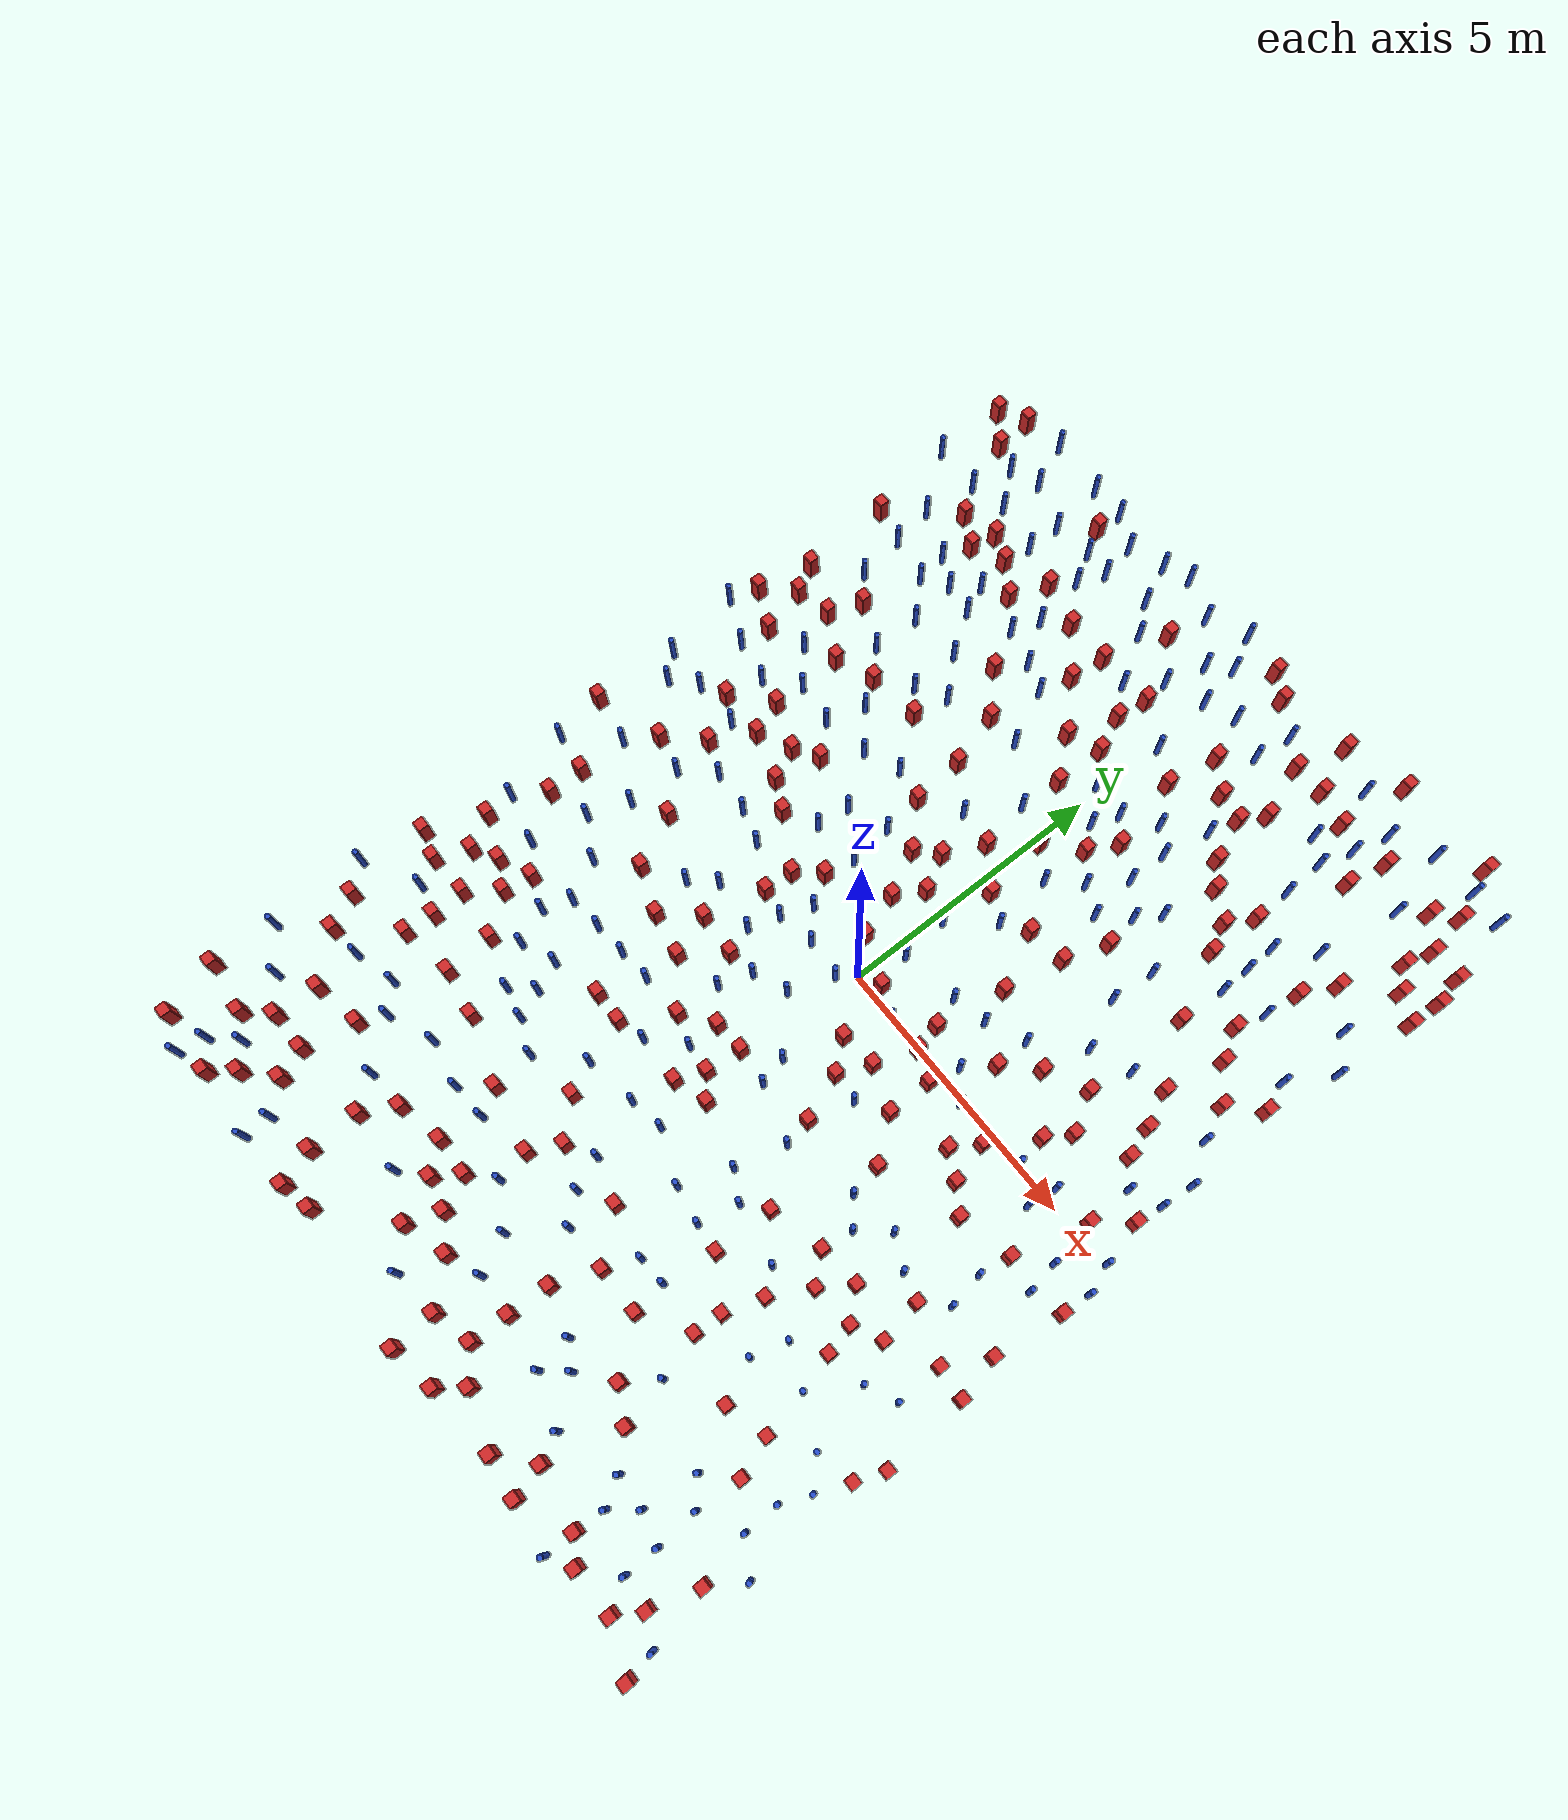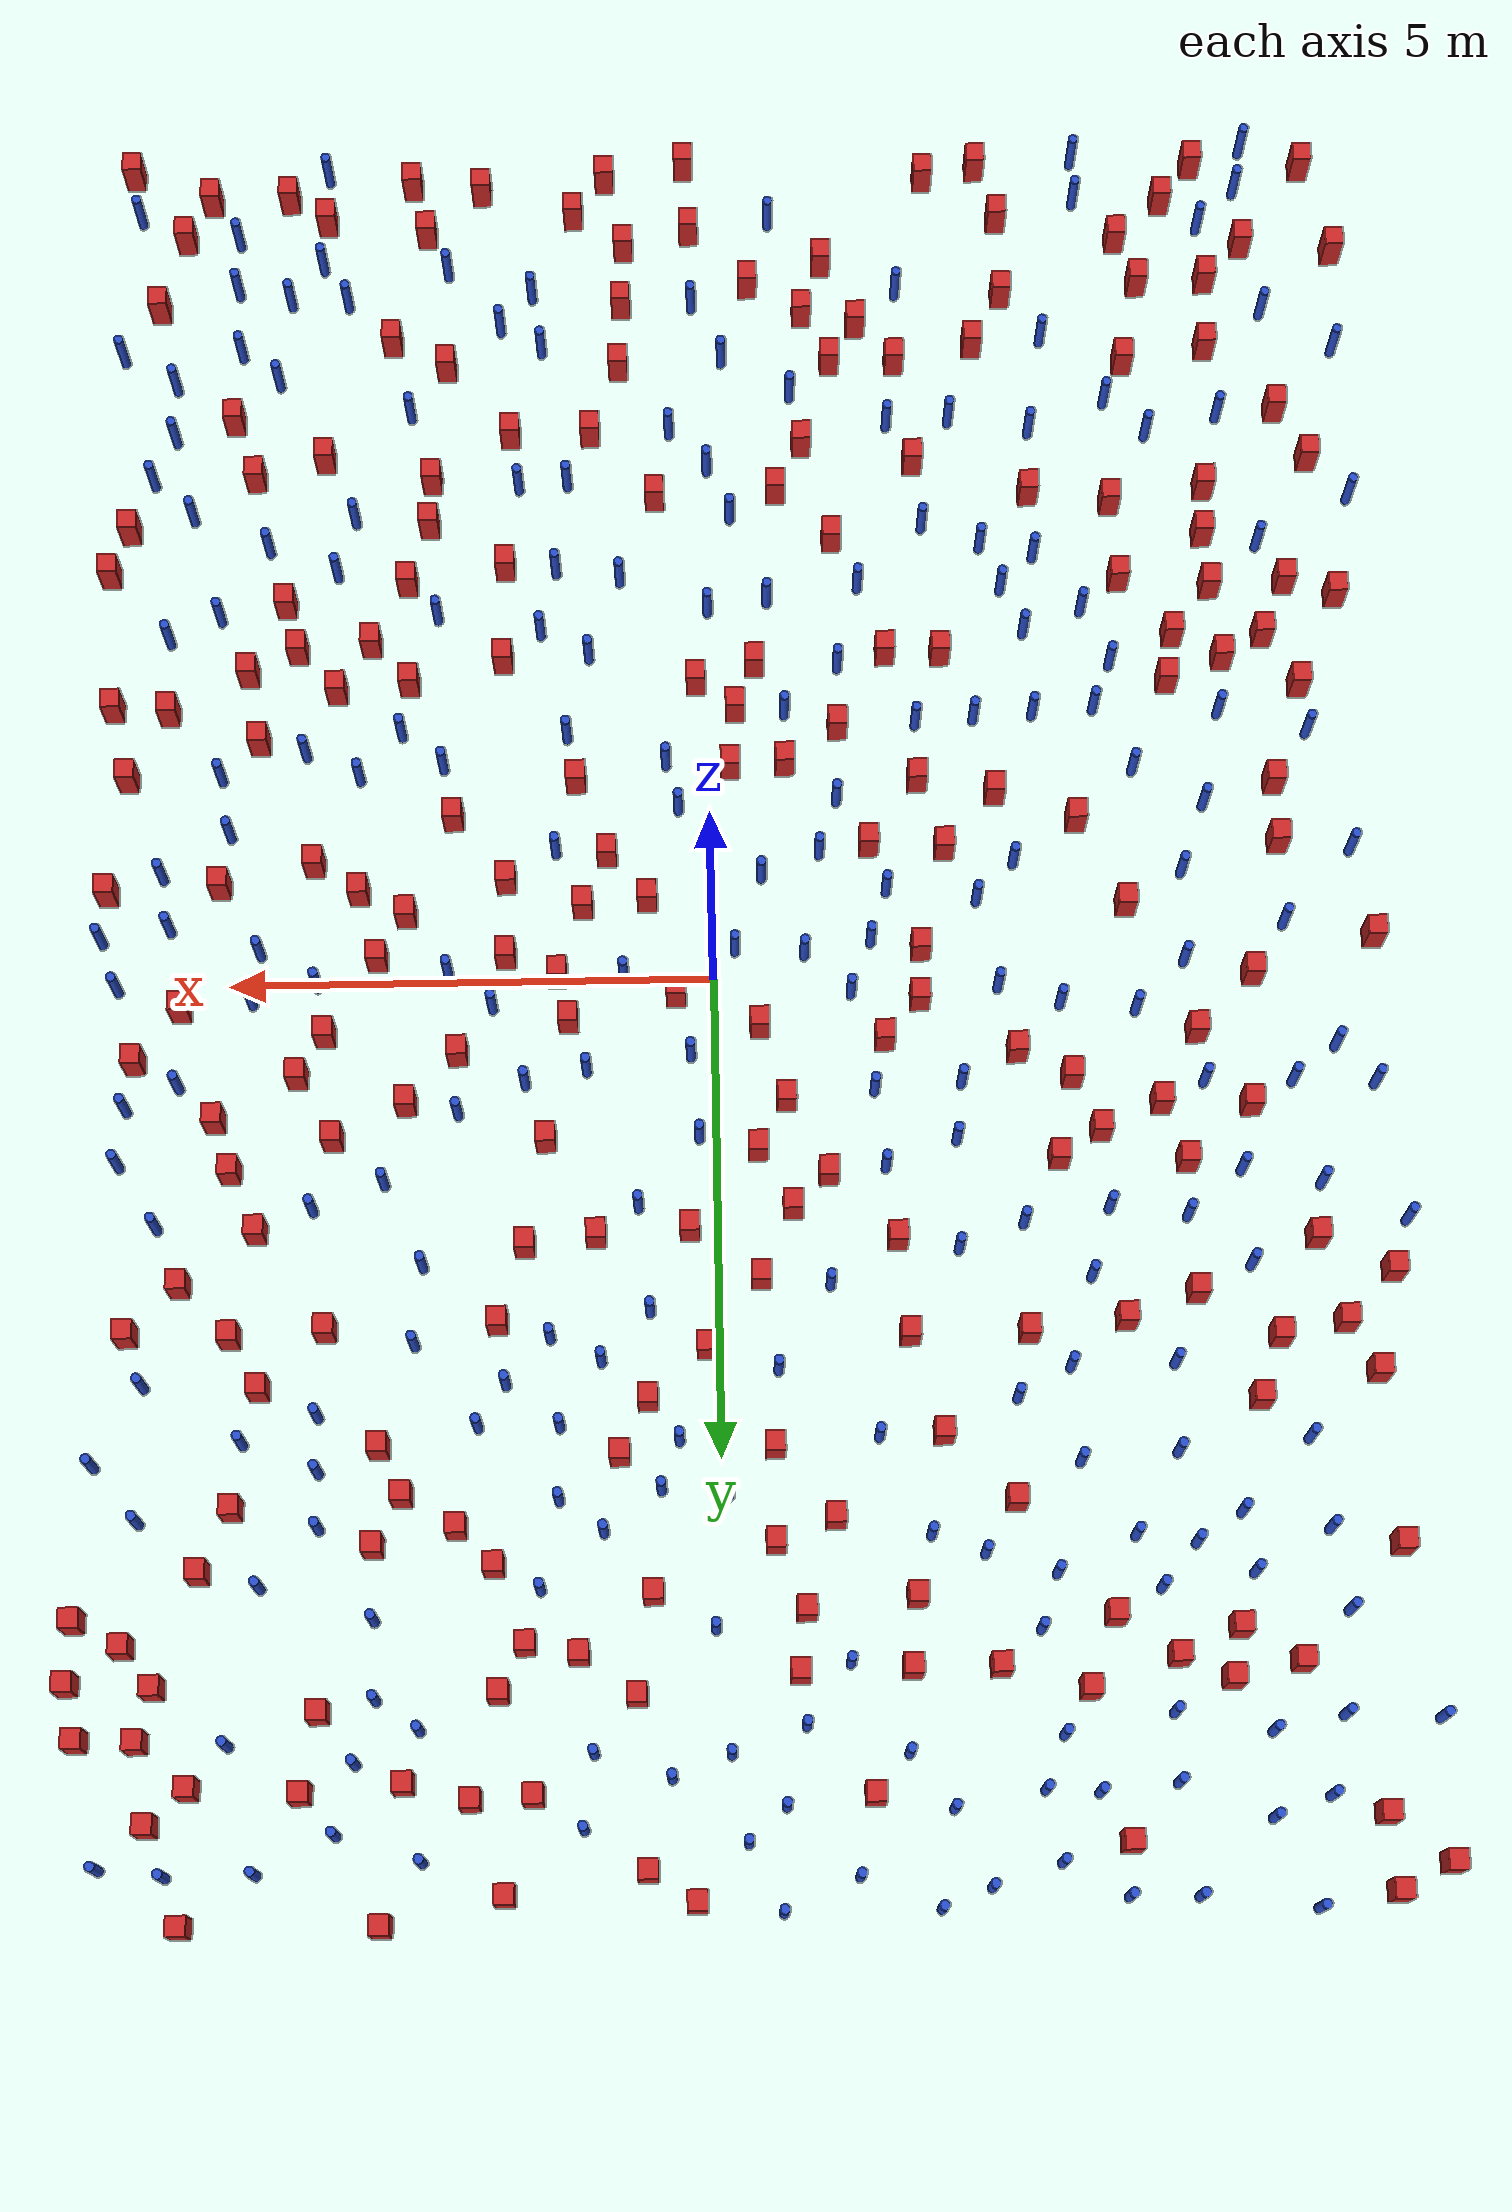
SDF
<sdf version="1.6">
  <model name="dense_43"><model name="square_post_obstacle0">
  <static>true</static>
  <pose frame="">-6.26751508779 3.72826211818 1.91545236811e-07 -7.35059704564e-06 1.12565212e-07 2.39332434364e-05</pose>
  <link name="link">
    <pose frame="">0 0 0.25 0 -0 0</pose>
    <inertial>
      <mass>100</mass>
      <inertia>
        <ixx>0.166667</ixx>
        <ixy>0</ixy>
        <ixz>0</ixz>
        <iyy>0.166667</iyy>
        <iyz>0</iyz>
        <izz>0.166667</izz>
      </inertia>
    </inertial>
    <collision name="collision">
      <geometry>
        <box>
          <size>.2 .2 .5</size>
        </box>
      </geometry>
      <max_contacts>10</max_contacts>
      <surface>
        <contact>
          <ode/>
        </contact>
        <bounce/>
        <friction>
          <torsional>
            <ode/>
          </torsional>
          <ode/>
        </friction>
      </surface>
    </collision>
    <visual name="visual">
      <geometry>
        <box>
          <size>.2 .2 .5</size>
        </box>
      </geometry>
      <material>
        <script>
          <name>Gazebo/Red</name>
          <uri>file://media/materials/scripts/gazebo.material</uri>
        </script>
      </material>
    </visual>
    <self_collide>0</self_collide>
    <kinematic>0</kinematic>
  </link>
</model>
<model name="square_post_obstacle1">
  <static>true</static>
  <pose frame="">-4.26526882868 -0.711887170166 1.91545236811e-07 -7.35059704564e-06 1.12565212e-07 2.39332434364e-05</pose>
  <link name="link">
    <pose frame="">0 0 0.25 0 -0 0</pose>
    <inertial>
      <mass>100</mass>
      <inertia>
        <ixx>0.166667</ixx>
        <ixy>0</ixy>
        <ixz>0</ixz>
        <iyy>0.166667</iyy>
        <iyz>0</iyz>
        <izz>0.166667</izz>
      </inertia>
    </inertial>
    <collision name="collision">
      <geometry>
        <box>
          <size>.2 .2 .5</size>
        </box>
      </geometry>
      <max_contacts>10</max_contacts>
      <surface>
        <contact>
          <ode/>
        </contact>
        <bounce/>
        <friction>
          <torsional>
            <ode/>
          </torsional>
          <ode/>
        </friction>
      </surface>
    </collision>
    <visual name="visual">
      <geometry>
        <box>
          <size>.2 .2 .5</size>
        </box>
      </geometry>
      <material>
        <script>
          <name>Gazebo/Red</name>
          <uri>file://media/materials/scripts/gazebo.material</uri>
        </script>
      </material>
    </visual>
    <self_collide>0</self_collide>
    <kinematic>0</kinematic>
  </link>
</model>
<model name="pole_obstacle0">
  <static>true</static>
  <pose frame="">5.76128852781 5.56607418223 7.38925637345e-09 -8.47170692796e-08 1.24976764786e-08 -1.74513093032e-07</pose>
  <link name="link">
  <pose frame="">0 0 0.3 0 -0 0</pose>
    <inertial>
      <mass>1</mass>
      <inertia>
        <ixx>0.145833</ixx>
        <ixy>0</ixy>
        <ixz>0</ixz>
        <iyy>0.145833</iyy>
        <iyz>0</iyz>
        <izz>0.125</izz>
      </inertia>
    </inertial>
    <collision name="collision">
      <geometry>
        <cylinder>
          <radius>0.05</radius>
          <length>.6</length>
        </cylinder>
      </geometry>
      <max_contacts>10</max_contacts>
      <surface>
        <contact>
          <ode/>
        </contact>
        <bounce/>
        <friction>
          <torsional>
            <ode/>
          </torsional>
          <ode/>
        </friction>
      </surface>
    </collision>
    <visual name="visual">
      <geometry>
        <cylinder>
          <radius>0.05</radius>
          <length>.6</length>
        </cylinder>
      </geometry>
      <material>
        <script>
          <name>Gazebo/Blue</name>
          <uri>file://media/materials/scripts/gazebo.material</uri>
        </script>
      </material>
    </visual>
    <self_collide>0</self_collide>
    <kinematic>0</kinematic>
  </link>
</model>
<model name="square_post_obstacle2">
  <static>true</static>
  <pose frame="">1.61059530566 -0.0328276457561 1.91545236811e-07 -7.35059704564e-06 1.12565212e-07 2.39332434364e-05</pose>
  <link name="link">
    <pose frame="">0 0 0.25 0 -0 0</pose>
    <inertial>
      <mass>100</mass>
      <inertia>
        <ixx>0.166667</ixx>
        <ixy>0</ixy>
        <ixz>0</ixz>
        <iyy>0.166667</iyy>
        <iyz>0</iyz>
        <izz>0.166667</izz>
      </inertia>
    </inertial>
    <collision name="collision">
      <geometry>
        <box>
          <size>.2 .2 .5</size>
        </box>
      </geometry>
      <max_contacts>10</max_contacts>
      <surface>
        <contact>
          <ode/>
        </contact>
        <bounce/>
        <friction>
          <torsional>
            <ode/>
          </torsional>
          <ode/>
        </friction>
      </surface>
    </collision>
    <visual name="visual">
      <geometry>
        <box>
          <size>.2 .2 .5</size>
        </box>
      </geometry>
      <material>
        <script>
          <name>Gazebo/Red</name>
          <uri>file://media/materials/scripts/gazebo.material</uri>
        </script>
      </material>
    </visual>
    <self_collide>0</self_collide>
    <kinematic>0</kinematic>
  </link>
</model>
<model name="pole_obstacle1">
  <static>true</static>
  <pose frame="">-6.63601493796 -1.28461203914 7.38925637345e-09 -8.471706928e-08 1.24976765134e-08 -1.74513093015e-07</pose>
  <link name="link">
  <pose frame="">0 0 0.3 0 -0 0</pose>
    <inertial>
      <mass>1</mass>
      <inertia>
        <ixx>0.145833</ixx>
        <ixy>0</ixy>
        <ixz>0</ixz>
        <iyy>0.145833</iyy>
        <iyz>0</iyz>
        <izz>0.125</izz>
      </inertia>
    </inertial>
    <collision name="collision">
      <geometry>
        <cylinder>
          <radius>0.05</radius>
          <length>.6</length>
        </cylinder>
      </geometry>
      <max_contacts>10</max_contacts>
      <surface>
        <contact>
          <ode/>
        </contact>
        <bounce/>
        <friction>
          <torsional>
            <ode/>
          </torsional>
          <ode/>
        </friction>
      </surface>
    </collision>
    <visual name="visual">
      <geometry>
        <cylinder>
          <radius>0.05</radius>
          <length>.6</length>
        </cylinder>
      </geometry>
      <material>
        <script>
          <name>Gazebo/Blue</name>
          <uri>file://media/materials/scripts/gazebo.material</uri>
        </script>
      </material>
    </visual>
    <self_collide>0</self_collide>
    <kinematic>0</kinematic>
  </link>
</model>
<model name="square_post_obstacle3">
  <static>true</static>
  <pose frame="">3.39269414633 4.85101991493 1.91545236811e-07 -7.35059704564e-06 1.12565212e-07 2.39332434364e-05</pose>
  <link name="link">
    <pose frame="">0 0 0.25 0 -0 0</pose>
    <inertial>
      <mass>100</mass>
      <inertia>
        <ixx>0.166667</ixx>
        <ixy>0</ixy>
        <ixz>0</ixz>
        <iyy>0.166667</iyy>
        <iyz>0</iyz>
        <izz>0.166667</izz>
      </inertia>
    </inertial>
    <collision name="collision">
      <geometry>
        <box>
          <size>.2 .2 .5</size>
        </box>
      </geometry>
      <max_contacts>10</max_contacts>
      <surface>
        <contact>
          <ode/>
        </contact>
        <bounce/>
        <friction>
          <torsional>
            <ode/>
          </torsional>
          <ode/>
        </friction>
      </surface>
    </collision>
    <visual name="visual">
      <geometry>
        <box>
          <size>.2 .2 .5</size>
        </box>
      </geometry>
      <material>
        <script>
          <name>Gazebo/Red</name>
          <uri>file://media/materials/scripts/gazebo.material</uri>
        </script>
      </material>
    </visual>
    <self_collide>0</self_collide>
    <kinematic>0</kinematic>
  </link>
</model>
<model name="pole_obstacle2">
  <static>true</static>
  <pose frame="">0.0751189451723 6.69348405141 7.38925637345e-09 -8.47170692799e-08 1.24976765062e-08 -1.74513093018e-07</pose>
  <link name="link">
  <pose frame="">0 0 0.3 0 -0 0</pose>
    <inertial>
      <mass>1</mass>
      <inertia>
        <ixx>0.145833</ixx>
        <ixy>0</ixy>
        <ixz>0</ixz>
        <iyy>0.145833</iyy>
        <iyz>0</iyz>
        <izz>0.125</izz>
      </inertia>
    </inertial>
    <collision name="collision">
      <geometry>
        <cylinder>
          <radius>0.05</radius>
          <length>.6</length>
        </cylinder>
      </geometry>
      <max_contacts>10</max_contacts>
      <surface>
        <contact>
          <ode/>
        </contact>
        <bounce/>
        <friction>
          <torsional>
            <ode/>
          </torsional>
          <ode/>
        </friction>
      </surface>
    </collision>
    <visual name="visual">
      <geometry>
        <cylinder>
          <radius>0.05</radius>
          <length>.6</length>
        </cylinder>
      </geometry>
      <material>
        <script>
          <name>Gazebo/Blue</name>
          <uri>file://media/materials/scripts/gazebo.material</uri>
        </script>
      </material>
    </visual>
    <self_collide>0</self_collide>
    <kinematic>0</kinematic>
  </link>
</model>
<model name="pole_obstacle3">
  <static>true</static>
  <pose frame="">0.141307437427 -7.68088082343 7.38925637345e-09 -8.471706928e-08 1.24976765036e-08 -1.74513093019e-07</pose>
  <link name="link">
  <pose frame="">0 0 0.3 0 -0 0</pose>
    <inertial>
      <mass>1</mass>
      <inertia>
        <ixx>0.145833</ixx>
        <ixy>0</ixy>
        <ixz>0</ixz>
        <iyy>0.145833</iyy>
        <iyz>0</iyz>
        <izz>0.125</izz>
      </inertia>
    </inertial>
    <collision name="collision">
      <geometry>
        <cylinder>
          <radius>0.05</radius>
          <length>.6</length>
        </cylinder>
      </geometry>
      <max_contacts>10</max_contacts>
      <surface>
        <contact>
          <ode/>
        </contact>
        <bounce/>
        <friction>
          <torsional>
            <ode/>
          </torsional>
          <ode/>
        </friction>
      </surface>
    </collision>
    <visual name="visual">
      <geometry>
        <cylinder>
          <radius>0.05</radius>
          <length>.6</length>
        </cylinder>
      </geometry>
      <material>
        <script>
          <name>Gazebo/Blue</name>
          <uri>file://media/materials/scripts/gazebo.material</uri>
        </script>
      </material>
    </visual>
    <self_collide>0</self_collide>
    <kinematic>0</kinematic>
  </link>
</model>
<model name="square_post_obstacle4">
  <static>true</static>
  <pose frame="">1.247294603 -6.15242603051 1.91545236811e-07 -7.35059704564e-06 1.12565212e-07 2.39332434364e-05</pose>
  <link name="link">
    <pose frame="">0 0 0.25 0 -0 0</pose>
    <inertial>
      <mass>100</mass>
      <inertia>
        <ixx>0.166667</ixx>
        <ixy>0</ixy>
        <ixz>0</ixz>
        <iyy>0.166667</iyy>
        <iyz>0</iyz>
        <izz>0.166667</izz>
      </inertia>
    </inertial>
    <collision name="collision">
      <geometry>
        <box>
          <size>.2 .2 .5</size>
        </box>
      </geometry>
      <max_contacts>10</max_contacts>
      <surface>
        <contact>
          <ode/>
        </contact>
        <bounce/>
        <friction>
          <torsional>
            <ode/>
          </torsional>
          <ode/>
        </friction>
      </surface>
    </collision>
    <visual name="visual">
      <geometry>
        <box>
          <size>.2 .2 .5</size>
        </box>
      </geometry>
      <material>
        <script>
          <name>Gazebo/Red</name>
          <uri>file://media/materials/scripts/gazebo.material</uri>
        </script>
      </material>
    </visual>
    <self_collide>0</self_collide>
    <kinematic>0</kinematic>
  </link>
</model>
<model name="square_post_obstacle5">
  <static>true</static>
  <pose frame="">0.161578494931 -8.57052492048 1.91545236811e-07 -7.35059704564e-06 1.12565212e-07 2.39332434364e-05</pose>
  <link name="link">
    <pose frame="">0 0 0.25 0 -0 0</pose>
    <inertial>
      <mass>100</mass>
      <inertia>
        <ixx>0.166667</ixx>
        <ixy>0</ixy>
        <ixz>0</ixz>
        <iyy>0.166667</iyy>
        <iyz>0</iyz>
        <izz>0.166667</izz>
      </inertia>
    </inertial>
    <collision name="collision">
      <geometry>
        <box>
          <size>.2 .2 .5</size>
        </box>
      </geometry>
      <max_contacts>10</max_contacts>
      <surface>
        <contact>
          <ode/>
        </contact>
        <bounce/>
        <friction>
          <torsional>
            <ode/>
          </torsional>
          <ode/>
        </friction>
      </surface>
    </collision>
    <visual name="visual">
      <geometry>
        <box>
          <size>.2 .2 .5</size>
        </box>
      </geometry>
      <material>
        <script>
          <name>Gazebo/Red</name>
          <uri>file://media/materials/scripts/gazebo.material</uri>
        </script>
      </material>
    </visual>
    <self_collide>0</self_collide>
    <kinematic>0</kinematic>
  </link>
</model>
<model name="square_post_obstacle6">
  <static>true</static>
  <pose frame="">-5.04222654512 6.75807206972 1.91545236811e-07 -7.35059704564e-06 1.12565212e-07 2.39332434364e-05</pose>
  <link name="link">
    <pose frame="">0 0 0.25 0 -0 0</pose>
    <inertial>
      <mass>100</mass>
      <inertia>
        <ixx>0.166667</ixx>
        <ixy>0</ixy>
        <ixz>0</ixz>
        <iyy>0.166667</iyy>
        <iyz>0</iyz>
        <izz>0.166667</izz>
      </inertia>
    </inertial>
    <collision name="collision">
      <geometry>
        <box>
          <size>.2 .2 .5</size>
        </box>
      </geometry>
      <max_contacts>10</max_contacts>
      <surface>
        <contact>
          <ode/>
        </contact>
        <bounce/>
        <friction>
          <torsional>
            <ode/>
          </torsional>
          <ode/>
        </friction>
      </surface>
    </collision>
    <visual name="visual">
      <geometry>
        <box>
          <size>.2 .2 .5</size>
        </box>
      </geometry>
      <material>
        <script>
          <name>Gazebo/Red</name>
          <uri>file://media/materials/scripts/gazebo.material</uri>
        </script>
      </material>
    </visual>
    <self_collide>0</self_collide>
    <kinematic>0</kinematic>
  </link>
</model>
<model name="pole_obstacle4">
  <static>true</static>
  <pose frame="">2.73617658869 -0.0764324424072 7.38925637345e-09 -8.471706928e-08 1.24976765088e-08 -1.74513093017e-07</pose>
  <link name="link">
  <pose frame="">0 0 0.3 0 -0 0</pose>
    <inertial>
      <mass>1</mass>
      <inertia>
        <ixx>0.145833</ixx>
        <ixy>0</ixy>
        <ixz>0</ixz>
        <iyy>0.145833</iyy>
        <iyz>0</iyz>
        <izz>0.125</izz>
      </inertia>
    </inertial>
    <collision name="collision">
      <geometry>
        <cylinder>
          <radius>0.05</radius>
          <length>.6</length>
        </cylinder>
      </geometry>
      <max_contacts>10</max_contacts>
      <surface>
        <contact>
          <ode/>
        </contact>
        <bounce/>
        <friction>
          <torsional>
            <ode/>
          </torsional>
          <ode/>
        </friction>
      </surface>
    </collision>
    <visual name="visual">
      <geometry>
        <cylinder>
          <radius>0.05</radius>
          <length>.6</length>
        </cylinder>
      </geometry>
      <material>
        <script>
          <name>Gazebo/Blue</name>
          <uri>file://media/materials/scripts/gazebo.material</uri>
        </script>
      </material>
    </visual>
    <self_collide>0</self_collide>
    <kinematic>0</kinematic>
  </link>
</model>
<model name="pole_obstacle5">
  <static>true</static>
  <pose frame="">2.62684425303 1.42801959995 7.38925637345e-09 -8.471706928e-08 1.24976765152e-08 -1.74513093012e-07</pose>
  <link name="link">
  <pose frame="">0 0 0.3 0 -0 0</pose>
    <inertial>
      <mass>1</mass>
      <inertia>
        <ixx>0.145833</ixx>
        <ixy>0</ixy>
        <ixz>0</ixz>
        <iyy>0.145833</iyy>
        <iyz>0</iyz>
        <izz>0.125</izz>
      </inertia>
    </inertial>
    <collision name="collision">
      <geometry>
        <cylinder>
          <radius>0.05</radius>
          <length>.6</length>
        </cylinder>
      </geometry>
      <max_contacts>10</max_contacts>
      <surface>
        <contact>
          <ode/>
        </contact>
        <bounce/>
        <friction>
          <torsional>
            <ode/>
          </torsional>
          <ode/>
        </friction>
      </surface>
    </collision>
    <visual name="visual">
      <geometry>
        <cylinder>
          <radius>0.05</radius>
          <length>.6</length>
        </cylinder>
      </geometry>
      <material>
        <script>
          <name>Gazebo/Blue</name>
          <uri>file://media/materials/scripts/gazebo.material</uri>
        </script>
      </material>
    </visual>
    <self_collide>0</self_collide>
    <kinematic>0</kinematic>
  </link>
</model>
<model name="square_post_obstacle7">
  <static>true</static>
  <pose frame="">4.10316415654 8.22295791466 1.91545236811e-07 -7.35059704564e-06 1.12565212e-07 2.39332434364e-05</pose>
  <link name="link">
    <pose frame="">0 0 0.25 0 -0 0</pose>
    <inertial>
      <mass>100</mass>
      <inertia>
        <ixx>0.166667</ixx>
        <ixy>0</ixy>
        <ixz>0</ixz>
        <iyy>0.166667</iyy>
        <iyz>0</iyz>
        <izz>0.166667</izz>
      </inertia>
    </inertial>
    <collision name="collision">
      <geometry>
        <box>
          <size>.2 .2 .5</size>
        </box>
      </geometry>
      <max_contacts>10</max_contacts>
      <surface>
        <contact>
          <ode/>
        </contact>
        <bounce/>
        <friction>
          <torsional>
            <ode/>
          </torsional>
          <ode/>
        </friction>
      </surface>
    </collision>
    <visual name="visual">
      <geometry>
        <box>
          <size>.2 .2 .5</size>
        </box>
      </geometry>
      <material>
        <script>
          <name>Gazebo/Red</name>
          <uri>file://media/materials/scripts/gazebo.material</uri>
        </script>
      </material>
    </visual>
    <self_collide>0</self_collide>
    <kinematic>0</kinematic>
  </link>
</model>
<model name="square_post_obstacle8">
  <static>true</static>
  <pose frame="">5.90578186092 -7.71212455294 1.91545236811e-07 -7.35059704564e-06 1.12565212e-07 2.39332434364e-05</pose>
  <link name="link">
    <pose frame="">0 0 0.25 0 -0 0</pose>
    <inertial>
      <mass>100</mass>
      <inertia>
        <ixx>0.166667</ixx>
        <ixy>0</ixy>
        <ixz>0</ixz>
        <iyy>0.166667</iyy>
        <iyz>0</iyz>
        <izz>0.166667</izz>
      </inertia>
    </inertial>
    <collision name="collision">
      <geometry>
        <box>
          <size>.2 .2 .5</size>
        </box>
      </geometry>
      <max_contacts>10</max_contacts>
      <surface>
        <contact>
          <ode/>
        </contact>
        <bounce/>
        <friction>
          <torsional>
            <ode/>
          </torsional>
          <ode/>
        </friction>
      </surface>
    </collision>
    <visual name="visual">
      <geometry>
        <box>
          <size>.2 .2 .5</size>
        </box>
      </geometry>
      <material>
        <script>
          <name>Gazebo/Red</name>
          <uri>file://media/materials/scripts/gazebo.material</uri>
        </script>
      </material>
    </visual>
    <self_collide>0</self_collide>
    <kinematic>0</kinematic>
  </link>
</model>
<model name="pole_obstacle6">
  <static>true</static>
  <pose frame="">-5.83699710048 8.39616868612 7.38925637345e-09 -8.471706928e-08 1.24976765081e-08 -1.74513093015e-07</pose>
  <link name="link">
  <pose frame="">0 0 0.3 0 -0 0</pose>
    <inertial>
      <mass>1</mass>
      <inertia>
        <ixx>0.145833</ixx>
        <ixy>0</ixy>
        <ixz>0</ixz>
        <iyy>0.145833</iyy>
        <iyz>0</iyz>
        <izz>0.125</izz>
      </inertia>
    </inertial>
    <collision name="collision">
      <geometry>
        <cylinder>
          <radius>0.05</radius>
          <length>.6</length>
        </cylinder>
      </geometry>
      <max_contacts>10</max_contacts>
      <surface>
        <contact>
          <ode/>
        </contact>
        <bounce/>
        <friction>
          <torsional>
            <ode/>
          </torsional>
          <ode/>
        </friction>
      </surface>
    </collision>
    <visual name="visual">
      <geometry>
        <cylinder>
          <radius>0.05</radius>
          <length>.6</length>
        </cylinder>
      </geometry>
      <material>
        <script>
          <name>Gazebo/Blue</name>
          <uri>file://media/materials/scripts/gazebo.material</uri>
        </script>
      </material>
    </visual>
    <self_collide>0</self_collide>
    <kinematic>0</kinematic>
  </link>
</model>
<model name="pole_obstacle7">
  <static>true</static>
  <pose frame="">3.04893697726 3.82194776182 7.38925637345e-09 -8.47170692798e-08 1.24976764939e-08 -1.74513093025e-07</pose>
  <link name="link">
  <pose frame="">0 0 0.3 0 -0 0</pose>
    <inertial>
      <mass>1</mass>
      <inertia>
        <ixx>0.145833</ixx>
        <ixy>0</ixy>
        <ixz>0</ixz>
        <iyy>0.145833</iyy>
        <iyz>0</iyz>
        <izz>0.125</izz>
      </inertia>
    </inertial>
    <collision name="collision">
      <geometry>
        <cylinder>
          <radius>0.05</radius>
          <length>.6</length>
        </cylinder>
      </geometry>
      <max_contacts>10</max_contacts>
      <surface>
        <contact>
          <ode/>
        </contact>
        <bounce/>
        <friction>
          <torsional>
            <ode/>
          </torsional>
          <ode/>
        </friction>
      </surface>
    </collision>
    <visual name="visual">
      <geometry>
        <cylinder>
          <radius>0.05</radius>
          <length>.6</length>
        </cylinder>
      </geometry>
      <material>
        <script>
          <name>Gazebo/Blue</name>
          <uri>file://media/materials/scripts/gazebo.material</uri>
        </script>
      </material>
    </visual>
    <self_collide>0</self_collide>
    <kinematic>0</kinematic>
  </link>
</model>
<model name="square_post_obstacle9">
  <static>true</static>
  <pose frame="">4.83220556354 5.45083646995 1.91545236811e-07 -7.35059704564e-06 1.12565212e-07 2.39332434364e-05</pose>
  <link name="link">
    <pose frame="">0 0 0.25 0 -0 0</pose>
    <inertial>
      <mass>100</mass>
      <inertia>
        <ixx>0.166667</ixx>
        <ixy>0</ixy>
        <ixz>0</ixz>
        <iyy>0.166667</iyy>
        <iyz>0</iyz>
        <izz>0.166667</izz>
      </inertia>
    </inertial>
    <collision name="collision">
      <geometry>
        <box>
          <size>.2 .2 .5</size>
        </box>
      </geometry>
      <max_contacts>10</max_contacts>
      <surface>
        <contact>
          <ode/>
        </contact>
        <bounce/>
        <friction>
          <torsional>
            <ode/>
          </torsional>
          <ode/>
        </friction>
      </surface>
    </collision>
    <visual name="visual">
      <geometry>
        <box>
          <size>.2 .2 .5</size>
        </box>
      </geometry>
      <material>
        <script>
          <name>Gazebo/Red</name>
          <uri>file://media/materials/scripts/gazebo.material</uri>
        </script>
      </material>
    </visual>
    <self_collide>0</self_collide>
    <kinematic>0</kinematic>
  </link>
</model>
<model name="square_post_obstacle10">
  <static>true</static>
  <pose frame="">-3.8304520646 6.61883451732 1.91545236811e-07 -7.35059704564e-06 1.12565212e-07 2.39332434364e-05</pose>
  <link name="link">
    <pose frame="">0 0 0.25 0 -0 0</pose>
    <inertial>
      <mass>100</mass>
      <inertia>
        <ixx>0.166667</ixx>
        <ixy>0</ixy>
        <ixz>0</ixz>
        <iyy>0.166667</iyy>
        <iyz>0</iyz>
        <izz>0.166667</izz>
      </inertia>
    </inertial>
    <collision name="collision">
      <geometry>
        <box>
          <size>.2 .2 .5</size>
        </box>
      </geometry>
      <max_contacts>10</max_contacts>
      <surface>
        <contact>
          <ode/>
        </contact>
        <bounce/>
        <friction>
          <torsional>
            <ode/>
          </torsional>
          <ode/>
        </friction>
      </surface>
    </collision>
    <visual name="visual">
      <geometry>
        <box>
          <size>.2 .2 .5</size>
        </box>
      </geometry>
      <material>
        <script>
          <name>Gazebo/Red</name>
          <uri>file://media/materials/scripts/gazebo.material</uri>
        </script>
      </material>
    </visual>
    <self_collide>0</self_collide>
    <kinematic>0</kinematic>
  </link>
</model>
<model name="square_post_obstacle11">
  <static>true</static>
  <pose frame="">-3.46584824441 1.98512690318 1.91545236811e-07 -7.35059704564e-06 1.12565212e-07 2.39332434364e-05</pose>
  <link name="link">
    <pose frame="">0 0 0.25 0 -0 0</pose>
    <inertial>
      <mass>100</mass>
      <inertia>
        <ixx>0.166667</ixx>
        <ixy>0</ixy>
        <ixz>0</ixz>
        <iyy>0.166667</iyy>
        <iyz>0</iyz>
        <izz>0.166667</izz>
      </inertia>
    </inertial>
    <collision name="collision">
      <geometry>
        <box>
          <size>.2 .2 .5</size>
        </box>
      </geometry>
      <max_contacts>10</max_contacts>
      <surface>
        <contact>
          <ode/>
        </contact>
        <bounce/>
        <friction>
          <torsional>
            <ode/>
          </torsional>
          <ode/>
        </friction>
      </surface>
    </collision>
    <visual name="visual">
      <geometry>
        <box>
          <size>.2 .2 .5</size>
        </box>
      </geometry>
      <material>
        <script>
          <name>Gazebo/Red</name>
          <uri>file://media/materials/scripts/gazebo.material</uri>
        </script>
      </material>
    </visual>
    <self_collide>0</self_collide>
    <kinematic>0</kinematic>
  </link>
</model>
<model name="square_post_obstacle12">
  <static>true</static>
  <pose frame="">-5.41068607509 -7.08402210731 1.91545236811e-07 -7.35059704564e-06 1.12565212e-07 2.39332434364e-05</pose>
  <link name="link">
    <pose frame="">0 0 0.25 0 -0 0</pose>
    <inertial>
      <mass>100</mass>
      <inertia>
        <ixx>0.166667</ixx>
        <ixy>0</ixy>
        <ixz>0</ixz>
        <iyy>0.166667</iyy>
        <iyz>0</iyz>
        <izz>0.166667</izz>
      </inertia>
    </inertial>
    <collision name="collision">
      <geometry>
        <box>
          <size>.2 .2 .5</size>
        </box>
      </geometry>
      <max_contacts>10</max_contacts>
      <surface>
        <contact>
          <ode/>
        </contact>
        <bounce/>
        <friction>
          <torsional>
            <ode/>
          </torsional>
          <ode/>
        </friction>
      </surface>
    </collision>
    <visual name="visual">
      <geometry>
        <box>
          <size>.2 .2 .5</size>
        </box>
      </geometry>
      <material>
        <script>
          <name>Gazebo/Red</name>
          <uri>file://media/materials/scripts/gazebo.material</uri>
        </script>
      </material>
    </visual>
    <self_collide>0</self_collide>
    <kinematic>0</kinematic>
  </link>
</model>
<model name="square_post_obstacle13">
  <static>true</static>
  <pose frame="">-4.93012539754 0.668586995232 1.91545236811e-07 -7.35059704564e-06 1.12565212e-07 2.39332434364e-05</pose>
  <link name="link">
    <pose frame="">0 0 0.25 0 -0 0</pose>
    <inertial>
      <mass>100</mass>
      <inertia>
        <ixx>0.166667</ixx>
        <ixy>0</ixy>
        <ixz>0</ixz>
        <iyy>0.166667</iyy>
        <iyz>0</iyz>
        <izz>0.166667</izz>
      </inertia>
    </inertial>
    <collision name="collision">
      <geometry>
        <box>
          <size>.2 .2 .5</size>
        </box>
      </geometry>
      <max_contacts>10</max_contacts>
      <surface>
        <contact>
          <ode/>
        </contact>
        <bounce/>
        <friction>
          <torsional>
            <ode/>
          </torsional>
          <ode/>
        </friction>
      </surface>
    </collision>
    <visual name="visual">
      <geometry>
        <box>
          <size>.2 .2 .5</size>
        </box>
      </geometry>
      <material>
        <script>
          <name>Gazebo/Red</name>
          <uri>file://media/materials/scripts/gazebo.material</uri>
        </script>
      </material>
    </visual>
    <self_collide>0</self_collide>
    <kinematic>0</kinematic>
  </link>
</model>
<model name="pole_obstacle8">
  <static>true</static>
  <pose frame="">4.23675840631 -2.50700964312 7.38925637345e-09 -8.47170692798e-08 1.24976764937e-08 -1.74513093023e-07</pose>
  <link name="link">
  <pose frame="">0 0 0.3 0 -0 0</pose>
    <inertial>
      <mass>1</mass>
      <inertia>
        <ixx>0.145833</ixx>
        <ixy>0</ixy>
        <ixz>0</ixz>
        <iyy>0.145833</iyy>
        <iyz>0</iyz>
        <izz>0.125</izz>
      </inertia>
    </inertial>
    <collision name="collision">
      <geometry>
        <cylinder>
          <radius>0.05</radius>
          <length>.6</length>
        </cylinder>
      </geometry>
      <max_contacts>10</max_contacts>
      <surface>
        <contact>
          <ode/>
        </contact>
        <bounce/>
        <friction>
          <torsional>
            <ode/>
          </torsional>
          <ode/>
        </friction>
      </surface>
    </collision>
    <visual name="visual">
      <geometry>
        <cylinder>
          <radius>0.05</radius>
          <length>.6</length>
        </cylinder>
      </geometry>
      <material>
        <script>
          <name>Gazebo/Blue</name>
          <uri>file://media/materials/scripts/gazebo.material</uri>
        </script>
      </material>
    </visual>
    <self_collide>0</self_collide>
    <kinematic>0</kinematic>
  </link>
</model>
<model name="square_post_obstacle14">
  <static>true</static>
  <pose frame="">1.41845635646 -8.77849370848 1.91545236811e-07 -7.35059704564e-06 1.12565212e-07 2.39332434364e-05</pose>
  <link name="link">
    <pose frame="">0 0 0.25 0 -0 0</pose>
    <inertial>
      <mass>100</mass>
      <inertia>
        <ixx>0.166667</ixx>
        <ixy>0</ixy>
        <ixz>0</ixz>
        <iyy>0.166667</iyy>
        <iyz>0</iyz>
        <izz>0.166667</izz>
      </inertia>
    </inertial>
    <collision name="collision">
      <geometry>
        <box>
          <size>.2 .2 .5</size>
        </box>
      </geometry>
      <max_contacts>10</max_contacts>
      <surface>
        <contact>
          <ode/>
        </contact>
        <bounce/>
        <friction>
          <torsional>
            <ode/>
          </torsional>
          <ode/>
        </friction>
      </surface>
    </collision>
    <visual name="visual">
      <geometry>
        <box>
          <size>.2 .2 .5</size>
        </box>
      </geometry>
      <material>
        <script>
          <name>Gazebo/Red</name>
          <uri>file://media/materials/scripts/gazebo.material</uri>
        </script>
      </material>
    </visual>
    <self_collide>0</self_collide>
    <kinematic>0</kinematic>
  </link>
</model>
<model name="square_post_obstacle15">
  <static>true</static>
  <pose frame="">2.46411569563 8.30953991213 1.91545236811e-07 -7.35059704564e-06 1.12565212e-07 2.39332434364e-05</pose>
  <link name="link">
    <pose frame="">0 0 0.25 0 -0 0</pose>
    <inertial>
      <mass>100</mass>
      <inertia>
        <ixx>0.166667</ixx>
        <ixy>0</ixy>
        <ixz>0</ixz>
        <iyy>0.166667</iyy>
        <iyz>0</iyz>
        <izz>0.166667</izz>
      </inertia>
    </inertial>
    <collision name="collision">
      <geometry>
        <box>
          <size>.2 .2 .5</size>
        </box>
      </geometry>
      <max_contacts>10</max_contacts>
      <surface>
        <contact>
          <ode/>
        </contact>
        <bounce/>
        <friction>
          <torsional>
            <ode/>
          </torsional>
          <ode/>
        </friction>
      </surface>
    </collision>
    <visual name="visual">
      <geometry>
        <box>
          <size>.2 .2 .5</size>
        </box>
      </geometry>
      <material>
        <script>
          <name>Gazebo/Red</name>
          <uri>file://media/materials/scripts/gazebo.material</uri>
        </script>
      </material>
    </visual>
    <self_collide>0</self_collide>
    <kinematic>0</kinematic>
  </link>
</model>
<model name="square_post_obstacle16">
  <static>true</static>
  <pose frame="">6.3573693927 6.53001208499 1.91545236811e-07 -7.35059704564e-06 1.12565212e-07 2.39332434364e-05</pose>
  <link name="link">
    <pose frame="">0 0 0.25 0 -0 0</pose>
    <inertial>
      <mass>100</mass>
      <inertia>
        <ixx>0.166667</ixx>
        <ixy>0</ixy>
        <ixz>0</ixz>
        <iyy>0.166667</iyy>
        <iyz>0</iyz>
        <izz>0.166667</izz>
      </inertia>
    </inertial>
    <collision name="collision">
      <geometry>
        <box>
          <size>.2 .2 .5</size>
        </box>
      </geometry>
      <max_contacts>10</max_contacts>
      <surface>
        <contact>
          <ode/>
        </contact>
        <bounce/>
        <friction>
          <torsional>
            <ode/>
          </torsional>
          <ode/>
        </friction>
      </surface>
    </collision>
    <visual name="visual">
      <geometry>
        <box>
          <size>.2 .2 .5</size>
        </box>
      </geometry>
      <material>
        <script>
          <name>Gazebo/Red</name>
          <uri>file://media/materials/scripts/gazebo.material</uri>
        </script>
      </material>
    </visual>
    <self_collide>0</self_collide>
    <kinematic>0</kinematic>
  </link>
</model>
<model name="pole_obstacle9">
  <static>true</static>
  <pose frame="">-4.84726449901 -0.0963658252567 7.38925637345e-09 -8.47170692799e-08 1.24976765039e-08 -1.74513093019e-07</pose>
  <link name="link">
  <pose frame="">0 0 0.3 0 -0 0</pose>
    <inertial>
      <mass>1</mass>
      <inertia>
        <ixx>0.145833</ixx>
        <ixy>0</ixy>
        <ixz>0</ixz>
        <iyy>0.145833</iyy>
        <iyz>0</iyz>
        <izz>0.125</izz>
      </inertia>
    </inertial>
    <collision name="collision">
      <geometry>
        <cylinder>
          <radius>0.05</radius>
          <length>.6</length>
        </cylinder>
      </geometry>
      <max_contacts>10</max_contacts>
      <surface>
        <contact>
          <ode/>
        </contact>
        <bounce/>
        <friction>
          <torsional>
            <ode/>
          </torsional>
          <ode/>
        </friction>
      </surface>
    </collision>
    <visual name="visual">
      <geometry>
        <cylinder>
          <radius>0.05</radius>
          <length>.6</length>
        </cylinder>
      </geometry>
      <material>
        <script>
          <name>Gazebo/Blue</name>
          <uri>file://media/materials/scripts/gazebo.material</uri>
        </script>
      </material>
    </visual>
    <self_collide>0</self_collide>
    <kinematic>0</kinematic>
  </link>
</model>
<model name="square_post_obstacle17">
  <static>true</static>
  <pose frame="">-3.43209271855 -5.3860651551 1.91545236811e-07 -7.35059704564e-06 1.12565212e-07 2.39332434364e-05</pose>
  <link name="link">
    <pose frame="">0 0 0.25 0 -0 0</pose>
    <inertial>
      <mass>100</mass>
      <inertia>
        <ixx>0.166667</ixx>
        <ixy>0</ixy>
        <ixz>0</ixz>
        <iyy>0.166667</iyy>
        <iyz>0</iyz>
        <izz>0.166667</izz>
      </inertia>
    </inertial>
    <collision name="collision">
      <geometry>
        <box>
          <size>.2 .2 .5</size>
        </box>
      </geometry>
      <max_contacts>10</max_contacts>
      <surface>
        <contact>
          <ode/>
        </contact>
        <bounce/>
        <friction>
          <torsional>
            <ode/>
          </torsional>
          <ode/>
        </friction>
      </surface>
    </collision>
    <visual name="visual">
      <geometry>
        <box>
          <size>.2 .2 .5</size>
        </box>
      </geometry>
      <material>
        <script>
          <name>Gazebo/Red</name>
          <uri>file://media/materials/scripts/gazebo.material</uri>
        </script>
      </material>
    </visual>
    <self_collide>0</self_collide>
    <kinematic>0</kinematic>
  </link>
</model>
<model name="square_post_obstacle18">
  <static>true</static>
  <pose frame="">0.291771999807 9.30222031321 1.91545236811e-07 -7.35059704564e-06 1.12565212e-07 2.39332434364e-05</pose>
  <link name="link">
    <pose frame="">0 0 0.25 0 -0 0</pose>
    <inertial>
      <mass>100</mass>
      <inertia>
        <ixx>0.166667</ixx>
        <ixy>0</ixy>
        <ixz>0</ixz>
        <iyy>0.166667</iyy>
        <iyz>0</iyz>
        <izz>0.166667</izz>
      </inertia>
    </inertial>
    <collision name="collision">
      <geometry>
        <box>
          <size>.2 .2 .5</size>
        </box>
      </geometry>
      <max_contacts>10</max_contacts>
      <surface>
        <contact>
          <ode/>
        </contact>
        <bounce/>
        <friction>
          <torsional>
            <ode/>
          </torsional>
          <ode/>
        </friction>
      </surface>
    </collision>
    <visual name="visual">
      <geometry>
        <box>
          <size>.2 .2 .5</size>
        </box>
      </geometry>
      <material>
        <script>
          <name>Gazebo/Red</name>
          <uri>file://media/materials/scripts/gazebo.material</uri>
        </script>
      </material>
    </visual>
    <self_collide>0</self_collide>
    <kinematic>0</kinematic>
  </link>
</model>
<model name="pole_obstacle10">
  <static>true</static>
  <pose frame="">-5.36167186587 3.1312678507 7.38925637345e-09 -8.47170692798e-08 1.24976764937e-08 -1.74513093023e-07</pose>
  <link name="link">
  <pose frame="">0 0 0.3 0 -0 0</pose>
    <inertial>
      <mass>1</mass>
      <inertia>
        <ixx>0.145833</ixx>
        <ixy>0</ixy>
        <ixz>0</ixz>
        <iyy>0.145833</iyy>
        <iyz>0</iyz>
        <izz>0.125</izz>
      </inertia>
    </inertial>
    <collision name="collision">
      <geometry>
        <cylinder>
          <radius>0.05</radius>
          <length>.6</length>
        </cylinder>
      </geometry>
      <max_contacts>10</max_contacts>
      <surface>
        <contact>
          <ode/>
        </contact>
        <bounce/>
        <friction>
          <torsional>
            <ode/>
          </torsional>
          <ode/>
        </friction>
      </surface>
    </collision>
    <visual name="visual">
      <geometry>
        <cylinder>
          <radius>0.05</radius>
          <length>.6</length>
        </cylinder>
      </geometry>
      <material>
        <script>
          <name>Gazebo/Blue</name>
          <uri>file://media/materials/scripts/gazebo.material</uri>
        </script>
      </material>
    </visual>
    <self_collide>0</self_collide>
    <kinematic>0</kinematic>
  </link>
</model>
<model name="square_post_obstacle19">
  <static>true</static>
  <pose frame="">4.82646554091 -5.68072084667 1.91545236811e-07 -7.35059704564e-06 1.12565212e-07 2.39332434364e-05</pose>
  <link name="link">
    <pose frame="">0 0 0.25 0 -0 0</pose>
    <inertial>
      <mass>100</mass>
      <inertia>
        <ixx>0.166667</ixx>
        <ixy>0</ixy>
        <ixz>0</ixz>
        <iyy>0.166667</iyy>
        <iyz>0</iyz>
        <izz>0.166667</izz>
      </inertia>
    </inertial>
    <collision name="collision">
      <geometry>
        <box>
          <size>.2 .2 .5</size>
        </box>
      </geometry>
      <max_contacts>10</max_contacts>
      <surface>
        <contact>
          <ode/>
        </contact>
        <bounce/>
        <friction>
          <torsional>
            <ode/>
          </torsional>
          <ode/>
        </friction>
      </surface>
    </collision>
    <visual name="visual">
      <geometry>
        <box>
          <size>.2 .2 .5</size>
        </box>
      </geometry>
      <material>
        <script>
          <name>Gazebo/Red</name>
          <uri>file://media/materials/scripts/gazebo.material</uri>
        </script>
      </material>
    </visual>
    <self_collide>0</self_collide>
    <kinematic>0</kinematic>
  </link>
</model>
<model name="pole_obstacle11">
  <static>true</static>
  <pose frame="">-4.07201410686 5.84191338444 7.38925637345e-09 -8.47170692796e-08 1.24976764786e-08 -1.74513093032e-07</pose>
  <link name="link">
  <pose frame="">0 0 0.3 0 -0 0</pose>
    <inertial>
      <mass>1</mass>
      <inertia>
        <ixx>0.145833</ixx>
        <ixy>0</ixy>
        <ixz>0</ixz>
        <iyy>0.145833</iyy>
        <iyz>0</iyz>
        <izz>0.125</izz>
      </inertia>
    </inertial>
    <collision name="collision">
      <geometry>
        <cylinder>
          <radius>0.05</radius>
          <length>.6</length>
        </cylinder>
      </geometry>
      <max_contacts>10</max_contacts>
      <surface>
        <contact>
          <ode/>
        </contact>
        <bounce/>
        <friction>
          <torsional>
            <ode/>
          </torsional>
          <ode/>
        </friction>
      </surface>
    </collision>
    <visual name="visual">
      <geometry>
        <cylinder>
          <radius>0.05</radius>
          <length>.6</length>
        </cylinder>
      </geometry>
      <material>
        <script>
          <name>Gazebo/Blue</name>
          <uri>file://media/materials/scripts/gazebo.material</uri>
        </script>
      </material>
    </visual>
    <self_collide>0</self_collide>
    <kinematic>0</kinematic>
  </link>
</model>
<model name="square_post_obstacle20">
  <static>true</static>
  <pose frame="">1.0768508336 -9.2199925486 1.91545236811e-07 -7.35059704564e-06 1.12565212e-07 2.39332434364e-05</pose>
  <link name="link">
    <pose frame="">0 0 0.25 0 -0 0</pose>
    <inertial>
      <mass>100</mass>
      <inertia>
        <ixx>0.166667</ixx>
        <ixy>0</ixy>
        <ixz>0</ixz>
        <iyy>0.166667</iyy>
        <iyz>0</iyz>
        <izz>0.166667</izz>
      </inertia>
    </inertial>
    <collision name="collision">
      <geometry>
        <box>
          <size>.2 .2 .5</size>
        </box>
      </geometry>
      <max_contacts>10</max_contacts>
      <surface>
        <contact>
          <ode/>
        </contact>
        <bounce/>
        <friction>
          <torsional>
            <ode/>
          </torsional>
          <ode/>
        </friction>
      </surface>
    </collision>
    <visual name="visual">
      <geometry>
        <box>
          <size>.2 .2 .5</size>
        </box>
      </geometry>
      <material>
        <script>
          <name>Gazebo/Red</name>
          <uri>file://media/materials/scripts/gazebo.material</uri>
        </script>
      </material>
    </visual>
    <self_collide>0</self_collide>
    <kinematic>0</kinematic>
  </link>
</model>
<model name="pole_obstacle12">
  <static>true</static>
  <pose frame="">-6.95213012178 7.66707469394 7.38925637345e-09 -8.47170692796e-08 1.24976764786e-08 -1.74513093032e-07</pose>
  <link name="link">
  <pose frame="">0 0 0.3 0 -0 0</pose>
    <inertial>
      <mass>1</mass>
      <inertia>
        <ixx>0.145833</ixx>
        <ixy>0</ixy>
        <ixz>0</ixz>
        <iyy>0.145833</iyy>
        <iyz>0</iyz>
        <izz>0.125</izz>
      </inertia>
    </inertial>
    <collision name="collision">
      <geometry>
        <cylinder>
          <radius>0.05</radius>
          <length>.6</length>
        </cylinder>
      </geometry>
      <max_contacts>10</max_contacts>
      <surface>
        <contact>
          <ode/>
        </contact>
        <bounce/>
        <friction>
          <torsional>
            <ode/>
          </torsional>
          <ode/>
        </friction>
      </surface>
    </collision>
    <visual name="visual">
      <geometry>
        <cylinder>
          <radius>0.05</radius>
          <length>.6</length>
        </cylinder>
      </geometry>
      <material>
        <script>
          <name>Gazebo/Blue</name>
          <uri>file://media/materials/scripts/gazebo.material</uri>
        </script>
      </material>
    </visual>
    <self_collide>0</self_collide>
    <kinematic>0</kinematic>
  </link>
</model>
<model name="square_post_obstacle21">
  <static>true</static>
  <pose frame="">0.146579969582 -3.2607515876 1.91545236811e-07 -7.35059704564e-06 1.12565212e-07 2.39332434364e-05</pose>
  <link name="link">
    <pose frame="">0 0 0.25 0 -0 0</pose>
    <inertial>
      <mass>100</mass>
      <inertia>
        <ixx>0.166667</ixx>
        <ixy>0</ixy>
        <ixz>0</ixz>
        <iyy>0.166667</iyy>
        <iyz>0</iyz>
        <izz>0.166667</izz>
      </inertia>
    </inertial>
    <collision name="collision">
      <geometry>
        <box>
          <size>.2 .2 .5</size>
        </box>
      </geometry>
      <max_contacts>10</max_contacts>
      <surface>
        <contact>
          <ode/>
        </contact>
        <bounce/>
        <friction>
          <torsional>
            <ode/>
          </torsional>
          <ode/>
        </friction>
      </surface>
    </collision>
    <visual name="visual">
      <geometry>
        <box>
          <size>.2 .2 .5</size>
        </box>
      </geometry>
      <material>
        <script>
          <name>Gazebo/Red</name>
          <uri>file://media/materials/scripts/gazebo.material</uri>
        </script>
      </material>
    </visual>
    <self_collide>0</self_collide>
    <kinematic>0</kinematic>
  </link>
</model>
<model name="pole_obstacle13">
  <static>true</static>
  <pose frame="">-0.584820534755 4.12830127704 7.38925637345e-09 -8.471706928e-08 1.24976765086e-08 -1.74513093015e-07</pose>
  <link name="link">
  <pose frame="">0 0 0.3 0 -0 0</pose>
    <inertial>
      <mass>1</mass>
      <inertia>
        <ixx>0.145833</ixx>
        <ixy>0</ixy>
        <ixz>0</ixz>
        <iyy>0.145833</iyy>
        <iyz>0</iyz>
        <izz>0.125</izz>
      </inertia>
    </inertial>
    <collision name="collision">
      <geometry>
        <cylinder>
          <radius>0.05</radius>
          <length>.6</length>
        </cylinder>
      </geometry>
      <max_contacts>10</max_contacts>
      <surface>
        <contact>
          <ode/>
        </contact>
        <bounce/>
        <friction>
          <torsional>
            <ode/>
          </torsional>
          <ode/>
        </friction>
      </surface>
    </collision>
    <visual name="visual">
      <geometry>
        <cylinder>
          <radius>0.05</radius>
          <length>.6</length>
        </cylinder>
      </geometry>
      <material>
        <script>
          <name>Gazebo/Blue</name>
          <uri>file://media/materials/scripts/gazebo.material</uri>
        </script>
      </material>
    </visual>
    <self_collide>0</self_collide>
    <kinematic>0</kinematic>
  </link>
</model>
<model name="square_post_obstacle22">
  <static>true</static>
  <pose frame="">-2.038368199 -6.95661025734 1.91545236811e-07 -7.35059704564e-06 1.12565212e-07 2.39332434364e-05</pose>
  <link name="link">
    <pose frame="">0 0 0.25 0 -0 0</pose>
    <inertial>
      <mass>100</mass>
      <inertia>
        <ixx>0.166667</ixx>
        <ixy>0</ixy>
        <ixz>0</ixz>
        <iyy>0.166667</iyy>
        <iyz>0</iyz>
        <izz>0.166667</izz>
      </inertia>
    </inertial>
    <collision name="collision">
      <geometry>
        <box>
          <size>.2 .2 .5</size>
        </box>
      </geometry>
      <max_contacts>10</max_contacts>
      <surface>
        <contact>
          <ode/>
        </contact>
        <bounce/>
        <friction>
          <torsional>
            <ode/>
          </torsional>
          <ode/>
        </friction>
      </surface>
    </collision>
    <visual name="visual">
      <geometry>
        <box>
          <size>.2 .2 .5</size>
        </box>
      </geometry>
      <material>
        <script>
          <name>Gazebo/Red</name>
          <uri>file://media/materials/scripts/gazebo.material</uri>
        </script>
      </material>
    </visual>
    <self_collide>0</self_collide>
    <kinematic>0</kinematic>
  </link>
</model>
<model name="pole_obstacle14">
  <static>true</static>
  <pose frame="">-3.08421789567 8.29486062052 7.38925637345e-09 -8.47170692793e-08 1.24976764408e-08 -1.74513093041e-07</pose>
  <link name="link">
  <pose frame="">0 0 0.3 0 -0 0</pose>
    <inertial>
      <mass>1</mass>
      <inertia>
        <ixx>0.145833</ixx>
        <ixy>0</ixy>
        <ixz>0</ixz>
        <iyy>0.145833</iyy>
        <iyz>0</iyz>
        <izz>0.125</izz>
      </inertia>
    </inertial>
    <collision name="collision">
      <geometry>
        <cylinder>
          <radius>0.05</radius>
          <length>.6</length>
        </cylinder>
      </geometry>
      <max_contacts>10</max_contacts>
      <surface>
        <contact>
          <ode/>
        </contact>
        <bounce/>
        <friction>
          <torsional>
            <ode/>
          </torsional>
          <ode/>
        </friction>
      </surface>
    </collision>
    <visual name="visual">
      <geometry>
        <cylinder>
          <radius>0.05</radius>
          <length>.6</length>
        </cylinder>
      </geometry>
      <material>
        <script>
          <name>Gazebo/Blue</name>
          <uri>file://media/materials/scripts/gazebo.material</uri>
        </script>
      </material>
    </visual>
    <self_collide>0</self_collide>
    <kinematic>0</kinematic>
  </link>
</model>
<model name="pole_obstacle15">
  <static>true</static>
  <pose frame="">0.688545159779 3.51589472263 7.38925637345e-09 -8.47170692799e-08 1.2497676509e-08 -1.74513093016e-07</pose>
  <link name="link">
  <pose frame="">0 0 0.3 0 -0 0</pose>
    <inertial>
      <mass>1</mass>
      <inertia>
        <ixx>0.145833</ixx>
        <ixy>0</ixy>
        <ixz>0</ixz>
        <iyy>0.145833</iyy>
        <iyz>0</iyz>
        <izz>0.125</izz>
      </inertia>
    </inertial>
    <collision name="collision">
      <geometry>
        <cylinder>
          <radius>0.05</radius>
          <length>.6</length>
        </cylinder>
      </geometry>
      <max_contacts>10</max_contacts>
      <surface>
        <contact>
          <ode/>
        </contact>
        <bounce/>
        <friction>
          <torsional>
            <ode/>
          </torsional>
          <ode/>
        </friction>
      </surface>
    </collision>
    <visual name="visual">
      <geometry>
        <cylinder>
          <radius>0.05</radius>
          <length>.6</length>
        </cylinder>
      </geometry>
      <material>
        <script>
          <name>Gazebo/Blue</name>
          <uri>file://media/materials/scripts/gazebo.material</uri>
        </script>
      </material>
    </visual>
    <self_collide>0</self_collide>
    <kinematic>0</kinematic>
  </link>
</model>
<model name="pole_obstacle16">
  <static>true</static>
  <pose frame="">3.93698666208 -4.55390573233 7.38925637345e-09 -8.47170692798e-08 1.24976765033e-08 -1.74513093019e-07</pose>
  <link name="link">
  <pose frame="">0 0 0.3 0 -0 0</pose>
    <inertial>
      <mass>1</mass>
      <inertia>
        <ixx>0.145833</ixx>
        <ixy>0</ixy>
        <ixz>0</ixz>
        <iyy>0.145833</iyy>
        <iyz>0</iyz>
        <izz>0.125</izz>
      </inertia>
    </inertial>
    <collision name="collision">
      <geometry>
        <cylinder>
          <radius>0.05</radius>
          <length>.6</length>
        </cylinder>
      </geometry>
      <max_contacts>10</max_contacts>
      <surface>
        <contact>
          <ode/>
        </contact>
        <bounce/>
        <friction>
          <torsional>
            <ode/>
          </torsional>
          <ode/>
        </friction>
      </surface>
    </collision>
    <visual name="visual">
      <geometry>
        <cylinder>
          <radius>0.05</radius>
          <length>.6</length>
        </cylinder>
      </geometry>
      <material>
        <script>
          <name>Gazebo/Blue</name>
          <uri>file://media/materials/scripts/gazebo.material</uri>
        </script>
      </material>
    </visual>
    <self_collide>0</self_collide>
    <kinematic>0</kinematic>
  </link>
</model>
<model name="square_post_obstacle23">
  <static>true</static>
  <pose frame="">3.93727904672 3.65878601379 1.91545236811e-07 -7.35059704564e-06 1.12565212e-07 2.39332434364e-05</pose>
  <link name="link">
    <pose frame="">0 0 0.25 0 -0 0</pose>
    <inertial>
      <mass>100</mass>
      <inertia>
        <ixx>0.166667</ixx>
        <ixy>0</ixy>
        <ixz>0</ixz>
        <iyy>0.166667</iyy>
        <iyz>0</iyz>
        <izz>0.166667</izz>
      </inertia>
    </inertial>
    <collision name="collision">
      <geometry>
        <box>
          <size>.2 .2 .5</size>
        </box>
      </geometry>
      <max_contacts>10</max_contacts>
      <surface>
        <contact>
          <ode/>
        </contact>
        <bounce/>
        <friction>
          <torsional>
            <ode/>
          </torsional>
          <ode/>
        </friction>
      </surface>
    </collision>
    <visual name="visual">
      <geometry>
        <box>
          <size>.2 .2 .5</size>
        </box>
      </geometry>
      <material>
        <script>
          <name>Gazebo/Red</name>
          <uri>file://media/materials/scripts/gazebo.material</uri>
        </script>
      </material>
    </visual>
    <self_collide>0</self_collide>
    <kinematic>0</kinematic>
  </link>
</model>
<model name="pole_obstacle17">
  <static>true</static>
  <pose frame="">-0.780352660675 -2.9070580991 7.38925637345e-09 -8.47170692799e-08 1.2497676509e-08 -1.74513093016e-07</pose>
  <link name="link">
  <pose frame="">0 0 0.3 0 -0 0</pose>
    <inertial>
      <mass>1</mass>
      <inertia>
        <ixx>0.145833</ixx>
        <ixy>0</ixy>
        <ixz>0</ixz>
        <iyy>0.145833</iyy>
        <iyz>0</iyz>
        <izz>0.125</izz>
      </inertia>
    </inertial>
    <collision name="collision">
      <geometry>
        <cylinder>
          <radius>0.05</radius>
          <length>.6</length>
        </cylinder>
      </geometry>
      <max_contacts>10</max_contacts>
      <surface>
        <contact>
          <ode/>
        </contact>
        <bounce/>
        <friction>
          <torsional>
            <ode/>
          </torsional>
          <ode/>
        </friction>
      </surface>
    </collision>
    <visual name="visual">
      <geometry>
        <cylinder>
          <radius>0.05</radius>
          <length>.6</length>
        </cylinder>
      </geometry>
      <material>
        <script>
          <name>Gazebo/Blue</name>
          <uri>file://media/materials/scripts/gazebo.material</uri>
        </script>
      </material>
    </visual>
    <self_collide>0</self_collide>
    <kinematic>0</kinematic>
  </link>
</model>
<model name="square_post_obstacle24">
  <static>true</static>
  <pose frame="">-3.20584514164 -8.66685840395 1.91545236811e-07 -7.35059704564e-06 1.12565212e-07 2.39332434364e-05</pose>
  <link name="link">
    <pose frame="">0 0 0.25 0 -0 0</pose>
    <inertial>
      <mass>100</mass>
      <inertia>
        <ixx>0.166667</ixx>
        <ixy>0</ixy>
        <ixz>0</ixz>
        <iyy>0.166667</iyy>
        <iyz>0</iyz>
        <izz>0.166667</izz>
      </inertia>
    </inertial>
    <collision name="collision">
      <geometry>
        <box>
          <size>.2 .2 .5</size>
        </box>
      </geometry>
      <max_contacts>10</max_contacts>
      <surface>
        <contact>
          <ode/>
        </contact>
        <bounce/>
        <friction>
          <torsional>
            <ode/>
          </torsional>
          <ode/>
        </friction>
      </surface>
    </collision>
    <visual name="visual">
      <geometry>
        <box>
          <size>.2 .2 .5</size>
        </box>
      </geometry>
      <material>
        <script>
          <name>Gazebo/Red</name>
          <uri>file://media/materials/scripts/gazebo.material</uri>
        </script>
      </material>
    </visual>
    <self_collide>0</self_collide>
    <kinematic>0</kinematic>
  </link>
</model>
<model name="square_post_obstacle25">
  <static>true</static>
  <pose frame="">-1.90355383326 3.78758159417 1.91545236811e-07 -7.35059704564e-06 1.12565212e-07 2.39332434364e-05</pose>
  <link name="link">
    <pose frame="">0 0 0.25 0 -0 0</pose>
    <inertial>
      <mass>100</mass>
      <inertia>
        <ixx>0.166667</ixx>
        <ixy>0</ixy>
        <ixz>0</ixz>
        <iyy>0.166667</iyy>
        <iyz>0</iyz>
        <izz>0.166667</izz>
      </inertia>
    </inertial>
    <collision name="collision">
      <geometry>
        <box>
          <size>.2 .2 .5</size>
        </box>
      </geometry>
      <max_contacts>10</max_contacts>
      <surface>
        <contact>
          <ode/>
        </contact>
        <bounce/>
        <friction>
          <torsional>
            <ode/>
          </torsional>
          <ode/>
        </friction>
      </surface>
    </collision>
    <visual name="visual">
      <geometry>
        <box>
          <size>.2 .2 .5</size>
        </box>
      </geometry>
      <material>
        <script>
          <name>Gazebo/Red</name>
          <uri>file://media/materials/scripts/gazebo.material</uri>
        </script>
      </material>
    </visual>
    <self_collide>0</self_collide>
    <kinematic>0</kinematic>
  </link>
</model>
<model name="square_post_obstacle26">
  <static>true</static>
  <pose frame="">-1.80765000594 2.80278748641 1.91545236811e-07 -7.35059704564e-06 1.12565212e-07 2.39332434364e-05</pose>
  <link name="link">
    <pose frame="">0 0 0.25 0 -0 0</pose>
    <inertial>
      <mass>100</mass>
      <inertia>
        <ixx>0.166667</ixx>
        <ixy>0</ixy>
        <ixz>0</ixz>
        <iyy>0.166667</iyy>
        <iyz>0</iyz>
        <izz>0.166667</izz>
      </inertia>
    </inertial>
    <collision name="collision">
      <geometry>
        <box>
          <size>.2 .2 .5</size>
        </box>
      </geometry>
      <max_contacts>10</max_contacts>
      <surface>
        <contact>
          <ode/>
        </contact>
        <bounce/>
        <friction>
          <torsional>
            <ode/>
          </torsional>
          <ode/>
        </friction>
      </surface>
    </collision>
    <visual name="visual">
      <geometry>
        <box>
          <size>.2 .2 .5</size>
        </box>
      </geometry>
      <material>
        <script>
          <name>Gazebo/Red</name>
          <uri>file://media/materials/scripts/gazebo.material</uri>
        </script>
      </material>
    </visual>
    <self_collide>0</self_collide>
    <kinematic>0</kinematic>
  </link>
</model>
<model name="square_post_obstacle27">
  <static>true</static>
  <pose frame="">-5.6024415163 3.86342693756 1.91545236811e-07 -7.35059704564e-06 1.12565212e-07 2.39332434364e-05</pose>
  <link name="link">
    <pose frame="">0 0 0.25 0 -0 0</pose>
    <inertial>
      <mass>100</mass>
      <inertia>
        <ixx>0.166667</ixx>
        <ixy>0</ixy>
        <ixz>0</ixz>
        <iyy>0.166667</iyy>
        <iyz>0</iyz>
        <izz>0.166667</izz>
      </inertia>
    </inertial>
    <collision name="collision">
      <geometry>
        <box>
          <size>.2 .2 .5</size>
        </box>
      </geometry>
      <max_contacts>10</max_contacts>
      <surface>
        <contact>
          <ode/>
        </contact>
        <bounce/>
        <friction>
          <torsional>
            <ode/>
          </torsional>
          <ode/>
        </friction>
      </surface>
    </collision>
    <visual name="visual">
      <geometry>
        <box>
          <size>.2 .2 .5</size>
        </box>
      </geometry>
      <material>
        <script>
          <name>Gazebo/Red</name>
          <uri>file://media/materials/scripts/gazebo.material</uri>
        </script>
      </material>
    </visual>
    <self_collide>0</self_collide>
    <kinematic>0</kinematic>
  </link>
</model>
<model name="pole_obstacle18">
  <static>true</static>
  <pose frame="">-3.46971509979 -6.12122088916 7.38925637345e-09 -8.47170692794e-08 1.24976764468e-08 -1.7451309304e-07</pose>
  <link name="link">
  <pose frame="">0 0 0.3 0 -0 0</pose>
    <inertial>
      <mass>1</mass>
      <inertia>
        <ixx>0.145833</ixx>
        <ixy>0</ixy>
        <ixz>0</ixz>
        <iyy>0.145833</iyy>
        <iyz>0</iyz>
        <izz>0.125</izz>
      </inertia>
    </inertial>
    <collision name="collision">
      <geometry>
        <cylinder>
          <radius>0.05</radius>
          <length>.6</length>
        </cylinder>
      </geometry>
      <max_contacts>10</max_contacts>
      <surface>
        <contact>
          <ode/>
        </contact>
        <bounce/>
        <friction>
          <torsional>
            <ode/>
          </torsional>
          <ode/>
        </friction>
      </surface>
    </collision>
    <visual name="visual">
      <geometry>
        <cylinder>
          <radius>0.05</radius>
          <length>.6</length>
        </cylinder>
      </geometry>
      <material>
        <script>
          <name>Gazebo/Blue</name>
          <uri>file://media/materials/scripts/gazebo.material</uri>
        </script>
      </material>
    </visual>
    <self_collide>0</self_collide>
    <kinematic>0</kinematic>
  </link>
</model>
<model name="square_post_obstacle28">
  <static>true</static>
  <pose frame="">-4.29787141564 -5.25751584329 1.91545236811e-07 -7.35059704564e-06 1.12565212e-07 2.39332434364e-05</pose>
  <link name="link">
    <pose frame="">0 0 0.25 0 -0 0</pose>
    <inertial>
      <mass>100</mass>
      <inertia>
        <ixx>0.166667</ixx>
        <ixy>0</ixy>
        <ixz>0</ixz>
        <iyy>0.166667</iyy>
        <iyz>0</iyz>
        <izz>0.166667</izz>
      </inertia>
    </inertial>
    <collision name="collision">
      <geometry>
        <box>
          <size>.2 .2 .5</size>
        </box>
      </geometry>
      <max_contacts>10</max_contacts>
      <surface>
        <contact>
          <ode/>
        </contact>
        <bounce/>
        <friction>
          <torsional>
            <ode/>
          </torsional>
          <ode/>
        </friction>
      </surface>
    </collision>
    <visual name="visual">
      <geometry>
        <box>
          <size>.2 .2 .5</size>
        </box>
      </geometry>
      <material>
        <script>
          <name>Gazebo/Red</name>
          <uri>file://media/materials/scripts/gazebo.material</uri>
        </script>
      </material>
    </visual>
    <self_collide>0</self_collide>
    <kinematic>0</kinematic>
  </link>
</model>
<model name="pole_obstacle19">
  <static>true</static>
  <pose frame="">-2.72758485795 -0.791963947445 7.38925637345e-09 -8.471706928e-08 1.24976765177e-08 -1.74513093012e-07</pose>
  <link name="link">
  <pose frame="">0 0 0.3 0 -0 0</pose>
    <inertial>
      <mass>1</mass>
      <inertia>
        <ixx>0.145833</ixx>
        <ixy>0</ixy>
        <ixz>0</ixz>
        <iyy>0.145833</iyy>
        <iyz>0</iyz>
        <izz>0.125</izz>
      </inertia>
    </inertial>
    <collision name="collision">
      <geometry>
        <cylinder>
          <radius>0.05</radius>
          <length>.6</length>
        </cylinder>
      </geometry>
      <max_contacts>10</max_contacts>
      <surface>
        <contact>
          <ode/>
        </contact>
        <bounce/>
        <friction>
          <torsional>
            <ode/>
          </torsional>
          <ode/>
        </friction>
      </surface>
    </collision>
    <visual name="visual">
      <geometry>
        <cylinder>
          <radius>0.05</radius>
          <length>.6</length>
        </cylinder>
      </geometry>
      <material>
        <script>
          <name>Gazebo/Blue</name>
          <uri>file://media/materials/scripts/gazebo.material</uri>
        </script>
      </material>
    </visual>
    <self_collide>0</self_collide>
    <kinematic>0</kinematic>
  </link>
</model>
<model name="square_post_obstacle29">
  <static>true</static>
  <pose frame="">2.1378875512 -1.06292923352 1.91545236811e-07 -7.35059704564e-06 1.12565212e-07 2.39332434364e-05</pose>
  <link name="link">
    <pose frame="">0 0 0.25 0 -0 0</pose>
    <inertial>
      <mass>100</mass>
      <inertia>
        <ixx>0.166667</ixx>
        <ixy>0</ixy>
        <ixz>0</ixz>
        <iyy>0.166667</iyy>
        <iyz>0</iyz>
        <izz>0.166667</izz>
      </inertia>
    </inertial>
    <collision name="collision">
      <geometry>
        <box>
          <size>.2 .2 .5</size>
        </box>
      </geometry>
      <max_contacts>10</max_contacts>
      <surface>
        <contact>
          <ode/>
        </contact>
        <bounce/>
        <friction>
          <torsional>
            <ode/>
          </torsional>
          <ode/>
        </friction>
      </surface>
    </collision>
    <visual name="visual">
      <geometry>
        <box>
          <size>.2 .2 .5</size>
        </box>
      </geometry>
      <material>
        <script>
          <name>Gazebo/Red</name>
          <uri>file://media/materials/scripts/gazebo.material</uri>
        </script>
      </material>
    </visual>
    <self_collide>0</self_collide>
    <kinematic>0</kinematic>
  </link>
</model>
<model name="square_post_obstacle30">
  <static>true</static>
  <pose frame="">4.59109555486 4.25223819643 1.91545236811e-07 -7.35059704564e-06 1.12565212e-07 2.39332434364e-05</pose>
  <link name="link">
    <pose frame="">0 0 0.25 0 -0 0</pose>
    <inertial>
      <mass>100</mass>
      <inertia>
        <ixx>0.166667</ixx>
        <ixy>0</ixy>
        <ixz>0</ixz>
        <iyy>0.166667</iyy>
        <iyz>0</iyz>
        <izz>0.166667</izz>
      </inertia>
    </inertial>
    <collision name="collision">
      <geometry>
        <box>
          <size>.2 .2 .5</size>
        </box>
      </geometry>
      <max_contacts>10</max_contacts>
      <surface>
        <contact>
          <ode/>
        </contact>
        <bounce/>
        <friction>
          <torsional>
            <ode/>
          </torsional>
          <ode/>
        </friction>
      </surface>
    </collision>
    <visual name="visual">
      <geometry>
        <box>
          <size>.2 .2 .5</size>
        </box>
      </geometry>
      <material>
        <script>
          <name>Gazebo/Red</name>
          <uri>file://media/materials/scripts/gazebo.material</uri>
        </script>
      </material>
    </visual>
    <self_collide>0</self_collide>
    <kinematic>0</kinematic>
  </link>
</model>
<model name="pole_obstacle20">
  <static>true</static>
  <pose frame="">-5.83680416563 -8.98309227645 7.38925637345e-09 -8.471706928e-08 1.24976765081e-08 -1.74513093015e-07</pose>
  <link name="link">
  <pose frame="">0 0 0.3 0 -0 0</pose>
    <inertial>
      <mass>1</mass>
      <inertia>
        <ixx>0.145833</ixx>
        <ixy>0</ixy>
        <ixz>0</ixz>
        <iyy>0.145833</iyy>
        <iyz>0</iyz>
        <izz>0.125</izz>
      </inertia>
    </inertial>
    <collision name="collision">
      <geometry>
        <cylinder>
          <radius>0.05</radius>
          <length>.6</length>
        </cylinder>
      </geometry>
      <max_contacts>10</max_contacts>
      <surface>
        <contact>
          <ode/>
        </contact>
        <bounce/>
        <friction>
          <torsional>
            <ode/>
          </torsional>
          <ode/>
        </friction>
      </surface>
    </collision>
    <visual name="visual">
      <geometry>
        <cylinder>
          <radius>0.05</radius>
          <length>.6</length>
        </cylinder>
      </geometry>
      <material>
        <script>
          <name>Gazebo/Blue</name>
          <uri>file://media/materials/scripts/gazebo.material</uri>
        </script>
      </material>
    </visual>
    <self_collide>0</self_collide>
    <kinematic>0</kinematic>
  </link>
</model>
<model name="pole_obstacle21">
  <static>true</static>
  <pose frame="">3.37043640496 2.15173362106 7.38925637345e-09 -8.47170692798e-08 1.24976764939e-08 -1.74513093025e-07</pose>
  <link name="link">
  <pose frame="">0 0 0.3 0 -0 0</pose>
    <inertial>
      <mass>1</mass>
      <inertia>
        <ixx>0.145833</ixx>
        <ixy>0</ixy>
        <ixz>0</ixz>
        <iyy>0.145833</iyy>
        <iyz>0</iyz>
        <izz>0.125</izz>
      </inertia>
    </inertial>
    <collision name="collision">
      <geometry>
        <cylinder>
          <radius>0.05</radius>
          <length>.6</length>
        </cylinder>
      </geometry>
      <max_contacts>10</max_contacts>
      <surface>
        <contact>
          <ode/>
        </contact>
        <bounce/>
        <friction>
          <torsional>
            <ode/>
          </torsional>
          <ode/>
        </friction>
      </surface>
    </collision>
    <visual name="visual">
      <geometry>
        <cylinder>
          <radius>0.05</radius>
          <length>.6</length>
        </cylinder>
      </geometry>
      <material>
        <script>
          <name>Gazebo/Blue</name>
          <uri>file://media/materials/scripts/gazebo.material</uri>
        </script>
      </material>
    </visual>
    <self_collide>0</self_collide>
    <kinematic>0</kinematic>
  </link>
</model>
<model name="square_post_obstacle31">
  <static>true</static>
  <pose frame="">5.14535601493 6.07199148333 1.91545236811e-07 -7.35059704564e-06 1.12565212e-07 2.39332434364e-05</pose>
  <link name="link">
    <pose frame="">0 0 0.25 0 -0 0</pose>
    <inertial>
      <mass>100</mass>
      <inertia>
        <ixx>0.166667</ixx>
        <ixy>0</ixy>
        <ixz>0</ixz>
        <iyy>0.166667</iyy>
        <iyz>0</iyz>
        <izz>0.166667</izz>
      </inertia>
    </inertial>
    <collision name="collision">
      <geometry>
        <box>
          <size>.2 .2 .5</size>
        </box>
      </geometry>
      <max_contacts>10</max_contacts>
      <surface>
        <contact>
          <ode/>
        </contact>
        <bounce/>
        <friction>
          <torsional>
            <ode/>
          </torsional>
          <ode/>
        </friction>
      </surface>
    </collision>
    <visual name="visual">
      <geometry>
        <box>
          <size>.2 .2 .5</size>
        </box>
      </geometry>
      <material>
        <script>
          <name>Gazebo/Red</name>
          <uri>file://media/materials/scripts/gazebo.material</uri>
        </script>
      </material>
    </visual>
    <self_collide>0</self_collide>
    <kinematic>0</kinematic>
  </link>
</model>
<model name="pole_obstacle22">
  <static>true</static>
  <pose frame="">-4.53107333322 5.02013985977 7.38925637345e-09 -8.47170692796e-08 1.24976764786e-08 -1.74513093032e-07</pose>
  <link name="link">
  <pose frame="">0 0 0.3 0 -0 0</pose>
    <inertial>
      <mass>1</mass>
      <inertia>
        <ixx>0.145833</ixx>
        <ixy>0</ixy>
        <ixz>0</ixz>
        <iyy>0.145833</iyy>
        <iyz>0</iyz>
        <izz>0.125</izz>
      </inertia>
    </inertial>
    <collision name="collision">
      <geometry>
        <cylinder>
          <radius>0.05</radius>
          <length>.6</length>
        </cylinder>
      </geometry>
      <max_contacts>10</max_contacts>
      <surface>
        <contact>
          <ode/>
        </contact>
        <bounce/>
        <friction>
          <torsional>
            <ode/>
          </torsional>
          <ode/>
        </friction>
      </surface>
    </collision>
    <visual name="visual">
      <geometry>
        <cylinder>
          <radius>0.05</radius>
          <length>.6</length>
        </cylinder>
      </geometry>
      <material>
        <script>
          <name>Gazebo/Blue</name>
          <uri>file://media/materials/scripts/gazebo.material</uri>
        </script>
      </material>
    </visual>
    <self_collide>0</self_collide>
    <kinematic>0</kinematic>
  </link>
</model>
<model name="pole_obstacle23">
  <static>true</static>
  <pose frame="">-4.06241376683 -9.38380228096 7.38925637345e-09 -8.471706928e-08 1.24976765081e-08 -1.74513093015e-07</pose>
  <link name="link">
  <pose frame="">0 0 0.3 0 -0 0</pose>
    <inertial>
      <mass>1</mass>
      <inertia>
        <ixx>0.145833</ixx>
        <ixy>0</ixy>
        <ixz>0</ixz>
        <iyy>0.145833</iyy>
        <iyz>0</iyz>
        <izz>0.125</izz>
      </inertia>
    </inertial>
    <collision name="collision">
      <geometry>
        <cylinder>
          <radius>0.05</radius>
          <length>.6</length>
        </cylinder>
      </geometry>
      <max_contacts>10</max_contacts>
      <surface>
        <contact>
          <ode/>
        </contact>
        <bounce/>
        <friction>
          <torsional>
            <ode/>
          </torsional>
          <ode/>
        </friction>
      </surface>
    </collision>
    <visual name="visual">
      <geometry>
        <cylinder>
          <radius>0.05</radius>
          <length>.6</length>
        </cylinder>
      </geometry>
      <material>
        <script>
          <name>Gazebo/Blue</name>
          <uri>file://media/materials/scripts/gazebo.material</uri>
        </script>
      </material>
    </visual>
    <self_collide>0</self_collide>
    <kinematic>0</kinematic>
  </link>
</model>
<model name="pole_obstacle24">
  <static>true</static>
  <pose frame="">6.28574504298 -7.13417489419 7.38925637345e-09 -8.47170692796e-08 1.24976764786e-08 -1.74513093032e-07</pose>
  <link name="link">
  <pose frame="">0 0 0.3 0 -0 0</pose>
    <inertial>
      <mass>1</mass>
      <inertia>
        <ixx>0.145833</ixx>
        <ixy>0</ixy>
        <ixz>0</ixz>
        <iyy>0.145833</iyy>
        <iyz>0</iyz>
        <izz>0.125</izz>
      </inertia>
    </inertial>
    <collision name="collision">
      <geometry>
        <cylinder>
          <radius>0.05</radius>
          <length>.6</length>
        </cylinder>
      </geometry>
      <max_contacts>10</max_contacts>
      <surface>
        <contact>
          <ode/>
        </contact>
        <bounce/>
        <friction>
          <torsional>
            <ode/>
          </torsional>
          <ode/>
        </friction>
      </surface>
    </collision>
    <visual name="visual">
      <geometry>
        <cylinder>
          <radius>0.05</radius>
          <length>.6</length>
        </cylinder>
      </geometry>
      <material>
        <script>
          <name>Gazebo/Blue</name>
          <uri>file://media/materials/scripts/gazebo.material</uri>
        </script>
      </material>
    </visual>
    <self_collide>0</self_collide>
    <kinematic>0</kinematic>
  </link>
</model>
<model name="pole_obstacle25">
  <static>true</static>
  <pose frame="">5.16710583971 -4.06470053934 7.38925637345e-09 -8.47170692796e-08 1.24976764786e-08 -1.74513093032e-07</pose>
  <link name="link">
  <pose frame="">0 0 0.3 0 -0 0</pose>
    <inertial>
      <mass>1</mass>
      <inertia>
        <ixx>0.145833</ixx>
        <ixy>0</ixy>
        <ixz>0</ixz>
        <iyy>0.145833</iyy>
        <iyz>0</iyz>
        <izz>0.125</izz>
      </inertia>
    </inertial>
    <collision name="collision">
      <geometry>
        <cylinder>
          <radius>0.05</radius>
          <length>.6</length>
        </cylinder>
      </geometry>
      <max_contacts>10</max_contacts>
      <surface>
        <contact>
          <ode/>
        </contact>
        <bounce/>
        <friction>
          <torsional>
            <ode/>
          </torsional>
          <ode/>
        </friction>
      </surface>
    </collision>
    <visual name="visual">
      <geometry>
        <cylinder>
          <radius>0.05</radius>
          <length>.6</length>
        </cylinder>
      </geometry>
      <material>
        <script>
          <name>Gazebo/Blue</name>
          <uri>file://media/materials/scripts/gazebo.material</uri>
        </script>
      </material>
    </visual>
    <self_collide>0</self_collide>
    <kinematic>0</kinematic>
  </link>
</model>
<model name="pole_obstacle26">
  <static>true</static>
  <pose frame="">5.70061826502 -3.81848525613 7.38925637345e-09 -8.47170692798e-08 1.24976764937e-08 -1.74513093023e-07</pose>
  <link name="link">
  <pose frame="">0 0 0.3 0 -0 0</pose>
    <inertial>
      <mass>1</mass>
      <inertia>
        <ixx>0.145833</ixx>
        <ixy>0</ixy>
        <ixz>0</ixz>
        <iyy>0.145833</iyy>
        <iyz>0</iyz>
        <izz>0.125</izz>
      </inertia>
    </inertial>
    <collision name="collision">
      <geometry>
        <cylinder>
          <radius>0.05</radius>
          <length>.6</length>
        </cylinder>
      </geometry>
      <max_contacts>10</max_contacts>
      <surface>
        <contact>
          <ode/>
        </contact>
        <bounce/>
        <friction>
          <torsional>
            <ode/>
          </torsional>
          <ode/>
        </friction>
      </surface>
    </collision>
    <visual name="visual">
      <geometry>
        <cylinder>
          <radius>0.05</radius>
          <length>.6</length>
        </cylinder>
      </geometry>
      <material>
        <script>
          <name>Gazebo/Blue</name>
          <uri>file://media/materials/scripts/gazebo.material</uri>
        </script>
      </material>
    </visual>
    <self_collide>0</self_collide>
    <kinematic>0</kinematic>
  </link>
</model>
<model name="pole_obstacle27">
  <static>true</static>
  <pose frame="">3.42169772487 6.56206708569 7.38925637345e-09 -8.47170692798e-08 1.24976765033e-08 -1.74513093019e-07</pose>
  <link name="link">
  <pose frame="">0 0 0.3 0 -0 0</pose>
    <inertial>
      <mass>1</mass>
      <inertia>
        <ixx>0.145833</ixx>
        <ixy>0</ixy>
        <ixz>0</ixz>
        <iyy>0.145833</iyy>
        <iyz>0</iyz>
        <izz>0.125</izz>
      </inertia>
    </inertial>
    <collision name="collision">
      <geometry>
        <cylinder>
          <radius>0.05</radius>
          <length>.6</length>
        </cylinder>
      </geometry>
      <max_contacts>10</max_contacts>
      <surface>
        <contact>
          <ode/>
        </contact>
        <bounce/>
        <friction>
          <torsional>
            <ode/>
          </torsional>
          <ode/>
        </friction>
      </surface>
    </collision>
    <visual name="visual">
      <geometry>
        <cylinder>
          <radius>0.05</radius>
          <length>.6</length>
        </cylinder>
      </geometry>
      <material>
        <script>
          <name>Gazebo/Blue</name>
          <uri>file://media/materials/scripts/gazebo.material</uri>
        </script>
      </material>
    </visual>
    <self_collide>0</self_collide>
    <kinematic>0</kinematic>
  </link>
</model>
<model name="square_post_obstacle32">
  <static>true</static>
  <pose frame="">4.52101651909 -9.02843025565 1.91545236811e-07 -7.35059704564e-06 1.12565212e-07 2.39332434364e-05</pose>
  <link name="link">
    <pose frame="">0 0 0.25 0 -0 0</pose>
    <inertial>
      <mass>100</mass>
      <inertia>
        <ixx>0.166667</ixx>
        <ixy>0</ixy>
        <ixz>0</ixz>
        <iyy>0.166667</iyy>
        <iyz>0</iyz>
        <izz>0.166667</izz>
      </inertia>
    </inertial>
    <collision name="collision">
      <geometry>
        <box>
          <size>.2 .2 .5</size>
        </box>
      </geometry>
      <max_contacts>10</max_contacts>
      <surface>
        <contact>
          <ode/>
        </contact>
        <bounce/>
        <friction>
          <torsional>
            <ode/>
          </torsional>
          <ode/>
        </friction>
      </surface>
    </collision>
    <visual name="visual">
      <geometry>
        <box>
          <size>.2 .2 .5</size>
        </box>
      </geometry>
      <material>
        <script>
          <name>Gazebo/Red</name>
          <uri>file://media/materials/scripts/gazebo.material</uri>
        </script>
      </material>
    </visual>
    <self_collide>0</self_collide>
    <kinematic>0</kinematic>
  </link>
</model>
<model name="square_post_obstacle33">
  <static>true</static>
  <pose frame="">-4.94480398703 7.25404683142 1.91545236811e-07 -7.35059704564e-06 1.12565212e-07 2.39332434364e-05</pose>
  <link name="link">
    <pose frame="">0 0 0.25 0 -0 0</pose>
    <inertial>
      <mass>100</mass>
      <inertia>
        <ixx>0.166667</ixx>
        <ixy>0</ixy>
        <ixz>0</ixz>
        <iyy>0.166667</iyy>
        <iyz>0</iyz>
        <izz>0.166667</izz>
      </inertia>
    </inertial>
    <collision name="collision">
      <geometry>
        <box>
          <size>.2 .2 .5</size>
        </box>
      </geometry>
      <max_contacts>10</max_contacts>
      <surface>
        <contact>
          <ode/>
        </contact>
        <bounce/>
        <friction>
          <torsional>
            <ode/>
          </torsional>
          <ode/>
        </friction>
      </surface>
    </collision>
    <visual name="visual">
      <geometry>
        <box>
          <size>.2 .2 .5</size>
        </box>
      </geometry>
      <material>
        <script>
          <name>Gazebo/Red</name>
          <uri>file://media/materials/scripts/gazebo.material</uri>
        </script>
      </material>
    </visual>
    <self_collide>0</self_collide>
    <kinematic>0</kinematic>
  </link>
</model>
<model name="pole_obstacle28">
  <static>true</static>
  <pose frame="">1.7791517619 -3.85272754722 7.38925637345e-09 -8.47170692799e-08 1.24976765053e-08 -1.74513093017e-07</pose>
  <link name="link">
  <pose frame="">0 0 0.3 0 -0 0</pose>
    <inertial>
      <mass>1</mass>
      <inertia>
        <ixx>0.145833</ixx>
        <ixy>0</ixy>
        <ixz>0</ixz>
        <iyy>0.145833</iyy>
        <iyz>0</iyz>
        <izz>0.125</izz>
      </inertia>
    </inertial>
    <collision name="collision">
      <geometry>
        <cylinder>
          <radius>0.05</radius>
          <length>.6</length>
        </cylinder>
      </geometry>
      <max_contacts>10</max_contacts>
      <surface>
        <contact>
          <ode/>
        </contact>
        <bounce/>
        <friction>
          <torsional>
            <ode/>
          </torsional>
          <ode/>
        </friction>
      </surface>
    </collision>
    <visual name="visual">
      <geometry>
        <cylinder>
          <radius>0.05</radius>
          <length>.6</length>
        </cylinder>
      </geometry>
      <material>
        <script>
          <name>Gazebo/Blue</name>
          <uri>file://media/materials/scripts/gazebo.material</uri>
        </script>
      </material>
    </visual>
    <self_collide>0</self_collide>
    <kinematic>0</kinematic>
  </link>
</model>
<model name="pole_obstacle29">
  <static>true</static>
  <pose frame="">-0.505523517764 -1.08619555104 7.38925637345e-09 -8.471706928e-08 1.24976765092e-08 -1.74513093016e-07</pose>
  <link name="link">
  <pose frame="">0 0 0.3 0 -0 0</pose>
    <inertial>
      <mass>1</mass>
      <inertia>
        <ixx>0.145833</ixx>
        <ixy>0</ixy>
        <ixz>0</ixz>
        <iyy>0.145833</iyy>
        <iyz>0</iyz>
        <izz>0.125</izz>
      </inertia>
    </inertial>
    <collision name="collision">
      <geometry>
        <cylinder>
          <radius>0.05</radius>
          <length>.6</length>
        </cylinder>
      </geometry>
      <max_contacts>10</max_contacts>
      <surface>
        <contact>
          <ode/>
        </contact>
        <bounce/>
        <friction>
          <torsional>
            <ode/>
          </torsional>
          <ode/>
        </friction>
      </surface>
    </collision>
    <visual name="visual">
      <geometry>
        <cylinder>
          <radius>0.05</radius>
          <length>.6</length>
        </cylinder>
      </geometry>
      <material>
        <script>
          <name>Gazebo/Blue</name>
          <uri>file://media/materials/scripts/gazebo.material</uri>
        </script>
      </material>
    </visual>
    <self_collide>0</self_collide>
    <kinematic>0</kinematic>
  </link>
</model>
<model name="square_post_obstacle34">
  <static>true</static>
  <pose frame="">6.29326271975 7.68353820615 1.91545236811e-07 -7.35059704564e-06 1.12565212e-07 2.39332434364e-05</pose>
  <link name="link">
    <pose frame="">0 0 0.25 0 -0 0</pose>
    <inertial>
      <mass>100</mass>
      <inertia>
        <ixx>0.166667</ixx>
        <ixy>0</ixy>
        <ixz>0</ixz>
        <iyy>0.166667</iyy>
        <iyz>0</iyz>
        <izz>0.166667</izz>
      </inertia>
    </inertial>
    <collision name="collision">
      <geometry>
        <box>
          <size>.2 .2 .5</size>
        </box>
      </geometry>
      <max_contacts>10</max_contacts>
      <surface>
        <contact>
          <ode/>
        </contact>
        <bounce/>
        <friction>
          <torsional>
            <ode/>
          </torsional>
          <ode/>
        </friction>
      </surface>
    </collision>
    <visual name="visual">
      <geometry>
        <box>
          <size>.2 .2 .5</size>
        </box>
      </geometry>
      <material>
        <script>
          <name>Gazebo/Red</name>
          <uri>file://media/materials/scripts/gazebo.material</uri>
        </script>
      </material>
    </visual>
    <self_collide>0</self_collide>
    <kinematic>0</kinematic>
  </link>
</model>
<model name="pole_obstacle30">
  <static>true</static>
  <pose frame="">-0.0682992994698 5.38502403464 7.38925637345e-09 -8.471706928e-08 1.24976765084e-08 -1.74513093017e-07</pose>
  <link name="link">
  <pose frame="">0 0 0.3 0 -0 0</pose>
    <inertial>
      <mass>1</mass>
      <inertia>
        <ixx>0.145833</ixx>
        <ixy>0</ixy>
        <ixz>0</ixz>
        <iyy>0.145833</iyy>
        <iyz>0</iyz>
        <izz>0.125</izz>
      </inertia>
    </inertial>
    <collision name="collision">
      <geometry>
        <cylinder>
          <radius>0.05</radius>
          <length>.6</length>
        </cylinder>
      </geometry>
      <max_contacts>10</max_contacts>
      <surface>
        <contact>
          <ode/>
        </contact>
        <bounce/>
        <friction>
          <torsional>
            <ode/>
          </torsional>
          <ode/>
        </friction>
      </surface>
    </collision>
    <visual name="visual">
      <geometry>
        <cylinder>
          <radius>0.05</radius>
          <length>.6</length>
        </cylinder>
      </geometry>
      <material>
        <script>
          <name>Gazebo/Blue</name>
          <uri>file://media/materials/scripts/gazebo.material</uri>
        </script>
      </material>
    </visual>
    <self_collide>0</self_collide>
    <kinematic>0</kinematic>
  </link>
</model>
<model name="pole_obstacle31">
  <static>true</static>
  <pose frame="">-2.44170621021 1.77530506528 7.38925637345e-09 -8.471706928e-08 1.24976765152e-08 -1.74513093012e-07</pose>
  <link name="link">
  <pose frame="">0 0 0.3 0 -0 0</pose>
    <inertial>
      <mass>1</mass>
      <inertia>
        <ixx>0.145833</ixx>
        <ixy>0</ixy>
        <ixz>0</ixz>
        <iyy>0.145833</iyy>
        <iyz>0</iyz>
        <izz>0.125</izz>
      </inertia>
    </inertial>
    <collision name="collision">
      <geometry>
        <cylinder>
          <radius>0.05</radius>
          <length>.6</length>
        </cylinder>
      </geometry>
      <max_contacts>10</max_contacts>
      <surface>
        <contact>
          <ode/>
        </contact>
        <bounce/>
        <friction>
          <torsional>
            <ode/>
          </torsional>
          <ode/>
        </friction>
      </surface>
    </collision>
    <visual name="visual">
      <geometry>
        <cylinder>
          <radius>0.05</radius>
          <length>.6</length>
        </cylinder>
      </geometry>
      <material>
        <script>
          <name>Gazebo/Blue</name>
          <uri>file://media/materials/scripts/gazebo.material</uri>
        </script>
      </material>
    </visual>
    <self_collide>0</self_collide>
    <kinematic>0</kinematic>
  </link>
</model>
<model name="pole_obstacle32">
  <static>true</static>
  <pose frame="">-3.60720750429 8.32943406692 7.38925637345e-09 -8.47170692799e-08 1.24976765012e-08 -1.74513093021e-07</pose>
  <link name="link">
  <pose frame="">0 0 0.3 0 -0 0</pose>
    <inertial>
      <mass>1</mass>
      <inertia>
        <ixx>0.145833</ixx>
        <ixy>0</ixy>
        <ixz>0</ixz>
        <iyy>0.145833</iyy>
        <iyz>0</iyz>
        <izz>0.125</izz>
      </inertia>
    </inertial>
    <collision name="collision">
      <geometry>
        <cylinder>
          <radius>0.05</radius>
          <length>.6</length>
        </cylinder>
      </geometry>
      <max_contacts>10</max_contacts>
      <surface>
        <contact>
          <ode/>
        </contact>
        <bounce/>
        <friction>
          <torsional>
            <ode/>
          </torsional>
          <ode/>
        </friction>
      </surface>
    </collision>
    <visual name="visual">
      <geometry>
        <cylinder>
          <radius>0.05</radius>
          <length>.6</length>
        </cylinder>
      </geometry>
      <material>
        <script>
          <name>Gazebo/Blue</name>
          <uri>file://media/materials/scripts/gazebo.material</uri>
        </script>
      </material>
    </visual>
    <self_collide>0</self_collide>
    <kinematic>0</kinematic>
  </link>
</model>
<model name="pole_obstacle33">
  <static>true</static>
  <pose frame="">-3.46158631779 -4.66086411762 7.38925637345e-09 -8.47170692798e-08 1.24976765033e-08 -1.74513093019e-07</pose>
  <link name="link">
  <pose frame="">0 0 0.3 0 -0 0</pose>
    <inertial>
      <mass>1</mass>
      <inertia>
        <ixx>0.145833</ixx>
        <ixy>0</ixy>
        <ixz>0</ixz>
        <iyy>0.145833</iyy>
        <iyz>0</iyz>
        <izz>0.125</izz>
      </inertia>
    </inertial>
    <collision name="collision">
      <geometry>
        <cylinder>
          <radius>0.05</radius>
          <length>.6</length>
        </cylinder>
      </geometry>
      <max_contacts>10</max_contacts>
      <surface>
        <contact>
          <ode/>
        </contact>
        <bounce/>
        <friction>
          <torsional>
            <ode/>
          </torsional>
          <ode/>
        </friction>
      </surface>
    </collision>
    <visual name="visual">
      <geometry>
        <cylinder>
          <radius>0.05</radius>
          <length>.6</length>
        </cylinder>
      </geometry>
      <material>
        <script>
          <name>Gazebo/Blue</name>
          <uri>file://media/materials/scripts/gazebo.material</uri>
        </script>
      </material>
    </visual>
    <self_collide>0</self_collide>
    <kinematic>0</kinematic>
  </link>
</model>
<model name="square_post_obstacle35">
  <static>true</static>
  <pose frame="">-2.13155603779 -0.265494612136 1.91545236811e-07 -7.35059704564e-06 1.12565212e-07 2.39332434364e-05</pose>
  <link name="link">
    <pose frame="">0 0 0.25 0 -0 0</pose>
    <inertial>
      <mass>100</mass>
      <inertia>
        <ixx>0.166667</ixx>
        <ixy>0</ixy>
        <ixz>0</ixz>
        <iyy>0.166667</iyy>
        <iyz>0</iyz>
        <izz>0.166667</izz>
      </inertia>
    </inertial>
    <collision name="collision">
      <geometry>
        <box>
          <size>.2 .2 .5</size>
        </box>
      </geometry>
      <max_contacts>10</max_contacts>
      <surface>
        <contact>
          <ode/>
        </contact>
        <bounce/>
        <friction>
          <torsional>
            <ode/>
          </torsional>
          <ode/>
        </friction>
      </surface>
    </collision>
    <visual name="visual">
      <geometry>
        <box>
          <size>.2 .2 .5</size>
        </box>
      </geometry>
      <material>
        <script>
          <name>Gazebo/Red</name>
          <uri>file://media/materials/scripts/gazebo.material</uri>
        </script>
      </material>
    </visual>
    <self_collide>0</self_collide>
    <kinematic>0</kinematic>
  </link>
</model>
<model name="pole_obstacle34">
  <static>true</static>
  <pose frame="">0.469606990065 -2.35509854013 7.38925637345e-09 -8.471706928e-08 1.24976765089e-08 -1.74513093016e-07</pose>
  <link name="link">
  <pose frame="">0 0 0.3 0 -0 0</pose>
    <inertial>
      <mass>1</mass>
      <inertia>
        <ixx>0.145833</ixx>
        <ixy>0</ixy>
        <ixz>0</ixz>
        <iyy>0.145833</iyy>
        <iyz>0</iyz>
        <izz>0.125</izz>
      </inertia>
    </inertial>
    <collision name="collision">
      <geometry>
        <cylinder>
          <radius>0.05</radius>
          <length>.6</length>
        </cylinder>
      </geometry>
      <max_contacts>10</max_contacts>
      <surface>
        <contact>
          <ode/>
        </contact>
        <bounce/>
        <friction>
          <torsional>
            <ode/>
          </torsional>
          <ode/>
        </friction>
      </surface>
    </collision>
    <visual name="visual">
      <geometry>
        <cylinder>
          <radius>0.05</radius>
          <length>.6</length>
        </cylinder>
      </geometry>
      <material>
        <script>
          <name>Gazebo/Blue</name>
          <uri>file://media/materials/scripts/gazebo.material</uri>
        </script>
      </material>
    </visual>
    <self_collide>0</self_collide>
    <kinematic>0</kinematic>
  </link>
</model>
<model name="pole_obstacle35">
  <static>true</static>
  <pose frame="">-0.710234434921 -8.68471318132 7.38925637345e-09 -8.47170692797e-08 1.249767648e-08 -1.74513093032e-07</pose>
  <link name="link">
  <pose frame="">0 0 0.3 0 -0 0</pose>
    <inertial>
      <mass>1</mass>
      <inertia>
        <ixx>0.145833</ixx>
        <ixy>0</ixy>
        <ixz>0</ixz>
        <iyy>0.145833</iyy>
        <iyz>0</iyz>
        <izz>0.125</izz>
      </inertia>
    </inertial>
    <collision name="collision">
      <geometry>
        <cylinder>
          <radius>0.05</radius>
          <length>.6</length>
        </cylinder>
      </geometry>
      <max_contacts>10</max_contacts>
      <surface>
        <contact>
          <ode/>
        </contact>
        <bounce/>
        <friction>
          <torsional>
            <ode/>
          </torsional>
          <ode/>
        </friction>
      </surface>
    </collision>
    <visual name="visual">
      <geometry>
        <cylinder>
          <radius>0.05</radius>
          <length>.6</length>
        </cylinder>
      </geometry>
      <material>
        <script>
          <name>Gazebo/Blue</name>
          <uri>file://media/materials/scripts/gazebo.material</uri>
        </script>
      </material>
    </visual>
    <self_collide>0</self_collide>
    <kinematic>0</kinematic>
  </link>
</model>
<model name="pole_obstacle36">
  <static>true</static>
  <pose frame="">-3.10428934199 6.74589195194 7.38925637345e-09 -8.47170692798e-08 1.24976765033e-08 -1.74513093019e-07</pose>
  <link name="link">
  <pose frame="">0 0 0.3 0 -0 0</pose>
    <inertial>
      <mass>1</mass>
      <inertia>
        <ixx>0.145833</ixx>
        <ixy>0</ixy>
        <ixz>0</ixz>
        <iyy>0.145833</iyy>
        <iyz>0</iyz>
        <izz>0.125</izz>
      </inertia>
    </inertial>
    <collision name="collision">
      <geometry>
        <cylinder>
          <radius>0.05</radius>
          <length>.6</length>
        </cylinder>
      </geometry>
      <max_contacts>10</max_contacts>
      <surface>
        <contact>
          <ode/>
        </contact>
        <bounce/>
        <friction>
          <torsional>
            <ode/>
          </torsional>
          <ode/>
        </friction>
      </surface>
    </collision>
    <visual name="visual">
      <geometry>
        <cylinder>
          <radius>0.05</radius>
          <length>.6</length>
        </cylinder>
      </geometry>
      <material>
        <script>
          <name>Gazebo/Blue</name>
          <uri>file://media/materials/scripts/gazebo.material</uri>
        </script>
      </material>
    </visual>
    <self_collide>0</self_collide>
    <kinematic>0</kinematic>
  </link>
</model>
<model name="square_post_obstacle36">
  <static>true</static>
  <pose frame="">6.26679489834 -0.997740800648 1.91545236811e-07 -7.35059704564e-06 1.12565212e-07 2.39332434364e-05</pose>
  <link name="link">
    <pose frame="">0 0 0.25 0 -0 0</pose>
    <inertial>
      <mass>100</mass>
      <inertia>
        <ixx>0.166667</ixx>
        <ixy>0</ixy>
        <ixz>0</ixz>
        <iyy>0.166667</iyy>
        <iyz>0</iyz>
        <izz>0.166667</izz>
      </inertia>
    </inertial>
    <collision name="collision">
      <geometry>
        <box>
          <size>.2 .2 .5</size>
        </box>
      </geometry>
      <max_contacts>10</max_contacts>
      <surface>
        <contact>
          <ode/>
        </contact>
        <bounce/>
        <friction>
          <torsional>
            <ode/>
          </torsional>
          <ode/>
        </friction>
      </surface>
    </collision>
    <visual name="visual">
      <geometry>
        <box>
          <size>.2 .2 .5</size>
        </box>
      </geometry>
      <material>
        <script>
          <name>Gazebo/Red</name>
          <uri>file://media/materials/scripts/gazebo.material</uri>
        </script>
      </material>
    </visual>
    <self_collide>0</self_collide>
    <kinematic>0</kinematic>
  </link>
</model>
<model name="square_post_obstacle37">
  <static>true</static>
  <pose frame="">-1.11692758528 5.6239052445 1.91545236811e-07 -7.35059704564e-06 1.12565212e-07 2.39332434364e-05</pose>
  <link name="link">
    <pose frame="">0 0 0.25 0 -0 0</pose>
    <inertial>
      <mass>100</mass>
      <inertia>
        <ixx>0.166667</ixx>
        <ixy>0</ixy>
        <ixz>0</ixz>
        <iyy>0.166667</iyy>
        <iyz>0</iyz>
        <izz>0.166667</izz>
      </inertia>
    </inertial>
    <collision name="collision">
      <geometry>
        <box>
          <size>.2 .2 .5</size>
        </box>
      </geometry>
      <max_contacts>10</max_contacts>
      <surface>
        <contact>
          <ode/>
        </contact>
        <bounce/>
        <friction>
          <torsional>
            <ode/>
          </torsional>
          <ode/>
        </friction>
      </surface>
    </collision>
    <visual name="visual">
      <geometry>
        <box>
          <size>.2 .2 .5</size>
        </box>
      </geometry>
      <material>
        <script>
          <name>Gazebo/Red</name>
          <uri>file://media/materials/scripts/gazebo.material</uri>
        </script>
      </material>
    </visual>
    <self_collide>0</self_collide>
    <kinematic>0</kinematic>
  </link>
</model>
<model name="pole_obstacle37">
  <static>true</static>
  <pose frame="">5.05941591067 -7.91602911837 7.38925637345e-09 -8.47170692796e-08 1.24976764786e-08 -1.74513093032e-07</pose>
  <link name="link">
  <pose frame="">0 0 0.3 0 -0 0</pose>
    <inertial>
      <mass>1</mass>
      <inertia>
        <ixx>0.145833</ixx>
        <ixy>0</ixy>
        <ixz>0</ixz>
        <iyy>0.145833</iyy>
        <iyz>0</iyz>
        <izz>0.125</izz>
      </inertia>
    </inertial>
    <collision name="collision">
      <geometry>
        <cylinder>
          <radius>0.05</radius>
          <length>.6</length>
        </cylinder>
      </geometry>
      <max_contacts>10</max_contacts>
      <surface>
        <contact>
          <ode/>
        </contact>
        <bounce/>
        <friction>
          <torsional>
            <ode/>
          </torsional>
          <ode/>
        </friction>
      </surface>
    </collision>
    <visual name="visual">
      <geometry>
        <cylinder>
          <radius>0.05</radius>
          <length>.6</length>
        </cylinder>
      </geometry>
      <material>
        <script>
          <name>Gazebo/Blue</name>
          <uri>file://media/materials/scripts/gazebo.material</uri>
        </script>
      </material>
    </visual>
    <self_collide>0</self_collide>
    <kinematic>0</kinematic>
  </link>
</model>
<model name="pole_obstacle38">
  <static>true</static>
  <pose frame="">4.66620318073 -4.85279607327 7.38925637345e-09 -8.47170692796e-08 1.24976764786e-08 -1.74513093032e-07</pose>
  <link name="link">
  <pose frame="">0 0 0.3 0 -0 0</pose>
    <inertial>
      <mass>1</mass>
      <inertia>
        <ixx>0.145833</ixx>
        <ixy>0</ixy>
        <ixz>0</ixz>
        <iyy>0.145833</iyy>
        <iyz>0</iyz>
        <izz>0.125</izz>
      </inertia>
    </inertial>
    <collision name="collision">
      <geometry>
        <cylinder>
          <radius>0.05</radius>
          <length>.6</length>
        </cylinder>
      </geometry>
      <max_contacts>10</max_contacts>
      <surface>
        <contact>
          <ode/>
        </contact>
        <bounce/>
        <friction>
          <torsional>
            <ode/>
          </torsional>
          <ode/>
        </friction>
      </surface>
    </collision>
    <visual name="visual">
      <geometry>
        <cylinder>
          <radius>0.05</radius>
          <length>.6</length>
        </cylinder>
      </geometry>
      <material>
        <script>
          <name>Gazebo/Blue</name>
          <uri>file://media/materials/scripts/gazebo.material</uri>
        </script>
      </material>
    </visual>
    <self_collide>0</self_collide>
    <kinematic>0</kinematic>
  </link>
</model>
<model name="square_post_obstacle38">
  <static>true</static>
  <pose frame="">3.01587520829 -8.57592726186 1.91545236811e-07 -7.35059704564e-06 1.12565212e-07 2.39332434364e-05</pose>
  <link name="link">
    <pose frame="">0 0 0.25 0 -0 0</pose>
    <inertial>
      <mass>100</mass>
      <inertia>
        <ixx>0.166667</ixx>
        <ixy>0</ixy>
        <ixz>0</ixz>
        <iyy>0.166667</iyy>
        <iyz>0</iyz>
        <izz>0.166667</izz>
      </inertia>
    </inertial>
    <collision name="collision">
      <geometry>
        <box>
          <size>.2 .2 .5</size>
        </box>
      </geometry>
      <max_contacts>10</max_contacts>
      <surface>
        <contact>
          <ode/>
        </contact>
        <bounce/>
        <friction>
          <torsional>
            <ode/>
          </torsional>
          <ode/>
        </friction>
      </surface>
    </collision>
    <visual name="visual">
      <geometry>
        <box>
          <size>.2 .2 .5</size>
        </box>
      </geometry>
      <material>
        <script>
          <name>Gazebo/Red</name>
          <uri>file://media/materials/scripts/gazebo.material</uri>
        </script>
      </material>
    </visual>
    <self_collide>0</self_collide>
    <kinematic>0</kinematic>
  </link>
</model>
<model name="square_post_obstacle39">
  <static>true</static>
  <pose frame="">-3.55115821189 7.33247185414 1.91545236811e-07 -7.35059704564e-06 1.12565212e-07 2.39332434364e-05</pose>
  <link name="link">
    <pose frame="">0 0 0.25 0 -0 0</pose>
    <inertial>
      <mass>100</mass>
      <inertia>
        <ixx>0.166667</ixx>
        <ixy>0</ixy>
        <ixz>0</ixz>
        <iyy>0.166667</iyy>
        <iyz>0</iyz>
        <izz>0.166667</izz>
      </inertia>
    </inertial>
    <collision name="collision">
      <geometry>
        <box>
          <size>.2 .2 .5</size>
        </box>
      </geometry>
      <max_contacts>10</max_contacts>
      <surface>
        <contact>
          <ode/>
        </contact>
        <bounce/>
        <friction>
          <torsional>
            <ode/>
          </torsional>
          <ode/>
        </friction>
      </surface>
    </collision>
    <visual name="visual">
      <geometry>
        <box>
          <size>.2 .2 .5</size>
        </box>
      </geometry>
      <material>
        <script>
          <name>Gazebo/Red</name>
          <uri>file://media/materials/scripts/gazebo.material</uri>
        </script>
      </material>
    </visual>
    <self_collide>0</self_collide>
    <kinematic>0</kinematic>
  </link>
</model>
<model name="pole_obstacle39">
  <static>true</static>
  <pose frame="">5.48624549172 -5.23455754882 7.38925637345e-09 -8.47170692796e-08 1.24976764786e-08 -1.74513093032e-07</pose>
  <link name="link">
  <pose frame="">0 0 0.3 0 -0 0</pose>
    <inertial>
      <mass>1</mass>
      <inertia>
        <ixx>0.145833</ixx>
        <ixy>0</ixy>
        <ixz>0</ixz>
        <iyy>0.145833</iyy>
        <iyz>0</iyz>
        <izz>0.125</izz>
      </inertia>
    </inertial>
    <collision name="collision">
      <geometry>
        <cylinder>
          <radius>0.05</radius>
          <length>.6</length>
        </cylinder>
      </geometry>
      <max_contacts>10</max_contacts>
      <surface>
        <contact>
          <ode/>
        </contact>
        <bounce/>
        <friction>
          <torsional>
            <ode/>
          </torsional>
          <ode/>
        </friction>
      </surface>
    </collision>
    <visual name="visual">
      <geometry>
        <cylinder>
          <radius>0.05</radius>
          <length>.6</length>
        </cylinder>
      </geometry>
      <material>
        <script>
          <name>Gazebo/Blue</name>
          <uri>file://media/materials/scripts/gazebo.material</uri>
        </script>
      </material>
    </visual>
    <self_collide>0</self_collide>
    <kinematic>0</kinematic>
  </link>
</model>
<model name="pole_obstacle40">
  <static>true</static>
  <pose frame="">-1.71395417419 2.05187552667 7.38925637345e-09 -8.47170692799e-08 1.24976765053e-08 -1.74513093017e-07</pose>
  <link name="link">
  <pose frame="">0 0 0.3 0 -0 0</pose>
    <inertial>
      <mass>1</mass>
      <inertia>
        <ixx>0.145833</ixx>
        <ixy>0</ixy>
        <ixz>0</ixz>
        <iyy>0.145833</iyy>
        <iyz>0</iyz>
        <izz>0.125</izz>
      </inertia>
    </inertial>
    <collision name="collision">
      <geometry>
        <cylinder>
          <radius>0.05</radius>
          <length>.6</length>
        </cylinder>
      </geometry>
      <max_contacts>10</max_contacts>
      <surface>
        <contact>
          <ode/>
        </contact>
        <bounce/>
        <friction>
          <torsional>
            <ode/>
          </torsional>
          <ode/>
        </friction>
      </surface>
    </collision>
    <visual name="visual">
      <geometry>
        <cylinder>
          <radius>0.05</radius>
          <length>.6</length>
        </cylinder>
      </geometry>
      <material>
        <script>
          <name>Gazebo/Blue</name>
          <uri>file://media/materials/scripts/gazebo.material</uri>
        </script>
      </material>
    </visual>
    <self_collide>0</self_collide>
    <kinematic>0</kinematic>
  </link>
</model>
<model name="pole_obstacle41">
  <static>true</static>
  <pose frame="">0.797271641177 2.42979202568 7.38925637345e-09 -8.47170692799e-08 1.2497676509e-08 -1.74513093016e-07</pose>
  <link name="link">
  <pose frame="">0 0 0.3 0 -0 0</pose>
    <inertial>
      <mass>1</mass>
      <inertia>
        <ixx>0.145833</ixx>
        <ixy>0</ixy>
        <ixz>0</ixz>
        <iyy>0.145833</iyy>
        <iyz>0</iyz>
        <izz>0.125</izz>
      </inertia>
    </inertial>
    <collision name="collision">
      <geometry>
        <cylinder>
          <radius>0.05</radius>
          <length>.6</length>
        </cylinder>
      </geometry>
      <max_contacts>10</max_contacts>
      <surface>
        <contact>
          <ode/>
        </contact>
        <bounce/>
        <friction>
          <torsional>
            <ode/>
          </torsional>
          <ode/>
        </friction>
      </surface>
    </collision>
    <visual name="visual">
      <geometry>
        <cylinder>
          <radius>0.05</radius>
          <length>.6</length>
        </cylinder>
      </geometry>
      <material>
        <script>
          <name>Gazebo/Blue</name>
          <uri>file://media/materials/scripts/gazebo.material</uri>
        </script>
      </material>
    </visual>
    <self_collide>0</self_collide>
    <kinematic>0</kinematic>
  </link>
</model>
<model name="pole_obstacle42">
  <static>true</static>
  <pose frame="">-3.12457049123 -1.19997467191 7.38925637345e-09 -8.471706928e-08 1.24976765152e-08 -1.74513093012e-07</pose>
  <link name="link">
  <pose frame="">0 0 0.3 0 -0 0</pose>
    <inertial>
      <mass>1</mass>
      <inertia>
        <ixx>0.145833</ixx>
        <ixy>0</ixy>
        <ixz>0</ixz>
        <iyy>0.145833</iyy>
        <iyz>0</iyz>
        <izz>0.125</izz>
      </inertia>
    </inertial>
    <collision name="collision">
      <geometry>
        <cylinder>
          <radius>0.05</radius>
          <length>.6</length>
        </cylinder>
      </geometry>
      <max_contacts>10</max_contacts>
      <surface>
        <contact>
          <ode/>
        </contact>
        <bounce/>
        <friction>
          <torsional>
            <ode/>
          </torsional>
          <ode/>
        </friction>
      </surface>
    </collision>
    <visual name="visual">
      <geometry>
        <cylinder>
          <radius>0.05</radius>
          <length>.6</length>
        </cylinder>
      </geometry>
      <material>
        <script>
          <name>Gazebo/Blue</name>
          <uri>file://media/materials/scripts/gazebo.material</uri>
        </script>
      </material>
    </visual>
    <self_collide>0</self_collide>
    <kinematic>0</kinematic>
  </link>
</model>
<model name="pole_obstacle43">
  <static>true</static>
  <pose frame="">-4.06300433239 -8.88145770165 7.38925637345e-09 -8.471706928e-08 1.24976765081e-08 -1.74513093015e-07</pose>
  <link name="link">
  <pose frame="">0 0 0.3 0 -0 0</pose>
    <inertial>
      <mass>1</mass>
      <inertia>
        <ixx>0.145833</ixx>
        <ixy>0</ixy>
        <ixz>0</ixz>
        <iyy>0.145833</iyy>
        <iyz>0</iyz>
        <izz>0.125</izz>
      </inertia>
    </inertial>
    <collision name="collision">
      <geometry>
        <cylinder>
          <radius>0.05</radius>
          <length>.6</length>
        </cylinder>
      </geometry>
      <max_contacts>10</max_contacts>
      <surface>
        <contact>
          <ode/>
        </contact>
        <bounce/>
        <friction>
          <torsional>
            <ode/>
          </torsional>
          <ode/>
        </friction>
      </surface>
    </collision>
    <visual name="visual">
      <geometry>
        <cylinder>
          <radius>0.05</radius>
          <length>.6</length>
        </cylinder>
      </geometry>
      <material>
        <script>
          <name>Gazebo/Blue</name>
          <uri>file://media/materials/scripts/gazebo.material</uri>
        </script>
      </material>
    </visual>
    <self_collide>0</self_collide>
    <kinematic>0</kinematic>
  </link>
</model>
<model name="square_post_obstacle40">
  <static>true</static>
  <pose frame="">2.79253574585 -6.95926911857 1.91545236811e-07 -7.35059704564e-06 1.12565212e-07 2.39332434364e-05</pose>
  <link name="link">
    <pose frame="">0 0 0.25 0 -0 0</pose>
    <inertial>
      <mass>100</mass>
      <inertia>
        <ixx>0.166667</ixx>
        <ixy>0</ixy>
        <ixz>0</ixz>
        <iyy>0.166667</iyy>
        <iyz>0</iyz>
        <izz>0.166667</izz>
      </inertia>
    </inertial>
    <collision name="collision">
      <geometry>
        <box>
          <size>.2 .2 .5</size>
        </box>
      </geometry>
      <max_contacts>10</max_contacts>
      <surface>
        <contact>
          <ode/>
        </contact>
        <bounce/>
        <friction>
          <torsional>
            <ode/>
          </torsional>
          <ode/>
        </friction>
      </surface>
    </collision>
    <visual name="visual">
      <geometry>
        <box>
          <size>.2 .2 .5</size>
        </box>
      </geometry>
      <material>
        <script>
          <name>Gazebo/Red</name>
          <uri>file://media/materials/scripts/gazebo.material</uri>
        </script>
      </material>
    </visual>
    <self_collide>0</self_collide>
    <kinematic>0</kinematic>
  </link>
</model>
<model name="square_post_obstacle41">
  <static>true</static>
  <pose frame="">-4.07237400024 3.67004723282 1.91545236811e-07 -7.35059704564e-06 1.12565212e-07 2.39332434364e-05</pose>
  <link name="link">
    <pose frame="">0 0 0.25 0 -0 0</pose>
    <inertial>
      <mass>100</mass>
      <inertia>
        <ixx>0.166667</ixx>
        <ixy>0</ixy>
        <ixz>0</ixz>
        <iyy>0.166667</iyy>
        <iyz>0</iyz>
        <izz>0.166667</izz>
      </inertia>
    </inertial>
    <collision name="collision">
      <geometry>
        <box>
          <size>.2 .2 .5</size>
        </box>
      </geometry>
      <max_contacts>10</max_contacts>
      <surface>
        <contact>
          <ode/>
        </contact>
        <bounce/>
        <friction>
          <torsional>
            <ode/>
          </torsional>
          <ode/>
        </friction>
      </surface>
    </collision>
    <visual name="visual">
      <geometry>
        <box>
          <size>.2 .2 .5</size>
        </box>
      </geometry>
      <material>
        <script>
          <name>Gazebo/Red</name>
          <uri>file://media/materials/scripts/gazebo.material</uri>
        </script>
      </material>
    </visual>
    <self_collide>0</self_collide>
    <kinematic>0</kinematic>
  </link>
</model>
<model name="pole_obstacle44">
  <static>true</static>
  <pose frame="">3.99302795289 5.09321217439 7.38925637345e-09 -8.47170692798e-08 1.24976764915e-08 -1.74513093026e-07</pose>
  <link name="link">
  <pose frame="">0 0 0.3 0 -0 0</pose>
    <inertial>
      <mass>1</mass>
      <inertia>
        <ixx>0.145833</ixx>
        <ixy>0</ixy>
        <ixz>0</ixz>
        <iyy>0.145833</iyy>
        <iyz>0</iyz>
        <izz>0.125</izz>
      </inertia>
    </inertial>
    <collision name="collision">
      <geometry>
        <cylinder>
          <radius>0.05</radius>
          <length>.6</length>
        </cylinder>
      </geometry>
      <max_contacts>10</max_contacts>
      <surface>
        <contact>
          <ode/>
        </contact>
        <bounce/>
        <friction>
          <torsional>
            <ode/>
          </torsional>
          <ode/>
        </friction>
      </surface>
    </collision>
    <visual name="visual">
      <geometry>
        <cylinder>
          <radius>0.05</radius>
          <length>.6</length>
        </cylinder>
      </geometry>
      <material>
        <script>
          <name>Gazebo/Blue</name>
          <uri>file://media/materials/scripts/gazebo.material</uri>
        </script>
      </material>
    </visual>
    <self_collide>0</self_collide>
    <kinematic>0</kinematic>
  </link>
</model>
<model name="pole_obstacle45">
  <static>true</static>
  <pose frame="">-4.86580959171 -1.06866118118 7.38925637345e-09 -8.471706928e-08 1.24976765134e-08 -1.74513093015e-07</pose>
  <link name="link">
  <pose frame="">0 0 0.3 0 -0 0</pose>
    <inertial>
      <mass>1</mass>
      <inertia>
        <ixx>0.145833</ixx>
        <ixy>0</ixy>
        <ixz>0</ixz>
        <iyy>0.145833</iyy>
        <iyz>0</iyz>
        <izz>0.125</izz>
      </inertia>
    </inertial>
    <collision name="collision">
      <geometry>
        <cylinder>
          <radius>0.05</radius>
          <length>.6</length>
        </cylinder>
      </geometry>
      <max_contacts>10</max_contacts>
      <surface>
        <contact>
          <ode/>
        </contact>
        <bounce/>
        <friction>
          <torsional>
            <ode/>
          </torsional>
          <ode/>
        </friction>
      </surface>
    </collision>
    <visual name="visual">
      <geometry>
        <cylinder>
          <radius>0.05</radius>
          <length>.6</length>
        </cylinder>
      </geometry>
      <material>
        <script>
          <name>Gazebo/Blue</name>
          <uri>file://media/materials/scripts/gazebo.material</uri>
        </script>
      </material>
    </visual>
    <self_collide>0</self_collide>
    <kinematic>0</kinematic>
  </link>
</model>
<model name="square_post_obstacle42">
  <static>true</static>
  <pose frame="">1.34623121676 -0.776068083378 1.91545236811e-07 -7.35059704564e-06 1.12565212e-07 2.39332434364e-05</pose>
  <link name="link">
    <pose frame="">0 0 0.25 0 -0 0</pose>
    <inertial>
      <mass>100</mass>
      <inertia>
        <ixx>0.166667</ixx>
        <ixy>0</ixy>
        <ixz>0</ixz>
        <iyy>0.166667</iyy>
        <iyz>0</iyz>
        <izz>0.166667</izz>
      </inertia>
    </inertial>
    <collision name="collision">
      <geometry>
        <box>
          <size>.2 .2 .5</size>
        </box>
      </geometry>
      <max_contacts>10</max_contacts>
      <surface>
        <contact>
          <ode/>
        </contact>
        <bounce/>
        <friction>
          <torsional>
            <ode/>
          </torsional>
          <ode/>
        </friction>
      </surface>
    </collision>
    <visual name="visual">
      <geometry>
        <box>
          <size>.2 .2 .5</size>
        </box>
      </geometry>
      <material>
        <script>
          <name>Gazebo/Red</name>
          <uri>file://media/materials/scripts/gazebo.material</uri>
        </script>
      </material>
    </visual>
    <self_collide>0</self_collide>
    <kinematic>0</kinematic>
  </link>
</model>
<model name="square_post_obstacle43">
  <static>true</static>
  <pose frame="">1.94496075502 2.81742902487 1.91545236811e-07 -7.35059704564e-06 1.12565212e-07 2.39332434364e-05</pose>
  <link name="link">
    <pose frame="">0 0 0.25 0 -0 0</pose>
    <inertial>
      <mass>100</mass>
      <inertia>
        <ixx>0.166667</ixx>
        <ixy>0</ixy>
        <ixz>0</ixz>
        <iyy>0.166667</iyy>
        <iyz>0</iyz>
        <izz>0.166667</izz>
      </inertia>
    </inertial>
    <collision name="collision">
      <geometry>
        <box>
          <size>.2 .2 .5</size>
        </box>
      </geometry>
      <max_contacts>10</max_contacts>
      <surface>
        <contact>
          <ode/>
        </contact>
        <bounce/>
        <friction>
          <torsional>
            <ode/>
          </torsional>
          <ode/>
        </friction>
      </surface>
    </collision>
    <visual name="visual">
      <geometry>
        <box>
          <size>.2 .2 .5</size>
        </box>
      </geometry>
      <material>
        <script>
          <name>Gazebo/Red</name>
          <uri>file://media/materials/scripts/gazebo.material</uri>
        </script>
      </material>
    </visual>
    <self_collide>0</self_collide>
    <kinematic>0</kinematic>
  </link>
</model>
<model name="square_post_obstacle44">
  <static>true</static>
  <pose frame="">2.24640377928 6.04788490273 1.91545236811e-07 -7.35059704564e-06 1.12565212e-07 2.39332434364e-05</pose>
  <link name="link">
    <pose frame="">0 0 0.25 0 -0 0</pose>
    <inertial>
      <mass>100</mass>
      <inertia>
        <ixx>0.166667</ixx>
        <ixy>0</ixy>
        <ixz>0</ixz>
        <iyy>0.166667</iyy>
        <iyz>0</iyz>
        <izz>0.166667</izz>
      </inertia>
    </inertial>
    <collision name="collision">
      <geometry>
        <box>
          <size>.2 .2 .5</size>
        </box>
      </geometry>
      <max_contacts>10</max_contacts>
      <surface>
        <contact>
          <ode/>
        </contact>
        <bounce/>
        <friction>
          <torsional>
            <ode/>
          </torsional>
          <ode/>
        </friction>
      </surface>
    </collision>
    <visual name="visual">
      <geometry>
        <box>
          <size>.2 .2 .5</size>
        </box>
      </geometry>
      <material>
        <script>
          <name>Gazebo/Red</name>
          <uri>file://media/materials/scripts/gazebo.material</uri>
        </script>
      </material>
    </visual>
    <self_collide>0</self_collide>
    <kinematic>0</kinematic>
  </link>
</model>
<model name="square_post_obstacle45">
  <static>true</static>
  <pose frame="">-3.09388307639 3.78134132226 1.91545236811e-07 -7.35059704564e-06 1.12565212e-07 2.39332434364e-05</pose>
  <link name="link">
    <pose frame="">0 0 0.25 0 -0 0</pose>
    <inertial>
      <mass>100</mass>
      <inertia>
        <ixx>0.166667</ixx>
        <ixy>0</ixy>
        <ixz>0</ixz>
        <iyy>0.166667</iyy>
        <iyz>0</iyz>
        <izz>0.166667</izz>
      </inertia>
    </inertial>
    <collision name="collision">
      <geometry>
        <box>
          <size>.2 .2 .5</size>
        </box>
      </geometry>
      <max_contacts>10</max_contacts>
      <surface>
        <contact>
          <ode/>
        </contact>
        <bounce/>
        <friction>
          <torsional>
            <ode/>
          </torsional>
          <ode/>
        </friction>
      </surface>
    </collision>
    <visual name="visual">
      <geometry>
        <box>
          <size>.2 .2 .5</size>
        </box>
      </geometry>
      <material>
        <script>
          <name>Gazebo/Red</name>
          <uri>file://media/materials/scripts/gazebo.material</uri>
        </script>
      </material>
    </visual>
    <self_collide>0</self_collide>
    <kinematic>0</kinematic>
  </link>
</model>
<model name="square_post_obstacle46">
  <static>true</static>
  <pose frame="">5.93546276615 0.833515930917 1.91545236811e-07 -7.35059704564e-06 1.12565212e-07 2.39332434364e-05</pose>
  <link name="link">
    <pose frame="">0 0 0.25 0 -0 0</pose>
    <inertial>
      <mass>100</mass>
      <inertia>
        <ixx>0.166667</ixx>
        <ixy>0</ixy>
        <ixz>0</ixz>
        <iyy>0.166667</iyy>
        <iyz>0</iyz>
        <izz>0.166667</izz>
      </inertia>
    </inertial>
    <collision name="collision">
      <geometry>
        <box>
          <size>.2 .2 .5</size>
        </box>
      </geometry>
      <max_contacts>10</max_contacts>
      <surface>
        <contact>
          <ode/>
        </contact>
        <bounce/>
        <friction>
          <torsional>
            <ode/>
          </torsional>
          <ode/>
        </friction>
      </surface>
    </collision>
    <visual name="visual">
      <geometry>
        <box>
          <size>.2 .2 .5</size>
        </box>
      </geometry>
      <material>
        <script>
          <name>Gazebo/Red</name>
          <uri>file://media/materials/scripts/gazebo.material</uri>
        </script>
      </material>
    </visual>
    <self_collide>0</self_collide>
    <kinematic>0</kinematic>
  </link>
</model>
<model name="square_post_obstacle47">
  <static>true</static>
  <pose frame="">0.874681205363 -8.3783853455 1.91545236811e-07 -7.35059704564e-06 1.12565212e-07 2.39332434364e-05</pose>
  <link name="link">
    <pose frame="">0 0 0.25 0 -0 0</pose>
    <inertial>
      <mass>100</mass>
      <inertia>
        <ixx>0.166667</ixx>
        <ixy>0</ixy>
        <ixz>0</ixz>
        <iyy>0.166667</iyy>
        <iyz>0</iyz>
        <izz>0.166667</izz>
      </inertia>
    </inertial>
    <collision name="collision">
      <geometry>
        <box>
          <size>.2 .2 .5</size>
        </box>
      </geometry>
      <max_contacts>10</max_contacts>
      <surface>
        <contact>
          <ode/>
        </contact>
        <bounce/>
        <friction>
          <torsional>
            <ode/>
          </torsional>
          <ode/>
        </friction>
      </surface>
    </collision>
    <visual name="visual">
      <geometry>
        <box>
          <size>.2 .2 .5</size>
        </box>
      </geometry>
      <material>
        <script>
          <name>Gazebo/Red</name>
          <uri>file://media/materials/scripts/gazebo.material</uri>
        </script>
      </material>
    </visual>
    <self_collide>0</self_collide>
    <kinematic>0</kinematic>
  </link>
</model>
<model name="square_post_obstacle48">
  <static>true</static>
  <pose frame="">-4.89228621747 -3.72092902733 1.91545236811e-07 -7.35059704564e-06 1.12565212e-07 2.39332434364e-05</pose>
  <link name="link">
    <pose frame="">0 0 0.25 0 -0 0</pose>
    <inertial>
      <mass>100</mass>
      <inertia>
        <ixx>0.166667</ixx>
        <ixy>0</ixy>
        <ixz>0</ixz>
        <iyy>0.166667</iyy>
        <iyz>0</iyz>
        <izz>0.166667</izz>
      </inertia>
    </inertial>
    <collision name="collision">
      <geometry>
        <box>
          <size>.2 .2 .5</size>
        </box>
      </geometry>
      <max_contacts>10</max_contacts>
      <surface>
        <contact>
          <ode/>
        </contact>
        <bounce/>
        <friction>
          <torsional>
            <ode/>
          </torsional>
          <ode/>
        </friction>
      </surface>
    </collision>
    <visual name="visual">
      <geometry>
        <box>
          <size>.2 .2 .5</size>
        </box>
      </geometry>
      <material>
        <script>
          <name>Gazebo/Red</name>
          <uri>file://media/materials/scripts/gazebo.material</uri>
        </script>
      </material>
    </visual>
    <self_collide>0</self_collide>
    <kinematic>0</kinematic>
  </link>
</model>
<model name="pole_obstacle46">
  <static>true</static>
  <pose frame="">1.7686049959 -7.164342052 7.38925637345e-09 -8.47170692799e-08 1.24976765033e-08 -1.74513093018e-07</pose>
  <link name="link">
  <pose frame="">0 0 0.3 0 -0 0</pose>
    <inertial>
      <mass>1</mass>
      <inertia>
        <ixx>0.145833</ixx>
        <ixy>0</ixy>
        <ixz>0</ixz>
        <iyy>0.145833</iyy>
        <iyz>0</iyz>
        <izz>0.125</izz>
      </inertia>
    </inertial>
    <collision name="collision">
      <geometry>
        <cylinder>
          <radius>0.05</radius>
          <length>.6</length>
        </cylinder>
      </geometry>
      <max_contacts>10</max_contacts>
      <surface>
        <contact>
          <ode/>
        </contact>
        <bounce/>
        <friction>
          <torsional>
            <ode/>
          </torsional>
          <ode/>
        </friction>
      </surface>
    </collision>
    <visual name="visual">
      <geometry>
        <cylinder>
          <radius>0.05</radius>
          <length>.6</length>
        </cylinder>
      </geometry>
      <material>
        <script>
          <name>Gazebo/Blue</name>
          <uri>file://media/materials/scripts/gazebo.material</uri>
        </script>
      </material>
    </visual>
    <self_collide>0</self_collide>
    <kinematic>0</kinematic>
  </link>
</model>
<model name="pole_obstacle47">
  <static>true</static>
  <pose frame="">6.13645625663 0.0512715596379 7.38925637345e-09 -8.471706928e-08 1.24976765155e-08 -1.74513093014e-07</pose>
  <link name="link">
  <pose frame="">0 0 0.3 0 -0 0</pose>
    <inertial>
      <mass>1</mass>
      <inertia>
        <ixx>0.145833</ixx>
        <ixy>0</ixy>
        <ixz>0</ixz>
        <iyy>0.145833</iyy>
        <iyz>0</iyz>
        <izz>0.125</izz>
      </inertia>
    </inertial>
    <collision name="collision">
      <geometry>
        <cylinder>
          <radius>0.05</radius>
          <length>.6</length>
        </cylinder>
      </geometry>
      <max_contacts>10</max_contacts>
      <surface>
        <contact>
          <ode/>
        </contact>
        <bounce/>
        <friction>
          <torsional>
            <ode/>
          </torsional>
          <ode/>
        </friction>
      </surface>
    </collision>
    <visual name="visual">
      <geometry>
        <cylinder>
          <radius>0.05</radius>
          <length>.6</length>
        </cylinder>
      </geometry>
      <material>
        <script>
          <name>Gazebo/Blue</name>
          <uri>file://media/materials/scripts/gazebo.material</uri>
        </script>
      </material>
    </visual>
    <self_collide>0</self_collide>
    <kinematic>0</kinematic>
  </link>
</model>
<model name="pole_obstacle48">
  <static>true</static>
  <pose frame="">5.91869057345 -5.65414367045 7.38925637345e-09 -8.47170692796e-08 1.24976764786e-08 -1.74513093032e-07</pose>
  <link name="link">
  <pose frame="">0 0 0.3 0 -0 0</pose>
    <inertial>
      <mass>1</mass>
      <inertia>
        <ixx>0.145833</ixx>
        <ixy>0</ixy>
        <ixz>0</ixz>
        <iyy>0.145833</iyy>
        <iyz>0</iyz>
        <izz>0.125</izz>
      </inertia>
    </inertial>
    <collision name="collision">
      <geometry>
        <cylinder>
          <radius>0.05</radius>
          <length>.6</length>
        </cylinder>
      </geometry>
      <max_contacts>10</max_contacts>
      <surface>
        <contact>
          <ode/>
        </contact>
        <bounce/>
        <friction>
          <torsional>
            <ode/>
          </torsional>
          <ode/>
        </friction>
      </surface>
    </collision>
    <visual name="visual">
      <geometry>
        <cylinder>
          <radius>0.05</radius>
          <length>.6</length>
        </cylinder>
      </geometry>
      <material>
        <script>
          <name>Gazebo/Blue</name>
          <uri>file://media/materials/scripts/gazebo.material</uri>
        </script>
      </material>
    </visual>
    <self_collide>0</self_collide>
    <kinematic>0</kinematic>
  </link>
</model>
<model name="pole_obstacle49">
  <static>true</static>
  <pose frame="">5.48091124922 1.10294031606 7.38925637345e-09 -8.471706928e-08 1.24976765134e-08 -1.74513093015e-07</pose>
  <link name="link">
  <pose frame="">0 0 0.3 0 -0 0</pose>
    <inertial>
      <mass>1</mass>
      <inertia>
        <ixx>0.145833</ixx>
        <ixy>0</ixy>
        <ixz>0</ixz>
        <iyy>0.145833</iyy>
        <iyz>0</iyz>
        <izz>0.125</izz>
      </inertia>
    </inertial>
    <collision name="collision">
      <geometry>
        <cylinder>
          <radius>0.05</radius>
          <length>.6</length>
        </cylinder>
      </geometry>
      <max_contacts>10</max_contacts>
      <surface>
        <contact>
          <ode/>
        </contact>
        <bounce/>
        <friction>
          <torsional>
            <ode/>
          </torsional>
          <ode/>
        </friction>
      </surface>
    </collision>
    <visual name="visual">
      <geometry>
        <cylinder>
          <radius>0.05</radius>
          <length>.6</length>
        </cylinder>
      </geometry>
      <material>
        <script>
          <name>Gazebo/Blue</name>
          <uri>file://media/materials/scripts/gazebo.material</uri>
        </script>
      </material>
    </visual>
    <self_collide>0</self_collide>
    <kinematic>0</kinematic>
  </link>
</model>
<model name="pole_obstacle50">
  <static>true</static>
  <pose frame="">-5.31853069491 2.13925772895 7.38925637345e-09 -8.47170692798e-08 1.24976764937e-08 -1.74513093023e-07</pose>
  <link name="link">
  <pose frame="">0 0 0.3 0 -0 0</pose>
    <inertial>
      <mass>1</mass>
      <inertia>
        <ixx>0.145833</ixx>
        <ixy>0</ixy>
        <ixz>0</ixz>
        <iyy>0.145833</iyy>
        <iyz>0</iyz>
        <izz>0.125</izz>
      </inertia>
    </inertial>
    <collision name="collision">
      <geometry>
        <cylinder>
          <radius>0.05</radius>
          <length>.6</length>
        </cylinder>
      </geometry>
      <max_contacts>10</max_contacts>
      <surface>
        <contact>
          <ode/>
        </contact>
        <bounce/>
        <friction>
          <torsional>
            <ode/>
          </torsional>
          <ode/>
        </friction>
      </surface>
    </collision>
    <visual name="visual">
      <geometry>
        <cylinder>
          <radius>0.05</radius>
          <length>.6</length>
        </cylinder>
      </geometry>
      <material>
        <script>
          <name>Gazebo/Blue</name>
          <uri>file://media/materials/scripts/gazebo.material</uri>
        </script>
      </material>
    </visual>
    <self_collide>0</self_collide>
    <kinematic>0</kinematic>
  </link>
</model>
<model name="square_post_obstacle49">
  <static>true</static>
  <pose frame="">-5.62773222494 7.09899345736 1.91545236811e-07 -7.35059704564e-06 1.12565212e-07 2.39332434364e-05</pose>
  <link name="link">
    <pose frame="">0 0 0.25 0 -0 0</pose>
    <inertial>
      <mass>100</mass>
      <inertia>
        <ixx>0.166667</ixx>
        <ixy>0</ixy>
        <ixz>0</ixz>
        <iyy>0.166667</iyy>
        <iyz>0</iyz>
        <izz>0.166667</izz>
      </inertia>
    </inertial>
    <collision name="collision">
      <geometry>
        <box>
          <size>.2 .2 .5</size>
        </box>
      </geometry>
      <max_contacts>10</max_contacts>
      <surface>
        <contact>
          <ode/>
        </contact>
        <bounce/>
        <friction>
          <torsional>
            <ode/>
          </torsional>
          <ode/>
        </friction>
      </surface>
    </collision>
    <visual name="visual">
      <geometry>
        <box>
          <size>.2 .2 .5</size>
        </box>
      </geometry>
      <material>
        <script>
          <name>Gazebo/Red</name>
          <uri>file://media/materials/scripts/gazebo.material</uri>
        </script>
      </material>
    </visual>
    <self_collide>0</self_collide>
    <kinematic>0</kinematic>
  </link>
</model>
<model name="square_post_obstacle50">
  <static>true</static>
  <pose frame="">1.73080677805 1.72229558547 1.91545236811e-07 -7.35059704564e-06 1.12565212e-07 2.39332434364e-05</pose>
  <link name="link">
    <pose frame="">0 0 0.25 0 -0 0</pose>
    <inertial>
      <mass>100</mass>
      <inertia>
        <ixx>0.166667</ixx>
        <ixy>0</ixy>
        <ixz>0</ixz>
        <iyy>0.166667</iyy>
        <iyz>0</iyz>
        <izz>0.166667</izz>
      </inertia>
    </inertial>
    <collision name="collision">
      <geometry>
        <box>
          <size>.2 .2 .5</size>
        </box>
      </geometry>
      <max_contacts>10</max_contacts>
      <surface>
        <contact>
          <ode/>
        </contact>
        <bounce/>
        <friction>
          <torsional>
            <ode/>
          </torsional>
          <ode/>
        </friction>
      </surface>
    </collision>
    <visual name="visual">
      <geometry>
        <box>
          <size>.2 .2 .5</size>
        </box>
      </geometry>
      <material>
        <script>
          <name>Gazebo/Red</name>
          <uri>file://media/materials/scripts/gazebo.material</uri>
        </script>
      </material>
    </visual>
    <self_collide>0</self_collide>
    <kinematic>0</kinematic>
  </link>
</model>
<model name="square_post_obstacle51">
  <static>true</static>
  <pose frame="">-6.6805653706 5.97484447035 1.91545236811e-07 -7.35059704564e-06 1.12565212e-07 2.39332434364e-05</pose>
  <link name="link">
    <pose frame="">0 0 0.25 0 -0 0</pose>
    <inertial>
      <mass>100</mass>
      <inertia>
        <ixx>0.166667</ixx>
        <ixy>0</ixy>
        <ixz>0</ixz>
        <iyy>0.166667</iyy>
        <iyz>0</iyz>
        <izz>0.166667</izz>
      </inertia>
    </inertial>
    <collision name="collision">
      <geometry>
        <box>
          <size>.2 .2 .5</size>
        </box>
      </geometry>
      <max_contacts>10</max_contacts>
      <surface>
        <contact>
          <ode/>
        </contact>
        <bounce/>
        <friction>
          <torsional>
            <ode/>
          </torsional>
          <ode/>
        </friction>
      </surface>
    </collision>
    <visual name="visual">
      <geometry>
        <box>
          <size>.2 .2 .5</size>
        </box>
      </geometry>
      <material>
        <script>
          <name>Gazebo/Red</name>
          <uri>file://media/materials/scripts/gazebo.material</uri>
        </script>
      </material>
    </visual>
    <self_collide>0</self_collide>
    <kinematic>0</kinematic>
  </link>
</model>
<model name="square_post_obstacle52">
  <static>true</static>
  <pose frame="">2.96372649649 -5.10758367308 1.91545236811e-07 -7.35059704564e-06 1.12565212e-07 2.39332434364e-05</pose>
  <link name="link">
    <pose frame="">0 0 0.25 0 -0 0</pose>
    <inertial>
      <mass>100</mass>
      <inertia>
        <ixx>0.166667</ixx>
        <ixy>0</ixy>
        <ixz>0</ixz>
        <iyy>0.166667</iyy>
        <iyz>0</iyz>
        <izz>0.166667</izz>
      </inertia>
    </inertial>
    <collision name="collision">
      <geometry>
        <box>
          <size>.2 .2 .5</size>
        </box>
      </geometry>
      <max_contacts>10</max_contacts>
      <surface>
        <contact>
          <ode/>
        </contact>
        <bounce/>
        <friction>
          <torsional>
            <ode/>
          </torsional>
          <ode/>
        </friction>
      </surface>
    </collision>
    <visual name="visual">
      <geometry>
        <box>
          <size>.2 .2 .5</size>
        </box>
      </geometry>
      <material>
        <script>
          <name>Gazebo/Red</name>
          <uri>file://media/materials/scripts/gazebo.material</uri>
        </script>
      </material>
    </visual>
    <self_collide>0</self_collide>
    <kinematic>0</kinematic>
  </link>
</model>
<model name="square_post_obstacle53">
  <static>true</static>
  <pose frame="">-1.05053099818 -7.55533912154 1.91545236811e-07 -7.35059704564e-06 1.12565212e-07 2.39332434364e-05</pose>
  <link name="link">
    <pose frame="">0 0 0.25 0 -0 0</pose>
    <inertial>
      <mass>100</mass>
      <inertia>
        <ixx>0.166667</ixx>
        <ixy>0</ixy>
        <ixz>0</ixz>
        <iyy>0.166667</iyy>
        <iyz>0</iyz>
        <izz>0.166667</izz>
      </inertia>
    </inertial>
    <collision name="collision">
      <geometry>
        <box>
          <size>.2 .2 .5</size>
        </box>
      </geometry>
      <max_contacts>10</max_contacts>
      <surface>
        <contact>
          <ode/>
        </contact>
        <bounce/>
        <friction>
          <torsional>
            <ode/>
          </torsional>
          <ode/>
        </friction>
      </surface>
    </collision>
    <visual name="visual">
      <geometry>
        <box>
          <size>.2 .2 .5</size>
        </box>
      </geometry>
      <material>
        <script>
          <name>Gazebo/Red</name>
          <uri>file://media/materials/scripts/gazebo.material</uri>
        </script>
      </material>
    </visual>
    <self_collide>0</self_collide>
    <kinematic>0</kinematic>
  </link>
</model>
<model name="pole_obstacle51">
  <static>true</static>
  <pose frame="">-2.19869617125 8.4587377386 7.38925637345e-09 -8.47170692793e-08 1.24976764408e-08 -1.74513093041e-07</pose>
  <link name="link">
  <pose frame="">0 0 0.3 0 -0 0</pose>
    <inertial>
      <mass>1</mass>
      <inertia>
        <ixx>0.145833</ixx>
        <ixy>0</ixy>
        <ixz>0</ixz>
        <iyy>0.145833</iyy>
        <iyz>0</iyz>
        <izz>0.125</izz>
      </inertia>
    </inertial>
    <collision name="collision">
      <geometry>
        <cylinder>
          <radius>0.05</radius>
          <length>.6</length>
        </cylinder>
      </geometry>
      <max_contacts>10</max_contacts>
      <surface>
        <contact>
          <ode/>
        </contact>
        <bounce/>
        <friction>
          <torsional>
            <ode/>
          </torsional>
          <ode/>
        </friction>
      </surface>
    </collision>
    <visual name="visual">
      <geometry>
        <cylinder>
          <radius>0.05</radius>
          <length>.6</length>
        </cylinder>
      </geometry>
      <material>
        <script>
          <name>Gazebo/Blue</name>
          <uri>file://media/materials/scripts/gazebo.material</uri>
        </script>
      </material>
    </visual>
    <self_collide>0</self_collide>
    <kinematic>0</kinematic>
  </link>
</model>
<model name="square_post_obstacle54">
  <static>true</static>
  <pose frame="">-5.36515370955 -9.29335347738 1.91545236811e-07 -7.35059704564e-06 1.12565212e-07 2.39332434364e-05</pose>
  <link name="link">
    <pose frame="">0 0 0.25 0 -0 0</pose>
    <inertial>
      <mass>100</mass>
      <inertia>
        <ixx>0.166667</ixx>
        <ixy>0</ixy>
        <ixz>0</ixz>
        <iyy>0.166667</iyy>
        <iyz>0</iyz>
        <izz>0.166667</izz>
      </inertia>
    </inertial>
    <collision name="collision">
      <geometry>
        <box>
          <size>.2 .2 .5</size>
        </box>
      </geometry>
      <max_contacts>10</max_contacts>
      <surface>
        <contact>
          <ode/>
        </contact>
        <bounce/>
        <friction>
          <torsional>
            <ode/>
          </torsional>
          <ode/>
        </friction>
      </surface>
    </collision>
    <visual name="visual">
      <geometry>
        <box>
          <size>.2 .2 .5</size>
        </box>
      </geometry>
      <material>
        <script>
          <name>Gazebo/Red</name>
          <uri>file://media/materials/scripts/gazebo.material</uri>
        </script>
      </material>
    </visual>
    <self_collide>0</self_collide>
    <kinematic>0</kinematic>
  </link>
</model>
<model name="square_post_obstacle55">
  <static>true</static>
  <pose frame="">-1.62393495487 -1.41475054832 1.91545236811e-07 -7.35059704564e-06 1.12565212e-07 2.39332434364e-05</pose>
  <link name="link">
    <pose frame="">0 0 0.25 0 -0 0</pose>
    <inertial>
      <mass>100</mass>
      <inertia>
        <ixx>0.166667</ixx>
        <ixy>0</ixy>
        <ixz>0</ixz>
        <iyy>0.166667</iyy>
        <iyz>0</iyz>
        <izz>0.166667</izz>
      </inertia>
    </inertial>
    <collision name="collision">
      <geometry>
        <box>
          <size>.2 .2 .5</size>
        </box>
      </geometry>
      <max_contacts>10</max_contacts>
      <surface>
        <contact>
          <ode/>
        </contact>
        <bounce/>
        <friction>
          <torsional>
            <ode/>
          </torsional>
          <ode/>
        </friction>
      </surface>
    </collision>
    <visual name="visual">
      <geometry>
        <box>
          <size>.2 .2 .5</size>
        </box>
      </geometry>
      <material>
        <script>
          <name>Gazebo/Red</name>
          <uri>file://media/materials/scripts/gazebo.material</uri>
        </script>
      </material>
    </visual>
    <self_collide>0</self_collide>
    <kinematic>0</kinematic>
  </link>
</model>
<model name="pole_obstacle52">
  <static>true</static>
  <pose frame="">-0.211108417461 8.75379830106 7.38925637345e-09 -8.47170692796e-08 1.24976764767e-08 -1.74513093034e-07</pose>
  <link name="link">
  <pose frame="">0 0 0.3 0 -0 0</pose>
    <inertial>
      <mass>1</mass>
      <inertia>
        <ixx>0.145833</ixx>
        <ixy>0</ixy>
        <ixz>0</ixz>
        <iyy>0.145833</iyy>
        <iyz>0</iyz>
        <izz>0.125</izz>
      </inertia>
    </inertial>
    <collision name="collision">
      <geometry>
        <cylinder>
          <radius>0.05</radius>
          <length>.6</length>
        </cylinder>
      </geometry>
      <max_contacts>10</max_contacts>
      <surface>
        <contact>
          <ode/>
        </contact>
        <bounce/>
        <friction>
          <torsional>
            <ode/>
          </torsional>
          <ode/>
        </friction>
      </surface>
    </collision>
    <visual name="visual">
      <geometry>
        <cylinder>
          <radius>0.05</radius>
          <length>.6</length>
        </cylinder>
      </geometry>
      <material>
        <script>
          <name>Gazebo/Blue</name>
          <uri>file://media/materials/scripts/gazebo.material</uri>
        </script>
      </material>
    </visual>
    <self_collide>0</self_collide>
    <kinematic>0</kinematic>
  </link>
</model>
<model name="square_post_obstacle56">
  <static>true</static>
  <pose frame="">-6.56269119229 4.24138942581 1.91545236811e-07 -7.35059704564e-06 1.12565212e-07 2.39332434364e-05</pose>
  <link name="link">
    <pose frame="">0 0 0.25 0 -0 0</pose>
    <inertial>
      <mass>100</mass>
      <inertia>
        <ixx>0.166667</ixx>
        <ixy>0</ixy>
        <ixz>0</ixz>
        <iyy>0.166667</iyy>
        <iyz>0</iyz>
        <izz>0.166667</izz>
      </inertia>
    </inertial>
    <collision name="collision">
      <geometry>
        <box>
          <size>.2 .2 .5</size>
        </box>
      </geometry>
      <max_contacts>10</max_contacts>
      <surface>
        <contact>
          <ode/>
        </contact>
        <bounce/>
        <friction>
          <torsional>
            <ode/>
          </torsional>
          <ode/>
        </friction>
      </surface>
    </collision>
    <visual name="visual">
      <geometry>
        <box>
          <size>.2 .2 .5</size>
        </box>
      </geometry>
      <material>
        <script>
          <name>Gazebo/Red</name>
          <uri>file://media/materials/scripts/gazebo.material</uri>
        </script>
      </material>
    </visual>
    <self_collide>0</self_collide>
    <kinematic>0</kinematic>
  </link>
</model>
<model name="pole_obstacle53">
  <static>true</static>
  <pose frame="">5.75095059479 4.20559724311 7.38925637345e-09 -8.47170692796e-08 1.24976764786e-08 -1.74513093032e-07</pose>
  <link name="link">
  <pose frame="">0 0 0.3 0 -0 0</pose>
    <inertial>
      <mass>1</mass>
      <inertia>
        <ixx>0.145833</ixx>
        <ixy>0</ixy>
        <ixz>0</ixz>
        <iyy>0.145833</iyy>
        <iyz>0</iyz>
        <izz>0.125</izz>
      </inertia>
    </inertial>
    <collision name="collision">
      <geometry>
        <cylinder>
          <radius>0.05</radius>
          <length>.6</length>
        </cylinder>
      </geometry>
      <max_contacts>10</max_contacts>
      <surface>
        <contact>
          <ode/>
        </contact>
        <bounce/>
        <friction>
          <torsional>
            <ode/>
          </torsional>
          <ode/>
        </friction>
      </surface>
    </collision>
    <visual name="visual">
      <geometry>
        <cylinder>
          <radius>0.05</radius>
          <length>.6</length>
        </cylinder>
      </geometry>
      <material>
        <script>
          <name>Gazebo/Blue</name>
          <uri>file://media/materials/scripts/gazebo.material</uri>
        </script>
      </material>
    </visual>
    <self_collide>0</self_collide>
    <kinematic>0</kinematic>
  </link>
</model>
<model name="square_post_obstacle57">
  <static>true</static>
  <pose frame="">-5.88093063493 -1.38299816439 1.91545236811e-07 -7.35059704564e-06 1.12565212e-07 2.39332434364e-05</pose>
  <link name="link">
    <pose frame="">0 0 0.25 0 -0 0</pose>
    <inertial>
      <mass>100</mass>
      <inertia>
        <ixx>0.166667</ixx>
        <ixy>0</ixy>
        <ixz>0</ixz>
        <iyy>0.166667</iyy>
        <iyz>0</iyz>
        <izz>0.166667</izz>
      </inertia>
    </inertial>
    <collision name="collision">
      <geometry>
        <box>
          <size>.2 .2 .5</size>
        </box>
      </geometry>
      <max_contacts>10</max_contacts>
      <surface>
        <contact>
          <ode/>
        </contact>
        <bounce/>
        <friction>
          <torsional>
            <ode/>
          </torsional>
          <ode/>
        </friction>
      </surface>
    </collision>
    <visual name="visual">
      <geometry>
        <box>
          <size>.2 .2 .5</size>
        </box>
      </geometry>
      <material>
        <script>
          <name>Gazebo/Red</name>
          <uri>file://media/materials/scripts/gazebo.material</uri>
        </script>
      </material>
    </visual>
    <self_collide>0</self_collide>
    <kinematic>0</kinematic>
  </link>
</model>
<model name="pole_obstacle54">
  <static>true</static>
  <pose frame="">4.74827124884 0.211581626598 7.38925637345e-09 -8.471706928e-08 1.24976765136e-08 -1.74513093014e-07</pose>
  <link name="link">
  <pose frame="">0 0 0.3 0 -0 0</pose>
    <inertial>
      <mass>1</mass>
      <inertia>
        <ixx>0.145833</ixx>
        <ixy>0</ixy>
        <ixz>0</ixz>
        <iyy>0.145833</iyy>
        <iyz>0</iyz>
        <izz>0.125</izz>
      </inertia>
    </inertial>
    <collision name="collision">
      <geometry>
        <cylinder>
          <radius>0.05</radius>
          <length>.6</length>
        </cylinder>
      </geometry>
      <max_contacts>10</max_contacts>
      <surface>
        <contact>
          <ode/>
        </contact>
        <bounce/>
        <friction>
          <torsional>
            <ode/>
          </torsional>
          <ode/>
        </friction>
      </surface>
    </collision>
    <visual name="visual">
      <geometry>
        <cylinder>
          <radius>0.05</radius>
          <length>.6</length>
        </cylinder>
      </geometry>
      <material>
        <script>
          <name>Gazebo/Blue</name>
          <uri>file://media/materials/scripts/gazebo.material</uri>
        </script>
      </material>
    </visual>
    <self_collide>0</self_collide>
    <kinematic>0</kinematic>
  </link>
</model>
<model name="pole_obstacle55">
  <static>true</static>
  <pose frame="">1.31430388696 0.986021853492 7.38925637345e-09 -8.47170692799e-08 1.24976765135e-08 -1.74513093013e-07</pose>
  <link name="link">
  <pose frame="">0 0 0.3 0 -0 0</pose>
    <inertial>
      <mass>1</mass>
      <inertia>
        <ixx>0.145833</ixx>
        <ixy>0</ixy>
        <ixz>0</ixz>
        <iyy>0.145833</iyy>
        <iyz>0</iyz>
        <izz>0.125</izz>
      </inertia>
    </inertial>
    <collision name="collision">
      <geometry>
        <cylinder>
          <radius>0.05</radius>
          <length>.6</length>
        </cylinder>
      </geometry>
      <max_contacts>10</max_contacts>
      <surface>
        <contact>
          <ode/>
        </contact>
        <bounce/>
        <friction>
          <torsional>
            <ode/>
          </torsional>
          <ode/>
        </friction>
      </surface>
    </collision>
    <visual name="visual">
      <geometry>
        <cylinder>
          <radius>0.05</radius>
          <length>.6</length>
        </cylinder>
      </geometry>
      <material>
        <script>
          <name>Gazebo/Blue</name>
          <uri>file://media/materials/scripts/gazebo.material</uri>
        </script>
      </material>
    </visual>
    <self_collide>0</self_collide>
    <kinematic>0</kinematic>
  </link>
</model>
<model name="square_post_obstacle58">
  <static>true</static>
  <pose frame="">-1.32920908359 -2.72755203425 1.91545236811e-07 -7.35059704564e-06 1.12565212e-07 2.39332434364e-05</pose>
  <link name="link">
    <pose frame="">0 0 0.25 0 -0 0</pose>
    <inertial>
      <mass>100</mass>
      <inertia>
        <ixx>0.166667</ixx>
        <ixy>0</ixy>
        <ixz>0</ixz>
        <iyy>0.166667</iyy>
        <iyz>0</iyz>
        <izz>0.166667</izz>
      </inertia>
    </inertial>
    <collision name="collision">
      <geometry>
        <box>
          <size>.2 .2 .5</size>
        </box>
      </geometry>
      <max_contacts>10</max_contacts>
      <surface>
        <contact>
          <ode/>
        </contact>
        <bounce/>
        <friction>
          <torsional>
            <ode/>
          </torsional>
          <ode/>
        </friction>
      </surface>
    </collision>
    <visual name="visual">
      <geometry>
        <box>
          <size>.2 .2 .5</size>
        </box>
      </geometry>
      <material>
        <script>
          <name>Gazebo/Red</name>
          <uri>file://media/materials/scripts/gazebo.material</uri>
        </script>
      </material>
    </visual>
    <self_collide>0</self_collide>
    <kinematic>0</kinematic>
  </link>
</model>
<model name="square_post_obstacle59">
  <static>true</static>
  <pose frame="">-1.84909285894 -3.56050498082 1.91545236811e-07 -7.35059704564e-06 1.12565212e-07 2.39332434364e-05</pose>
  <link name="link">
    <pose frame="">0 0 0.25 0 -0 0</pose>
    <inertial>
      <mass>100</mass>
      <inertia>
        <ixx>0.166667</ixx>
        <ixy>0</ixy>
        <ixz>0</ixz>
        <iyy>0.166667</iyy>
        <iyz>0</iyz>
        <izz>0.166667</izz>
      </inertia>
    </inertial>
    <collision name="collision">
      <geometry>
        <box>
          <size>.2 .2 .5</size>
        </box>
      </geometry>
      <max_contacts>10</max_contacts>
      <surface>
        <contact>
          <ode/>
        </contact>
        <bounce/>
        <friction>
          <torsional>
            <ode/>
          </torsional>
          <ode/>
        </friction>
      </surface>
    </collision>
    <visual name="visual">
      <geometry>
        <box>
          <size>.2 .2 .5</size>
        </box>
      </geometry>
      <material>
        <script>
          <name>Gazebo/Red</name>
          <uri>file://media/materials/scripts/gazebo.material</uri>
        </script>
      </material>
    </visual>
    <self_collide>0</self_collide>
    <kinematic>0</kinematic>
  </link>
</model>
<model name="square_post_obstacle60">
  <static>true</static>
  <pose frame="">-2.88829652533 -7.14655431873 1.91545236811e-07 -7.35059704564e-06 1.12565212e-07 2.39332434364e-05</pose>
  <link name="link">
    <pose frame="">0 0 0.25 0 -0 0</pose>
    <inertial>
      <mass>100</mass>
      <inertia>
        <ixx>0.166667</ixx>
        <ixy>0</ixy>
        <ixz>0</ixz>
        <iyy>0.166667</iyy>
        <iyz>0</iyz>
        <izz>0.166667</izz>
      </inertia>
    </inertial>
    <collision name="collision">
      <geometry>
        <box>
          <size>.2 .2 .5</size>
        </box>
      </geometry>
      <max_contacts>10</max_contacts>
      <surface>
        <contact>
          <ode/>
        </contact>
        <bounce/>
        <friction>
          <torsional>
            <ode/>
          </torsional>
          <ode/>
        </friction>
      </surface>
    </collision>
    <visual name="visual">
      <geometry>
        <box>
          <size>.2 .2 .5</size>
        </box>
      </geometry>
      <material>
        <script>
          <name>Gazebo/Red</name>
          <uri>file://media/materials/scripts/gazebo.material</uri>
        </script>
      </material>
    </visual>
    <self_collide>0</self_collide>
    <kinematic>0</kinematic>
  </link>
</model>
<model name="pole_obstacle56">
  <static>true</static>
  <pose frame="">0.344715864385 -1.84982258749 7.38925637345e-09 -8.47170692798e-08 1.24976765025e-08 -1.74513093018e-07</pose>
  <link name="link">
  <pose frame="">0 0 0.3 0 -0 0</pose>
    <inertial>
      <mass>1</mass>
      <inertia>
        <ixx>0.145833</ixx>
        <ixy>0</ixy>
        <ixz>0</ixz>
        <iyy>0.145833</iyy>
        <iyz>0</iyz>
        <izz>0.125</izz>
      </inertia>
    </inertial>
    <collision name="collision">
      <geometry>
        <cylinder>
          <radius>0.05</radius>
          <length>.6</length>
        </cylinder>
      </geometry>
      <max_contacts>10</max_contacts>
      <surface>
        <contact>
          <ode/>
        </contact>
        <bounce/>
        <friction>
          <torsional>
            <ode/>
          </torsional>
          <ode/>
        </friction>
      </surface>
    </collision>
    <visual name="visual">
      <geometry>
        <cylinder>
          <radius>0.05</radius>
          <length>.6</length>
        </cylinder>
      </geometry>
      <material>
        <script>
          <name>Gazebo/Blue</name>
          <uri>file://media/materials/scripts/gazebo.material</uri>
        </script>
      </material>
    </visual>
    <self_collide>0</self_collide>
    <kinematic>0</kinematic>
  </link>
</model>
<model name="pole_obstacle57">
  <static>true</static>
  <pose frame="">-3.38586564021 -2.8536109097 7.38925637345e-09 -8.471706928e-08 1.24976765098e-08 -1.74513093016e-07</pose>
  <link name="link">
  <pose frame="">0 0 0.3 0 -0 0</pose>
    <inertial>
      <mass>1</mass>
      <inertia>
        <ixx>0.145833</ixx>
        <ixy>0</ixy>
        <ixz>0</ixz>
        <iyy>0.145833</iyy>
        <iyz>0</iyz>
        <izz>0.125</izz>
      </inertia>
    </inertial>
    <collision name="collision">
      <geometry>
        <cylinder>
          <radius>0.05</radius>
          <length>.6</length>
        </cylinder>
      </geometry>
      <max_contacts>10</max_contacts>
      <surface>
        <contact>
          <ode/>
        </contact>
        <bounce/>
        <friction>
          <torsional>
            <ode/>
          </torsional>
          <ode/>
        </friction>
      </surface>
    </collision>
    <visual name="visual">
      <geometry>
        <cylinder>
          <radius>0.05</radius>
          <length>.6</length>
        </cylinder>
      </geometry>
      <material>
        <script>
          <name>Gazebo/Blue</name>
          <uri>file://media/materials/scripts/gazebo.material</uri>
        </script>
      </material>
    </visual>
    <self_collide>0</self_collide>
    <kinematic>0</kinematic>
  </link>
</model>
<model name="square_post_obstacle61">
  <static>true</static>
  <pose frame="">-0.718454725162 1.32841768803 1.91545236811e-07 -7.35059704564e-06 1.12565212e-07 2.39332434364e-05</pose>
  <link name="link">
    <pose frame="">0 0 0.25 0 -0 0</pose>
    <inertial>
      <mass>100</mass>
      <inertia>
        <ixx>0.166667</ixx>
        <ixy>0</ixy>
        <ixz>0</ixz>
        <iyy>0.166667</iyy>
        <iyz>0</iyz>
        <izz>0.166667</izz>
      </inertia>
    </inertial>
    <collision name="collision">
      <geometry>
        <box>
          <size>.2 .2 .5</size>
        </box>
      </geometry>
      <max_contacts>10</max_contacts>
      <surface>
        <contact>
          <ode/>
        </contact>
        <bounce/>
        <friction>
          <torsional>
            <ode/>
          </torsional>
          <ode/>
        </friction>
      </surface>
    </collision>
    <visual name="visual">
      <geometry>
        <box>
          <size>.2 .2 .5</size>
        </box>
      </geometry>
      <material>
        <script>
          <name>Gazebo/Red</name>
          <uri>file://media/materials/scripts/gazebo.material</uri>
        </script>
      </material>
    </visual>
    <self_collide>0</self_collide>
    <kinematic>0</kinematic>
  </link>
</model>
<model name="pole_obstacle58">
  <static>true</static>
  <pose frame="">-4.52280086864 9.32079651259 7.38925637345e-09 -8.471706928e-08 1.24976765081e-08 -1.74513093015e-07</pose>
  <link name="link">
  <pose frame="">0 0 0.3 0 -0 0</pose>
    <inertial>
      <mass>1</mass>
      <inertia>
        <ixx>0.145833</ixx>
        <ixy>0</ixy>
        <ixz>0</ixz>
        <iyy>0.145833</iyy>
        <iyz>0</iyz>
        <izz>0.125</izz>
      </inertia>
    </inertial>
    <collision name="collision">
      <geometry>
        <cylinder>
          <radius>0.05</radius>
          <length>.6</length>
        </cylinder>
      </geometry>
      <max_contacts>10</max_contacts>
      <surface>
        <contact>
          <ode/>
        </contact>
        <bounce/>
        <friction>
          <torsional>
            <ode/>
          </torsional>
          <ode/>
        </friction>
      </surface>
    </collision>
    <visual name="visual">
      <geometry>
        <cylinder>
          <radius>0.05</radius>
          <length>.6</length>
        </cylinder>
      </geometry>
      <material>
        <script>
          <name>Gazebo/Blue</name>
          <uri>file://media/materials/scripts/gazebo.material</uri>
        </script>
      </material>
    </visual>
    <self_collide>0</self_collide>
    <kinematic>0</kinematic>
  </link>
</model>
<model name="pole_obstacle59">
  <static>true</static>
  <pose frame="">1.59656061625 4.67010316386 7.38925637345e-09 -8.47170692799e-08 1.24976765033e-08 -1.74513093018e-07</pose>
  <link name="link">
  <pose frame="">0 0 0.3 0 -0 0</pose>
    <inertial>
      <mass>1</mass>
      <inertia>
        <ixx>0.145833</ixx>
        <ixy>0</ixy>
        <ixz>0</ixz>
        <iyy>0.145833</iyy>
        <iyz>0</iyz>
        <izz>0.125</izz>
      </inertia>
    </inertial>
    <collision name="collision">
      <geometry>
        <cylinder>
          <radius>0.05</radius>
          <length>.6</length>
        </cylinder>
      </geometry>
      <max_contacts>10</max_contacts>
      <surface>
        <contact>
          <ode/>
        </contact>
        <bounce/>
        <friction>
          <torsional>
            <ode/>
          </torsional>
          <ode/>
        </friction>
      </surface>
    </collision>
    <visual name="visual">
      <geometry>
        <cylinder>
          <radius>0.05</radius>
          <length>.6</length>
        </cylinder>
      </geometry>
      <material>
        <script>
          <name>Gazebo/Blue</name>
          <uri>file://media/materials/scripts/gazebo.material</uri>
        </script>
      </material>
    </visual>
    <self_collide>0</self_collide>
    <kinematic>0</kinematic>
  </link>
</model>
<model name="pole_obstacle60">
  <static>true</static>
  <pose frame="">-1.94277217032 -6.22820637611 7.38925637345e-09 -8.47170692799e-08 1.24976765033e-08 -1.74513093018e-07</pose>
  <link name="link">
  <pose frame="">0 0 0.3 0 -0 0</pose>
    <inertial>
      <mass>1</mass>
      <inertia>
        <ixx>0.145833</ixx>
        <ixy>0</ixy>
        <ixz>0</ixz>
        <iyy>0.145833</iyy>
        <iyz>0</iyz>
        <izz>0.125</izz>
      </inertia>
    </inertial>
    <collision name="collision">
      <geometry>
        <cylinder>
          <radius>0.05</radius>
          <length>.6</length>
        </cylinder>
      </geometry>
      <max_contacts>10</max_contacts>
      <surface>
        <contact>
          <ode/>
        </contact>
        <bounce/>
        <friction>
          <torsional>
            <ode/>
          </torsional>
          <ode/>
        </friction>
      </surface>
    </collision>
    <visual name="visual">
      <geometry>
        <cylinder>
          <radius>0.05</radius>
          <length>.6</length>
        </cylinder>
      </geometry>
      <material>
        <script>
          <name>Gazebo/Blue</name>
          <uri>file://media/materials/scripts/gazebo.material</uri>
        </script>
      </material>
    </visual>
    <self_collide>0</self_collide>
    <kinematic>0</kinematic>
  </link>
</model>
<model name="square_post_obstacle62">
  <static>true</static>
  <pose frame="">-1.633328484 -7.4171841754 1.91545236811e-07 -7.35059704564e-06 1.12565212e-07 2.39332434364e-05</pose>
  <link name="link">
    <pose frame="">0 0 0.25 0 -0 0</pose>
    <inertial>
      <mass>100</mass>
      <inertia>
        <ixx>0.166667</ixx>
        <ixy>0</ixy>
        <ixz>0</ixz>
        <iyy>0.166667</iyy>
        <iyz>0</iyz>
        <izz>0.166667</izz>
      </inertia>
    </inertial>
    <collision name="collision">
      <geometry>
        <box>
          <size>.2 .2 .5</size>
        </box>
      </geometry>
      <max_contacts>10</max_contacts>
      <surface>
        <contact>
          <ode/>
        </contact>
        <bounce/>
        <friction>
          <torsional>
            <ode/>
          </torsional>
          <ode/>
        </friction>
      </surface>
    </collision>
    <visual name="visual">
      <geometry>
        <box>
          <size>.2 .2 .5</size>
        </box>
      </geometry>
      <material>
        <script>
          <name>Gazebo/Red</name>
          <uri>file://media/materials/scripts/gazebo.material</uri>
        </script>
      </material>
    </visual>
    <self_collide>0</self_collide>
    <kinematic>0</kinematic>
  </link>
</model>
<model name="square_post_obstacle63">
  <static>true</static>
  <pose frame="">2.15338307017 -4.60433572408 1.91545236811e-07 -7.35059704564e-06 1.12565212e-07 2.39332434364e-05</pose>
  <link name="link">
    <pose frame="">0 0 0.25 0 -0 0</pose>
    <inertial>
      <mass>100</mass>
      <inertia>
        <ixx>0.166667</ixx>
        <ixy>0</ixy>
        <ixz>0</ixz>
        <iyy>0.166667</iyy>
        <iyz>0</iyz>
        <izz>0.166667</izz>
      </inertia>
    </inertial>
    <collision name="collision">
      <geometry>
        <box>
          <size>.2 .2 .5</size>
        </box>
      </geometry>
      <max_contacts>10</max_contacts>
      <surface>
        <contact>
          <ode/>
        </contact>
        <bounce/>
        <friction>
          <torsional>
            <ode/>
          </torsional>
          <ode/>
        </friction>
      </surface>
    </collision>
    <visual name="visual">
      <geometry>
        <box>
          <size>.2 .2 .5</size>
        </box>
      </geometry>
      <material>
        <script>
          <name>Gazebo/Red</name>
          <uri>file://media/materials/scripts/gazebo.material</uri>
        </script>
      </material>
    </visual>
    <self_collide>0</self_collide>
    <kinematic>0</kinematic>
  </link>
</model>
<model name="pole_obstacle61">
  <static>true</static>
  <pose frame="">0.247560478542 0.840741562802 7.38925637345e-09 -8.47170692798e-08 1.24976764994e-08 -1.7451309302e-07</pose>
  <link name="link">
  <pose frame="">0 0 0.3 0 -0 0</pose>
    <inertial>
      <mass>1</mass>
      <inertia>
        <ixx>0.145833</ixx>
        <ixy>0</ixy>
        <ixz>0</ixz>
        <iyy>0.145833</iyy>
        <iyz>0</iyz>
        <izz>0.125</izz>
      </inertia>
    </inertial>
    <collision name="collision">
      <geometry>
        <cylinder>
          <radius>0.05</radius>
          <length>.6</length>
        </cylinder>
      </geometry>
      <max_contacts>10</max_contacts>
      <surface>
        <contact>
          <ode/>
        </contact>
        <bounce/>
        <friction>
          <torsional>
            <ode/>
          </torsional>
          <ode/>
        </friction>
      </surface>
    </collision>
    <visual name="visual">
      <geometry>
        <cylinder>
          <radius>0.05</radius>
          <length>.6</length>
        </cylinder>
      </geometry>
      <material>
        <script>
          <name>Gazebo/Blue</name>
          <uri>file://media/materials/scripts/gazebo.material</uri>
        </script>
      </material>
    </visual>
    <self_collide>0</self_collide>
    <kinematic>0</kinematic>
  </link>
</model>
<model name="pole_obstacle62">
  <static>true</static>
  <pose frame="">1.50318069083 -2.67019156084 7.38925637345e-09 -8.47170692799e-08 1.24976765053e-08 -1.74513093017e-07</pose>
  <link name="link">
  <pose frame="">0 0 0.3 0 -0 0</pose>
    <inertial>
      <mass>1</mass>
      <inertia>
        <ixx>0.145833</ixx>
        <ixy>0</ixy>
        <ixz>0</ixz>
        <iyy>0.145833</iyy>
        <iyz>0</iyz>
        <izz>0.125</izz>
      </inertia>
    </inertial>
    <collision name="collision">
      <geometry>
        <cylinder>
          <radius>0.05</radius>
          <length>.6</length>
        </cylinder>
      </geometry>
      <max_contacts>10</max_contacts>
      <surface>
        <contact>
          <ode/>
        </contact>
        <bounce/>
        <friction>
          <torsional>
            <ode/>
          </torsional>
          <ode/>
        </friction>
      </surface>
    </collision>
    <visual name="visual">
      <geometry>
        <cylinder>
          <radius>0.05</radius>
          <length>.6</length>
        </cylinder>
      </geometry>
      <material>
        <script>
          <name>Gazebo/Blue</name>
          <uri>file://media/materials/scripts/gazebo.material</uri>
        </script>
      </material>
    </visual>
    <self_collide>0</self_collide>
    <kinematic>0</kinematic>
  </link>
</model>
<model name="square_post_obstacle64">
  <static>true</static>
  <pose frame="">4.85339600324 -3.4198819224 1.91545236811e-07 -7.35059704564e-06 1.12565212e-07 2.39332434364e-05</pose>
  <link name="link">
    <pose frame="">0 0 0.25 0 -0 0</pose>
    <inertial>
      <mass>100</mass>
      <inertia>
        <ixx>0.166667</ixx>
        <ixy>0</ixy>
        <ixz>0</ixz>
        <iyy>0.166667</iyy>
        <iyz>0</iyz>
        <izz>0.166667</izz>
      </inertia>
    </inertial>
    <collision name="collision">
      <geometry>
        <box>
          <size>.2 .2 .5</size>
        </box>
      </geometry>
      <max_contacts>10</max_contacts>
      <surface>
        <contact>
          <ode/>
        </contact>
        <bounce/>
        <friction>
          <torsional>
            <ode/>
          </torsional>
          <ode/>
        </friction>
      </surface>
    </collision>
    <visual name="visual">
      <geometry>
        <box>
          <size>.2 .2 .5</size>
        </box>
      </geometry>
      <material>
        <script>
          <name>Gazebo/Red</name>
          <uri>file://media/materials/scripts/gazebo.material</uri>
        </script>
      </material>
    </visual>
    <self_collide>0</self_collide>
    <kinematic>0</kinematic>
  </link>
</model>
<model name="square_post_obstacle65">
  <static>true</static>
  <pose frame="">3.56748725642 -3.73807085254 1.91545236811e-07 -7.35059704564e-06 1.12565212e-07 2.39332434364e-05</pose>
  <link name="link">
    <pose frame="">0 0 0.25 0 -0 0</pose>
    <inertial>
      <mass>100</mass>
      <inertia>
        <ixx>0.166667</ixx>
        <ixy>0</ixy>
        <ixz>0</ixz>
        <iyy>0.166667</iyy>
        <iyz>0</iyz>
        <izz>0.166667</izz>
      </inertia>
    </inertial>
    <collision name="collision">
      <geometry>
        <box>
          <size>.2 .2 .5</size>
        </box>
      </geometry>
      <max_contacts>10</max_contacts>
      <surface>
        <contact>
          <ode/>
        </contact>
        <bounce/>
        <friction>
          <torsional>
            <ode/>
          </torsional>
          <ode/>
        </friction>
      </surface>
    </collision>
    <visual name="visual">
      <geometry>
        <box>
          <size>.2 .2 .5</size>
        </box>
      </geometry>
      <material>
        <script>
          <name>Gazebo/Red</name>
          <uri>file://media/materials/scripts/gazebo.material</uri>
        </script>
      </material>
    </visual>
    <self_collide>0</self_collide>
    <kinematic>0</kinematic>
  </link>
</model>
<model name="pole_obstacle63">
  <static>true</static>
  <pose frame="">-1.58286187129 -4.33795926756 7.38925637345e-09 -8.47170692799e-08 1.24976765033e-08 -1.74513093018e-07</pose>
  <link name="link">
  <pose frame="">0 0 0.3 0 -0 0</pose>
    <inertial>
      <mass>1</mass>
      <inertia>
        <ixx>0.145833</ixx>
        <ixy>0</ixy>
        <ixz>0</ixz>
        <iyy>0.145833</iyy>
        <iyz>0</iyz>
        <izz>0.125</izz>
      </inertia>
    </inertial>
    <collision name="collision">
      <geometry>
        <cylinder>
          <radius>0.05</radius>
          <length>.6</length>
        </cylinder>
      </geometry>
      <max_contacts>10</max_contacts>
      <surface>
        <contact>
          <ode/>
        </contact>
        <bounce/>
        <friction>
          <torsional>
            <ode/>
          </torsional>
          <ode/>
        </friction>
      </surface>
    </collision>
    <visual name="visual">
      <geometry>
        <cylinder>
          <radius>0.05</radius>
          <length>.6</length>
        </cylinder>
      </geometry>
      <material>
        <script>
          <name>Gazebo/Blue</name>
          <uri>file://media/materials/scripts/gazebo.material</uri>
        </script>
      </material>
    </visual>
    <self_collide>0</self_collide>
    <kinematic>0</kinematic>
  </link>
</model>
<model name="square_post_obstacle66">
  <static>true</static>
  <pose frame="">-6.12490160005 -6.32883046452 1.91545236811e-07 -7.35059704564e-06 1.12565212e-07 2.39332434364e-05</pose>
  <link name="link">
    <pose frame="">0 0 0.25 0 -0 0</pose>
    <inertial>
      <mass>100</mass>
      <inertia>
        <ixx>0.166667</ixx>
        <ixy>0</ixy>
        <ixz>0</ixz>
        <iyy>0.166667</iyy>
        <iyz>0</iyz>
        <izz>0.166667</izz>
      </inertia>
    </inertial>
    <collision name="collision">
      <geometry>
        <box>
          <size>.2 .2 .5</size>
        </box>
      </geometry>
      <max_contacts>10</max_contacts>
      <surface>
        <contact>
          <ode/>
        </contact>
        <bounce/>
        <friction>
          <torsional>
            <ode/>
          </torsional>
          <ode/>
        </friction>
      </surface>
    </collision>
    <visual name="visual">
      <geometry>
        <box>
          <size>.2 .2 .5</size>
        </box>
      </geometry>
      <material>
        <script>
          <name>Gazebo/Red</name>
          <uri>file://media/materials/scripts/gazebo.material</uri>
        </script>
      </material>
    </visual>
    <self_collide>0</self_collide>
    <kinematic>0</kinematic>
  </link>
</model>
<model name="pole_obstacle64">
  <static>true</static>
  <pose frame="">1.691365969 3.76829729912 7.38925637345e-09 -8.47170692799e-08 1.24976765053e-08 -1.74513093017e-07</pose>
  <link name="link">
  <pose frame="">0 0 0.3 0 -0 0</pose>
    <inertial>
      <mass>1</mass>
      <inertia>
        <ixx>0.145833</ixx>
        <ixy>0</ixy>
        <ixz>0</ixz>
        <iyy>0.145833</iyy>
        <iyz>0</iyz>
        <izz>0.125</izz>
      </inertia>
    </inertial>
    <collision name="collision">
      <geometry>
        <cylinder>
          <radius>0.05</radius>
          <length>.6</length>
        </cylinder>
      </geometry>
      <max_contacts>10</max_contacts>
      <surface>
        <contact>
          <ode/>
        </contact>
        <bounce/>
        <friction>
          <torsional>
            <ode/>
          </torsional>
          <ode/>
        </friction>
      </surface>
    </collision>
    <visual name="visual">
      <geometry>
        <cylinder>
          <radius>0.05</radius>
          <length>.6</length>
        </cylinder>
      </geometry>
      <material>
        <script>
          <name>Gazebo/Blue</name>
          <uri>file://media/materials/scripts/gazebo.material</uri>
        </script>
      </material>
    </visual>
    <self_collide>0</self_collide>
    <kinematic>0</kinematic>
  </link>
</model>
<model name="square_post_obstacle67">
  <static>true</static>
  <pose frame="">-2.4062331315 -1.36412563275 1.91545236811e-07 -7.35059704564e-06 1.12565212e-07 2.39332434364e-05</pose>
  <link name="link">
    <pose frame="">0 0 0.25 0 -0 0</pose>
    <inertial>
      <mass>100</mass>
      <inertia>
        <ixx>0.166667</ixx>
        <ixy>0</ixy>
        <ixz>0</ixz>
        <iyy>0.166667</iyy>
        <iyz>0</iyz>
        <izz>0.166667</izz>
      </inertia>
    </inertial>
    <collision name="collision">
      <geometry>
        <box>
          <size>.2 .2 .5</size>
        </box>
      </geometry>
      <max_contacts>10</max_contacts>
      <surface>
        <contact>
          <ode/>
        </contact>
        <bounce/>
        <friction>
          <torsional>
            <ode/>
          </torsional>
          <ode/>
        </friction>
      </surface>
    </collision>
    <visual name="visual">
      <geometry>
        <box>
          <size>.2 .2 .5</size>
        </box>
      </geometry>
      <material>
        <script>
          <name>Gazebo/Red</name>
          <uri>file://media/materials/scripts/gazebo.material</uri>
        </script>
      </material>
    </visual>
    <self_collide>0</self_collide>
    <kinematic>0</kinematic>
  </link>
</model>
<model name="pole_obstacle65">
  <static>true</static>
  <pose frame="">5.11539753924 -2.25362012433 7.38925637345e-09 -8.47170692798e-08 1.24976764937e-08 -1.74513093023e-07</pose>
  <link name="link">
  <pose frame="">0 0 0.3 0 -0 0</pose>
    <inertial>
      <mass>1</mass>
      <inertia>
        <ixx>0.145833</ixx>
        <ixy>0</ixy>
        <ixz>0</ixz>
        <iyy>0.145833</iyy>
        <iyz>0</iyz>
        <izz>0.125</izz>
      </inertia>
    </inertial>
    <collision name="collision">
      <geometry>
        <cylinder>
          <radius>0.05</radius>
          <length>.6</length>
        </cylinder>
      </geometry>
      <max_contacts>10</max_contacts>
      <surface>
        <contact>
          <ode/>
        </contact>
        <bounce/>
        <friction>
          <torsional>
            <ode/>
          </torsional>
          <ode/>
        </friction>
      </surface>
    </collision>
    <visual name="visual">
      <geometry>
        <cylinder>
          <radius>0.05</radius>
          <length>.6</length>
        </cylinder>
      </geometry>
      <material>
        <script>
          <name>Gazebo/Blue</name>
          <uri>file://media/materials/scripts/gazebo.material</uri>
        </script>
      </material>
    </visual>
    <self_collide>0</self_collide>
    <kinematic>0</kinematic>
  </link>
</model>
<model name="square_post_obstacle68">
  <static>true</static>
  <pose frame="">-0.760852131063 2.45943947834 1.91545236811e-07 -7.35059704564e-06 1.12565212e-07 2.39332434364e-05</pose>
  <link name="link">
    <pose frame="">0 0 0.25 0 -0 0</pose>
    <inertial>
      <mass>100</mass>
      <inertia>
        <ixx>0.166667</ixx>
        <ixy>0</ixy>
        <ixz>0</ixz>
        <iyy>0.166667</iyy>
        <iyz>0</iyz>
        <izz>0.166667</izz>
      </inertia>
    </inertial>
    <collision name="collision">
      <geometry>
        <box>
          <size>.2 .2 .5</size>
        </box>
      </geometry>
      <max_contacts>10</max_contacts>
      <surface>
        <contact>
          <ode/>
        </contact>
        <bounce/>
        <friction>
          <torsional>
            <ode/>
          </torsional>
          <ode/>
        </friction>
      </surface>
    </collision>
    <visual name="visual">
      <geometry>
        <box>
          <size>.2 .2 .5</size>
        </box>
      </geometry>
      <material>
        <script>
          <name>Gazebo/Red</name>
          <uri>file://media/materials/scripts/gazebo.material</uri>
        </script>
      </material>
    </visual>
    <self_collide>0</self_collide>
    <kinematic>0</kinematic>
  </link>
</model>
<model name="pole_obstacle66">
  <static>true</static>
  <pose frame="">-0.935268300344 -0.232720809685 7.38925637345e-09 -8.471706928e-08 1.24976765152e-08 -1.74513093011e-07</pose>
  <link name="link">
  <pose frame="">0 0 0.3 0 -0 0</pose>
    <inertial>
      <mass>1</mass>
      <inertia>
        <ixx>0.145833</ixx>
        <ixy>0</ixy>
        <ixz>0</ixz>
        <iyy>0.145833</iyy>
        <iyz>0</iyz>
        <izz>0.125</izz>
      </inertia>
    </inertial>
    <collision name="collision">
      <geometry>
        <cylinder>
          <radius>0.05</radius>
          <length>.6</length>
        </cylinder>
      </geometry>
      <max_contacts>10</max_contacts>
      <surface>
        <contact>
          <ode/>
        </contact>
        <bounce/>
        <friction>
          <torsional>
            <ode/>
          </torsional>
          <ode/>
        </friction>
      </surface>
    </collision>
    <visual name="visual">
      <geometry>
        <cylinder>
          <radius>0.05</radius>
          <length>.6</length>
        </cylinder>
      </geometry>
      <material>
        <script>
          <name>Gazebo/Blue</name>
          <uri>file://media/materials/scripts/gazebo.material</uri>
        </script>
      </material>
    </visual>
    <self_collide>0</self_collide>
    <kinematic>0</kinematic>
  </link>
</model>
<model name="square_post_obstacle69">
  <static>true</static>
  <pose frame="">-5.40521460969 -3.44993451107 1.91545236811e-07 -7.35059704564e-06 1.12565212e-07 2.39332434364e-05</pose>
  <link name="link">
    <pose frame="">0 0 0.25 0 -0 0</pose>
    <inertial>
      <mass>100</mass>
      <inertia>
        <ixx>0.166667</ixx>
        <ixy>0</ixy>
        <ixz>0</ixz>
        <iyy>0.166667</iyy>
        <iyz>0</iyz>
        <izz>0.166667</izz>
      </inertia>
    </inertial>
    <collision name="collision">
      <geometry>
        <box>
          <size>.2 .2 .5</size>
        </box>
      </geometry>
      <max_contacts>10</max_contacts>
      <surface>
        <contact>
          <ode/>
        </contact>
        <bounce/>
        <friction>
          <torsional>
            <ode/>
          </torsional>
          <ode/>
        </friction>
      </surface>
    </collision>
    <visual name="visual">
      <geometry>
        <box>
          <size>.2 .2 .5</size>
        </box>
      </geometry>
      <material>
        <script>
          <name>Gazebo/Red</name>
          <uri>file://media/materials/scripts/gazebo.material</uri>
        </script>
      </material>
    </visual>
    <self_collide>0</self_collide>
    <kinematic>0</kinematic>
  </link>
</model>
<model name="square_post_obstacle70">
  <static>true</static>
  <pose frame="">-0.769732269394 -2.33192935458 1.91545236811e-07 -7.35059704564e-06 1.12565212e-07 2.39332434364e-05</pose>
  <link name="link">
    <pose frame="">0 0 0.25 0 -0 0</pose>
    <inertial>
      <mass>100</mass>
      <inertia>
        <ixx>0.166667</ixx>
        <ixy>0</ixy>
        <ixz>0</ixz>
        <iyy>0.166667</iyy>
        <iyz>0</iyz>
        <izz>0.166667</izz>
      </inertia>
    </inertial>
    <collision name="collision">
      <geometry>
        <box>
          <size>.2 .2 .5</size>
        </box>
      </geometry>
      <max_contacts>10</max_contacts>
      <surface>
        <contact>
          <ode/>
        </contact>
        <bounce/>
        <friction>
          <torsional>
            <ode/>
          </torsional>
          <ode/>
        </friction>
      </surface>
    </collision>
    <visual name="visual">
      <geometry>
        <box>
          <size>.2 .2 .5</size>
        </box>
      </geometry>
      <material>
        <script>
          <name>Gazebo/Red</name>
          <uri>file://media/materials/scripts/gazebo.material</uri>
        </script>
      </material>
    </visual>
    <self_collide>0</self_collide>
    <kinematic>0</kinematic>
  </link>
</model>
<model name="pole_obstacle67">
  <static>true</static>
  <pose frame="">-5.89477469104 -0.48539854308 7.38925637345e-09 -8.471706928e-08 1.24976765164e-08 -1.74513093013e-07</pose>
  <link name="link">
  <pose frame="">0 0 0.3 0 -0 0</pose>
    <inertial>
      <mass>1</mass>
      <inertia>
        <ixx>0.145833</ixx>
        <ixy>0</ixy>
        <ixz>0</ixz>
        <iyy>0.145833</iyy>
        <iyz>0</iyz>
        <izz>0.125</izz>
      </inertia>
    </inertial>
    <collision name="collision">
      <geometry>
        <cylinder>
          <radius>0.05</radius>
          <length>.6</length>
        </cylinder>
      </geometry>
      <max_contacts>10</max_contacts>
      <surface>
        <contact>
          <ode/>
        </contact>
        <bounce/>
        <friction>
          <torsional>
            <ode/>
          </torsional>
          <ode/>
        </friction>
      </surface>
    </collision>
    <visual name="visual">
      <geometry>
        <cylinder>
          <radius>0.05</radius>
          <length>.6</length>
        </cylinder>
      </geometry>
      <material>
        <script>
          <name>Gazebo/Blue</name>
          <uri>file://media/materials/scripts/gazebo.material</uri>
        </script>
      </material>
    </visual>
    <self_collide>0</self_collide>
    <kinematic>0</kinematic>
  </link>
</model>
<model name="square_post_obstacle71">
  <static>true</static>
  <pose frame="">-6.4228862466 9.30618783547 1.91545236811e-07 -7.35059704564e-06 1.12565212e-07 2.39332434364e-05</pose>
  <link name="link">
    <pose frame="">0 0 0.25 0 -0 0</pose>
    <inertial>
      <mass>100</mass>
      <inertia>
        <ixx>0.166667</ixx>
        <ixy>0</ixy>
        <ixz>0</ixz>
        <iyy>0.166667</iyy>
        <iyz>0</iyz>
        <izz>0.166667</izz>
      </inertia>
    </inertial>
    <collision name="collision">
      <geometry>
        <box>
          <size>.2 .2 .5</size>
        </box>
      </geometry>
      <max_contacts>10</max_contacts>
      <surface>
        <contact>
          <ode/>
        </contact>
        <bounce/>
        <friction>
          <torsional>
            <ode/>
          </torsional>
          <ode/>
        </friction>
      </surface>
    </collision>
    <visual name="visual">
      <geometry>
        <box>
          <size>.2 .2 .5</size>
        </box>
      </geometry>
      <material>
        <script>
          <name>Gazebo/Red</name>
          <uri>file://media/materials/scripts/gazebo.material</uri>
        </script>
      </material>
    </visual>
    <self_collide>0</self_collide>
    <kinematic>0</kinematic>
  </link>
</model>
<model name="pole_obstacle68">
  <static>true</static>
  <pose frame="">6.22227778418 5.00015274147 7.38925637345e-09 -8.47170692796e-08 1.24976764786e-08 -1.74513093032e-07</pose>
  <link name="link">
  <pose frame="">0 0 0.3 0 -0 0</pose>
    <inertial>
      <mass>1</mass>
      <inertia>
        <ixx>0.145833</ixx>
        <ixy>0</ixy>
        <ixz>0</ixz>
        <iyy>0.145833</iyy>
        <iyz>0</iyz>
        <izz>0.125</izz>
      </inertia>
    </inertial>
    <collision name="collision">
      <geometry>
        <cylinder>
          <radius>0.05</radius>
          <length>.6</length>
        </cylinder>
      </geometry>
      <max_contacts>10</max_contacts>
      <surface>
        <contact>
          <ode/>
        </contact>
        <bounce/>
        <friction>
          <torsional>
            <ode/>
          </torsional>
          <ode/>
        </friction>
      </surface>
    </collision>
    <visual name="visual">
      <geometry>
        <cylinder>
          <radius>0.05</radius>
          <length>.6</length>
        </cylinder>
      </geometry>
      <material>
        <script>
          <name>Gazebo/Blue</name>
          <uri>file://media/materials/scripts/gazebo.material</uri>
        </script>
      </material>
    </visual>
    <self_collide>0</self_collide>
    <kinematic>0</kinematic>
  </link>
</model>
<model name="square_post_obstacle72">
  <static>true</static>
  <pose frame="">-2.99029878786 -9.30736781049 1.91545236811e-07 -7.35059704564e-06 1.12565212e-07 2.39332434364e-05</pose>
  <link name="link">
    <pose frame="">0 0 0.25 0 -0 0</pose>
    <inertial>
      <mass>100</mass>
      <inertia>
        <ixx>0.166667</ixx>
        <ixy>0</ixy>
        <ixz>0</ixz>
        <iyy>0.166667</iyy>
        <iyz>0</iyz>
        <izz>0.166667</izz>
      </inertia>
    </inertial>
    <collision name="collision">
      <geometry>
        <box>
          <size>.2 .2 .5</size>
        </box>
      </geometry>
      <max_contacts>10</max_contacts>
      <surface>
        <contact>
          <ode/>
        </contact>
        <bounce/>
        <friction>
          <torsional>
            <ode/>
          </torsional>
          <ode/>
        </friction>
      </surface>
    </collision>
    <visual name="visual">
      <geometry>
        <box>
          <size>.2 .2 .5</size>
        </box>
      </geometry>
      <material>
        <script>
          <name>Gazebo/Red</name>
          <uri>file://media/materials/scripts/gazebo.material</uri>
        </script>
      </material>
    </visual>
    <self_collide>0</self_collide>
    <kinematic>0</kinematic>
  </link>
</model>
<model name="square_post_obstacle73">
  <static>true</static>
  <pose frame="">-4.49659342837 -8.39695221917 1.91545236811e-07 -7.35059704564e-06 1.12565212e-07 2.39332434364e-05</pose>
  <link name="link">
    <pose frame="">0 0 0.25 0 -0 0</pose>
    <inertial>
      <mass>100</mass>
      <inertia>
        <ixx>0.166667</ixx>
        <ixy>0</ixy>
        <ixz>0</ixz>
        <iyy>0.166667</iyy>
        <iyz>0</iyz>
        <izz>0.166667</izz>
      </inertia>
    </inertial>
    <collision name="collision">
      <geometry>
        <box>
          <size>.2 .2 .5</size>
        </box>
      </geometry>
      <max_contacts>10</max_contacts>
      <surface>
        <contact>
          <ode/>
        </contact>
        <bounce/>
        <friction>
          <torsional>
            <ode/>
          </torsional>
          <ode/>
        </friction>
      </surface>
    </collision>
    <visual name="visual">
      <geometry>
        <box>
          <size>.2 .2 .5</size>
        </box>
      </geometry>
      <material>
        <script>
          <name>Gazebo/Red</name>
          <uri>file://media/materials/scripts/gazebo.material</uri>
        </script>
      </material>
    </visual>
    <self_collide>0</self_collide>
    <kinematic>0</kinematic>
  </link>
</model>
<model name="square_post_obstacle74">
  <static>true</static>
  <pose frame="">-2.41072366628 -9.18370162744 1.91545236811e-07 -7.35059704564e-06 1.12565212e-07 2.39332434364e-05</pose>
  <link name="link">
    <pose frame="">0 0 0.25 0 -0 0</pose>
    <inertial>
      <mass>100</mass>
      <inertia>
        <ixx>0.166667</ixx>
        <ixy>0</ixy>
        <ixz>0</ixz>
        <iyy>0.166667</iyy>
        <iyz>0</iyz>
        <izz>0.166667</izz>
      </inertia>
    </inertial>
    <collision name="collision">
      <geometry>
        <box>
          <size>.2 .2 .5</size>
        </box>
      </geometry>
      <max_contacts>10</max_contacts>
      <surface>
        <contact>
          <ode/>
        </contact>
        <bounce/>
        <friction>
          <torsional>
            <ode/>
          </torsional>
          <ode/>
        </friction>
      </surface>
    </collision>
    <visual name="visual">
      <geometry>
        <box>
          <size>.2 .2 .5</size>
        </box>
      </geometry>
      <material>
        <script>
          <name>Gazebo/Red</name>
          <uri>file://media/materials/scripts/gazebo.material</uri>
        </script>
      </material>
    </visual>
    <self_collide>0</self_collide>
    <kinematic>0</kinematic>
  </link>
</model>
<model name="square_post_obstacle75">
  <static>true</static>
  <pose frame="">2.10214812445 -6.14550689388 1.91545236811e-07 -7.35059704564e-06 1.12565212e-07 2.39332434364e-05</pose>
  <link name="link">
    <pose frame="">0 0 0.25 0 -0 0</pose>
    <inertial>
      <mass>100</mass>
      <inertia>
        <ixx>0.166667</ixx>
        <ixy>0</ixy>
        <ixz>0</ixz>
        <iyy>0.166667</iyy>
        <iyz>0</iyz>
        <izz>0.166667</izz>
      </inertia>
    </inertial>
    <collision name="collision">
      <geometry>
        <box>
          <size>.2 .2 .5</size>
        </box>
      </geometry>
      <max_contacts>10</max_contacts>
      <surface>
        <contact>
          <ode/>
        </contact>
        <bounce/>
        <friction>
          <torsional>
            <ode/>
          </torsional>
          <ode/>
        </friction>
      </surface>
    </collision>
    <visual name="visual">
      <geometry>
        <box>
          <size>.2 .2 .5</size>
        </box>
      </geometry>
      <material>
        <script>
          <name>Gazebo/Red</name>
          <uri>file://media/materials/scripts/gazebo.material</uri>
        </script>
      </material>
    </visual>
    <self_collide>0</self_collide>
    <kinematic>0</kinematic>
  </link>
</model>
<model name="pole_obstacle69">
  <static>true</static>
  <pose frame="">1.60723801786 5.40578053974 7.38925637345e-09 -8.47170692799e-08 1.24976765033e-08 -1.74513093018e-07</pose>
  <link name="link">
  <pose frame="">0 0 0.3 0 -0 0</pose>
    <inertial>
      <mass>1</mass>
      <inertia>
        <ixx>0.145833</ixx>
        <ixy>0</ixy>
        <ixz>0</ixz>
        <iyy>0.145833</iyy>
        <iyz>0</iyz>
        <izz>0.125</izz>
      </inertia>
    </inertial>
    <collision name="collision">
      <geometry>
        <cylinder>
          <radius>0.05</radius>
          <length>.6</length>
        </cylinder>
      </geometry>
      <max_contacts>10</max_contacts>
      <surface>
        <contact>
          <ode/>
        </contact>
        <bounce/>
        <friction>
          <torsional>
            <ode/>
          </torsional>
          <ode/>
        </friction>
      </surface>
    </collision>
    <visual name="visual">
      <geometry>
        <cylinder>
          <radius>0.05</radius>
          <length>.6</length>
        </cylinder>
      </geometry>
      <material>
        <script>
          <name>Gazebo/Blue</name>
          <uri>file://media/materials/scripts/gazebo.material</uri>
        </script>
      </material>
    </visual>
    <self_collide>0</self_collide>
    <kinematic>0</kinematic>
  </link>
</model>
<model name="pole_obstacle70">
  <static>true</static>
  <pose frame="">-0.791818067919 7.64563131138 7.38925637345e-09 -8.471706928e-08 1.24976765086e-08 -1.74513093015e-07</pose>
  <link name="link">
  <pose frame="">0 0 0.3 0 -0 0</pose>
    <inertial>
      <mass>1</mass>
      <inertia>
        <ixx>0.145833</ixx>
        <ixy>0</ixy>
        <ixz>0</ixz>
        <iyy>0.145833</iyy>
        <iyz>0</iyz>
        <izz>0.125</izz>
      </inertia>
    </inertial>
    <collision name="collision">
      <geometry>
        <cylinder>
          <radius>0.05</radius>
          <length>.6</length>
        </cylinder>
      </geometry>
      <max_contacts>10</max_contacts>
      <surface>
        <contact>
          <ode/>
        </contact>
        <bounce/>
        <friction>
          <torsional>
            <ode/>
          </torsional>
          <ode/>
        </friction>
      </surface>
    </collision>
    <visual name="visual">
      <geometry>
        <cylinder>
          <radius>0.05</radius>
          <length>.6</length>
        </cylinder>
      </geometry>
      <material>
        <script>
          <name>Gazebo/Blue</name>
          <uri>file://media/materials/scripts/gazebo.material</uri>
        </script>
      </material>
    </visual>
    <self_collide>0</self_collide>
    <kinematic>0</kinematic>
  </link>
</model>
<model name="pole_obstacle71">
  <static>true</static>
  <pose frame="">1.27139068139 -3.57328264883 7.38925637345e-09 -8.47170692799e-08 1.24976765053e-08 -1.74513093017e-07</pose>
  <link name="link">
  <pose frame="">0 0 0.3 0 -0 0</pose>
    <inertial>
      <mass>1</mass>
      <inertia>
        <ixx>0.145833</ixx>
        <ixy>0</ixy>
        <ixz>0</ixz>
        <iyy>0.145833</iyy>
        <iyz>0</iyz>
        <izz>0.125</izz>
      </inertia>
    </inertial>
    <collision name="collision">
      <geometry>
        <cylinder>
          <radius>0.05</radius>
          <length>.6</length>
        </cylinder>
      </geometry>
      <max_contacts>10</max_contacts>
      <surface>
        <contact>
          <ode/>
        </contact>
        <bounce/>
        <friction>
          <torsional>
            <ode/>
          </torsional>
          <ode/>
        </friction>
      </surface>
    </collision>
    <visual name="visual">
      <geometry>
        <cylinder>
          <radius>0.05</radius>
          <length>.6</length>
        </cylinder>
      </geometry>
      <material>
        <script>
          <name>Gazebo/Blue</name>
          <uri>file://media/materials/scripts/gazebo.material</uri>
        </script>
      </material>
    </visual>
    <self_collide>0</self_collide>
    <kinematic>0</kinematic>
  </link>
</model>
<model name="square_post_obstacle76">
  <static>true</static>
  <pose frame="">3.37809625496 -7.26938653703 1.91545236811e-07 -7.35059704564e-06 1.12565212e-07 2.39332434364e-05</pose>
  <link name="link">
    <pose frame="">0 0 0.25 0 -0 0</pose>
    <inertial>
      <mass>100</mass>
      <inertia>
        <ixx>0.166667</ixx>
        <ixy>0</ixy>
        <ixz>0</ixz>
        <iyy>0.166667</iyy>
        <iyz>0</iyz>
        <izz>0.166667</izz>
      </inertia>
    </inertial>
    <collision name="collision">
      <geometry>
        <box>
          <size>.2 .2 .5</size>
        </box>
      </geometry>
      <max_contacts>10</max_contacts>
      <surface>
        <contact>
          <ode/>
        </contact>
        <bounce/>
        <friction>
          <torsional>
            <ode/>
          </torsional>
          <ode/>
        </friction>
      </surface>
    </collision>
    <visual name="visual">
      <geometry>
        <box>
          <size>.2 .2 .5</size>
        </box>
      </geometry>
      <material>
        <script>
          <name>Gazebo/Red</name>
          <uri>file://media/materials/scripts/gazebo.material</uri>
        </script>
      </material>
    </visual>
    <self_collide>0</self_collide>
    <kinematic>0</kinematic>
  </link>
</model>
<model name="pole_obstacle72">
  <static>true</static>
  <pose frame="">1.16589366603 5.72822567329 7.38925637345e-09 -8.47170692799e-08 1.24976765033e-08 -1.74513093018e-07</pose>
  <link name="link">
  <pose frame="">0 0 0.3 0 -0 0</pose>
    <inertial>
      <mass>1</mass>
      <inertia>
        <ixx>0.145833</ixx>
        <ixy>0</ixy>
        <ixz>0</ixz>
        <iyy>0.145833</iyy>
        <iyz>0</iyz>
        <izz>0.125</izz>
      </inertia>
    </inertial>
    <collision name="collision">
      <geometry>
        <cylinder>
          <radius>0.05</radius>
          <length>.6</length>
        </cylinder>
      </geometry>
      <max_contacts>10</max_contacts>
      <surface>
        <contact>
          <ode/>
        </contact>
        <bounce/>
        <friction>
          <torsional>
            <ode/>
          </torsional>
          <ode/>
        </friction>
      </surface>
    </collision>
    <visual name="visual">
      <geometry>
        <cylinder>
          <radius>0.05</radius>
          <length>.6</length>
        </cylinder>
      </geometry>
      <material>
        <script>
          <name>Gazebo/Blue</name>
          <uri>file://media/materials/scripts/gazebo.material</uri>
        </script>
      </material>
    </visual>
    <self_collide>0</self_collide>
    <kinematic>0</kinematic>
  </link>
</model>
<model name="pole_obstacle73">
  <static>true</static>
  <pose frame="">-5.33891521916 -2.83716065819 7.38925637345e-09 -8.47170692798e-08 1.24976764937e-08 -1.74513093023e-07</pose>
  <link name="link">
  <pose frame="">0 0 0.3 0 -0 0</pose>
    <inertial>
      <mass>1</mass>
      <inertia>
        <ixx>0.145833</ixx>
        <ixy>0</ixy>
        <ixz>0</ixz>
        <iyy>0.145833</iyy>
        <iyz>0</iyz>
        <izz>0.125</izz>
      </inertia>
    </inertial>
    <collision name="collision">
      <geometry>
        <cylinder>
          <radius>0.05</radius>
          <length>.6</length>
        </cylinder>
      </geometry>
      <max_contacts>10</max_contacts>
      <surface>
        <contact>
          <ode/>
        </contact>
        <bounce/>
        <friction>
          <torsional>
            <ode/>
          </torsional>
          <ode/>
        </friction>
      </surface>
    </collision>
    <visual name="visual">
      <geometry>
        <cylinder>
          <radius>0.05</radius>
          <length>.6</length>
        </cylinder>
      </geometry>
      <material>
        <script>
          <name>Gazebo/Blue</name>
          <uri>file://media/materials/scripts/gazebo.material</uri>
        </script>
      </material>
    </visual>
    <self_collide>0</self_collide>
    <kinematic>0</kinematic>
  </link>
</model>
<model name="pole_obstacle74">
  <static>true</static>
  <pose frame="">-4.3648094271 7.57871124197 7.38925637345e-09 -8.47170692796e-08 1.24976764786e-08 -1.74513093032e-07</pose>
  <link name="link">
  <pose frame="">0 0 0.3 0 -0 0</pose>
    <inertial>
      <mass>1</mass>
      <inertia>
        <ixx>0.145833</ixx>
        <ixy>0</ixy>
        <ixz>0</ixz>
        <iyy>0.145833</iyy>
        <iyz>0</iyz>
        <izz>0.125</izz>
      </inertia>
    </inertial>
    <collision name="collision">
      <geometry>
        <cylinder>
          <radius>0.05</radius>
          <length>.6</length>
        </cylinder>
      </geometry>
      <max_contacts>10</max_contacts>
      <surface>
        <contact>
          <ode/>
        </contact>
        <bounce/>
        <friction>
          <torsional>
            <ode/>
          </torsional>
          <ode/>
        </friction>
      </surface>
    </collision>
    <visual name="visual">
      <geometry>
        <cylinder>
          <radius>0.05</radius>
          <length>.6</length>
        </cylinder>
      </geometry>
      <material>
        <script>
          <name>Gazebo/Blue</name>
          <uri>file://media/materials/scripts/gazebo.material</uri>
        </script>
      </material>
    </visual>
    <self_collide>0</self_collide>
    <kinematic>0</kinematic>
  </link>
</model>
<model name="pole_obstacle75">
  <static>true</static>
  <pose frame="">-0.175077576671 -7.01942484182 7.38925637345e-09 -8.47170692799e-08 1.24976765068e-08 -1.74513093018e-07</pose>
  <link name="link">
  <pose frame="">0 0 0.3 0 -0 0</pose>
    <inertial>
      <mass>1</mass>
      <inertia>
        <ixx>0.145833</ixx>
        <ixy>0</ixy>
        <ixz>0</ixz>
        <iyy>0.145833</iyy>
        <iyz>0</iyz>
        <izz>0.125</izz>
      </inertia>
    </inertial>
    <collision name="collision">
      <geometry>
        <cylinder>
          <radius>0.05</radius>
          <length>.6</length>
        </cylinder>
      </geometry>
      <max_contacts>10</max_contacts>
      <surface>
        <contact>
          <ode/>
        </contact>
        <bounce/>
        <friction>
          <torsional>
            <ode/>
          </torsional>
          <ode/>
        </friction>
      </surface>
    </collision>
    <visual name="visual">
      <geometry>
        <cylinder>
          <radius>0.05</radius>
          <length>.6</length>
        </cylinder>
      </geometry>
      <material>
        <script>
          <name>Gazebo/Blue</name>
          <uri>file://media/materials/scripts/gazebo.material</uri>
        </script>
      </material>
    </visual>
    <self_collide>0</self_collide>
    <kinematic>0</kinematic>
  </link>
</model>
<model name="pole_obstacle76">
  <static>true</static>
  <pose frame="">-6.73254689458 1.24661607163 7.38925637345e-09 -8.471706928e-08 1.24976765134e-08 -1.74513093015e-07</pose>
  <link name="link">
  <pose frame="">0 0 0.3 0 -0 0</pose>
    <inertial>
      <mass>1</mass>
      <inertia>
        <ixx>0.145833</ixx>
        <ixy>0</ixy>
        <ixz>0</ixz>
        <iyy>0.145833</iyy>
        <iyz>0</iyz>
        <izz>0.125</izz>
      </inertia>
    </inertial>
    <collision name="collision">
      <geometry>
        <cylinder>
          <radius>0.05</radius>
          <length>.6</length>
        </cylinder>
      </geometry>
      <max_contacts>10</max_contacts>
      <surface>
        <contact>
          <ode/>
        </contact>
        <bounce/>
        <friction>
          <torsional>
            <ode/>
          </torsional>
          <ode/>
        </friction>
      </surface>
    </collision>
    <visual name="visual">
      <geometry>
        <cylinder>
          <radius>0.05</radius>
          <length>.6</length>
        </cylinder>
      </geometry>
      <material>
        <script>
          <name>Gazebo/Blue</name>
          <uri>file://media/materials/scripts/gazebo.material</uri>
        </script>
      </material>
    </visual>
    <self_collide>0</self_collide>
    <kinematic>0</kinematic>
  </link>
</model>
<model name="pole_obstacle77">
  <static>true</static>
  <pose frame="">2.7989449195 -2.34813624145 7.38925637345e-09 -8.47170692798e-08 1.24976764939e-08 -1.74513093025e-07</pose>
  <link name="link">
  <pose frame="">0 0 0.3 0 -0 0</pose>
    <inertial>
      <mass>1</mass>
      <inertia>
        <ixx>0.145833</ixx>
        <ixy>0</ixy>
        <ixz>0</ixz>
        <iyy>0.145833</iyy>
        <iyz>0</iyz>
        <izz>0.125</izz>
      </inertia>
    </inertial>
    <collision name="collision">
      <geometry>
        <cylinder>
          <radius>0.05</radius>
          <length>.6</length>
        </cylinder>
      </geometry>
      <max_contacts>10</max_contacts>
      <surface>
        <contact>
          <ode/>
        </contact>
        <bounce/>
        <friction>
          <torsional>
            <ode/>
          </torsional>
          <ode/>
        </friction>
      </surface>
    </collision>
    <visual name="visual">
      <geometry>
        <cylinder>
          <radius>0.05</radius>
          <length>.6</length>
        </cylinder>
      </geometry>
      <material>
        <script>
          <name>Gazebo/Blue</name>
          <uri>file://media/materials/scripts/gazebo.material</uri>
        </script>
      </material>
    </visual>
    <self_collide>0</self_collide>
    <kinematic>0</kinematic>
  </link>
</model>
<model name="pole_obstacle78">
  <static>true</static>
  <pose frame="">-2.08131502087 -7.80772590746 7.38925637345e-09 -8.47170692798e-08 1.24976765033e-08 -1.74513093019e-07</pose>
  <link name="link">
  <pose frame="">0 0 0.3 0 -0 0</pose>
    <inertial>
      <mass>1</mass>
      <inertia>
        <ixx>0.145833</ixx>
        <ixy>0</ixy>
        <ixz>0</ixz>
        <iyy>0.145833</iyy>
        <iyz>0</iyz>
        <izz>0.125</izz>
      </inertia>
    </inertial>
    <collision name="collision">
      <geometry>
        <cylinder>
          <radius>0.05</radius>
          <length>.6</length>
        </cylinder>
      </geometry>
      <max_contacts>10</max_contacts>
      <surface>
        <contact>
          <ode/>
        </contact>
        <bounce/>
        <friction>
          <torsional>
            <ode/>
          </torsional>
          <ode/>
        </friction>
      </surface>
    </collision>
    <visual name="visual">
      <geometry>
        <cylinder>
          <radius>0.05</radius>
          <length>.6</length>
        </cylinder>
      </geometry>
      <material>
        <script>
          <name>Gazebo/Blue</name>
          <uri>file://media/materials/scripts/gazebo.material</uri>
        </script>
      </material>
    </visual>
    <self_collide>0</self_collide>
    <kinematic>0</kinematic>
  </link>
</model>
<model name="square_post_obstacle77">
  <static>true</static>
  <pose frame="">0.85280260007 7.3304968766 1.91545236811e-07 -7.35059704564e-06 1.12565212e-07 2.39332434364e-05</pose>
  <link name="link">
    <pose frame="">0 0 0.25 0 -0 0</pose>
    <inertial>
      <mass>100</mass>
      <inertia>
        <ixx>0.166667</ixx>
        <ixy>0</ixy>
        <ixz>0</ixz>
        <iyy>0.166667</iyy>
        <iyz>0</iyz>
        <izz>0.166667</izz>
      </inertia>
    </inertial>
    <collision name="collision">
      <geometry>
        <box>
          <size>.2 .2 .5</size>
        </box>
      </geometry>
      <max_contacts>10</max_contacts>
      <surface>
        <contact>
          <ode/>
        </contact>
        <bounce/>
        <friction>
          <torsional>
            <ode/>
          </torsional>
          <ode/>
        </friction>
      </surface>
    </collision>
    <visual name="visual">
      <geometry>
        <box>
          <size>.2 .2 .5</size>
        </box>
      </geometry>
      <material>
        <script>
          <name>Gazebo/Red</name>
          <uri>file://media/materials/scripts/gazebo.material</uri>
        </script>
      </material>
    </visual>
    <self_collide>0</self_collide>
    <kinematic>0</kinematic>
  </link>
</model>
<model name="pole_obstacle79">
  <static>true</static>
  <pose frame="">-5.22256206254 6.22706692064 7.38925637345e-09 -8.47170692796e-08 1.24976764786e-08 -1.74513093032e-07</pose>
  <link name="link">
  <pose frame="">0 0 0.3 0 -0 0</pose>
    <inertial>
      <mass>1</mass>
      <inertia>
        <ixx>0.145833</ixx>
        <ixy>0</ixy>
        <ixz>0</ixz>
        <iyy>0.145833</iyy>
        <iyz>0</iyz>
        <izz>0.125</izz>
      </inertia>
    </inertial>
    <collision name="collision">
      <geometry>
        <cylinder>
          <radius>0.05</radius>
          <length>.6</length>
        </cylinder>
      </geometry>
      <max_contacts>10</max_contacts>
      <surface>
        <contact>
          <ode/>
        </contact>
        <bounce/>
        <friction>
          <torsional>
            <ode/>
          </torsional>
          <ode/>
        </friction>
      </surface>
    </collision>
    <visual name="visual">
      <geometry>
        <cylinder>
          <radius>0.05</radius>
          <length>.6</length>
        </cylinder>
      </geometry>
      <material>
        <script>
          <name>Gazebo/Blue</name>
          <uri>file://media/materials/scripts/gazebo.material</uri>
        </script>
      </material>
    </visual>
    <self_collide>0</self_collide>
    <kinematic>0</kinematic>
  </link>
</model>
<model name="square_post_obstacle78">
  <static>true</static>
  <pose frame="">5.09931796158 -1.05200808845 1.91545236811e-07 -7.35059704564e-06 1.12565212e-07 2.39332434364e-05</pose>
  <link name="link">
    <pose frame="">0 0 0.25 0 -0 0</pose>
    <inertial>
      <mass>100</mass>
      <inertia>
        <ixx>0.166667</ixx>
        <ixy>0</ixy>
        <ixz>0</ixz>
        <iyy>0.166667</iyy>
        <iyz>0</iyz>
        <izz>0.166667</izz>
      </inertia>
    </inertial>
    <collision name="collision">
      <geometry>
        <box>
          <size>.2 .2 .5</size>
        </box>
      </geometry>
      <max_contacts>10</max_contacts>
      <surface>
        <contact>
          <ode/>
        </contact>
        <bounce/>
        <friction>
          <torsional>
            <ode/>
          </torsional>
          <ode/>
        </friction>
      </surface>
    </collision>
    <visual name="visual">
      <geometry>
        <box>
          <size>.2 .2 .5</size>
        </box>
      </geometry>
      <material>
        <script>
          <name>Gazebo/Red</name>
          <uri>file://media/materials/scripts/gazebo.material</uri>
        </script>
      </material>
    </visual>
    <self_collide>0</self_collide>
    <kinematic>0</kinematic>
  </link>
</model>
<model name="square_post_obstacle79">
  <static>true</static>
  <pose frame="">-2.68884868081 7.10233746913 1.91545236811e-07 -7.35059704564e-06 1.12565212e-07 2.39332434364e-05</pose>
  <link name="link">
    <pose frame="">0 0 0.25 0 -0 0</pose>
    <inertial>
      <mass>100</mass>
      <inertia>
        <ixx>0.166667</ixx>
        <ixy>0</ixy>
        <ixz>0</ixz>
        <iyy>0.166667</iyy>
        <iyz>0</iyz>
        <izz>0.166667</izz>
      </inertia>
    </inertial>
    <collision name="collision">
      <geometry>
        <box>
          <size>.2 .2 .5</size>
        </box>
      </geometry>
      <max_contacts>10</max_contacts>
      <surface>
        <contact>
          <ode/>
        </contact>
        <bounce/>
        <friction>
          <torsional>
            <ode/>
          </torsional>
          <ode/>
        </friction>
      </surface>
    </collision>
    <visual name="visual">
      <geometry>
        <box>
          <size>.2 .2 .5</size>
        </box>
      </geometry>
      <material>
        <script>
          <name>Gazebo/Red</name>
          <uri>file://media/materials/scripts/gazebo.material</uri>
        </script>
      </material>
    </visual>
    <self_collide>0</self_collide>
    <kinematic>0</kinematic>
  </link>
</model>
<model name="pole_obstacle80">
  <static>true</static>
  <pose frame="">-1.12456285723 3.26364188311 7.38925637345e-09 -8.47170692799e-08 1.24976765053e-08 -1.74513093017e-07</pose>
  <link name="link">
  <pose frame="">0 0 0.3 0 -0 0</pose>
    <inertial>
      <mass>1</mass>
      <inertia>
        <ixx>0.145833</ixx>
        <ixy>0</ixy>
        <ixz>0</ixz>
        <iyy>0.145833</iyy>
        <iyz>0</iyz>
        <izz>0.125</izz>
      </inertia>
    </inertial>
    <collision name="collision">
      <geometry>
        <cylinder>
          <radius>0.05</radius>
          <length>.6</length>
        </cylinder>
      </geometry>
      <max_contacts>10</max_contacts>
      <surface>
        <contact>
          <ode/>
        </contact>
        <bounce/>
        <friction>
          <torsional>
            <ode/>
          </torsional>
          <ode/>
        </friction>
      </surface>
    </collision>
    <visual name="visual">
      <geometry>
        <cylinder>
          <radius>0.05</radius>
          <length>.6</length>
        </cylinder>
      </geometry>
      <material>
        <script>
          <name>Gazebo/Blue</name>
          <uri>file://media/materials/scripts/gazebo.material</uri>
        </script>
      </material>
    </visual>
    <self_collide>0</self_collide>
    <kinematic>0</kinematic>
  </link>
</model>
<model name="pole_obstacle81">
  <static>true</static>
  <pose frame="">2.27905216194 0.297636904026 7.38925637345e-09 -8.471706928e-08 1.24976765126e-08 -1.74513093015e-07</pose>
  <link name="link">
  <pose frame="">0 0 0.3 0 -0 0</pose>
    <inertial>
      <mass>1</mass>
      <inertia>
        <ixx>0.145833</ixx>
        <ixy>0</ixy>
        <ixz>0</ixz>
        <iyy>0.145833</iyy>
        <iyz>0</iyz>
        <izz>0.125</izz>
      </inertia>
    </inertial>
    <collision name="collision">
      <geometry>
        <cylinder>
          <radius>0.05</radius>
          <length>.6</length>
        </cylinder>
      </geometry>
      <max_contacts>10</max_contacts>
      <surface>
        <contact>
          <ode/>
        </contact>
        <bounce/>
        <friction>
          <torsional>
            <ode/>
          </torsional>
          <ode/>
        </friction>
      </surface>
    </collision>
    <visual name="visual">
      <geometry>
        <cylinder>
          <radius>0.05</radius>
          <length>.6</length>
        </cylinder>
      </geometry>
      <material>
        <script>
          <name>Gazebo/Blue</name>
          <uri>file://media/materials/scripts/gazebo.material</uri>
        </script>
      </material>
    </visual>
    <self_collide>0</self_collide>
    <kinematic>0</kinematic>
  </link>
</model>
<model name="pole_obstacle82">
  <static>true</static>
  <pose frame="">4.53029374698 8.97616509681 7.38925637345e-09 -8.471706928e-08 1.24976765081e-08 -1.74513093015e-07</pose>
  <link name="link">
  <pose frame="">0 0 0.3 0 -0 0</pose>
    <inertial>
      <mass>1</mass>
      <inertia>
        <ixx>0.145833</ixx>
        <ixy>0</ixy>
        <ixz>0</ixz>
        <iyy>0.145833</iyy>
        <iyz>0</iyz>
        <izz>0.125</izz>
      </inertia>
    </inertial>
    <collision name="collision">
      <geometry>
        <cylinder>
          <radius>0.05</radius>
          <length>.6</length>
        </cylinder>
      </geometry>
      <max_contacts>10</max_contacts>
      <surface>
        <contact>
          <ode/>
        </contact>
        <bounce/>
        <friction>
          <torsional>
            <ode/>
          </torsional>
          <ode/>
        </friction>
      </surface>
    </collision>
    <visual name="visual">
      <geometry>
        <cylinder>
          <radius>0.05</radius>
          <length>.6</length>
        </cylinder>
      </geometry>
      <material>
        <script>
          <name>Gazebo/Blue</name>
          <uri>file://media/materials/scripts/gazebo.material</uri>
        </script>
      </material>
    </visual>
    <self_collide>0</self_collide>
    <kinematic>0</kinematic>
  </link>
</model>
<model name="pole_obstacle83">
  <static>true</static>
  <pose frame="">-0.618331014408 -4.18906041752 7.38925637345e-09 -8.471706928e-08 1.24976765086e-08 -1.74513093015e-07</pose>
  <link name="link">
  <pose frame="">0 0 0.3 0 -0 0</pose>
    <inertial>
      <mass>1</mass>
      <inertia>
        <ixx>0.145833</ixx>
        <ixy>0</ixy>
        <ixz>0</ixz>
        <iyy>0.145833</iyy>
        <iyz>0</iyz>
        <izz>0.125</izz>
      </inertia>
    </inertial>
    <collision name="collision">
      <geometry>
        <cylinder>
          <radius>0.05</radius>
          <length>.6</length>
        </cylinder>
      </geometry>
      <max_contacts>10</max_contacts>
      <surface>
        <contact>
          <ode/>
        </contact>
        <bounce/>
        <friction>
          <torsional>
            <ode/>
          </torsional>
          <ode/>
        </friction>
      </surface>
    </collision>
    <visual name="visual">
      <geometry>
        <cylinder>
          <radius>0.05</radius>
          <length>.6</length>
        </cylinder>
      </geometry>
      <material>
        <script>
          <name>Gazebo/Blue</name>
          <uri>file://media/materials/scripts/gazebo.material</uri>
        </script>
      </material>
    </visual>
    <self_collide>0</self_collide>
    <kinematic>0</kinematic>
  </link>
</model>
<model name="pole_obstacle84">
  <static>true</static>
  <pose frame="">-3.28351288301 6.20397184424 7.38925637345e-09 -8.47170692798e-08 1.24976765033e-08 -1.74513093019e-07</pose>
  <link name="link">
  <pose frame="">0 0 0.3 0 -0 0</pose>
    <inertial>
      <mass>1</mass>
      <inertia>
        <ixx>0.145833</ixx>
        <ixy>0</ixy>
        <ixz>0</ixz>
        <iyy>0.145833</iyy>
        <iyz>0</iyz>
        <izz>0.125</izz>
      </inertia>
    </inertial>
    <collision name="collision">
      <geometry>
        <cylinder>
          <radius>0.05</radius>
          <length>.6</length>
        </cylinder>
      </geometry>
      <max_contacts>10</max_contacts>
      <surface>
        <contact>
          <ode/>
        </contact>
        <bounce/>
        <friction>
          <torsional>
            <ode/>
          </torsional>
          <ode/>
        </friction>
      </surface>
    </collision>
    <visual name="visual">
      <geometry>
        <cylinder>
          <radius>0.05</radius>
          <length>.6</length>
        </cylinder>
      </geometry>
      <material>
        <script>
          <name>Gazebo/Blue</name>
          <uri>file://media/materials/scripts/gazebo.material</uri>
        </script>
      </material>
    </visual>
    <self_collide>0</self_collide>
    <kinematic>0</kinematic>
  </link>
</model>
<model name="pole_obstacle85">
  <static>true</static>
  <pose frame="">0.398781622146 -6.17395219763 7.38925637345e-09 -8.471706928e-08 1.24976765079e-08 -1.74513093015e-07</pose>
  <link name="link">
  <pose frame="">0 0 0.3 0 -0 0</pose>
    <inertial>
      <mass>1</mass>
      <inertia>
        <ixx>0.145833</ixx>
        <ixy>0</ixy>
        <ixz>0</ixz>
        <iyy>0.145833</iyy>
        <iyz>0</iyz>
        <izz>0.125</izz>
      </inertia>
    </inertial>
    <collision name="collision">
      <geometry>
        <cylinder>
          <radius>0.05</radius>
          <length>.6</length>
        </cylinder>
      </geometry>
      <max_contacts>10</max_contacts>
      <surface>
        <contact>
          <ode/>
        </contact>
        <bounce/>
        <friction>
          <torsional>
            <ode/>
          </torsional>
          <ode/>
        </friction>
      </surface>
    </collision>
    <visual name="visual">
      <geometry>
        <cylinder>
          <radius>0.05</radius>
          <length>.6</length>
        </cylinder>
      </geometry>
      <material>
        <script>
          <name>Gazebo/Blue</name>
          <uri>file://media/materials/scripts/gazebo.material</uri>
        </script>
      </material>
    </visual>
    <self_collide>0</self_collide>
    <kinematic>0</kinematic>
  </link>
</model>
<model name="square_post_obstacle80">
  <static>true</static>
  <pose frame="">4.72459626377 -2.6483694078 1.91545236811e-07 -7.35059704564e-06 1.12565212e-07 2.39332434364e-05</pose>
  <link name="link">
    <pose frame="">0 0 0.25 0 -0 0</pose>
    <inertial>
      <mass>100</mass>
      <inertia>
        <ixx>0.166667</ixx>
        <ixy>0</ixy>
        <ixz>0</ixz>
        <iyy>0.166667</iyy>
        <iyz>0</iyz>
        <izz>0.166667</izz>
      </inertia>
    </inertial>
    <collision name="collision">
      <geometry>
        <box>
          <size>.2 .2 .5</size>
        </box>
      </geometry>
      <max_contacts>10</max_contacts>
      <surface>
        <contact>
          <ode/>
        </contact>
        <bounce/>
        <friction>
          <torsional>
            <ode/>
          </torsional>
          <ode/>
        </friction>
      </surface>
    </collision>
    <visual name="visual">
      <geometry>
        <box>
          <size>.2 .2 .5</size>
        </box>
      </geometry>
      <material>
        <script>
          <name>Gazebo/Red</name>
          <uri>file://media/materials/scripts/gazebo.material</uri>
        </script>
      </material>
    </visual>
    <self_collide>0</self_collide>
    <kinematic>0</kinematic>
  </link>
</model>
<model name="pole_obstacle86">
  <static>true</static>
  <pose frame="">-2.58511004783 5.99748606893 7.38925637345e-09 -8.47170692798e-08 1.24976765033e-08 -1.74513093019e-07</pose>
  <link name="link">
  <pose frame="">0 0 0.3 0 -0 0</pose>
    <inertial>
      <mass>1</mass>
      <inertia>
        <ixx>0.145833</ixx>
        <ixy>0</ixy>
        <ixz>0</ixz>
        <iyy>0.145833</iyy>
        <iyz>0</iyz>
        <izz>0.125</izz>
      </inertia>
    </inertial>
    <collision name="collision">
      <geometry>
        <cylinder>
          <radius>0.05</radius>
          <length>.6</length>
        </cylinder>
      </geometry>
      <max_contacts>10</max_contacts>
      <surface>
        <contact>
          <ode/>
        </contact>
        <bounce/>
        <friction>
          <torsional>
            <ode/>
          </torsional>
          <ode/>
        </friction>
      </surface>
    </collision>
    <visual name="visual">
      <geometry>
        <cylinder>
          <radius>0.05</radius>
          <length>.6</length>
        </cylinder>
      </geometry>
      <material>
        <script>
          <name>Gazebo/Blue</name>
          <uri>file://media/materials/scripts/gazebo.material</uri>
        </script>
      </material>
    </visual>
    <self_collide>0</self_collide>
    <kinematic>0</kinematic>
  </link>
</model>
<model name="pole_obstacle87">
  <static>true</static>
  <pose frame="">4.08213212582 0.0347120378168 7.38925637345e-09 -8.471706928e-08 1.24976765155e-08 -1.74513093014e-07</pose>
  <link name="link">
  <pose frame="">0 0 0.3 0 -0 0</pose>
    <inertial>
      <mass>1</mass>
      <inertia>
        <ixx>0.145833</ixx>
        <ixy>0</ixy>
        <ixz>0</ixz>
        <iyy>0.145833</iyy>
        <iyz>0</iyz>
        <izz>0.125</izz>
      </inertia>
    </inertial>
    <collision name="collision">
      <geometry>
        <cylinder>
          <radius>0.05</radius>
          <length>.6</length>
        </cylinder>
      </geometry>
      <max_contacts>10</max_contacts>
      <surface>
        <contact>
          <ode/>
        </contact>
        <bounce/>
        <friction>
          <torsional>
            <ode/>
          </torsional>
          <ode/>
        </friction>
      </surface>
    </collision>
    <visual name="visual">
      <geometry>
        <cylinder>
          <radius>0.05</radius>
          <length>.6</length>
        </cylinder>
      </geometry>
      <material>
        <script>
          <name>Gazebo/Blue</name>
          <uri>file://media/materials/scripts/gazebo.material</uri>
        </script>
      </material>
    </visual>
    <self_collide>0</self_collide>
    <kinematic>0</kinematic>
  </link>
</model>
<model name="square_post_obstacle81">
  <static>true</static>
  <pose frame="">3.17203997662 -0.708834607267 1.91545236811e-07 -7.35059704564e-06 1.12565212e-07 2.39332434364e-05</pose>
  <link name="link">
    <pose frame="">0 0 0.25 0 -0 0</pose>
    <inertial>
      <mass>100</mass>
      <inertia>
        <ixx>0.166667</ixx>
        <ixy>0</ixy>
        <ixz>0</ixz>
        <iyy>0.166667</iyy>
        <iyz>0</iyz>
        <izz>0.166667</izz>
      </inertia>
    </inertial>
    <collision name="collision">
      <geometry>
        <box>
          <size>.2 .2 .5</size>
        </box>
      </geometry>
      <max_contacts>10</max_contacts>
      <surface>
        <contact>
          <ode/>
        </contact>
        <bounce/>
        <friction>
          <torsional>
            <ode/>
          </torsional>
          <ode/>
        </friction>
      </surface>
    </collision>
    <visual name="visual">
      <geometry>
        <box>
          <size>.2 .2 .5</size>
        </box>
      </geometry>
      <material>
        <script>
          <name>Gazebo/Red</name>
          <uri>file://media/materials/scripts/gazebo.material</uri>
        </script>
      </material>
    </visual>
    <self_collide>0</self_collide>
    <kinematic>0</kinematic>
  </link>
</model>
<model name="pole_obstacle88">
  <static>true</static>
  <pose frame="">-2.76405227803 -2.81121883038 7.38925637345e-09 -8.47170692798e-08 1.24976764939e-08 -1.74513093025e-07</pose>
  <link name="link">
  <pose frame="">0 0 0.3 0 -0 0</pose>
    <inertial>
      <mass>1</mass>
      <inertia>
        <ixx>0.145833</ixx>
        <ixy>0</ixy>
        <ixz>0</ixz>
        <iyy>0.145833</iyy>
        <iyz>0</iyz>
        <izz>0.125</izz>
      </inertia>
    </inertial>
    <collision name="collision">
      <geometry>
        <cylinder>
          <radius>0.05</radius>
          <length>.6</length>
        </cylinder>
      </geometry>
      <max_contacts>10</max_contacts>
      <surface>
        <contact>
          <ode/>
        </contact>
        <bounce/>
        <friction>
          <torsional>
            <ode/>
          </torsional>
          <ode/>
        </friction>
      </surface>
    </collision>
    <visual name="visual">
      <geometry>
        <cylinder>
          <radius>0.05</radius>
          <length>.6</length>
        </cylinder>
      </geometry>
      <material>
        <script>
          <name>Gazebo/Blue</name>
          <uri>file://media/materials/scripts/gazebo.material</uri>
        </script>
      </material>
    </visual>
    <self_collide>0</self_collide>
    <kinematic>0</kinematic>
  </link>
</model>
<model name="pole_obstacle89">
  <static>true</static>
  <pose frame="">-6.8022423894 -7.04252857617 7.38925637345e-09 -8.47170692796e-08 1.24976764786e-08 -1.74513093032e-07</pose>
  <link name="link">
  <pose frame="">0 0 0.3 0 -0 0</pose>
    <inertial>
      <mass>1</mass>
      <inertia>
        <ixx>0.145833</ixx>
        <ixy>0</ixy>
        <ixz>0</ixz>
        <iyy>0.145833</iyy>
        <iyz>0</iyz>
        <izz>0.125</izz>
      </inertia>
    </inertial>
    <collision name="collision">
      <geometry>
        <cylinder>
          <radius>0.05</radius>
          <length>.6</length>
        </cylinder>
      </geometry>
      <max_contacts>10</max_contacts>
      <surface>
        <contact>
          <ode/>
        </contact>
        <bounce/>
        <friction>
          <torsional>
            <ode/>
          </torsional>
          <ode/>
        </friction>
      </surface>
    </collision>
    <visual name="visual">
      <geometry>
        <cylinder>
          <radius>0.05</radius>
          <length>.6</length>
        </cylinder>
      </geometry>
      <material>
        <script>
          <name>Gazebo/Blue</name>
          <uri>file://media/materials/scripts/gazebo.material</uri>
        </script>
      </material>
    </visual>
    <self_collide>0</self_collide>
    <kinematic>0</kinematic>
  </link>
</model>
<model name="square_post_obstacle82">
  <static>true</static>
  <pose frame="">-5.27118096039 -4.87388183172 1.91545236811e-07 -7.35059704564e-06 1.12565212e-07 2.39332434364e-05</pose>
  <link name="link">
    <pose frame="">0 0 0.25 0 -0 0</pose>
    <inertial>
      <mass>100</mass>
      <inertia>
        <ixx>0.166667</ixx>
        <ixy>0</ixy>
        <ixz>0</ixz>
        <iyy>0.166667</iyy>
        <iyz>0</iyz>
        <izz>0.166667</izz>
      </inertia>
    </inertial>
    <collision name="collision">
      <geometry>
        <box>
          <size>.2 .2 .5</size>
        </box>
      </geometry>
      <max_contacts>10</max_contacts>
      <surface>
        <contact>
          <ode/>
        </contact>
        <bounce/>
        <friction>
          <torsional>
            <ode/>
          </torsional>
          <ode/>
        </friction>
      </surface>
    </collision>
    <visual name="visual">
      <geometry>
        <box>
          <size>.2 .2 .5</size>
        </box>
      </geometry>
      <material>
        <script>
          <name>Gazebo/Red</name>
          <uri>file://media/materials/scripts/gazebo.material</uri>
        </script>
      </material>
    </visual>
    <self_collide>0</self_collide>
    <kinematic>0</kinematic>
  </link>
</model>
<model name="pole_obstacle90">
  <static>true</static>
  <pose frame="">-1.40539435352 0.194600641974 7.38925637345e-09 -8.47170692799e-08 1.24976765003e-08 -1.7451309302e-07</pose>
  <link name="link">
  <pose frame="">0 0 0.3 0 -0 0</pose>
    <inertial>
      <mass>1</mass>
      <inertia>
        <ixx>0.145833</ixx>
        <ixy>0</ixy>
        <ixz>0</ixz>
        <iyy>0.145833</iyy>
        <iyz>0</iyz>
        <izz>0.125</izz>
      </inertia>
    </inertial>
    <collision name="collision">
      <geometry>
        <cylinder>
          <radius>0.05</radius>
          <length>.6</length>
        </cylinder>
      </geometry>
      <max_contacts>10</max_contacts>
      <surface>
        <contact>
          <ode/>
        </contact>
        <bounce/>
        <friction>
          <torsional>
            <ode/>
          </torsional>
          <ode/>
        </friction>
      </surface>
    </collision>
    <visual name="visual">
      <geometry>
        <cylinder>
          <radius>0.05</radius>
          <length>.6</length>
        </cylinder>
      </geometry>
      <material>
        <script>
          <name>Gazebo/Blue</name>
          <uri>file://media/materials/scripts/gazebo.material</uri>
        </script>
      </material>
    </visual>
    <self_collide>0</self_collide>
    <kinematic>0</kinematic>
  </link>
</model>
<model name="pole_obstacle91">
  <static>true</static>
  <pose frame="">-5.93264494707 -9.48637314836 7.38925637345e-09 -8.471706928e-08 1.24976765081e-08 -1.74513093015e-07</pose>
  <link name="link">
  <pose frame="">0 0 0.3 0 -0 0</pose>
    <inertial>
      <mass>1</mass>
      <inertia>
        <ixx>0.145833</ixx>
        <ixy>0</ixy>
        <ixz>0</ixz>
        <iyy>0.145833</iyy>
        <iyz>0</iyz>
        <izz>0.125</izz>
      </inertia>
    </inertial>
    <collision name="collision">
      <geometry>
        <cylinder>
          <radius>0.05</radius>
          <length>.6</length>
        </cylinder>
      </geometry>
      <max_contacts>10</max_contacts>
      <surface>
        <contact>
          <ode/>
        </contact>
        <bounce/>
        <friction>
          <torsional>
            <ode/>
          </torsional>
          <ode/>
        </friction>
      </surface>
    </collision>
    <visual name="visual">
      <geometry>
        <cylinder>
          <radius>0.05</radius>
          <length>.6</length>
        </cylinder>
      </geometry>
      <material>
        <script>
          <name>Gazebo/Blue</name>
          <uri>file://media/materials/scripts/gazebo.material</uri>
        </script>
      </material>
    </visual>
    <self_collide>0</self_collide>
    <kinematic>0</kinematic>
  </link>
</model>
<model name="pole_obstacle92">
  <static>true</static>
  <pose frame="">-1.27379688817 9.08377206896 7.38925637345e-09 -8.47170692798e-08 1.24976764881e-08 -1.74513093027e-07</pose>
  <link name="link">
  <pose frame="">0 0 0.3 0 -0 0</pose>
    <inertial>
      <mass>1</mass>
      <inertia>
        <ixx>0.145833</ixx>
        <ixy>0</ixy>
        <ixz>0</ixz>
        <iyy>0.145833</iyy>
        <iyz>0</iyz>
        <izz>0.125</izz>
      </inertia>
    </inertial>
    <collision name="collision">
      <geometry>
        <cylinder>
          <radius>0.05</radius>
          <length>.6</length>
        </cylinder>
      </geometry>
      <max_contacts>10</max_contacts>
      <surface>
        <contact>
          <ode/>
        </contact>
        <bounce/>
        <friction>
          <torsional>
            <ode/>
          </torsional>
          <ode/>
        </friction>
      </surface>
    </collision>
    <visual name="visual">
      <geometry>
        <cylinder>
          <radius>0.05</radius>
          <length>.6</length>
        </cylinder>
      </geometry>
      <material>
        <script>
          <name>Gazebo/Blue</name>
          <uri>file://media/materials/scripts/gazebo.material</uri>
        </script>
      </material>
    </visual>
    <self_collide>0</self_collide>
    <kinematic>0</kinematic>
  </link>
</model>
<model name="pole_obstacle93">
  <static>true</static>
  <pose frame="">-2.91851841071 0.152679662754 7.38925637345e-09 -8.471706928e-08 1.2497676517e-08 -1.74513093012e-07</pose>
  <link name="link">
  <pose frame="">0 0 0.3 0 -0 0</pose>
    <inertial>
      <mass>1</mass>
      <inertia>
        <ixx>0.145833</ixx>
        <ixy>0</ixy>
        <ixz>0</ixz>
        <iyy>0.145833</iyy>
        <iyz>0</iyz>
        <izz>0.125</izz>
      </inertia>
    </inertial>
    <collision name="collision">
      <geometry>
        <cylinder>
          <radius>0.05</radius>
          <length>.6</length>
        </cylinder>
      </geometry>
      <max_contacts>10</max_contacts>
      <surface>
        <contact>
          <ode/>
        </contact>
        <bounce/>
        <friction>
          <torsional>
            <ode/>
          </torsional>
          <ode/>
        </friction>
      </surface>
    </collision>
    <visual name="visual">
      <geometry>
        <cylinder>
          <radius>0.05</radius>
          <length>.6</length>
        </cylinder>
      </geometry>
      <material>
        <script>
          <name>Gazebo/Blue</name>
          <uri>file://media/materials/scripts/gazebo.material</uri>
        </script>
      </material>
    </visual>
    <self_collide>0</self_collide>
    <kinematic>0</kinematic>
  </link>
</model>
<model name="pole_obstacle94">
  <static>true</static>
  <pose frame="">-4.02808985476 -2.90569835696 7.38925637345e-09 -8.47170692798e-08 1.24976764953e-08 -1.74513093023e-07</pose>
  <link name="link">
  <pose frame="">0 0 0.3 0 -0 0</pose>
    <inertial>
      <mass>1</mass>
      <inertia>
        <ixx>0.145833</ixx>
        <ixy>0</ixy>
        <ixz>0</ixz>
        <iyy>0.145833</iyy>
        <iyz>0</iyz>
        <izz>0.125</izz>
      </inertia>
    </inertial>
    <collision name="collision">
      <geometry>
        <cylinder>
          <radius>0.05</radius>
          <length>.6</length>
        </cylinder>
      </geometry>
      <max_contacts>10</max_contacts>
      <surface>
        <contact>
          <ode/>
        </contact>
        <bounce/>
        <friction>
          <torsional>
            <ode/>
          </torsional>
          <ode/>
        </friction>
      </surface>
    </collision>
    <visual name="visual">
      <geometry>
        <cylinder>
          <radius>0.05</radius>
          <length>.6</length>
        </cylinder>
      </geometry>
      <material>
        <script>
          <name>Gazebo/Blue</name>
          <uri>file://media/materials/scripts/gazebo.material</uri>
        </script>
      </material>
    </visual>
    <self_collide>0</self_collide>
    <kinematic>0</kinematic>
  </link>
</model>
<model name="square_post_obstacle83">
  <static>true</static>
  <pose frame="">2.41957839297 -9.09022849704 1.91545236811e-07 -7.35059704564e-06 1.12565212e-07 2.39332434364e-05</pose>
  <link name="link">
    <pose frame="">0 0 0.25 0 -0 0</pose>
    <inertial>
      <mass>100</mass>
      <inertia>
        <ixx>0.166667</ixx>
        <ixy>0</ixy>
        <ixz>0</ixz>
        <iyy>0.166667</iyy>
        <iyz>0</iyz>
        <izz>0.166667</izz>
      </inertia>
    </inertial>
    <collision name="collision">
      <geometry>
        <box>
          <size>.2 .2 .5</size>
        </box>
      </geometry>
      <max_contacts>10</max_contacts>
      <surface>
        <contact>
          <ode/>
        </contact>
        <bounce/>
        <friction>
          <torsional>
            <ode/>
          </torsional>
          <ode/>
        </friction>
      </surface>
    </collision>
    <visual name="visual">
      <geometry>
        <box>
          <size>.2 .2 .5</size>
        </box>
      </geometry>
      <material>
        <script>
          <name>Gazebo/Red</name>
          <uri>file://media/materials/scripts/gazebo.material</uri>
        </script>
      </material>
    </visual>
    <self_collide>0</self_collide>
    <kinematic>0</kinematic>
  </link>
</model>
<model name="pole_obstacle95">
  <static>true</static>
  <pose frame="">-0.536408846597 9.41058317554 7.38925637345e-09 -8.47170692796e-08 1.24976764704e-08 -1.74513093037e-07</pose>
  <link name="link">
  <pose frame="">0 0 0.3 0 -0 0</pose>
    <inertial>
      <mass>1</mass>
      <inertia>
        <ixx>0.145833</ixx>
        <ixy>0</ixy>
        <ixz>0</ixz>
        <iyy>0.145833</iyy>
        <iyz>0</iyz>
        <izz>0.125</izz>
      </inertia>
    </inertial>
    <collision name="collision">
      <geometry>
        <cylinder>
          <radius>0.05</radius>
          <length>.6</length>
        </cylinder>
      </geometry>
      <max_contacts>10</max_contacts>
      <surface>
        <contact>
          <ode/>
        </contact>
        <bounce/>
        <friction>
          <torsional>
            <ode/>
          </torsional>
          <ode/>
        </friction>
      </surface>
    </collision>
    <visual name="visual">
      <geometry>
        <cylinder>
          <radius>0.05</radius>
          <length>.6</length>
        </cylinder>
      </geometry>
      <material>
        <script>
          <name>Gazebo/Blue</name>
          <uri>file://media/materials/scripts/gazebo.material</uri>
        </script>
      </material>
    </visual>
    <self_collide>0</self_collide>
    <kinematic>0</kinematic>
  </link>
</model>
<model name="pole_obstacle96">
  <static>true</static>
  <pose frame="">3.97979917331 5.65232760509 7.38925637345e-09 -8.47170692798e-08 1.24976764915e-08 -1.74513093026e-07</pose>
  <link name="link">
  <pose frame="">0 0 0.3 0 -0 0</pose>
    <inertial>
      <mass>1</mass>
      <inertia>
        <ixx>0.145833</ixx>
        <ixy>0</ixy>
        <ixz>0</ixz>
        <iyy>0.145833</iyy>
        <iyz>0</iyz>
        <izz>0.125</izz>
      </inertia>
    </inertial>
    <collision name="collision">
      <geometry>
        <cylinder>
          <radius>0.05</radius>
          <length>.6</length>
        </cylinder>
      </geometry>
      <max_contacts>10</max_contacts>
      <surface>
        <contact>
          <ode/>
        </contact>
        <bounce/>
        <friction>
          <torsional>
            <ode/>
          </torsional>
          <ode/>
        </friction>
      </surface>
    </collision>
    <visual name="visual">
      <geometry>
        <cylinder>
          <radius>0.05</radius>
          <length>.6</length>
        </cylinder>
      </geometry>
      <material>
        <script>
          <name>Gazebo/Blue</name>
          <uri>file://media/materials/scripts/gazebo.material</uri>
        </script>
      </material>
    </visual>
    <self_collide>0</self_collide>
    <kinematic>0</kinematic>
  </link>
</model>
<model name="square_post_obstacle84">
  <static>true</static>
  <pose frame="">-2.95177054765 -1.96494600228 1.91545236811e-07 -7.35059704564e-06 1.12565212e-07 2.39332434364e-05</pose>
  <link name="link">
    <pose frame="">0 0 0.25 0 -0 0</pose>
    <inertial>
      <mass>100</mass>
      <inertia>
        <ixx>0.166667</ixx>
        <ixy>0</ixy>
        <ixz>0</ixz>
        <iyy>0.166667</iyy>
        <iyz>0</iyz>
        <izz>0.166667</izz>
      </inertia>
    </inertial>
    <collision name="collision">
      <geometry>
        <box>
          <size>.2 .2 .5</size>
        </box>
      </geometry>
      <max_contacts>10</max_contacts>
      <surface>
        <contact>
          <ode/>
        </contact>
        <bounce/>
        <friction>
          <torsional>
            <ode/>
          </torsional>
          <ode/>
        </friction>
      </surface>
    </collision>
    <visual name="visual">
      <geometry>
        <box>
          <size>.2 .2 .5</size>
        </box>
      </geometry>
      <material>
        <script>
          <name>Gazebo/Red</name>
          <uri>file://media/materials/scripts/gazebo.material</uri>
        </script>
      </material>
    </visual>
    <self_collide>0</self_collide>
    <kinematic>0</kinematic>
  </link>
</model>
<model name="square_post_obstacle85">
  <static>true</static>
  <pose frame="">0.126522414941 3.89223521169 1.91545236811e-07 -7.35059704564e-06 1.12565212e-07 2.39332434364e-05</pose>
  <link name="link">
    <pose frame="">0 0 0.25 0 -0 0</pose>
    <inertial>
      <mass>100</mass>
      <inertia>
        <ixx>0.166667</ixx>
        <ixy>0</ixy>
        <ixz>0</ixz>
        <iyy>0.166667</iyy>
        <iyz>0</iyz>
        <izz>0.166667</izz>
      </inertia>
    </inertial>
    <collision name="collision">
      <geometry>
        <box>
          <size>.2 .2 .5</size>
        </box>
      </geometry>
      <max_contacts>10</max_contacts>
      <surface>
        <contact>
          <ode/>
        </contact>
        <bounce/>
        <friction>
          <torsional>
            <ode/>
          </torsional>
          <ode/>
        </friction>
      </surface>
    </collision>
    <visual name="visual">
      <geometry>
        <box>
          <size>.2 .2 .5</size>
        </box>
      </geometry>
      <material>
        <script>
          <name>Gazebo/Red</name>
          <uri>file://media/materials/scripts/gazebo.material</uri>
        </script>
      </material>
    </visual>
    <self_collide>0</self_collide>
    <kinematic>0</kinematic>
  </link>
</model>
<model name="square_post_obstacle86">
  <static>true</static>
  <pose frame="">-4.76609665487 2.03961601395 1.91545236811e-07 -7.35059704564e-06 1.12565212e-07 2.39332434364e-05</pose>
  <link name="link">
    <pose frame="">0 0 0.25 0 -0 0</pose>
    <inertial>
      <mass>100</mass>
      <inertia>
        <ixx>0.166667</ixx>
        <ixy>0</ixy>
        <ixz>0</ixz>
        <iyy>0.166667</iyy>
        <iyz>0</iyz>
        <izz>0.166667</izz>
      </inertia>
    </inertial>
    <collision name="collision">
      <geometry>
        <box>
          <size>.2 .2 .5</size>
        </box>
      </geometry>
      <max_contacts>10</max_contacts>
      <surface>
        <contact>
          <ode/>
        </contact>
        <bounce/>
        <friction>
          <torsional>
            <ode/>
          </torsional>
          <ode/>
        </friction>
      </surface>
    </collision>
    <visual name="visual">
      <geometry>
        <box>
          <size>.2 .2 .5</size>
        </box>
      </geometry>
      <material>
        <script>
          <name>Gazebo/Red</name>
          <uri>file://media/materials/scripts/gazebo.material</uri>
        </script>
      </material>
    </visual>
    <self_collide>0</self_collide>
    <kinematic>0</kinematic>
  </link>
</model>
<model name="square_post_obstacle87">
  <static>true</static>
  <pose frame="">0.682684380117 6.34291749218 1.91545236811e-07 -7.35059704564e-06 1.12565212e-07 2.39332434364e-05</pose>
  <link name="link">
    <pose frame="">0 0 0.25 0 -0 0</pose>
    <inertial>
      <mass>100</mass>
      <inertia>
        <ixx>0.166667</ixx>
        <ixy>0</ixy>
        <ixz>0</ixz>
        <iyy>0.166667</iyy>
        <iyz>0</iyz>
        <izz>0.166667</izz>
      </inertia>
    </inertial>
    <collision name="collision">
      <geometry>
        <box>
          <size>.2 .2 .5</size>
        </box>
      </geometry>
      <max_contacts>10</max_contacts>
      <surface>
        <contact>
          <ode/>
        </contact>
        <bounce/>
        <friction>
          <torsional>
            <ode/>
          </torsional>
          <ode/>
        </friction>
      </surface>
    </collision>
    <visual name="visual">
      <geometry>
        <box>
          <size>.2 .2 .5</size>
        </box>
      </geometry>
      <material>
        <script>
          <name>Gazebo/Red</name>
          <uri>file://media/materials/scripts/gazebo.material</uri>
        </script>
      </material>
    </visual>
    <self_collide>0</self_collide>
    <kinematic>0</kinematic>
  </link>
</model>
<model name="pole_obstacle97">
  <static>true</static>
  <pose frame="">-5.41301992296 -8.54826556517 7.38925637345e-09 -8.471706928e-08 1.24976765081e-08 -1.74513093015e-07</pose>
  <link name="link">
  <pose frame="">0 0 0.3 0 -0 0</pose>
    <inertial>
      <mass>1</mass>
      <inertia>
        <ixx>0.145833</ixx>
        <ixy>0</ixy>
        <ixz>0</ixz>
        <iyy>0.145833</iyy>
        <iyz>0</iyz>
        <izz>0.125</izz>
      </inertia>
    </inertial>
    <collision name="collision">
      <geometry>
        <cylinder>
          <radius>0.05</radius>
          <length>.6</length>
        </cylinder>
      </geometry>
      <max_contacts>10</max_contacts>
      <surface>
        <contact>
          <ode/>
        </contact>
        <bounce/>
        <friction>
          <torsional>
            <ode/>
          </torsional>
          <ode/>
        </friction>
      </surface>
    </collision>
    <visual name="visual">
      <geometry>
        <cylinder>
          <radius>0.05</radius>
          <length>.6</length>
        </cylinder>
      </geometry>
      <material>
        <script>
          <name>Gazebo/Blue</name>
          <uri>file://media/materials/scripts/gazebo.material</uri>
        </script>
      </material>
    </visual>
    <self_collide>0</self_collide>
    <kinematic>0</kinematic>
  </link>
</model>
<model name="pole_obstacle98">
  <static>true</static>
  <pose frame="">-3.94500633103 -4.02688731204 7.38925637345e-09 -8.47170692793e-08 1.24976764468e-08 -1.74513093039e-07</pose>
  <link name="link">
  <pose frame="">0 0 0.3 0 -0 0</pose>
    <inertial>
      <mass>1</mass>
      <inertia>
        <ixx>0.145833</ixx>
        <ixy>0</ixy>
        <ixz>0</ixz>
        <iyy>0.145833</iyy>
        <iyz>0</iyz>
        <izz>0.125</izz>
      </inertia>
    </inertial>
    <collision name="collision">
      <geometry>
        <cylinder>
          <radius>0.05</radius>
          <length>.6</length>
        </cylinder>
      </geometry>
      <max_contacts>10</max_contacts>
      <surface>
        <contact>
          <ode/>
        </contact>
        <bounce/>
        <friction>
          <torsional>
            <ode/>
          </torsional>
          <ode/>
        </friction>
      </surface>
    </collision>
    <visual name="visual">
      <geometry>
        <cylinder>
          <radius>0.05</radius>
          <length>.6</length>
        </cylinder>
      </geometry>
      <material>
        <script>
          <name>Gazebo/Blue</name>
          <uri>file://media/materials/scripts/gazebo.material</uri>
        </script>
      </material>
    </visual>
    <self_collide>0</self_collide>
    <kinematic>0</kinematic>
  </link>
</model>
<model name="pole_obstacle99">
  <static>true</static>
  <pose frame="">-3.55109913614 0.34456630186 7.38925637345e-09 -8.471706928e-08 1.24976765172e-08 -1.74513093013e-07</pose>
  <link name="link">
  <pose frame="">0 0 0.3 0 -0 0</pose>
    <inertial>
      <mass>1</mass>
      <inertia>
        <ixx>0.145833</ixx>
        <ixy>0</ixy>
        <ixz>0</ixz>
        <iyy>0.145833</iyy>
        <iyz>0</iyz>
        <izz>0.125</izz>
      </inertia>
    </inertial>
    <collision name="collision">
      <geometry>
        <cylinder>
          <radius>0.05</radius>
          <length>.6</length>
        </cylinder>
      </geometry>
      <max_contacts>10</max_contacts>
      <surface>
        <contact>
          <ode/>
        </contact>
        <bounce/>
        <friction>
          <torsional>
            <ode/>
          </torsional>
          <ode/>
        </friction>
      </surface>
    </collision>
    <visual name="visual">
      <geometry>
        <cylinder>
          <radius>0.05</radius>
          <length>.6</length>
        </cylinder>
      </geometry>
      <material>
        <script>
          <name>Gazebo/Blue</name>
          <uri>file://media/materials/scripts/gazebo.material</uri>
        </script>
      </material>
    </visual>
    <self_collide>0</self_collide>
    <kinematic>0</kinematic>
  </link>
</model>
<model name="pole_obstacle100">
  <static>true</static>
  <pose frame="">3.3953193528 7.33643980055 7.38925637345e-09 -8.47170692798e-08 1.24976765033e-08 -1.74513093019e-07</pose>
  <link name="link">
  <pose frame="">0 0 0.3 0 -0 0</pose>
    <inertial>
      <mass>1</mass>
      <inertia>
        <ixx>0.145833</ixx>
        <ixy>0</ixy>
        <ixz>0</ixz>
        <iyy>0.145833</iyy>
        <iyz>0</iyz>
        <izz>0.125</izz>
      </inertia>
    </inertial>
    <collision name="collision">
      <geometry>
        <cylinder>
          <radius>0.05</radius>
          <length>.6</length>
        </cylinder>
      </geometry>
      <max_contacts>10</max_contacts>
      <surface>
        <contact>
          <ode/>
        </contact>
        <bounce/>
        <friction>
          <torsional>
            <ode/>
          </torsional>
          <ode/>
        </friction>
      </surface>
    </collision>
    <visual name="visual">
      <geometry>
        <cylinder>
          <radius>0.05</radius>
          <length>.6</length>
        </cylinder>
      </geometry>
      <material>
        <script>
          <name>Gazebo/Blue</name>
          <uri>file://media/materials/scripts/gazebo.material</uri>
        </script>
      </material>
    </visual>
    <self_collide>0</self_collide>
    <kinematic>0</kinematic>
  </link>
</model>
<model name="square_post_obstacle88">
  <static>true</static>
  <pose frame="">-5.84811692595 -3.70355250228 1.91545236811e-07 -7.35059704564e-06 1.12565212e-07 2.39332434364e-05</pose>
  <link name="link">
    <pose frame="">0 0 0.25 0 -0 0</pose>
    <inertial>
      <mass>100</mass>
      <inertia>
        <ixx>0.166667</ixx>
        <ixy>0</ixy>
        <ixz>0</ixz>
        <iyy>0.166667</iyy>
        <iyz>0</iyz>
        <izz>0.166667</izz>
      </inertia>
    </inertial>
    <collision name="collision">
      <geometry>
        <box>
          <size>.2 .2 .5</size>
        </box>
      </geometry>
      <max_contacts>10</max_contacts>
      <surface>
        <contact>
          <ode/>
        </contact>
        <bounce/>
        <friction>
          <torsional>
            <ode/>
          </torsional>
          <ode/>
        </friction>
      </surface>
    </collision>
    <visual name="visual">
      <geometry>
        <box>
          <size>.2 .2 .5</size>
        </box>
      </geometry>
      <material>
        <script>
          <name>Gazebo/Red</name>
          <uri>file://media/materials/scripts/gazebo.material</uri>
        </script>
      </material>
    </visual>
    <self_collide>0</self_collide>
    <kinematic>0</kinematic>
  </link>
</model>
<model name="pole_obstacle101">
  <static>true</static>
  <pose frame="">3.17291739853 -6.40830455927 7.38925637345e-09 -8.47170692798e-08 1.24976765033e-08 -1.74513093019e-07</pose>
  <link name="link">
  <pose frame="">0 0 0.3 0 -0 0</pose>
    <inertial>
      <mass>1</mass>
      <inertia>
        <ixx>0.145833</ixx>
        <ixy>0</ixy>
        <ixz>0</ixz>
        <iyy>0.145833</iyy>
        <iyz>0</iyz>
        <izz>0.125</izz>
      </inertia>
    </inertial>
    <collision name="collision">
      <geometry>
        <cylinder>
          <radius>0.05</radius>
          <length>.6</length>
        </cylinder>
      </geometry>
      <max_contacts>10</max_contacts>
      <surface>
        <contact>
          <ode/>
        </contact>
        <bounce/>
        <friction>
          <torsional>
            <ode/>
          </torsional>
          <ode/>
        </friction>
      </surface>
    </collision>
    <visual name="visual">
      <geometry>
        <cylinder>
          <radius>0.05</radius>
          <length>.6</length>
        </cylinder>
      </geometry>
      <material>
        <script>
          <name>Gazebo/Blue</name>
          <uri>file://media/materials/scripts/gazebo.material</uri>
        </script>
      </material>
    </visual>
    <self_collide>0</self_collide>
    <kinematic>0</kinematic>
  </link>
</model>
<model name="square_post_obstacle89">
  <static>true</static>
  <pose frame="">-6.11195427561 -4.30634215229 1.91545236811e-07 -7.35059704564e-06 1.12565212e-07 2.39332434364e-05</pose>
  <link name="link">
    <pose frame="">0 0 0.25 0 -0 0</pose>
    <inertial>
      <mass>100</mass>
      <inertia>
        <ixx>0.166667</ixx>
        <ixy>0</ixy>
        <ixz>0</ixz>
        <iyy>0.166667</iyy>
        <iyz>0</iyz>
        <izz>0.166667</izz>
      </inertia>
    </inertial>
    <collision name="collision">
      <geometry>
        <box>
          <size>.2 .2 .5</size>
        </box>
      </geometry>
      <max_contacts>10</max_contacts>
      <surface>
        <contact>
          <ode/>
        </contact>
        <bounce/>
        <friction>
          <torsional>
            <ode/>
          </torsional>
          <ode/>
        </friction>
      </surface>
    </collision>
    <visual name="visual">
      <geometry>
        <box>
          <size>.2 .2 .5</size>
        </box>
      </geometry>
      <material>
        <script>
          <name>Gazebo/Red</name>
          <uri>file://media/materials/scripts/gazebo.material</uri>
        </script>
      </material>
    </visual>
    <self_collide>0</self_collide>
    <kinematic>0</kinematic>
  </link>
</model>
<model name="square_post_obstacle90">
  <static>true</static>
  <pose frame="">-4.80779694408 -3.19485197217 1.91545236811e-07 -7.35059704564e-06 1.12565212e-07 2.39332434364e-05</pose>
  <link name="link">
    <pose frame="">0 0 0.25 0 -0 0</pose>
    <inertial>
      <mass>100</mass>
      <inertia>
        <ixx>0.166667</ixx>
        <ixy>0</ixy>
        <ixz>0</ixz>
        <iyy>0.166667</iyy>
        <iyz>0</iyz>
        <izz>0.166667</izz>
      </inertia>
    </inertial>
    <collision name="collision">
      <geometry>
        <box>
          <size>.2 .2 .5</size>
        </box>
      </geometry>
      <max_contacts>10</max_contacts>
      <surface>
        <contact>
          <ode/>
        </contact>
        <bounce/>
        <friction>
          <torsional>
            <ode/>
          </torsional>
          <ode/>
        </friction>
      </surface>
    </collision>
    <visual name="visual">
      <geometry>
        <box>
          <size>.2 .2 .5</size>
        </box>
      </geometry>
      <material>
        <script>
          <name>Gazebo/Red</name>
          <uri>file://media/materials/scripts/gazebo.material</uri>
        </script>
      </material>
    </visual>
    <self_collide>0</self_collide>
    <kinematic>0</kinematic>
  </link>
</model>
<model name="pole_obstacle102">
  <static>true</static>
  <pose frame="">-6.35195689966 0.841429002527 7.38925637345e-09 -8.47170692799e-08 1.24976765038e-08 -1.74513093018e-07</pose>
  <link name="link">
  <pose frame="">0 0 0.3 0 -0 0</pose>
    <inertial>
      <mass>1</mass>
      <inertia>
        <ixx>0.145833</ixx>
        <ixy>0</ixy>
        <ixz>0</ixz>
        <iyy>0.145833</iyy>
        <iyz>0</iyz>
        <izz>0.125</izz>
      </inertia>
    </inertial>
    <collision name="collision">
      <geometry>
        <cylinder>
          <radius>0.05</radius>
          <length>.6</length>
        </cylinder>
      </geometry>
      <max_contacts>10</max_contacts>
      <surface>
        <contact>
          <ode/>
        </contact>
        <bounce/>
        <friction>
          <torsional>
            <ode/>
          </torsional>
          <ode/>
        </friction>
      </surface>
    </collision>
    <visual name="visual">
      <geometry>
        <cylinder>
          <radius>0.05</radius>
          <length>.6</length>
        </cylinder>
      </geometry>
      <material>
        <script>
          <name>Gazebo/Blue</name>
          <uri>file://media/materials/scripts/gazebo.material</uri>
        </script>
      </material>
    </visual>
    <self_collide>0</self_collide>
    <kinematic>0</kinematic>
  </link>
</model>
<model name="square_post_obstacle91">
  <static>true</static>
  <pose frame="">-6.64189005051 -4.14414729263 1.91545236811e-07 -7.35059704564e-06 1.12565212e-07 2.39332434364e-05</pose>
  <link name="link">
    <pose frame="">0 0 0.25 0 -0 0</pose>
    <inertial>
      <mass>100</mass>
      <inertia>
        <ixx>0.166667</ixx>
        <ixy>0</ixy>
        <ixz>0</ixz>
        <iyy>0.166667</iyy>
        <iyz>0</iyz>
        <izz>0.166667</izz>
      </inertia>
    </inertial>
    <collision name="collision">
      <geometry>
        <box>
          <size>.2 .2 .5</size>
        </box>
      </geometry>
      <max_contacts>10</max_contacts>
      <surface>
        <contact>
          <ode/>
        </contact>
        <bounce/>
        <friction>
          <torsional>
            <ode/>
          </torsional>
          <ode/>
        </friction>
      </surface>
    </collision>
    <visual name="visual">
      <geometry>
        <box>
          <size>.2 .2 .5</size>
        </box>
      </geometry>
      <material>
        <script>
          <name>Gazebo/Red</name>
          <uri>file://media/materials/scripts/gazebo.material</uri>
        </script>
      </material>
    </visual>
    <self_collide>0</self_collide>
    <kinematic>0</kinematic>
  </link>
</model>
<model name="pole_obstacle103">
  <static>true</static>
  <pose frame="">6.04791954776 8.90420454646 7.38925637345e-09 -8.471706928e-08 1.24976765081e-08 -1.74513093015e-07</pose>
  <link name="link">
  <pose frame="">0 0 0.3 0 -0 0</pose>
    <inertial>
      <mass>1</mass>
      <inertia>
        <ixx>0.145833</ixx>
        <ixy>0</ixy>
        <ixz>0</ixz>
        <iyy>0.145833</iyy>
        <iyz>0</iyz>
        <izz>0.125</izz>
      </inertia>
    </inertial>
    <collision name="collision">
      <geometry>
        <cylinder>
          <radius>0.05</radius>
          <length>.6</length>
        </cylinder>
      </geometry>
      <max_contacts>10</max_contacts>
      <surface>
        <contact>
          <ode/>
        </contact>
        <bounce/>
        <friction>
          <torsional>
            <ode/>
          </torsional>
          <ode/>
        </friction>
      </surface>
    </collision>
    <visual name="visual">
      <geometry>
        <cylinder>
          <radius>0.05</radius>
          <length>.6</length>
        </cylinder>
      </geometry>
      <material>
        <script>
          <name>Gazebo/Blue</name>
          <uri>file://media/materials/scripts/gazebo.material</uri>
        </script>
      </material>
    </visual>
    <self_collide>0</self_collide>
    <kinematic>0</kinematic>
  </link>
</model>
<model name="pole_obstacle104">
  <static>true</static>
  <pose frame="">2.86870506734 -4.04880718577 7.38925637345e-09 -8.47170692799e-08 1.24976764995e-08 -1.74513093021e-07</pose>
  <link name="link">
  <pose frame="">0 0 0.3 0 -0 0</pose>
    <inertial>
      <mass>1</mass>
      <inertia>
        <ixx>0.145833</ixx>
        <ixy>0</ixy>
        <ixz>0</ixz>
        <iyy>0.145833</iyy>
        <iyz>0</iyz>
        <izz>0.125</izz>
      </inertia>
    </inertial>
    <collision name="collision">
      <geometry>
        <cylinder>
          <radius>0.05</radius>
          <length>.6</length>
        </cylinder>
      </geometry>
      <max_contacts>10</max_contacts>
      <surface>
        <contact>
          <ode/>
        </contact>
        <bounce/>
        <friction>
          <torsional>
            <ode/>
          </torsional>
          <ode/>
        </friction>
      </surface>
    </collision>
    <visual name="visual">
      <geometry>
        <cylinder>
          <radius>0.05</radius>
          <length>.6</length>
        </cylinder>
      </geometry>
      <material>
        <script>
          <name>Gazebo/Blue</name>
          <uri>file://media/materials/scripts/gazebo.material</uri>
        </script>
      </material>
    </visual>
    <self_collide>0</self_collide>
    <kinematic>0</kinematic>
  </link>
</model>
<model name="square_post_obstacle92">
  <static>true</static>
  <pose frame="">-1.34104956124 -6.97358590977 1.91545236811e-07 -7.35059704564e-06 1.12565212e-07 2.39332434364e-05</pose>
  <link name="link">
    <pose frame="">0 0 0.25 0 -0 0</pose>
    <inertial>
      <mass>100</mass>
      <inertia>
        <ixx>0.166667</ixx>
        <ixy>0</ixy>
        <ixz>0</ixz>
        <iyy>0.166667</iyy>
        <iyz>0</iyz>
        <izz>0.166667</izz>
      </inertia>
    </inertial>
    <collision name="collision">
      <geometry>
        <box>
          <size>.2 .2 .5</size>
        </box>
      </geometry>
      <max_contacts>10</max_contacts>
      <surface>
        <contact>
          <ode/>
        </contact>
        <bounce/>
        <friction>
          <torsional>
            <ode/>
          </torsional>
          <ode/>
        </friction>
      </surface>
    </collision>
    <visual name="visual">
      <geometry>
        <box>
          <size>.2 .2 .5</size>
        </box>
      </geometry>
      <material>
        <script>
          <name>Gazebo/Red</name>
          <uri>file://media/materials/scripts/gazebo.material</uri>
        </script>
      </material>
    </visual>
    <self_collide>0</self_collide>
    <kinematic>0</kinematic>
  </link>
</model>
<model name="square_post_obstacle93">
  <static>true</static>
  <pose frame="">0.28300252163 2.66964701724 1.91545236811e-07 -7.35059704564e-06 1.12565212e-07 2.39332434364e-05</pose>
  <link name="link">
    <pose frame="">0 0 0.25 0 -0 0</pose>
    <inertial>
      <mass>100</mass>
      <inertia>
        <ixx>0.166667</ixx>
        <ixy>0</ixy>
        <ixz>0</ixz>
        <iyy>0.166667</iyy>
        <iyz>0</iyz>
        <izz>0.166667</izz>
      </inertia>
    </inertial>
    <collision name="collision">
      <geometry>
        <box>
          <size>.2 .2 .5</size>
        </box>
      </geometry>
      <max_contacts>10</max_contacts>
      <surface>
        <contact>
          <ode/>
        </contact>
        <bounce/>
        <friction>
          <torsional>
            <ode/>
          </torsional>
          <ode/>
        </friction>
      </surface>
    </collision>
    <visual name="visual">
      <geometry>
        <box>
          <size>.2 .2 .5</size>
        </box>
      </geometry>
      <material>
        <script>
          <name>Gazebo/Red</name>
          <uri>file://media/materials/scripts/gazebo.material</uri>
        </script>
      </material>
    </visual>
    <self_collide>0</self_collide>
    <kinematic>0</kinematic>
  </link>
</model>
<model name="pole_obstacle105">
  <static>true</static>
  <pose frame="">-1.11126733627 -1.33633877075 7.38925637345e-09 -8.471706928e-08 1.24976765079e-08 -1.74513093017e-07</pose>
  <link name="link">
  <pose frame="">0 0 0.3 0 -0 0</pose>
    <inertial>
      <mass>1</mass>
      <inertia>
        <ixx>0.145833</ixx>
        <ixy>0</ixy>
        <ixz>0</ixz>
        <iyy>0.145833</iyy>
        <iyz>0</iyz>
        <izz>0.125</izz>
      </inertia>
    </inertial>
    <collision name="collision">
      <geometry>
        <cylinder>
          <radius>0.05</radius>
          <length>.6</length>
        </cylinder>
      </geometry>
      <max_contacts>10</max_contacts>
      <surface>
        <contact>
          <ode/>
        </contact>
        <bounce/>
        <friction>
          <torsional>
            <ode/>
          </torsional>
          <ode/>
        </friction>
      </surface>
    </collision>
    <visual name="visual">
      <geometry>
        <cylinder>
          <radius>0.05</radius>
          <length>.6</length>
        </cylinder>
      </geometry>
      <material>
        <script>
          <name>Gazebo/Blue</name>
          <uri>file://media/materials/scripts/gazebo.material</uri>
        </script>
      </material>
    </visual>
    <self_collide>0</self_collide>
    <kinematic>0</kinematic>
  </link>
</model>
<model name="pole_obstacle106">
  <static>true</static>
  <pose frame="">-2.50994527466 1.17356923849 7.38925637345e-09 -8.471706928e-08 1.24976765152e-08 -1.74513093012e-07</pose>
  <link name="link">
  <pose frame="">0 0 0.3 0 -0 0</pose>
    <inertial>
      <mass>1</mass>
      <inertia>
        <ixx>0.145833</ixx>
        <ixy>0</ixy>
        <ixz>0</ixz>
        <iyy>0.145833</iyy>
        <iyz>0</iyz>
        <izz>0.125</izz>
      </inertia>
    </inertial>
    <collision name="collision">
      <geometry>
        <cylinder>
          <radius>0.05</radius>
          <length>.6</length>
        </cylinder>
      </geometry>
      <max_contacts>10</max_contacts>
      <surface>
        <contact>
          <ode/>
        </contact>
        <bounce/>
        <friction>
          <torsional>
            <ode/>
          </torsional>
          <ode/>
        </friction>
      </surface>
    </collision>
    <visual name="visual">
      <geometry>
        <cylinder>
          <radius>0.05</radius>
          <length>.6</length>
        </cylinder>
      </geometry>
      <material>
        <script>
          <name>Gazebo/Blue</name>
          <uri>file://media/materials/scripts/gazebo.material</uri>
        </script>
      </material>
    </visual>
    <self_collide>0</self_collide>
    <kinematic>0</kinematic>
  </link>
</model>
<model name="square_post_obstacle94">
  <static>true</static>
  <pose frame="">3.94307932074 7.45140852487 1.91545236811e-07 -7.35059704564e-06 1.12565212e-07 2.39332434364e-05</pose>
  <link name="link">
    <pose frame="">0 0 0.25 0 -0 0</pose>
    <inertial>
      <mass>100</mass>
      <inertia>
        <ixx>0.166667</ixx>
        <ixy>0</ixy>
        <ixz>0</ixz>
        <iyy>0.166667</iyy>
        <iyz>0</iyz>
        <izz>0.166667</izz>
      </inertia>
    </inertial>
    <collision name="collision">
      <geometry>
        <box>
          <size>.2 .2 .5</size>
        </box>
      </geometry>
      <max_contacts>10</max_contacts>
      <surface>
        <contact>
          <ode/>
        </contact>
        <bounce/>
        <friction>
          <torsional>
            <ode/>
          </torsional>
          <ode/>
        </friction>
      </surface>
    </collision>
    <visual name="visual">
      <geometry>
        <box>
          <size>.2 .2 .5</size>
        </box>
      </geometry>
      <material>
        <script>
          <name>Gazebo/Red</name>
          <uri>file://media/materials/scripts/gazebo.material</uri>
        </script>
      </material>
    </visual>
    <self_collide>0</self_collide>
    <kinematic>0</kinematic>
  </link>
</model>
<model name="pole_obstacle107">
  <static>true</static>
  <pose frame="">-5.12755100078 5.62983232443 7.38925637345e-09 -8.47170692796e-08 1.24976764786e-08 -1.74513093032e-07</pose>
  <link name="link">
  <pose frame="">0 0 0.3 0 -0 0</pose>
    <inertial>
      <mass>1</mass>
      <inertia>
        <ixx>0.145833</ixx>
        <ixy>0</ixy>
        <ixz>0</ixz>
        <iyy>0.145833</iyy>
        <iyz>0</iyz>
        <izz>0.125</izz>
      </inertia>
    </inertial>
    <collision name="collision">
      <geometry>
        <cylinder>
          <radius>0.05</radius>
          <length>.6</length>
        </cylinder>
      </geometry>
      <max_contacts>10</max_contacts>
      <surface>
        <contact>
          <ode/>
        </contact>
        <bounce/>
        <friction>
          <torsional>
            <ode/>
          </torsional>
          <ode/>
        </friction>
      </surface>
    </collision>
    <visual name="visual">
      <geometry>
        <cylinder>
          <radius>0.05</radius>
          <length>.6</length>
        </cylinder>
      </geometry>
      <material>
        <script>
          <name>Gazebo/Blue</name>
          <uri>file://media/materials/scripts/gazebo.material</uri>
        </script>
      </material>
    </visual>
    <self_collide>0</self_collide>
    <kinematic>0</kinematic>
  </link>
</model>
<model name="square_post_obstacle95">
  <static>true</static>
  <pose frame="">-3.88314466818 8.80376058349 1.91545236811e-07 -7.35059704564e-06 1.12565212e-07 2.39332434364e-05</pose>
  <link name="link">
    <pose frame="">0 0 0.25 0 -0 0</pose>
    <inertial>
      <mass>100</mass>
      <inertia>
        <ixx>0.166667</ixx>
        <ixy>0</ixy>
        <ixz>0</ixz>
        <iyy>0.166667</iyy>
        <iyz>0</iyz>
        <izz>0.166667</izz>
      </inertia>
    </inertial>
    <collision name="collision">
      <geometry>
        <box>
          <size>.2 .2 .5</size>
        </box>
      </geometry>
      <max_contacts>10</max_contacts>
      <surface>
        <contact>
          <ode/>
        </contact>
        <bounce/>
        <friction>
          <torsional>
            <ode/>
          </torsional>
          <ode/>
        </friction>
      </surface>
    </collision>
    <visual name="visual">
      <geometry>
        <box>
          <size>.2 .2 .5</size>
        </box>
      </geometry>
      <material>
        <script>
          <name>Gazebo/Red</name>
          <uri>file://media/materials/scripts/gazebo.material</uri>
        </script>
      </material>
    </visual>
    <self_collide>0</self_collide>
    <kinematic>0</kinematic>
  </link>
</model>
<model name="pole_obstacle108">
  <static>true</static>
  <pose frame="">-6.0496645316 -7.49928744489 7.38925637345e-09 -8.47170692796e-08 1.24976764786e-08 -1.74513093032e-07</pose>
  <link name="link">
  <pose frame="">0 0 0.3 0 -0 0</pose>
    <inertial>
      <mass>1</mass>
      <inertia>
        <ixx>0.145833</ixx>
        <ixy>0</ixy>
        <ixz>0</ixz>
        <iyy>0.145833</iyy>
        <iyz>0</iyz>
        <izz>0.125</izz>
      </inertia>
    </inertial>
    <collision name="collision">
      <geometry>
        <cylinder>
          <radius>0.05</radius>
          <length>.6</length>
        </cylinder>
      </geometry>
      <max_contacts>10</max_contacts>
      <surface>
        <contact>
          <ode/>
        </contact>
        <bounce/>
        <friction>
          <torsional>
            <ode/>
          </torsional>
          <ode/>
        </friction>
      </surface>
    </collision>
    <visual name="visual">
      <geometry>
        <cylinder>
          <radius>0.05</radius>
          <length>.6</length>
        </cylinder>
      </geometry>
      <material>
        <script>
          <name>Gazebo/Blue</name>
          <uri>file://media/materials/scripts/gazebo.material</uri>
        </script>
      </material>
    </visual>
    <self_collide>0</self_collide>
    <kinematic>0</kinematic>
  </link>
</model>
<model name="square_post_obstacle96">
  <static>true</static>
  <pose frame="">-6.5650696146 -9.25164843919 1.91545236811e-07 -7.35059704564e-06 1.12565212e-07 2.39332434364e-05</pose>
  <link name="link">
    <pose frame="">0 0 0.25 0 -0 0</pose>
    <inertial>
      <mass>100</mass>
      <inertia>
        <ixx>0.166667</ixx>
        <ixy>0</ixy>
        <ixz>0</ixz>
        <iyy>0.166667</iyy>
        <iyz>0</iyz>
        <izz>0.166667</izz>
      </inertia>
    </inertial>
    <collision name="collision">
      <geometry>
        <box>
          <size>.2 .2 .5</size>
        </box>
      </geometry>
      <max_contacts>10</max_contacts>
      <surface>
        <contact>
          <ode/>
        </contact>
        <bounce/>
        <friction>
          <torsional>
            <ode/>
          </torsional>
          <ode/>
        </friction>
      </surface>
    </collision>
    <visual name="visual">
      <geometry>
        <box>
          <size>.2 .2 .5</size>
        </box>
      </geometry>
      <material>
        <script>
          <name>Gazebo/Red</name>
          <uri>file://media/materials/scripts/gazebo.material</uri>
        </script>
      </material>
    </visual>
    <self_collide>0</self_collide>
    <kinematic>0</kinematic>
  </link>
</model>
<model name="pole_obstacle109">
  <static>true</static>
  <pose frame="">4.67372574074 -0.314949304033 7.38925637345e-09 -8.47170692798e-08 1.24976765003e-08 -1.7451309302e-07</pose>
  <link name="link">
  <pose frame="">0 0 0.3 0 -0 0</pose>
    <inertial>
      <mass>1</mass>
      <inertia>
        <ixx>0.145833</ixx>
        <ixy>0</ixy>
        <ixz>0</ixz>
        <iyy>0.145833</iyy>
        <iyz>0</iyz>
        <izz>0.125</izz>
      </inertia>
    </inertial>
    <collision name="collision">
      <geometry>
        <cylinder>
          <radius>0.05</radius>
          <length>.6</length>
        </cylinder>
      </geometry>
      <max_contacts>10</max_contacts>
      <surface>
        <contact>
          <ode/>
        </contact>
        <bounce/>
        <friction>
          <torsional>
            <ode/>
          </torsional>
          <ode/>
        </friction>
      </surface>
    </collision>
    <visual name="visual">
      <geometry>
        <cylinder>
          <radius>0.05</radius>
          <length>.6</length>
        </cylinder>
      </geometry>
      <material>
        <script>
          <name>Gazebo/Blue</name>
          <uri>file://media/materials/scripts/gazebo.material</uri>
        </script>
      </material>
    </visual>
    <self_collide>0</self_collide>
    <kinematic>0</kinematic>
  </link>
</model>
<model name="square_post_obstacle97">
  <static>true</static>
  <pose frame="">4.89265047885 3.71552252274 1.91545236811e-07 -7.35059704564e-06 1.12565212e-07 2.39332434364e-05</pose>
  <link name="link">
    <pose frame="">0 0 0.25 0 -0 0</pose>
    <inertial>
      <mass>100</mass>
      <inertia>
        <ixx>0.166667</ixx>
        <ixy>0</ixy>
        <ixz>0</ixz>
        <iyy>0.166667</iyy>
        <iyz>0</iyz>
        <izz>0.166667</izz>
      </inertia>
    </inertial>
    <collision name="collision">
      <geometry>
        <box>
          <size>.2 .2 .5</size>
        </box>
      </geometry>
      <max_contacts>10</max_contacts>
      <surface>
        <contact>
          <ode/>
        </contact>
        <bounce/>
        <friction>
          <torsional>
            <ode/>
          </torsional>
          <ode/>
        </friction>
      </surface>
    </collision>
    <visual name="visual">
      <geometry>
        <box>
          <size>.2 .2 .5</size>
        </box>
      </geometry>
      <material>
        <script>
          <name>Gazebo/Red</name>
          <uri>file://media/materials/scripts/gazebo.material</uri>
        </script>
      </material>
    </visual>
    <self_collide>0</self_collide>
    <kinematic>0</kinematic>
  </link>
</model>
<model name="square_post_obstacle98">
  <static>true</static>
  <pose frame="">3.1556546642 1.31788239723 1.91545236811e-07 -7.35059704564e-06 1.12565212e-07 2.39332434364e-05</pose>
  <link name="link">
    <pose frame="">0 0 0.25 0 -0 0</pose>
    <inertial>
      <mass>100</mass>
      <inertia>
        <ixx>0.166667</ixx>
        <ixy>0</ixy>
        <ixz>0</ixz>
        <iyy>0.166667</iyy>
        <iyz>0</iyz>
        <izz>0.166667</izz>
      </inertia>
    </inertial>
    <collision name="collision">
      <geometry>
        <box>
          <size>.2 .2 .5</size>
        </box>
      </geometry>
      <max_contacts>10</max_contacts>
      <surface>
        <contact>
          <ode/>
        </contact>
        <bounce/>
        <friction>
          <torsional>
            <ode/>
          </torsional>
          <ode/>
        </friction>
      </surface>
    </collision>
    <visual name="visual">
      <geometry>
        <box>
          <size>.2 .2 .5</size>
        </box>
      </geometry>
      <material>
        <script>
          <name>Gazebo/Red</name>
          <uri>file://media/materials/scripts/gazebo.material</uri>
        </script>
      </material>
    </visual>
    <self_collide>0</self_collide>
    <kinematic>0</kinematic>
  </link>
</model>
<model name="pole_obstacle110">
  <static>true</static>
  <pose frame="">2.4119110043 4.66040776027 7.38925637345e-09 -8.47170692798e-08 1.24976765033e-08 -1.74513093019e-07</pose>
  <link name="link">
  <pose frame="">0 0 0.3 0 -0 0</pose>
    <inertial>
      <mass>1</mass>
      <inertia>
        <ixx>0.145833</ixx>
        <ixy>0</ixy>
        <ixz>0</ixz>
        <iyy>0.145833</iyy>
        <iyz>0</iyz>
        <izz>0.125</izz>
      </inertia>
    </inertial>
    <collision name="collision">
      <geometry>
        <cylinder>
          <radius>0.05</radius>
          <length>.6</length>
        </cylinder>
      </geometry>
      <max_contacts>10</max_contacts>
      <surface>
        <contact>
          <ode/>
        </contact>
        <bounce/>
        <friction>
          <torsional>
            <ode/>
          </torsional>
          <ode/>
        </friction>
      </surface>
    </collision>
    <visual name="visual">
      <geometry>
        <cylinder>
          <radius>0.05</radius>
          <length>.6</length>
        </cylinder>
      </geometry>
      <material>
        <script>
          <name>Gazebo/Blue</name>
          <uri>file://media/materials/scripts/gazebo.material</uri>
        </script>
      </material>
    </visual>
    <self_collide>0</self_collide>
    <kinematic>0</kinematic>
  </link>
</model>
<model name="pole_obstacle111">
  <static>true</static>
  <pose frame="">-0.240811397069 -5.16509340527 7.38925637345e-09 -8.47170692799e-08 1.2497676507e-08 -1.74513093018e-07</pose>
  <link name="link">
  <pose frame="">0 0 0.3 0 -0 0</pose>
    <inertial>
      <mass>1</mass>
      <inertia>
        <ixx>0.145833</ixx>
        <ixy>0</ixy>
        <ixz>0</ixz>
        <iyy>0.145833</iyy>
        <iyz>0</iyz>
        <izz>0.125</izz>
      </inertia>
    </inertial>
    <collision name="collision">
      <geometry>
        <cylinder>
          <radius>0.05</radius>
          <length>.6</length>
        </cylinder>
      </geometry>
      <max_contacts>10</max_contacts>
      <surface>
        <contact>
          <ode/>
        </contact>
        <bounce/>
        <friction>
          <torsional>
            <ode/>
          </torsional>
          <ode/>
        </friction>
      </surface>
    </collision>
    <visual name="visual">
      <geometry>
        <cylinder>
          <radius>0.05</radius>
          <length>.6</length>
        </cylinder>
      </geometry>
      <material>
        <script>
          <name>Gazebo/Blue</name>
          <uri>file://media/materials/scripts/gazebo.material</uri>
        </script>
      </material>
    </visual>
    <self_collide>0</self_collide>
    <kinematic>0</kinematic>
  </link>
</model>
<model name="pole_obstacle112">
  <static>true</static>
  <pose frame="">-5.65830604018 9.44890726719 7.38925637345e-09 -8.471706928e-08 1.24976765081e-08 -1.74513093015e-07</pose>
  <link name="link">
  <pose frame="">0 0 0.3 0 -0 0</pose>
    <inertial>
      <mass>1</mass>
      <inertia>
        <ixx>0.145833</ixx>
        <ixy>0</ixy>
        <ixz>0</ixz>
        <iyy>0.145833</iyy>
        <iyz>0</iyz>
        <izz>0.125</izz>
      </inertia>
    </inertial>
    <collision name="collision">
      <geometry>
        <cylinder>
          <radius>0.05</radius>
          <length>.6</length>
        </cylinder>
      </geometry>
      <max_contacts>10</max_contacts>
      <surface>
        <contact>
          <ode/>
        </contact>
        <bounce/>
        <friction>
          <torsional>
            <ode/>
          </torsional>
          <ode/>
        </friction>
      </surface>
    </collision>
    <visual name="visual">
      <geometry>
        <cylinder>
          <radius>0.05</radius>
          <length>.6</length>
        </cylinder>
      </geometry>
      <material>
        <script>
          <name>Gazebo/Blue</name>
          <uri>file://media/materials/scripts/gazebo.material</uri>
        </script>
      </material>
    </visual>
    <self_collide>0</self_collide>
    <kinematic>0</kinematic>
  </link>
</model>
<model name="square_post_obstacle99">
  <static>true</static>
  <pose frame="">0.211255953364 -9.36707420106 1.91545236811e-07 -7.35059704564e-06 1.12565212e-07 2.39332434364e-05</pose>
  <link name="link">
    <pose frame="">0 0 0.25 0 -0 0</pose>
    <inertial>
      <mass>100</mass>
      <inertia>
        <ixx>0.166667</ixx>
        <ixy>0</ixy>
        <ixz>0</ixz>
        <iyy>0.166667</iyy>
        <iyz>0</iyz>
        <izz>0.166667</izz>
      </inertia>
    </inertial>
    <collision name="collision">
      <geometry>
        <box>
          <size>.2 .2 .5</size>
        </box>
      </geometry>
      <max_contacts>10</max_contacts>
      <surface>
        <contact>
          <ode/>
        </contact>
        <bounce/>
        <friction>
          <torsional>
            <ode/>
          </torsional>
          <ode/>
        </friction>
      </surface>
    </collision>
    <visual name="visual">
      <geometry>
        <box>
          <size>.2 .2 .5</size>
        </box>
      </geometry>
      <material>
        <script>
          <name>Gazebo/Red</name>
          <uri>file://media/materials/scripts/gazebo.material</uri>
        </script>
      </material>
    </visual>
    <self_collide>0</self_collide>
    <kinematic>0</kinematic>
  </link>
</model>
<model name="pole_obstacle113">
  <static>true</static>
  <pose frame="">4.48523671766 -7.77732234313 7.38925637345e-09 -8.47170692796e-08 1.24976764786e-08 -1.74513093032e-07</pose>
  <link name="link">
  <pose frame="">0 0 0.3 0 -0 0</pose>
    <inertial>
      <mass>1</mass>
      <inertia>
        <ixx>0.145833</ixx>
        <ixy>0</ixy>
        <ixz>0</ixz>
        <iyy>0.145833</iyy>
        <iyz>0</iyz>
        <izz>0.125</izz>
      </inertia>
    </inertial>
    <collision name="collision">
      <geometry>
        <cylinder>
          <radius>0.05</radius>
          <length>.6</length>
        </cylinder>
      </geometry>
      <max_contacts>10</max_contacts>
      <surface>
        <contact>
          <ode/>
        </contact>
        <bounce/>
        <friction>
          <torsional>
            <ode/>
          </torsional>
          <ode/>
        </friction>
      </surface>
    </collision>
    <visual name="visual">
      <geometry>
        <cylinder>
          <radius>0.05</radius>
          <length>.6</length>
        </cylinder>
      </geometry>
      <material>
        <script>
          <name>Gazebo/Blue</name>
          <uri>file://media/materials/scripts/gazebo.material</uri>
        </script>
      </material>
    </visual>
    <self_collide>0</self_collide>
    <kinematic>0</kinematic>
  </link>
</model>
<model name="square_post_obstacle100">
  <static>true</static>
  <pose frame="">3.662148018 -0.959219348587 1.91545236811e-07 -7.35059704564e-06 1.12565212e-07 2.39332434364e-05</pose>
  <link name="link">
    <pose frame="">0 0 0.25 0 -0 0</pose>
    <inertial>
      <mass>100</mass>
      <inertia>
        <ixx>0.166667</ixx>
        <ixy>0</ixy>
        <ixz>0</ixz>
        <iyy>0.166667</iyy>
        <iyz>0</iyz>
        <izz>0.166667</izz>
      </inertia>
    </inertial>
    <collision name="collision">
      <geometry>
        <box>
          <size>.2 .2 .5</size>
        </box>
      </geometry>
      <max_contacts>10</max_contacts>
      <surface>
        <contact>
          <ode/>
        </contact>
        <bounce/>
        <friction>
          <torsional>
            <ode/>
          </torsional>
          <ode/>
        </friction>
      </surface>
    </collision>
    <visual name="visual">
      <geometry>
        <box>
          <size>.2 .2 .5</size>
        </box>
      </geometry>
      <material>
        <script>
          <name>Gazebo/Red</name>
          <uri>file://media/materials/scripts/gazebo.material</uri>
        </script>
      </material>
    </visual>
    <self_collide>0</self_collide>
    <kinematic>0</kinematic>
  </link>
</model>
<model name="square_post_obstacle101">
  <static>true</static>
  <pose frame="">-0.524228767625 5.85957678765 1.91545236811e-07 -7.35059704564e-06 1.12565212e-07 2.39332434364e-05</pose>
  <link name="link">
    <pose frame="">0 0 0.25 0 -0 0</pose>
    <inertial>
      <mass>100</mass>
      <inertia>
        <ixx>0.166667</ixx>
        <ixy>0</ixy>
        <ixz>0</ixz>
        <iyy>0.166667</iyy>
        <iyz>0</iyz>
        <izz>0.166667</izz>
      </inertia>
    </inertial>
    <collision name="collision">
      <geometry>
        <box>
          <size>.2 .2 .5</size>
        </box>
      </geometry>
      <max_contacts>10</max_contacts>
      <surface>
        <contact>
          <ode/>
        </contact>
        <bounce/>
        <friction>
          <torsional>
            <ode/>
          </torsional>
          <ode/>
        </friction>
      </surface>
    </collision>
    <visual name="visual">
      <geometry>
        <box>
          <size>.2 .2 .5</size>
        </box>
      </geometry>
      <material>
        <script>
          <name>Gazebo/Red</name>
          <uri>file://media/materials/scripts/gazebo.material</uri>
        </script>
      </material>
    </visual>
    <self_collide>0</self_collide>
    <kinematic>0</kinematic>
  </link>
</model>
<model name="pole_obstacle114">
  <static>true</static>
  <pose frame="">-3.21876895388 8.98443016584 7.38925637345e-09 -8.47170692793e-08 1.24976764408e-08 -1.74513093041e-07</pose>
  <link name="link">
  <pose frame="">0 0 0.3 0 -0 0</pose>
    <inertial>
      <mass>1</mass>
      <inertia>
        <ixx>0.145833</ixx>
        <ixy>0</ixy>
        <ixz>0</ixz>
        <iyy>0.145833</iyy>
        <iyz>0</iyz>
        <izz>0.125</izz>
      </inertia>
    </inertial>
    <collision name="collision">
      <geometry>
        <cylinder>
          <radius>0.05</radius>
          <length>.6</length>
        </cylinder>
      </geometry>
      <max_contacts>10</max_contacts>
      <surface>
        <contact>
          <ode/>
        </contact>
        <bounce/>
        <friction>
          <torsional>
            <ode/>
          </torsional>
          <ode/>
        </friction>
      </surface>
    </collision>
    <visual name="visual">
      <geometry>
        <cylinder>
          <radius>0.05</radius>
          <length>.6</length>
        </cylinder>
      </geometry>
      <material>
        <script>
          <name>Gazebo/Blue</name>
          <uri>file://media/materials/scripts/gazebo.material</uri>
        </script>
      </material>
    </visual>
    <self_collide>0</self_collide>
    <kinematic>0</kinematic>
  </link>
</model>
<model name="pole_obstacle115">
  <static>true</static>
  <pose frame="">1.94290935224 1.11754104903 7.38925637345e-09 -8.471706928e-08 1.24976765079e-08 -1.74513093017e-07</pose>
  <link name="link">
  <pose frame="">0 0 0.3 0 -0 0</pose>
    <inertial>
      <mass>1</mass>
      <inertia>
        <ixx>0.145833</ixx>
        <ixy>0</ixy>
        <ixz>0</ixz>
        <iyy>0.145833</iyy>
        <iyz>0</iyz>
        <izz>0.125</izz>
      </inertia>
    </inertial>
    <collision name="collision">
      <geometry>
        <cylinder>
          <radius>0.05</radius>
          <length>.6</length>
        </cylinder>
      </geometry>
      <max_contacts>10</max_contacts>
      <surface>
        <contact>
          <ode/>
        </contact>
        <bounce/>
        <friction>
          <torsional>
            <ode/>
          </torsional>
          <ode/>
        </friction>
      </surface>
    </collision>
    <visual name="visual">
      <geometry>
        <cylinder>
          <radius>0.05</radius>
          <length>.6</length>
        </cylinder>
      </geometry>
      <material>
        <script>
          <name>Gazebo/Blue</name>
          <uri>file://media/materials/scripts/gazebo.material</uri>
        </script>
      </material>
    </visual>
    <self_collide>0</self_collide>
    <kinematic>0</kinematic>
  </link>
</model>
<model name="square_post_obstacle102">
  <static>true</static>
  <pose frame="">3.16075236366 -3.28418885196 1.91545236811e-07 -7.35059704564e-06 1.12565212e-07 2.39332434364e-05</pose>
  <link name="link">
    <pose frame="">0 0 0.25 0 -0 0</pose>
    <inertial>
      <mass>100</mass>
      <inertia>
        <ixx>0.166667</ixx>
        <ixy>0</ixy>
        <ixz>0</ixz>
        <iyy>0.166667</iyy>
        <iyz>0</iyz>
        <izz>0.166667</izz>
      </inertia>
    </inertial>
    <collision name="collision">
      <geometry>
        <box>
          <size>.2 .2 .5</size>
        </box>
      </geometry>
      <max_contacts>10</max_contacts>
      <surface>
        <contact>
          <ode/>
        </contact>
        <bounce/>
        <friction>
          <torsional>
            <ode/>
          </torsional>
          <ode/>
        </friction>
      </surface>
    </collision>
    <visual name="visual">
      <geometry>
        <box>
          <size>.2 .2 .5</size>
        </box>
      </geometry>
      <material>
        <script>
          <name>Gazebo/Red</name>
          <uri>file://media/materials/scripts/gazebo.material</uri>
        </script>
      </material>
    </visual>
    <self_collide>0</self_collide>
    <kinematic>0</kinematic>
  </link>
</model>
<model name="pole_obstacle116">
  <static>true</static>
  <pose frame="">-3.55963117818 5.09897630997 7.38925637345e-09 -8.47170692798e-08 1.24976765033e-08 -1.74513093019e-07</pose>
  <link name="link">
  <pose frame="">0 0 0.3 0 -0 0</pose>
    <inertial>
      <mass>1</mass>
      <inertia>
        <ixx>0.145833</ixx>
        <ixy>0</ixy>
        <ixz>0</ixz>
        <iyy>0.145833</iyy>
        <iyz>0</iyz>
        <izz>0.125</izz>
      </inertia>
    </inertial>
    <collision name="collision">
      <geometry>
        <cylinder>
          <radius>0.05</radius>
          <length>.6</length>
        </cylinder>
      </geometry>
      <max_contacts>10</max_contacts>
      <surface>
        <contact>
          <ode/>
        </contact>
        <bounce/>
        <friction>
          <torsional>
            <ode/>
          </torsional>
          <ode/>
        </friction>
      </surface>
    </collision>
    <visual name="visual">
      <geometry>
        <cylinder>
          <radius>0.05</radius>
          <length>.6</length>
        </cylinder>
      </geometry>
      <material>
        <script>
          <name>Gazebo/Blue</name>
          <uri>file://media/materials/scripts/gazebo.material</uri>
        </script>
      </material>
    </visual>
    <self_collide>0</self_collide>
    <kinematic>0</kinematic>
  </link>
</model>
<model name="pole_obstacle117">
  <static>true</static>
  <pose frame="">-1.62160480567 1.23973842471 7.38925637345e-09 -8.471706928e-08 1.24976765079e-08 -1.74513093017e-07</pose>
  <link name="link">
  <pose frame="">0 0 0.3 0 -0 0</pose>
    <inertial>
      <mass>1</mass>
      <inertia>
        <ixx>0.145833</ixx>
        <ixy>0</ixy>
        <ixz>0</ixz>
        <iyy>0.145833</iyy>
        <iyz>0</iyz>
        <izz>0.125</izz>
      </inertia>
    </inertial>
    <collision name="collision">
      <geometry>
        <cylinder>
          <radius>0.05</radius>
          <length>.6</length>
        </cylinder>
      </geometry>
      <max_contacts>10</max_contacts>
      <surface>
        <contact>
          <ode/>
        </contact>
        <bounce/>
        <friction>
          <torsional>
            <ode/>
          </torsional>
          <ode/>
        </friction>
      </surface>
    </collision>
    <visual name="visual">
      <geometry>
        <cylinder>
          <radius>0.05</radius>
          <length>.6</length>
        </cylinder>
      </geometry>
      <material>
        <script>
          <name>Gazebo/Blue</name>
          <uri>file://media/materials/scripts/gazebo.material</uri>
        </script>
      </material>
    </visual>
    <self_collide>0</self_collide>
    <kinematic>0</kinematic>
  </link>
</model>
<model name="pole_obstacle118">
  <static>true</static>
  <pose frame="">0.410439473755 4.82484398117 7.38925637345e-09 -8.471706928e-08 1.24976765079e-08 -1.74513093015e-07</pose>
  <link name="link">
  <pose frame="">0 0 0.3 0 -0 0</pose>
    <inertial>
      <mass>1</mass>
      <inertia>
        <ixx>0.145833</ixx>
        <ixy>0</ixy>
        <ixz>0</ixz>
        <iyy>0.145833</iyy>
        <iyz>0</iyz>
        <izz>0.125</izz>
      </inertia>
    </inertial>
    <collision name="collision">
      <geometry>
        <cylinder>
          <radius>0.05</radius>
          <length>.6</length>
        </cylinder>
      </geometry>
      <max_contacts>10</max_contacts>
      <surface>
        <contact>
          <ode/>
        </contact>
        <bounce/>
        <friction>
          <torsional>
            <ode/>
          </torsional>
          <ode/>
        </friction>
      </surface>
    </collision>
    <visual name="visual">
      <geometry>
        <cylinder>
          <radius>0.05</radius>
          <length>.6</length>
        </cylinder>
      </geometry>
      <material>
        <script>
          <name>Gazebo/Blue</name>
          <uri>file://media/materials/scripts/gazebo.material</uri>
        </script>
      </material>
    </visual>
    <self_collide>0</self_collide>
    <kinematic>0</kinematic>
  </link>
</model>
<model name="square_post_obstacle103">
  <static>true</static>
  <pose frame="">-6.44052211273 -5.73712340366 1.91545236811e-07 -7.35059704564e-06 1.12565212e-07 2.39332434364e-05</pose>
  <link name="link">
    <pose frame="">0 0 0.25 0 -0 0</pose>
    <inertial>
      <mass>100</mass>
      <inertia>
        <ixx>0.166667</ixx>
        <ixy>0</ixy>
        <ixz>0</ixz>
        <iyy>0.166667</iyy>
        <iyz>0</iyz>
        <izz>0.166667</izz>
      </inertia>
    </inertial>
    <collision name="collision">
      <geometry>
        <box>
          <size>.2 .2 .5</size>
        </box>
      </geometry>
      <max_contacts>10</max_contacts>
      <surface>
        <contact>
          <ode/>
        </contact>
        <bounce/>
        <friction>
          <torsional>
            <ode/>
          </torsional>
          <ode/>
        </friction>
      </surface>
    </collision>
    <visual name="visual">
      <geometry>
        <box>
          <size>.2 .2 .5</size>
        </box>
      </geometry>
      <material>
        <script>
          <name>Gazebo/Red</name>
          <uri>file://media/materials/scripts/gazebo.material</uri>
        </script>
      </material>
    </visual>
    <self_collide>0</self_collide>
    <kinematic>0</kinematic>
  </link>
</model>
<model name="square_post_obstacle104">
  <static>true</static>
  <pose frame="">-4.53236744779 1.42019899009 1.91545236811e-07 -7.35059704564e-06 1.12565212e-07 2.39332434364e-05</pose>
  <link name="link">
    <pose frame="">0 0 0.25 0 -0 0</pose>
    <inertial>
      <mass>100</mass>
      <inertia>
        <ixx>0.166667</ixx>
        <ixy>0</ixy>
        <ixz>0</ixz>
        <iyy>0.166667</iyy>
        <iyz>0</iyz>
        <izz>0.166667</izz>
      </inertia>
    </inertial>
    <collision name="collision">
      <geometry>
        <box>
          <size>.2 .2 .5</size>
        </box>
      </geometry>
      <max_contacts>10</max_contacts>
      <surface>
        <contact>
          <ode/>
        </contact>
        <bounce/>
        <friction>
          <torsional>
            <ode/>
          </torsional>
          <ode/>
        </friction>
      </surface>
    </collision>
    <visual name="visual">
      <geometry>
        <box>
          <size>.2 .2 .5</size>
        </box>
      </geometry>
      <material>
        <script>
          <name>Gazebo/Red</name>
          <uri>file://media/materials/scripts/gazebo.material</uri>
        </script>
      </material>
    </visual>
    <self_collide>0</self_collide>
    <kinematic>0</kinematic>
  </link>
</model>
<model name="square_post_obstacle105">
  <static>true</static>
  <pose frame="">-5.3130401738 -5.42186706929 1.91545236811e-07 -7.35059704564e-06 1.12565212e-07 2.39332434364e-05</pose>
  <link name="link">
    <pose frame="">0 0 0.25 0 -0 0</pose>
    <inertial>
      <mass>100</mass>
      <inertia>
        <ixx>0.166667</ixx>
        <ixy>0</ixy>
        <ixz>0</ixz>
        <iyy>0.166667</iyy>
        <iyz>0</iyz>
        <izz>0.166667</izz>
      </inertia>
    </inertial>
    <collision name="collision">
      <geometry>
        <box>
          <size>.2 .2 .5</size>
        </box>
      </geometry>
      <max_contacts>10</max_contacts>
      <surface>
        <contact>
          <ode/>
        </contact>
        <bounce/>
        <friction>
          <torsional>
            <ode/>
          </torsional>
          <ode/>
        </friction>
      </surface>
    </collision>
    <visual name="visual">
      <geometry>
        <box>
          <size>.2 .2 .5</size>
        </box>
      </geometry>
      <material>
        <script>
          <name>Gazebo/Red</name>
          <uri>file://media/materials/scripts/gazebo.material</uri>
        </script>
      </material>
    </visual>
    <self_collide>0</self_collide>
    <kinematic>0</kinematic>
  </link>
</model>
<model name="square_post_obstacle106">
  <static>true</static>
  <pose frame="">2.19846030514 7.28143949949 1.91545236811e-07 -7.35059704564e-06 1.12565212e-07 2.39332434364e-05</pose>
  <link name="link">
    <pose frame="">0 0 0.25 0 -0 0</pose>
    <inertial>
      <mass>100</mass>
      <inertia>
        <ixx>0.166667</ixx>
        <ixy>0</ixy>
        <ixz>0</ixz>
        <iyy>0.166667</iyy>
        <iyz>0</iyz>
        <izz>0.166667</izz>
      </inertia>
    </inertial>
    <collision name="collision">
      <geometry>
        <box>
          <size>.2 .2 .5</size>
        </box>
      </geometry>
      <max_contacts>10</max_contacts>
      <surface>
        <contact>
          <ode/>
        </contact>
        <bounce/>
        <friction>
          <torsional>
            <ode/>
          </torsional>
          <ode/>
        </friction>
      </surface>
    </collision>
    <visual name="visual">
      <geometry>
        <box>
          <size>.2 .2 .5</size>
        </box>
      </geometry>
      <material>
        <script>
          <name>Gazebo/Red</name>
          <uri>file://media/materials/scripts/gazebo.material</uri>
        </script>
      </material>
    </visual>
    <self_collide>0</self_collide>
    <kinematic>0</kinematic>
  </link>
</model>
<model name="square_post_obstacle107">
  <static>true</static>
  <pose frame="">-5.45247419289 -7.88697230379 1.91545236811e-07 -7.35059704564e-06 1.12565212e-07 2.39332434364e-05</pose>
  <link name="link">
    <pose frame="">0 0 0.25 0 -0 0</pose>
    <inertial>
      <mass>100</mass>
      <inertia>
        <ixx>0.166667</ixx>
        <ixy>0</ixy>
        <ixz>0</ixz>
        <iyy>0.166667</iyy>
        <iyz>0</iyz>
        <izz>0.166667</izz>
      </inertia>
    </inertial>
    <collision name="collision">
      <geometry>
        <box>
          <size>.2 .2 .5</size>
        </box>
      </geometry>
      <max_contacts>10</max_contacts>
      <surface>
        <contact>
          <ode/>
        </contact>
        <bounce/>
        <friction>
          <torsional>
            <ode/>
          </torsional>
          <ode/>
        </friction>
      </surface>
    </collision>
    <visual name="visual">
      <geometry>
        <box>
          <size>.2 .2 .5</size>
        </box>
      </geometry>
      <material>
        <script>
          <name>Gazebo/Red</name>
          <uri>file://media/materials/scripts/gazebo.material</uri>
        </script>
      </material>
    </visual>
    <self_collide>0</self_collide>
    <kinematic>0</kinematic>
  </link>
</model>
<model name="pole_obstacle119">
  <static>true</static>
  <pose frame="">-2.05848564943 5.80485382445 7.38925637345e-09 -8.47170692798e-08 1.24976765033e-08 -1.74513093019e-07</pose>
  <link name="link">
  <pose frame="">0 0 0.3 0 -0 0</pose>
    <inertial>
      <mass>1</mass>
      <inertia>
        <ixx>0.145833</ixx>
        <ixy>0</ixy>
        <ixz>0</ixz>
        <iyy>0.145833</iyy>
        <iyz>0</iyz>
        <izz>0.125</izz>
      </inertia>
    </inertial>
    <collision name="collision">
      <geometry>
        <cylinder>
          <radius>0.05</radius>
          <length>.6</length>
        </cylinder>
      </geometry>
      <max_contacts>10</max_contacts>
      <surface>
        <contact>
          <ode/>
        </contact>
        <bounce/>
        <friction>
          <torsional>
            <ode/>
          </torsional>
          <ode/>
        </friction>
      </surface>
    </collision>
    <visual name="visual">
      <geometry>
        <cylinder>
          <radius>0.05</radius>
          <length>.6</length>
        </cylinder>
      </geometry>
      <material>
        <script>
          <name>Gazebo/Blue</name>
          <uri>file://media/materials/scripts/gazebo.material</uri>
        </script>
      </material>
    </visual>
    <self_collide>0</self_collide>
    <kinematic>0</kinematic>
  </link>
</model>
<model name="square_post_obstacle108">
  <static>true</static>
  <pose frame="">0.940062333671 -6.94157876831 1.91545236811e-07 -7.35059704564e-06 1.12565212e-07 2.39332434364e-05</pose>
  <link name="link">
    <pose frame="">0 0 0.25 0 -0 0</pose>
    <inertial>
      <mass>100</mass>
      <inertia>
        <ixx>0.166667</ixx>
        <ixy>0</ixy>
        <ixz>0</ixz>
        <iyy>0.166667</iyy>
        <iyz>0</iyz>
        <izz>0.166667</izz>
      </inertia>
    </inertial>
    <collision name="collision">
      <geometry>
        <box>
          <size>.2 .2 .5</size>
        </box>
      </geometry>
      <max_contacts>10</max_contacts>
      <surface>
        <contact>
          <ode/>
        </contact>
        <bounce/>
        <friction>
          <torsional>
            <ode/>
          </torsional>
          <ode/>
        </friction>
      </surface>
    </collision>
    <visual name="visual">
      <geometry>
        <box>
          <size>.2 .2 .5</size>
        </box>
      </geometry>
      <material>
        <script>
          <name>Gazebo/Red</name>
          <uri>file://media/materials/scripts/gazebo.material</uri>
        </script>
      </material>
    </visual>
    <self_collide>0</self_collide>
    <kinematic>0</kinematic>
  </link>
</model>
<model name="square_post_obstacle109">
  <static>true</static>
  <pose frame="">-2.9026986761 5.47261307972 1.91545236811e-07 -7.35059704564e-06 1.12565212e-07 2.39332434364e-05</pose>
  <link name="link">
    <pose frame="">0 0 0.25 0 -0 0</pose>
    <inertial>
      <mass>100</mass>
      <inertia>
        <ixx>0.166667</ixx>
        <ixy>0</ixy>
        <ixz>0</ixz>
        <iyy>0.166667</iyy>
        <iyz>0</iyz>
        <izz>0.166667</izz>
      </inertia>
    </inertial>
    <collision name="collision">
      <geometry>
        <box>
          <size>.2 .2 .5</size>
        </box>
      </geometry>
      <max_contacts>10</max_contacts>
      <surface>
        <contact>
          <ode/>
        </contact>
        <bounce/>
        <friction>
          <torsional>
            <ode/>
          </torsional>
          <ode/>
        </friction>
      </surface>
    </collision>
    <visual name="visual">
      <geometry>
        <box>
          <size>.2 .2 .5</size>
        </box>
      </geometry>
      <material>
        <script>
          <name>Gazebo/Red</name>
          <uri>file://media/materials/scripts/gazebo.material</uri>
        </script>
      </material>
    </visual>
    <self_collide>0</self_collide>
    <kinematic>0</kinematic>
  </link>
</model>
<model name="square_post_obstacle110">
  <static>true</static>
  <pose frame="">-5.53677619815 0.0565498946782 1.91545236811e-07 -7.35059704564e-06 1.12565212e-07 2.39332434364e-05</pose>
  <link name="link">
    <pose frame="">0 0 0.25 0 -0 0</pose>
    <inertial>
      <mass>100</mass>
      <inertia>
        <ixx>0.166667</ixx>
        <ixy>0</ixy>
        <ixz>0</ixz>
        <iyy>0.166667</iyy>
        <iyz>0</iyz>
        <izz>0.166667</izz>
      </inertia>
    </inertial>
    <collision name="collision">
      <geometry>
        <box>
          <size>.2 .2 .5</size>
        </box>
      </geometry>
      <max_contacts>10</max_contacts>
      <surface>
        <contact>
          <ode/>
        </contact>
        <bounce/>
        <friction>
          <torsional>
            <ode/>
          </torsional>
          <ode/>
        </friction>
      </surface>
    </collision>
    <visual name="visual">
      <geometry>
        <box>
          <size>.2 .2 .5</size>
        </box>
      </geometry>
      <material>
        <script>
          <name>Gazebo/Red</name>
          <uri>file://media/materials/scripts/gazebo.material</uri>
        </script>
      </material>
    </visual>
    <self_collide>0</self_collide>
    <kinematic>0</kinematic>
  </link>
</model>
<model name="square_post_obstacle111">
  <static>true</static>
  <pose frame="">3.17364835283 -9.17054178301 1.91545236811e-07 -7.35059704564e-06 1.12565212e-07 2.39332434364e-05</pose>
  <link name="link">
    <pose frame="">0 0 0.25 0 -0 0</pose>
    <inertial>
      <mass>100</mass>
      <inertia>
        <ixx>0.166667</ixx>
        <ixy>0</ixy>
        <ixz>0</ixz>
        <iyy>0.166667</iyy>
        <iyz>0</iyz>
        <izz>0.166667</izz>
      </inertia>
    </inertial>
    <collision name="collision">
      <geometry>
        <box>
          <size>.2 .2 .5</size>
        </box>
      </geometry>
      <max_contacts>10</max_contacts>
      <surface>
        <contact>
          <ode/>
        </contact>
        <bounce/>
        <friction>
          <torsional>
            <ode/>
          </torsional>
          <ode/>
        </friction>
      </surface>
    </collision>
    <visual name="visual">
      <geometry>
        <box>
          <size>.2 .2 .5</size>
        </box>
      </geometry>
      <material>
        <script>
          <name>Gazebo/Red</name>
          <uri>file://media/materials/scripts/gazebo.material</uri>
        </script>
      </material>
    </visual>
    <self_collide>0</self_collide>
    <kinematic>0</kinematic>
  </link>
</model>
<model name="pole_obstacle120">
  <static>true</static>
  <pose frame="">0.0106973379066 -4.08629757955 7.38925637345e-09 -8.471706928e-08 1.24976765094e-08 -1.74513093017e-07</pose>
  <link name="link">
  <pose frame="">0 0 0.3 0 -0 0</pose>
    <inertial>
      <mass>1</mass>
      <inertia>
        <ixx>0.145833</ixx>
        <ixy>0</ixy>
        <ixz>0</ixz>
        <iyy>0.145833</iyy>
        <iyz>0</iyz>
        <izz>0.125</izz>
      </inertia>
    </inertial>
    <collision name="collision">
      <geometry>
        <cylinder>
          <radius>0.05</radius>
          <length>.6</length>
        </cylinder>
      </geometry>
      <max_contacts>10</max_contacts>
      <surface>
        <contact>
          <ode/>
        </contact>
        <bounce/>
        <friction>
          <torsional>
            <ode/>
          </torsional>
          <ode/>
        </friction>
      </surface>
    </collision>
    <visual name="visual">
      <geometry>
        <cylinder>
          <radius>0.05</radius>
          <length>.6</length>
        </cylinder>
      </geometry>
      <material>
        <script>
          <name>Gazebo/Blue</name>
          <uri>file://media/materials/scripts/gazebo.material</uri>
        </script>
      </material>
    </visual>
    <self_collide>0</self_collide>
    <kinematic>0</kinematic>
  </link>
</model>
<model name="square_post_obstacle112">
  <static>true</static>
  <pose frame="">-6.95027445436 9.04635694806 1.91545236811e-07 -7.35059704564e-06 1.12565212e-07 2.39332434364e-05</pose>
  <link name="link">
    <pose frame="">0 0 0.25 0 -0 0</pose>
    <inertial>
      <mass>100</mass>
      <inertia>
        <ixx>0.166667</ixx>
        <ixy>0</ixy>
        <ixz>0</ixz>
        <iyy>0.166667</iyy>
        <iyz>0</iyz>
        <izz>0.166667</izz>
      </inertia>
    </inertial>
    <collision name="collision">
      <geometry>
        <box>
          <size>.2 .2 .5</size>
        </box>
      </geometry>
      <max_contacts>10</max_contacts>
      <surface>
        <contact>
          <ode/>
        </contact>
        <bounce/>
        <friction>
          <torsional>
            <ode/>
          </torsional>
          <ode/>
        </friction>
      </surface>
    </collision>
    <visual name="visual">
      <geometry>
        <box>
          <size>.2 .2 .5</size>
        </box>
      </geometry>
      <material>
        <script>
          <name>Gazebo/Red</name>
          <uri>file://media/materials/scripts/gazebo.material</uri>
        </script>
      </material>
    </visual>
    <self_collide>0</self_collide>
    <kinematic>0</kinematic>
  </link>
</model>
<model name="pole_obstacle121">
  <static>true</static>
  <pose frame="">0.172564939092 1.70826776019 7.38925637345e-09 -8.47170692799e-08 1.24976765106e-08 -1.74513093015e-07</pose>
  <link name="link">
  <pose frame="">0 0 0.3 0 -0 0</pose>
    <inertial>
      <mass>1</mass>
      <inertia>
        <ixx>0.145833</ixx>
        <ixy>0</ixy>
        <ixz>0</ixz>
        <iyy>0.145833</iyy>
        <iyz>0</iyz>
        <izz>0.125</izz>
      </inertia>
    </inertial>
    <collision name="collision">
      <geometry>
        <cylinder>
          <radius>0.05</radius>
          <length>.6</length>
        </cylinder>
      </geometry>
      <max_contacts>10</max_contacts>
      <surface>
        <contact>
          <ode/>
        </contact>
        <bounce/>
        <friction>
          <torsional>
            <ode/>
          </torsional>
          <ode/>
        </friction>
      </surface>
    </collision>
    <visual name="visual">
      <geometry>
        <cylinder>
          <radius>0.05</radius>
          <length>.6</length>
        </cylinder>
      </geometry>
      <material>
        <script>
          <name>Gazebo/Blue</name>
          <uri>file://media/materials/scripts/gazebo.material</uri>
        </script>
      </material>
    </visual>
    <self_collide>0</self_collide>
    <kinematic>0</kinematic>
  </link>
</model>
<model name="pole_obstacle122">
  <static>true</static>
  <pose frame="">-1.57235584041 4.81847363338 7.38925637345e-09 -8.47170692799e-08 1.24976765033e-08 -1.74513093018e-07</pose>
  <link name="link">
  <pose frame="">0 0 0.3 0 -0 0</pose>
    <inertial>
      <mass>1</mass>
      <inertia>
        <ixx>0.145833</ixx>
        <ixy>0</ixy>
        <ixz>0</ixz>
        <iyy>0.145833</iyy>
        <iyz>0</iyz>
        <izz>0.125</izz>
      </inertia>
    </inertial>
    <collision name="collision">
      <geometry>
        <cylinder>
          <radius>0.05</radius>
          <length>.6</length>
        </cylinder>
      </geometry>
      <max_contacts>10</max_contacts>
      <surface>
        <contact>
          <ode/>
        </contact>
        <bounce/>
        <friction>
          <torsional>
            <ode/>
          </torsional>
          <ode/>
        </friction>
      </surface>
    </collision>
    <visual name="visual">
      <geometry>
        <cylinder>
          <radius>0.05</radius>
          <length>.6</length>
        </cylinder>
      </geometry>
      <material>
        <script>
          <name>Gazebo/Blue</name>
          <uri>file://media/materials/scripts/gazebo.material</uri>
        </script>
      </material>
    </visual>
    <self_collide>0</self_collide>
    <kinematic>0</kinematic>
  </link>
</model>
<model name="pole_obstacle123">
  <static>true</static>
  <pose frame="">-5.85402552709 -4.7521753396 7.38925637345e-09 -8.47170692796e-08 1.24976764786e-08 -1.74513093032e-07</pose>
  <link name="link">
  <pose frame="">0 0 0.3 0 -0 0</pose>
    <inertial>
      <mass>1</mass>
      <inertia>
        <ixx>0.145833</ixx>
        <ixy>0</ixy>
        <ixz>0</ixz>
        <iyy>0.145833</iyy>
        <iyz>0</iyz>
        <izz>0.125</izz>
      </inertia>
    </inertial>
    <collision name="collision">
      <geometry>
        <cylinder>
          <radius>0.05</radius>
          <length>.6</length>
        </cylinder>
      </geometry>
      <max_contacts>10</max_contacts>
      <surface>
        <contact>
          <ode/>
        </contact>
        <bounce/>
        <friction>
          <torsional>
            <ode/>
          </torsional>
          <ode/>
        </friction>
      </surface>
    </collision>
    <visual name="visual">
      <geometry>
        <cylinder>
          <radius>0.05</radius>
          <length>.6</length>
        </cylinder>
      </geometry>
      <material>
        <script>
          <name>Gazebo/Blue</name>
          <uri>file://media/materials/scripts/gazebo.material</uri>
        </script>
      </material>
    </visual>
    <self_collide>0</self_collide>
    <kinematic>0</kinematic>
  </link>
</model>
<model name="pole_obstacle124">
  <static>true</static>
  <pose frame="">1.62397733272 -1.3896870218 7.38925637345e-09 -8.471706928e-08 1.24976765079e-08 -1.74513093017e-07</pose>
  <link name="link">
  <pose frame="">0 0 0.3 0 -0 0</pose>
    <inertial>
      <mass>1</mass>
      <inertia>
        <ixx>0.145833</ixx>
        <ixy>0</ixy>
        <ixz>0</ixz>
        <iyy>0.145833</iyy>
        <iyz>0</iyz>
        <izz>0.125</izz>
      </inertia>
    </inertial>
    <collision name="collision">
      <geometry>
        <cylinder>
          <radius>0.05</radius>
          <length>.6</length>
        </cylinder>
      </geometry>
      <max_contacts>10</max_contacts>
      <surface>
        <contact>
          <ode/>
        </contact>
        <bounce/>
        <friction>
          <torsional>
            <ode/>
          </torsional>
          <ode/>
        </friction>
      </surface>
    </collision>
    <visual name="visual">
      <geometry>
        <cylinder>
          <radius>0.05</radius>
          <length>.6</length>
        </cylinder>
      </geometry>
      <material>
        <script>
          <name>Gazebo/Blue</name>
          <uri>file://media/materials/scripts/gazebo.material</uri>
        </script>
      </material>
    </visual>
    <self_collide>0</self_collide>
    <kinematic>0</kinematic>
  </link>
</model>
<model name="pole_obstacle125">
  <static>true</static>
  <pose frame="">2.97301047857 3.01708872154 7.38925637345e-09 -8.47170692798e-08 1.24976764939e-08 -1.74513093025e-07</pose>
  <link name="link">
  <pose frame="">0 0 0.3 0 -0 0</pose>
    <inertial>
      <mass>1</mass>
      <inertia>
        <ixx>0.145833</ixx>
        <ixy>0</ixy>
        <ixz>0</ixz>
        <iyy>0.145833</iyy>
        <iyz>0</iyz>
        <izz>0.125</izz>
      </inertia>
    </inertial>
    <collision name="collision">
      <geometry>
        <cylinder>
          <radius>0.05</radius>
          <length>.6</length>
        </cylinder>
      </geometry>
      <max_contacts>10</max_contacts>
      <surface>
        <contact>
          <ode/>
        </contact>
        <bounce/>
        <friction>
          <torsional>
            <ode/>
          </torsional>
          <ode/>
        </friction>
      </surface>
    </collision>
    <visual name="visual">
      <geometry>
        <cylinder>
          <radius>0.05</radius>
          <length>.6</length>
        </cylinder>
      </geometry>
      <material>
        <script>
          <name>Gazebo/Blue</name>
          <uri>file://media/materials/scripts/gazebo.material</uri>
        </script>
      </material>
    </visual>
    <self_collide>0</self_collide>
    <kinematic>0</kinematic>
  </link>
</model>
<model name="pole_obstacle126">
  <static>true</static>
  <pose frame="">3.67093834897 -2.23318443548 7.38925637345e-09 -8.47170692798e-08 1.24976764939e-08 -1.74513093025e-07</pose>
  <link name="link">
  <pose frame="">0 0 0.3 0 -0 0</pose>
    <inertial>
      <mass>1</mass>
      <inertia>
        <ixx>0.145833</ixx>
        <ixy>0</ixy>
        <ixz>0</ixz>
        <iyy>0.145833</iyy>
        <iyz>0</iyz>
        <izz>0.125</izz>
      </inertia>
    </inertial>
    <collision name="collision">
      <geometry>
        <cylinder>
          <radius>0.05</radius>
          <length>.6</length>
        </cylinder>
      </geometry>
      <max_contacts>10</max_contacts>
      <surface>
        <contact>
          <ode/>
        </contact>
        <bounce/>
        <friction>
          <torsional>
            <ode/>
          </torsional>
          <ode/>
        </friction>
      </surface>
    </collision>
    <visual name="visual">
      <geometry>
        <cylinder>
          <radius>0.05</radius>
          <length>.6</length>
        </cylinder>
      </geometry>
      <material>
        <script>
          <name>Gazebo/Blue</name>
          <uri>file://media/materials/scripts/gazebo.material</uri>
        </script>
      </material>
    </visual>
    <self_collide>0</self_collide>
    <kinematic>0</kinematic>
  </link>
</model>
<model name="pole_obstacle127">
  <static>true</static>
  <pose frame="">-3.84503067705 9.31294180528 7.38925637345e-09 -8.47170692793e-08 1.24976764408e-08 -1.74513093041e-07</pose>
  <link name="link">
  <pose frame="">0 0 0.3 0 -0 0</pose>
    <inertial>
      <mass>1</mass>
      <inertia>
        <ixx>0.145833</ixx>
        <ixy>0</ixy>
        <ixz>0</ixz>
        <iyy>0.145833</iyy>
        <iyz>0</iyz>
        <izz>0.125</izz>
      </inertia>
    </inertial>
    <collision name="collision">
      <geometry>
        <cylinder>
          <radius>0.05</radius>
          <length>.6</length>
        </cylinder>
      </geometry>
      <max_contacts>10</max_contacts>
      <surface>
        <contact>
          <ode/>
        </contact>
        <bounce/>
        <friction>
          <torsional>
            <ode/>
          </torsional>
          <ode/>
        </friction>
      </surface>
    </collision>
    <visual name="visual">
      <geometry>
        <cylinder>
          <radius>0.05</radius>
          <length>.6</length>
        </cylinder>
      </geometry>
      <material>
        <script>
          <name>Gazebo/Blue</name>
          <uri>file://media/materials/scripts/gazebo.material</uri>
        </script>
      </material>
    </visual>
    <self_collide>0</self_collide>
    <kinematic>0</kinematic>
  </link>
</model>
<model name="square_post_obstacle113">
  <static>true</static>
  <pose frame="">4.34036449365 -3.67181402371 1.91545236811e-07 -7.35059704564e-06 1.12565212e-07 2.39332434364e-05</pose>
  <link name="link">
    <pose frame="">0 0 0.25 0 -0 0</pose>
    <inertial>
      <mass>100</mass>
      <inertia>
        <ixx>0.166667</ixx>
        <ixy>0</ixy>
        <ixz>0</ixz>
        <iyy>0.166667</iyy>
        <iyz>0</iyz>
        <izz>0.166667</izz>
      </inertia>
    </inertial>
    <collision name="collision">
      <geometry>
        <box>
          <size>.2 .2 .5</size>
        </box>
      </geometry>
      <max_contacts>10</max_contacts>
      <surface>
        <contact>
          <ode/>
        </contact>
        <bounce/>
        <friction>
          <torsional>
            <ode/>
          </torsional>
          <ode/>
        </friction>
      </surface>
    </collision>
    <visual name="visual">
      <geometry>
        <box>
          <size>.2 .2 .5</size>
        </box>
      </geometry>
      <material>
        <script>
          <name>Gazebo/Red</name>
          <uri>file://media/materials/scripts/gazebo.material</uri>
        </script>
      </material>
    </visual>
    <self_collide>0</self_collide>
    <kinematic>0</kinematic>
  </link>
</model>
<model name="pole_obstacle128">
  <static>true</static>
  <pose frame="">0.939144235032 -4.45148834467 7.38925637345e-09 -8.471706928e-08 1.24976765086e-08 -1.74513093015e-07</pose>
  <link name="link">
  <pose frame="">0 0 0.3 0 -0 0</pose>
    <inertial>
      <mass>1</mass>
      <inertia>
        <ixx>0.145833</ixx>
        <ixy>0</ixy>
        <ixz>0</ixz>
        <iyy>0.145833</iyy>
        <iyz>0</iyz>
        <izz>0.125</izz>
      </inertia>
    </inertial>
    <collision name="collision">
      <geometry>
        <cylinder>
          <radius>0.05</radius>
          <length>.6</length>
        </cylinder>
      </geometry>
      <max_contacts>10</max_contacts>
      <surface>
        <contact>
          <ode/>
        </contact>
        <bounce/>
        <friction>
          <torsional>
            <ode/>
          </torsional>
          <ode/>
        </friction>
      </surface>
    </collision>
    <visual name="visual">
      <geometry>
        <cylinder>
          <radius>0.05</radius>
          <length>.6</length>
        </cylinder>
      </geometry>
      <material>
        <script>
          <name>Gazebo/Blue</name>
          <uri>file://media/materials/scripts/gazebo.material</uri>
        </script>
      </material>
    </visual>
    <self_collide>0</self_collide>
    <kinematic>0</kinematic>
  </link>
</model>
<model name="pole_obstacle129">
  <static>true</static>
  <pose frame="">6.06992764632 1.92157409443 7.38925637345e-09 -8.471706928e-08 1.24976765134e-08 -1.74513093015e-07</pose>
  <link name="link">
  <pose frame="">0 0 0.3 0 -0 0</pose>
    <inertial>
      <mass>1</mass>
      <inertia>
        <ixx>0.145833</ixx>
        <ixy>0</ixy>
        <ixz>0</ixz>
        <iyy>0.145833</iyy>
        <iyz>0</iyz>
        <izz>0.125</izz>
      </inertia>
    </inertial>
    <collision name="collision">
      <geometry>
        <cylinder>
          <radius>0.05</radius>
          <length>.6</length>
        </cylinder>
      </geometry>
      <max_contacts>10</max_contacts>
      <surface>
        <contact>
          <ode/>
        </contact>
        <bounce/>
        <friction>
          <torsional>
            <ode/>
          </torsional>
          <ode/>
        </friction>
      </surface>
    </collision>
    <visual name="visual">
      <geometry>
        <cylinder>
          <radius>0.05</radius>
          <length>.6</length>
        </cylinder>
      </geometry>
      <material>
        <script>
          <name>Gazebo/Blue</name>
          <uri>file://media/materials/scripts/gazebo.material</uri>
        </script>
      </material>
    </visual>
    <self_collide>0</self_collide>
    <kinematic>0</kinematic>
  </link>
</model>
<model name="square_post_obstacle114">
  <static>true</static>
  <pose frame="">-6.8543479229 -8.21620341294 1.91545236811e-07 -7.35059704564e-06 1.12565212e-07 2.39332434364e-05</pose>
  <link name="link">
    <pose frame="">0 0 0.25 0 -0 0</pose>
    <inertial>
      <mass>100</mass>
      <inertia>
        <ixx>0.166667</ixx>
        <ixy>0</ixy>
        <ixz>0</ixz>
        <iyy>0.166667</iyy>
        <iyz>0</iyz>
        <izz>0.166667</izz>
      </inertia>
    </inertial>
    <collision name="collision">
      <geometry>
        <box>
          <size>.2 .2 .5</size>
        </box>
      </geometry>
      <max_contacts>10</max_contacts>
      <surface>
        <contact>
          <ode/>
        </contact>
        <bounce/>
        <friction>
          <torsional>
            <ode/>
          </torsional>
          <ode/>
        </friction>
      </surface>
    </collision>
    <visual name="visual">
      <geometry>
        <box>
          <size>.2 .2 .5</size>
        </box>
      </geometry>
      <material>
        <script>
          <name>Gazebo/Red</name>
          <uri>file://media/materials/scripts/gazebo.material</uri>
        </script>
      </material>
    </visual>
    <self_collide>0</self_collide>
    <kinematic>0</kinematic>
  </link>
</model>
<model name="pole_obstacle130">
  <static>true</static>
  <pose frame="">5.00984520852 -1.61740965451 7.38925637345e-09 -8.471706928e-08 1.24976765134e-08 -1.74513093015e-07</pose>
  <link name="link">
  <pose frame="">0 0 0.3 0 -0 0</pose>
    <inertial>
      <mass>1</mass>
      <inertia>
        <ixx>0.145833</ixx>
        <ixy>0</ixy>
        <ixz>0</ixz>
        <iyy>0.145833</iyy>
        <iyz>0</iyz>
        <izz>0.125</izz>
      </inertia>
    </inertial>
    <collision name="collision">
      <geometry>
        <cylinder>
          <radius>0.05</radius>
          <length>.6</length>
        </cylinder>
      </geometry>
      <max_contacts>10</max_contacts>
      <surface>
        <contact>
          <ode/>
        </contact>
        <bounce/>
        <friction>
          <torsional>
            <ode/>
          </torsional>
          <ode/>
        </friction>
      </surface>
    </collision>
    <visual name="visual">
      <geometry>
        <cylinder>
          <radius>0.05</radius>
          <length>.6</length>
        </cylinder>
      </geometry>
      <material>
        <script>
          <name>Gazebo/Blue</name>
          <uri>file://media/materials/scripts/gazebo.material</uri>
        </script>
      </material>
    </visual>
    <self_collide>0</self_collide>
    <kinematic>0</kinematic>
  </link>
</model>
<model name="pole_obstacle131">
  <static>true</static>
  <pose frame="">-3.32564139213 -3.78326779569 7.38925637345e-09 -8.47170692798e-08 1.24976764939e-08 -1.74513093025e-07</pose>
  <link name="link">
  <pose frame="">0 0 0.3 0 -0 0</pose>
    <inertial>
      <mass>1</mass>
      <inertia>
        <ixx>0.145833</ixx>
        <ixy>0</ixy>
        <ixz>0</ixz>
        <iyy>0.145833</iyy>
        <iyz>0</iyz>
        <izz>0.125</izz>
      </inertia>
    </inertial>
    <collision name="collision">
      <geometry>
        <cylinder>
          <radius>0.05</radius>
          <length>.6</length>
        </cylinder>
      </geometry>
      <max_contacts>10</max_contacts>
      <surface>
        <contact>
          <ode/>
        </contact>
        <bounce/>
        <friction>
          <torsional>
            <ode/>
          </torsional>
          <ode/>
        </friction>
      </surface>
    </collision>
    <visual name="visual">
      <geometry>
        <cylinder>
          <radius>0.05</radius>
          <length>.6</length>
        </cylinder>
      </geometry>
      <material>
        <script>
          <name>Gazebo/Blue</name>
          <uri>file://media/materials/scripts/gazebo.material</uri>
        </script>
      </material>
    </visual>
    <self_collide>0</self_collide>
    <kinematic>0</kinematic>
  </link>
</model>
<model name="pole_obstacle132">
  <static>true</static>
  <pose frame="">4.5471626173 6.22594026169 7.38925637345e-09 -8.47170692796e-08 1.24976764786e-08 -1.74513093032e-07</pose>
  <link name="link">
  <pose frame="">0 0 0.3 0 -0 0</pose>
    <inertial>
      <mass>1</mass>
      <inertia>
        <ixx>0.145833</ixx>
        <ixy>0</ixy>
        <ixz>0</ixz>
        <iyy>0.145833</iyy>
        <iyz>0</iyz>
        <izz>0.125</izz>
      </inertia>
    </inertial>
    <collision name="collision">
      <geometry>
        <cylinder>
          <radius>0.05</radius>
          <length>.6</length>
        </cylinder>
      </geometry>
      <max_contacts>10</max_contacts>
      <surface>
        <contact>
          <ode/>
        </contact>
        <bounce/>
        <friction>
          <torsional>
            <ode/>
          </torsional>
          <ode/>
        </friction>
      </surface>
    </collision>
    <visual name="visual">
      <geometry>
        <cylinder>
          <radius>0.05</radius>
          <length>.6</length>
        </cylinder>
      </geometry>
      <material>
        <script>
          <name>Gazebo/Blue</name>
          <uri>file://media/materials/scripts/gazebo.material</uri>
        </script>
      </material>
    </visual>
    <self_collide>0</self_collide>
    <kinematic>0</kinematic>
  </link>
</model>
<model name="pole_obstacle133">
  <static>true</static>
  <pose frame="">-3.9607911514 2.51612847083 7.38925637345e-09 -8.47170692797e-08 1.24976764812e-08 -1.74513093031e-07</pose>
  <link name="link">
  <pose frame="">0 0 0.3 0 -0 0</pose>
    <inertial>
      <mass>1</mass>
      <inertia>
        <ixx>0.145833</ixx>
        <ixy>0</ixy>
        <ixz>0</ixz>
        <iyy>0.145833</iyy>
        <iyz>0</iyz>
        <izz>0.125</izz>
      </inertia>
    </inertial>
    <collision name="collision">
      <geometry>
        <cylinder>
          <radius>0.05</radius>
          <length>.6</length>
        </cylinder>
      </geometry>
      <max_contacts>10</max_contacts>
      <surface>
        <contact>
          <ode/>
        </contact>
        <bounce/>
        <friction>
          <torsional>
            <ode/>
          </torsional>
          <ode/>
        </friction>
      </surface>
    </collision>
    <visual name="visual">
      <geometry>
        <cylinder>
          <radius>0.05</radius>
          <length>.6</length>
        </cylinder>
      </geometry>
      <material>
        <script>
          <name>Gazebo/Blue</name>
          <uri>file://media/materials/scripts/gazebo.material</uri>
        </script>
      </material>
    </visual>
    <self_collide>0</self_collide>
    <kinematic>0</kinematic>
  </link>
</model>
<model name="square_post_obstacle115">
  <static>true</static>
  <pose frame="">3.11151601661 8.14394241315 1.91545236811e-07 -7.35059704564e-06 1.12565212e-07 2.39332434364e-05</pose>
  <link name="link">
    <pose frame="">0 0 0.25 0 -0 0</pose>
    <inertial>
      <mass>100</mass>
      <inertia>
        <ixx>0.166667</ixx>
        <ixy>0</ixy>
        <ixz>0</ixz>
        <iyy>0.166667</iyy>
        <iyz>0</iyz>
        <izz>0.166667</izz>
      </inertia>
    </inertial>
    <collision name="collision">
      <geometry>
        <box>
          <size>.2 .2 .5</size>
        </box>
      </geometry>
      <max_contacts>10</max_contacts>
      <surface>
        <contact>
          <ode/>
        </contact>
        <bounce/>
        <friction>
          <torsional>
            <ode/>
          </torsional>
          <ode/>
        </friction>
      </surface>
    </collision>
    <visual name="visual">
      <geometry>
        <box>
          <size>.2 .2 .5</size>
        </box>
      </geometry>
      <material>
        <script>
          <name>Gazebo/Red</name>
          <uri>file://media/materials/scripts/gazebo.material</uri>
        </script>
      </material>
    </visual>
    <self_collide>0</self_collide>
    <kinematic>0</kinematic>
  </link>
</model>
<model name="pole_obstacle134">
  <static>true</static>
  <pose frame="">-1.79648043623 -0.912565793691 7.38925637345e-09 -8.47170692799e-08 1.24976765075e-08 -1.74513093017e-07</pose>
  <link name="link">
  <pose frame="">0 0 0.3 0 -0 0</pose>
    <inertial>
      <mass>1</mass>
      <inertia>
        <ixx>0.145833</ixx>
        <ixy>0</ixy>
        <ixz>0</ixz>
        <iyy>0.145833</iyy>
        <iyz>0</iyz>
        <izz>0.125</izz>
      </inertia>
    </inertial>
    <collision name="collision">
      <geometry>
        <cylinder>
          <radius>0.05</radius>
          <length>.6</length>
        </cylinder>
      </geometry>
      <max_contacts>10</max_contacts>
      <surface>
        <contact>
          <ode/>
        </contact>
        <bounce/>
        <friction>
          <torsional>
            <ode/>
          </torsional>
          <ode/>
        </friction>
      </surface>
    </collision>
    <visual name="visual">
      <geometry>
        <cylinder>
          <radius>0.05</radius>
          <length>.6</length>
        </cylinder>
      </geometry>
      <material>
        <script>
          <name>Gazebo/Blue</name>
          <uri>file://media/materials/scripts/gazebo.material</uri>
        </script>
      </material>
    </visual>
    <self_collide>0</self_collide>
    <kinematic>0</kinematic>
  </link>
</model>
<model name="pole_obstacle135">
  <static>true</static>
  <pose frame="">-4.22328069709 -3.40781659346 7.38925637345e-09 -8.47170692798e-08 1.24976764937e-08 -1.74513093023e-07</pose>
  <link name="link">
  <pose frame="">0 0 0.3 0 -0 0</pose>
    <inertial>
      <mass>1</mass>
      <inertia>
        <ixx>0.145833</ixx>
        <ixy>0</ixy>
        <ixz>0</ixz>
        <iyy>0.145833</iyy>
        <iyz>0</iyz>
        <izz>0.125</izz>
      </inertia>
    </inertial>
    <collision name="collision">
      <geometry>
        <cylinder>
          <radius>0.05</radius>
          <length>.6</length>
        </cylinder>
      </geometry>
      <max_contacts>10</max_contacts>
      <surface>
        <contact>
          <ode/>
        </contact>
        <bounce/>
        <friction>
          <torsional>
            <ode/>
          </torsional>
          <ode/>
        </friction>
      </surface>
    </collision>
    <visual name="visual">
      <geometry>
        <cylinder>
          <radius>0.05</radius>
          <length>.6</length>
        </cylinder>
      </geometry>
      <material>
        <script>
          <name>Gazebo/Blue</name>
          <uri>file://media/materials/scripts/gazebo.material</uri>
        </script>
      </material>
    </visual>
    <self_collide>0</self_collide>
    <kinematic>0</kinematic>
  </link>
</model>
<model name="square_post_obstacle116">
  <static>true</static>
  <pose frame="">-6.03181062725 2.85420940314 1.91545236811e-07 -7.35059704564e-06 1.12565212e-07 2.39332434364e-05</pose>
  <link name="link">
    <pose frame="">0 0 0.25 0 -0 0</pose>
    <inertial>
      <mass>100</mass>
      <inertia>
        <ixx>0.166667</ixx>
        <ixy>0</ixy>
        <ixz>0</ixz>
        <iyy>0.166667</iyy>
        <iyz>0</iyz>
        <izz>0.166667</izz>
      </inertia>
    </inertial>
    <collision name="collision">
      <geometry>
        <box>
          <size>.2 .2 .5</size>
        </box>
      </geometry>
      <max_contacts>10</max_contacts>
      <surface>
        <contact>
          <ode/>
        </contact>
        <bounce/>
        <friction>
          <torsional>
            <ode/>
          </torsional>
          <ode/>
        </friction>
      </surface>
    </collision>
    <visual name="visual">
      <geometry>
        <box>
          <size>.2 .2 .5</size>
        </box>
      </geometry>
      <material>
        <script>
          <name>Gazebo/Red</name>
          <uri>file://media/materials/scripts/gazebo.material</uri>
        </script>
      </material>
    </visual>
    <self_collide>0</self_collide>
    <kinematic>0</kinematic>
  </link>
</model>
<model name="square_post_obstacle117">
  <static>true</static>
  <pose frame="">-3.22059697371 -7.7479272865 1.91545236811e-07 -7.35059704564e-06 1.12565212e-07 2.39332434364e-05</pose>
  <link name="link">
    <pose frame="">0 0 0.25 0 -0 0</pose>
    <inertial>
      <mass>100</mass>
      <inertia>
        <ixx>0.166667</ixx>
        <ixy>0</ixy>
        <ixz>0</ixz>
        <iyy>0.166667</iyy>
        <iyz>0</iyz>
        <izz>0.166667</izz>
      </inertia>
    </inertial>
    <collision name="collision">
      <geometry>
        <box>
          <size>.2 .2 .5</size>
        </box>
      </geometry>
      <max_contacts>10</max_contacts>
      <surface>
        <contact>
          <ode/>
        </contact>
        <bounce/>
        <friction>
          <torsional>
            <ode/>
          </torsional>
          <ode/>
        </friction>
      </surface>
    </collision>
    <visual name="visual">
      <geometry>
        <box>
          <size>.2 .2 .5</size>
        </box>
      </geometry>
      <material>
        <script>
          <name>Gazebo/Red</name>
          <uri>file://media/materials/scripts/gazebo.material</uri>
        </script>
      </material>
    </visual>
    <self_collide>0</self_collide>
    <kinematic>0</kinematic>
  </link>
</model>
<model name="pole_obstacle136">
  <static>true</static>
  <pose frame="">-3.28884151807 7.77305704385 7.38925637345e-09 -8.47170692798e-08 1.24976765033e-08 -1.74513093019e-07</pose>
  <link name="link">
  <pose frame="">0 0 0.3 0 -0 0</pose>
    <inertial>
      <mass>1</mass>
      <inertia>
        <ixx>0.145833</ixx>
        <ixy>0</ixy>
        <ixz>0</ixz>
        <iyy>0.145833</iyy>
        <iyz>0</iyz>
        <izz>0.125</izz>
      </inertia>
    </inertial>
    <collision name="collision">
      <geometry>
        <cylinder>
          <radius>0.05</radius>
          <length>.6</length>
        </cylinder>
      </geometry>
      <max_contacts>10</max_contacts>
      <surface>
        <contact>
          <ode/>
        </contact>
        <bounce/>
        <friction>
          <torsional>
            <ode/>
          </torsional>
          <ode/>
        </friction>
      </surface>
    </collision>
    <visual name="visual">
      <geometry>
        <cylinder>
          <radius>0.05</radius>
          <length>.6</length>
        </cylinder>
      </geometry>
      <material>
        <script>
          <name>Gazebo/Blue</name>
          <uri>file://media/materials/scripts/gazebo.material</uri>
        </script>
      </material>
    </visual>
    <self_collide>0</self_collide>
    <kinematic>0</kinematic>
  </link>
</model>
<model name="square_post_obstacle118">
  <static>true</static>
  <pose frame="">-1.13069227005 2.11742852755 1.91545236811e-07 -7.35059704564e-06 1.12565212e-07 2.39332434364e-05</pose>
  <link name="link">
    <pose frame="">0 0 0.25 0 -0 0</pose>
    <inertial>
      <mass>100</mass>
      <inertia>
        <ixx>0.166667</ixx>
        <ixy>0</ixy>
        <ixz>0</ixz>
        <iyy>0.166667</iyy>
        <iyz>0</iyz>
        <izz>0.166667</izz>
      </inertia>
    </inertial>
    <collision name="collision">
      <geometry>
        <box>
          <size>.2 .2 .5</size>
        </box>
      </geometry>
      <max_contacts>10</max_contacts>
      <surface>
        <contact>
          <ode/>
        </contact>
        <bounce/>
        <friction>
          <torsional>
            <ode/>
          </torsional>
          <ode/>
        </friction>
      </surface>
    </collision>
    <visual name="visual">
      <geometry>
        <box>
          <size>.2 .2 .5</size>
        </box>
      </geometry>
      <material>
        <script>
          <name>Gazebo/Red</name>
          <uri>file://media/materials/scripts/gazebo.material</uri>
        </script>
      </material>
    </visual>
    <self_collide>0</self_collide>
    <kinematic>0</kinematic>
  </link>
</model>
<model name="pole_obstacle137">
  <static>true</static>
  <pose frame="">-4.66502731336 5.9263769425 7.38925637345e-09 -8.47170692796e-08 1.24976764786e-08 -1.74513093032e-07</pose>
  <link name="link">
  <pose frame="">0 0 0.3 0 -0 0</pose>
    <inertial>
      <mass>1</mass>
      <inertia>
        <ixx>0.145833</ixx>
        <ixy>0</ixy>
        <ixz>0</ixz>
        <iyy>0.145833</iyy>
        <iyz>0</iyz>
        <izz>0.125</izz>
      </inertia>
    </inertial>
    <collision name="collision">
      <geometry>
        <cylinder>
          <radius>0.05</radius>
          <length>.6</length>
        </cylinder>
      </geometry>
      <max_contacts>10</max_contacts>
      <surface>
        <contact>
          <ode/>
        </contact>
        <bounce/>
        <friction>
          <torsional>
            <ode/>
          </torsional>
          <ode/>
        </friction>
      </surface>
    </collision>
    <visual name="visual">
      <geometry>
        <cylinder>
          <radius>0.05</radius>
          <length>.6</length>
        </cylinder>
      </geometry>
      <material>
        <script>
          <name>Gazebo/Blue</name>
          <uri>file://media/materials/scripts/gazebo.material</uri>
        </script>
      </material>
    </visual>
    <self_collide>0</self_collide>
    <kinematic>0</kinematic>
  </link>
</model>
<model name="pole_obstacle138">
  <static>true</static>
  <pose frame="">-4.74799049961 2.61197424595 7.38925637345e-09 -8.47170692798e-08 1.24976764937e-08 -1.74513093023e-07</pose>
  <link name="link">
  <pose frame="">0 0 0.3 0 -0 0</pose>
    <inertial>
      <mass>1</mass>
      <inertia>
        <ixx>0.145833</ixx>
        <ixy>0</ixy>
        <ixz>0</ixz>
        <iyy>0.145833</iyy>
        <iyz>0</iyz>
        <izz>0.125</izz>
      </inertia>
    </inertial>
    <collision name="collision">
      <geometry>
        <cylinder>
          <radius>0.05</radius>
          <length>.6</length>
        </cylinder>
      </geometry>
      <max_contacts>10</max_contacts>
      <surface>
        <contact>
          <ode/>
        </contact>
        <bounce/>
        <friction>
          <torsional>
            <ode/>
          </torsional>
          <ode/>
        </friction>
      </surface>
    </collision>
    <visual name="visual">
      <geometry>
        <cylinder>
          <radius>0.05</radius>
          <length>.6</length>
        </cylinder>
      </geometry>
      <material>
        <script>
          <name>Gazebo/Blue</name>
          <uri>file://media/materials/scripts/gazebo.material</uri>
        </script>
      </material>
    </visual>
    <self_collide>0</self_collide>
    <kinematic>0</kinematic>
  </link>
</model>
<model name="square_post_obstacle119">
  <static>true</static>
  <pose frame="">5.92905910365 3.68125669373 1.91545236811e-07 -7.35059704564e-06 1.12565212e-07 2.39332434364e-05</pose>
  <link name="link">
    <pose frame="">0 0 0.25 0 -0 0</pose>
    <inertial>
      <mass>100</mass>
      <inertia>
        <ixx>0.166667</ixx>
        <ixy>0</ixy>
        <ixz>0</ixz>
        <iyy>0.166667</iyy>
        <iyz>0</iyz>
        <izz>0.166667</izz>
      </inertia>
    </inertial>
    <collision name="collision">
      <geometry>
        <box>
          <size>.2 .2 .5</size>
        </box>
      </geometry>
      <max_contacts>10</max_contacts>
      <surface>
        <contact>
          <ode/>
        </contact>
        <bounce/>
        <friction>
          <torsional>
            <ode/>
          </torsional>
          <ode/>
        </friction>
      </surface>
    </collision>
    <visual name="visual">
      <geometry>
        <box>
          <size>.2 .2 .5</size>
        </box>
      </geometry>
      <material>
        <script>
          <name>Gazebo/Red</name>
          <uri>file://media/materials/scripts/gazebo.material</uri>
        </script>
      </material>
    </visual>
    <self_collide>0</self_collide>
    <kinematic>0</kinematic>
  </link>
</model>
<model name="square_post_obstacle120">
  <static>true</static>
  <pose frame="">-2.14847834543 -2.12014857204 1.91545236811e-07 -7.35059704564e-06 1.12565212e-07 2.39332434364e-05</pose>
  <link name="link">
    <pose frame="">0 0 0.25 0 -0 0</pose>
    <inertial>
      <mass>100</mass>
      <inertia>
        <ixx>0.166667</ixx>
        <ixy>0</ixy>
        <ixz>0</ixz>
        <iyy>0.166667</iyy>
        <iyz>0</iyz>
        <izz>0.166667</izz>
      </inertia>
    </inertial>
    <collision name="collision">
      <geometry>
        <box>
          <size>.2 .2 .5</size>
        </box>
      </geometry>
      <max_contacts>10</max_contacts>
      <surface>
        <contact>
          <ode/>
        </contact>
        <bounce/>
        <friction>
          <torsional>
            <ode/>
          </torsional>
          <ode/>
        </friction>
      </surface>
    </collision>
    <visual name="visual">
      <geometry>
        <box>
          <size>.2 .2 .5</size>
        </box>
      </geometry>
      <material>
        <script>
          <name>Gazebo/Red</name>
          <uri>file://media/materials/scripts/gazebo.material</uri>
        </script>
      </material>
    </visual>
    <self_collide>0</self_collide>
    <kinematic>0</kinematic>
  </link>
</model>
<model name="square_post_obstacle121">
  <static>true</static>
  <pose frame="">5.06488862234 -6.3556465604 1.91545236811e-07 -7.35059704564e-06 1.12565212e-07 2.39332434364e-05</pose>
  <link name="link">
    <pose frame="">0 0 0.25 0 -0 0</pose>
    <inertial>
      <mass>100</mass>
      <inertia>
        <ixx>0.166667</ixx>
        <ixy>0</ixy>
        <ixz>0</ixz>
        <iyy>0.166667</iyy>
        <iyz>0</iyz>
        <izz>0.166667</izz>
      </inertia>
    </inertial>
    <collision name="collision">
      <geometry>
        <box>
          <size>.2 .2 .5</size>
        </box>
      </geometry>
      <max_contacts>10</max_contacts>
      <surface>
        <contact>
          <ode/>
        </contact>
        <bounce/>
        <friction>
          <torsional>
            <ode/>
          </torsional>
          <ode/>
        </friction>
      </surface>
    </collision>
    <visual name="visual">
      <geometry>
        <box>
          <size>.2 .2 .5</size>
        </box>
      </geometry>
      <material>
        <script>
          <name>Gazebo/Red</name>
          <uri>file://media/materials/scripts/gazebo.material</uri>
        </script>
      </material>
    </visual>
    <self_collide>0</self_collide>
    <kinematic>0</kinematic>
  </link>
</model>
<model name="square_post_obstacle122">
  <static>true</static>
  <pose frame="">0.560977104921 -5.38965633295 1.91545236811e-07 -7.35059704564e-06 1.12565212e-07 2.39332434364e-05</pose>
  <link name="link">
    <pose frame="">0 0 0.25 0 -0 0</pose>
    <inertial>
      <mass>100</mass>
      <inertia>
        <ixx>0.166667</ixx>
        <ixy>0</ixy>
        <ixz>0</ixz>
        <iyy>0.166667</iyy>
        <iyz>0</iyz>
        <izz>0.166667</izz>
      </inertia>
    </inertial>
    <collision name="collision">
      <geometry>
        <box>
          <size>.2 .2 .5</size>
        </box>
      </geometry>
      <max_contacts>10</max_contacts>
      <surface>
        <contact>
          <ode/>
        </contact>
        <bounce/>
        <friction>
          <torsional>
            <ode/>
          </torsional>
          <ode/>
        </friction>
      </surface>
    </collision>
    <visual name="visual">
      <geometry>
        <box>
          <size>.2 .2 .5</size>
        </box>
      </geometry>
      <material>
        <script>
          <name>Gazebo/Red</name>
          <uri>file://media/materials/scripts/gazebo.material</uri>
        </script>
      </material>
    </visual>
    <self_collide>0</self_collide>
    <kinematic>0</kinematic>
  </link>
</model>
<model name="pole_obstacle139">
  <static>true</static>
  <pose frame="">0.519294932014 8.12801999127 7.38925637345e-09 -8.47170692797e-08 1.24976764765e-08 -1.74513093034e-07</pose>
  <link name="link">
  <pose frame="">0 0 0.3 0 -0 0</pose>
    <inertial>
      <mass>1</mass>
      <inertia>
        <ixx>0.145833</ixx>
        <ixy>0</ixy>
        <ixz>0</ixz>
        <iyy>0.145833</iyy>
        <iyz>0</iyz>
        <izz>0.125</izz>
      </inertia>
    </inertial>
    <collision name="collision">
      <geometry>
        <cylinder>
          <radius>0.05</radius>
          <length>.6</length>
        </cylinder>
      </geometry>
      <max_contacts>10</max_contacts>
      <surface>
        <contact>
          <ode/>
        </contact>
        <bounce/>
        <friction>
          <torsional>
            <ode/>
          </torsional>
          <ode/>
        </friction>
      </surface>
    </collision>
    <visual name="visual">
      <geometry>
        <cylinder>
          <radius>0.05</radius>
          <length>.6</length>
        </cylinder>
      </geometry>
      <material>
        <script>
          <name>Gazebo/Blue</name>
          <uri>file://media/materials/scripts/gazebo.material</uri>
        </script>
      </material>
    </visual>
    <self_collide>0</self_collide>
    <kinematic>0</kinematic>
  </link>
</model>
<model name="square_post_obstacle123">
  <static>true</static>
  <pose frame="">-0.731444615216 -5.44779982728 1.91545236811e-07 -7.35059704564e-06 1.12565212e-07 2.39332434364e-05</pose>
  <link name="link">
    <pose frame="">0 0 0.25 0 -0 0</pose>
    <inertial>
      <mass>100</mass>
      <inertia>
        <ixx>0.166667</ixx>
        <ixy>0</ixy>
        <ixz>0</ixz>
        <iyy>0.166667</iyy>
        <iyz>0</iyz>
        <izz>0.166667</izz>
      </inertia>
    </inertial>
    <collision name="collision">
      <geometry>
        <box>
          <size>.2 .2 .5</size>
        </box>
      </geometry>
      <max_contacts>10</max_contacts>
      <surface>
        <contact>
          <ode/>
        </contact>
        <bounce/>
        <friction>
          <torsional>
            <ode/>
          </torsional>
          <ode/>
        </friction>
      </surface>
    </collision>
    <visual name="visual">
      <geometry>
        <box>
          <size>.2 .2 .5</size>
        </box>
      </geometry>
      <material>
        <script>
          <name>Gazebo/Red</name>
          <uri>file://media/materials/scripts/gazebo.material</uri>
        </script>
      </material>
    </visual>
    <self_collide>0</self_collide>
    <kinematic>0</kinematic>
  </link>
</model>
<model name="square_post_obstacle124">
  <static>true</static>
  <pose frame="">5.09976439391 1.46765656507 1.91545236811e-07 -7.35059704564e-06 1.12565212e-07 2.39332434364e-05</pose>
  <link name="link">
    <pose frame="">0 0 0.25 0 -0 0</pose>
    <inertial>
      <mass>100</mass>
      <inertia>
        <ixx>0.166667</ixx>
        <ixy>0</ixy>
        <ixz>0</ixz>
        <iyy>0.166667</iyy>
        <iyz>0</iyz>
        <izz>0.166667</izz>
      </inertia>
    </inertial>
    <collision name="collision">
      <geometry>
        <box>
          <size>.2 .2 .5</size>
        </box>
      </geometry>
      <max_contacts>10</max_contacts>
      <surface>
        <contact>
          <ode/>
        </contact>
        <bounce/>
        <friction>
          <torsional>
            <ode/>
          </torsional>
          <ode/>
        </friction>
      </surface>
    </collision>
    <visual name="visual">
      <geometry>
        <box>
          <size>.2 .2 .5</size>
        </box>
      </geometry>
      <material>
        <script>
          <name>Gazebo/Red</name>
          <uri>file://media/materials/scripts/gazebo.material</uri>
        </script>
      </material>
    </visual>
    <self_collide>0</self_collide>
    <kinematic>0</kinematic>
  </link>
</model>
<model name="square_post_obstacle125">
  <static>true</static>
  <pose frame="">4.08440343266 -5.88838927059 1.91545236811e-07 -7.35059704564e-06 1.12565212e-07 2.39332434364e-05</pose>
  <link name="link">
    <pose frame="">0 0 0.25 0 -0 0</pose>
    <inertial>
      <mass>100</mass>
      <inertia>
        <ixx>0.166667</ixx>
        <ixy>0</ixy>
        <ixz>0</ixz>
        <iyy>0.166667</iyy>
        <iyz>0</iyz>
        <izz>0.166667</izz>
      </inertia>
    </inertial>
    <collision name="collision">
      <geometry>
        <box>
          <size>.2 .2 .5</size>
        </box>
      </geometry>
      <max_contacts>10</max_contacts>
      <surface>
        <contact>
          <ode/>
        </contact>
        <bounce/>
        <friction>
          <torsional>
            <ode/>
          </torsional>
          <ode/>
        </friction>
      </surface>
    </collision>
    <visual name="visual">
      <geometry>
        <box>
          <size>.2 .2 .5</size>
        </box>
      </geometry>
      <material>
        <script>
          <name>Gazebo/Red</name>
          <uri>file://media/materials/scripts/gazebo.material</uri>
        </script>
      </material>
    </visual>
    <self_collide>0</self_collide>
    <kinematic>0</kinematic>
  </link>
</model>
<model name="pole_obstacle140">
  <static>true</static>
  <pose frame="">1.4941129854 -5.5767857747 7.38925637345e-09 -8.47170692799e-08 1.24976765033e-08 -1.74513093018e-07</pose>
  <link name="link">
  <pose frame="">0 0 0.3 0 -0 0</pose>
    <inertial>
      <mass>1</mass>
      <inertia>
        <ixx>0.145833</ixx>
        <ixy>0</ixy>
        <ixz>0</ixz>
        <iyy>0.145833</iyy>
        <iyz>0</iyz>
        <izz>0.125</izz>
      </inertia>
    </inertial>
    <collision name="collision">
      <geometry>
        <cylinder>
          <radius>0.05</radius>
          <length>.6</length>
        </cylinder>
      </geometry>
      <max_contacts>10</max_contacts>
      <surface>
        <contact>
          <ode/>
        </contact>
        <bounce/>
        <friction>
          <torsional>
            <ode/>
          </torsional>
          <ode/>
        </friction>
      </surface>
    </collision>
    <visual name="visual">
      <geometry>
        <cylinder>
          <radius>0.05</radius>
          <length>.6</length>
        </cylinder>
      </geometry>
      <material>
        <script>
          <name>Gazebo/Blue</name>
          <uri>file://media/materials/scripts/gazebo.material</uri>
        </script>
      </material>
    </visual>
    <self_collide>0</self_collide>
    <kinematic>0</kinematic>
  </link>
</model>
<model name="pole_obstacle141">
  <static>true</static>
  <pose frame="">5.00628651835 -7.16376802225 7.38925637345e-09 -8.47170692796e-08 1.24976764786e-08 -1.74513093032e-07</pose>
  <link name="link">
  <pose frame="">0 0 0.3 0 -0 0</pose>
    <inertial>
      <mass>1</mass>
      <inertia>
        <ixx>0.145833</ixx>
        <ixy>0</ixy>
        <ixz>0</ixz>
        <iyy>0.145833</iyy>
        <iyz>0</iyz>
        <izz>0.125</izz>
      </inertia>
    </inertial>
    <collision name="collision">
      <geometry>
        <cylinder>
          <radius>0.05</radius>
          <length>.6</length>
        </cylinder>
      </geometry>
      <max_contacts>10</max_contacts>
      <surface>
        <contact>
          <ode/>
        </contact>
        <bounce/>
        <friction>
          <torsional>
            <ode/>
          </torsional>
          <ode/>
        </friction>
      </surface>
    </collision>
    <visual name="visual">
      <geometry>
        <cylinder>
          <radius>0.05</radius>
          <length>.6</length>
        </cylinder>
      </geometry>
      <material>
        <script>
          <name>Gazebo/Blue</name>
          <uri>file://media/materials/scripts/gazebo.material</uri>
        </script>
      </material>
    </visual>
    <self_collide>0</self_collide>
    <kinematic>0</kinematic>
  </link>
</model>
<model name="square_post_obstacle126">
  <static>true</static>
  <pose frame="">0.905455721114 -7.68796364854 1.91545236811e-07 -7.35059704564e-06 1.12565212e-07 2.39332434364e-05</pose>
  <link name="link">
    <pose frame="">0 0 0.25 0 -0 0</pose>
    <inertial>
      <mass>100</mass>
      <inertia>
        <ixx>0.166667</ixx>
        <ixy>0</ixy>
        <ixz>0</ixz>
        <iyy>0.166667</iyy>
        <iyz>0</iyz>
        <izz>0.166667</izz>
      </inertia>
    </inertial>
    <collision name="collision">
      <geometry>
        <box>
          <size>.2 .2 .5</size>
        </box>
      </geometry>
      <max_contacts>10</max_contacts>
      <surface>
        <contact>
          <ode/>
        </contact>
        <bounce/>
        <friction>
          <torsional>
            <ode/>
          </torsional>
          <ode/>
        </friction>
      </surface>
    </collision>
    <visual name="visual">
      <geometry>
        <box>
          <size>.2 .2 .5</size>
        </box>
      </geometry>
      <material>
        <script>
          <name>Gazebo/Red</name>
          <uri>file://media/materials/scripts/gazebo.material</uri>
        </script>
      </material>
    </visual>
    <self_collide>0</self_collide>
    <kinematic>0</kinematic>
  </link>
</model>
<model name="square_post_obstacle127">
  <static>true</static>
  <pose frame="">6.09171476696 -2.25492640839 1.91545236811e-07 -7.35059704564e-06 1.12565212e-07 2.39332434364e-05</pose>
  <link name="link">
    <pose frame="">0 0 0.25 0 -0 0</pose>
    <inertial>
      <mass>100</mass>
      <inertia>
        <ixx>0.166667</ixx>
        <ixy>0</ixy>
        <ixz>0</ixz>
        <iyy>0.166667</iyy>
        <iyz>0</iyz>
        <izz>0.166667</izz>
      </inertia>
    </inertial>
    <collision name="collision">
      <geometry>
        <box>
          <size>.2 .2 .5</size>
        </box>
      </geometry>
      <max_contacts>10</max_contacts>
      <surface>
        <contact>
          <ode/>
        </contact>
        <bounce/>
        <friction>
          <torsional>
            <ode/>
          </torsional>
          <ode/>
        </friction>
      </surface>
    </collision>
    <visual name="visual">
      <geometry>
        <box>
          <size>.2 .2 .5</size>
        </box>
      </geometry>
      <material>
        <script>
          <name>Gazebo/Red</name>
          <uri>file://media/materials/scripts/gazebo.material</uri>
        </script>
      </material>
    </visual>
    <self_collide>0</self_collide>
    <kinematic>0</kinematic>
  </link>
</model>
<model name="square_post_obstacle128">
  <static>true</static>
  <pose frame="">5.41319225245 3.18257327118 1.91545236811e-07 -7.35059704564e-06 1.12565212e-07 2.39332434364e-05</pose>
  <link name="link">
    <pose frame="">0 0 0.25 0 -0 0</pose>
    <inertial>
      <mass>100</mass>
      <inertia>
        <ixx>0.166667</ixx>
        <ixy>0</ixy>
        <ixz>0</ixz>
        <iyy>0.166667</iyy>
        <iyz>0</iyz>
        <izz>0.166667</izz>
      </inertia>
    </inertial>
    <collision name="collision">
      <geometry>
        <box>
          <size>.2 .2 .5</size>
        </box>
      </geometry>
      <max_contacts>10</max_contacts>
      <surface>
        <contact>
          <ode/>
        </contact>
        <bounce/>
        <friction>
          <torsional>
            <ode/>
          </torsional>
          <ode/>
        </friction>
      </surface>
    </collision>
    <visual name="visual">
      <geometry>
        <box>
          <size>.2 .2 .5</size>
        </box>
      </geometry>
      <material>
        <script>
          <name>Gazebo/Red</name>
          <uri>file://media/materials/scripts/gazebo.material</uri>
        </script>
      </material>
    </visual>
    <self_collide>0</self_collide>
    <kinematic>0</kinematic>
  </link>
</model>
<model name="square_post_obstacle129">
  <static>true</static>
  <pose frame="">5.70563237857 7.70838193958 1.91545236811e-07 -7.35059704564e-06 1.12565212e-07 2.39332434364e-05</pose>
  <link name="link">
    <pose frame="">0 0 0.25 0 -0 0</pose>
    <inertial>
      <mass>100</mass>
      <inertia>
        <ixx>0.166667</ixx>
        <ixy>0</ixy>
        <ixz>0</ixz>
        <iyy>0.166667</iyy>
        <iyz>0</iyz>
        <izz>0.166667</izz>
      </inertia>
    </inertial>
    <collision name="collision">
      <geometry>
        <box>
          <size>.2 .2 .5</size>
        </box>
      </geometry>
      <max_contacts>10</max_contacts>
      <surface>
        <contact>
          <ode/>
        </contact>
        <bounce/>
        <friction>
          <torsional>
            <ode/>
          </torsional>
          <ode/>
        </friction>
      </surface>
    </collision>
    <visual name="visual">
      <geometry>
        <box>
          <size>.2 .2 .5</size>
        </box>
      </geometry>
      <material>
        <script>
          <name>Gazebo/Red</name>
          <uri>file://media/materials/scripts/gazebo.material</uri>
        </script>
      </material>
    </visual>
    <self_collide>0</self_collide>
    <kinematic>0</kinematic>
  </link>
</model>
<model name="pole_obstacle142">
  <static>true</static>
  <pose frame="">-1.7811476286 7.9233840048 7.38925637345e-09 -8.47170692799e-08 1.24976765033e-08 -1.74513093018e-07</pose>
  <link name="link">
  <pose frame="">0 0 0.3 0 -0 0</pose>
    <inertial>
      <mass>1</mass>
      <inertia>
        <ixx>0.145833</ixx>
        <ixy>0</ixy>
        <ixz>0</ixz>
        <iyy>0.145833</iyy>
        <iyz>0</iyz>
        <izz>0.125</izz>
      </inertia>
    </inertial>
    <collision name="collision">
      <geometry>
        <cylinder>
          <radius>0.05</radius>
          <length>.6</length>
        </cylinder>
      </geometry>
      <max_contacts>10</max_contacts>
      <surface>
        <contact>
          <ode/>
        </contact>
        <bounce/>
        <friction>
          <torsional>
            <ode/>
          </torsional>
          <ode/>
        </friction>
      </surface>
    </collision>
    <visual name="visual">
      <geometry>
        <cylinder>
          <radius>0.05</radius>
          <length>.6</length>
        </cylinder>
      </geometry>
      <material>
        <script>
          <name>Gazebo/Blue</name>
          <uri>file://media/materials/scripts/gazebo.material</uri>
        </script>
      </material>
    </visual>
    <self_collide>0</self_collide>
    <kinematic>0</kinematic>
  </link>
</model>
<model name="square_post_obstacle130">
  <static>true</static>
  <pose frame="">4.12660198588 -1.27682318704 1.91545236811e-07 -7.35059704564e-06 1.12565212e-07 2.39332434364e-05</pose>
  <link name="link">
    <pose frame="">0 0 0.25 0 -0 0</pose>
    <inertial>
      <mass>100</mass>
      <inertia>
        <ixx>0.166667</ixx>
        <ixy>0</ixy>
        <ixz>0</ixz>
        <iyy>0.166667</iyy>
        <iyz>0</iyz>
        <izz>0.166667</izz>
      </inertia>
    </inertial>
    <collision name="collision">
      <geometry>
        <box>
          <size>.2 .2 .5</size>
        </box>
      </geometry>
      <max_contacts>10</max_contacts>
      <surface>
        <contact>
          <ode/>
        </contact>
        <bounce/>
        <friction>
          <torsional>
            <ode/>
          </torsional>
          <ode/>
        </friction>
      </surface>
    </collision>
    <visual name="visual">
      <geometry>
        <box>
          <size>.2 .2 .5</size>
        </box>
      </geometry>
      <material>
        <script>
          <name>Gazebo/Red</name>
          <uri>file://media/materials/scripts/gazebo.material</uri>
        </script>
      </material>
    </visual>
    <self_collide>0</self_collide>
    <kinematic>0</kinematic>
  </link>
</model>
<model name="square_post_obstacle131">
  <static>true</static>
  <pose frame="">4.26537304499 1.01611656891 1.91545236811e-07 -7.35059704564e-06 1.12565212e-07 2.39332434364e-05</pose>
  <link name="link">
    <pose frame="">0 0 0.25 0 -0 0</pose>
    <inertial>
      <mass>100</mass>
      <inertia>
        <ixx>0.166667</ixx>
        <ixy>0</ixy>
        <ixz>0</ixz>
        <iyy>0.166667</iyy>
        <iyz>0</iyz>
        <izz>0.166667</izz>
      </inertia>
    </inertial>
    <collision name="collision">
      <geometry>
        <box>
          <size>.2 .2 .5</size>
        </box>
      </geometry>
      <max_contacts>10</max_contacts>
      <surface>
        <contact>
          <ode/>
        </contact>
        <bounce/>
        <friction>
          <torsional>
            <ode/>
          </torsional>
          <ode/>
        </friction>
      </surface>
    </collision>
    <visual name="visual">
      <geometry>
        <box>
          <size>.2 .2 .5</size>
        </box>
      </geometry>
      <material>
        <script>
          <name>Gazebo/Red</name>
          <uri>file://media/materials/scripts/gazebo.material</uri>
        </script>
      </material>
    </visual>
    <self_collide>0</self_collide>
    <kinematic>0</kinematic>
  </link>
</model>
<model name="square_post_obstacle132">
  <static>true</static>
  <pose frame="">-3.08438479073 0.850071333376 1.91545236811e-07 -7.35059704564e-06 1.12565212e-07 2.39332434364e-05</pose>
  <link name="link">
    <pose frame="">0 0 0.25 0 -0 0</pose>
    <inertial>
      <mass>100</mass>
      <inertia>
        <ixx>0.166667</ixx>
        <ixy>0</ixy>
        <ixz>0</ixz>
        <iyy>0.166667</iyy>
        <iyz>0</iyz>
        <izz>0.166667</izz>
      </inertia>
    </inertial>
    <collision name="collision">
      <geometry>
        <box>
          <size>.2 .2 .5</size>
        </box>
      </geometry>
      <max_contacts>10</max_contacts>
      <surface>
        <contact>
          <ode/>
        </contact>
        <bounce/>
        <friction>
          <torsional>
            <ode/>
          </torsional>
          <ode/>
        </friction>
      </surface>
    </collision>
    <visual name="visual">
      <geometry>
        <box>
          <size>.2 .2 .5</size>
        </box>
      </geometry>
      <material>
        <script>
          <name>Gazebo/Red</name>
          <uri>file://media/materials/scripts/gazebo.material</uri>
        </script>
      </material>
    </visual>
    <self_collide>0</self_collide>
    <kinematic>0</kinematic>
  </link>
</model>
<model name="pole_obstacle143">
  <static>true</static>
  <pose frame="">6.1460553851 -8.81904203596 7.38925637345e-09 -8.471706928e-08 1.24976765081e-08 -1.74513093015e-07</pose>
  <link name="link">
  <pose frame="">0 0 0.3 0 -0 0</pose>
    <inertial>
      <mass>1</mass>
      <inertia>
        <ixx>0.145833</ixx>
        <ixy>0</ixy>
        <ixz>0</ixz>
        <iyy>0.145833</iyy>
        <iyz>0</iyz>
        <izz>0.125</izz>
      </inertia>
    </inertial>
    <collision name="collision">
      <geometry>
        <cylinder>
          <radius>0.05</radius>
          <length>.6</length>
        </cylinder>
      </geometry>
      <max_contacts>10</max_contacts>
      <surface>
        <contact>
          <ode/>
        </contact>
        <bounce/>
        <friction>
          <torsional>
            <ode/>
          </torsional>
          <ode/>
        </friction>
      </surface>
    </collision>
    <visual name="visual">
      <geometry>
        <cylinder>
          <radius>0.05</radius>
          <length>.6</length>
        </cylinder>
      </geometry>
      <material>
        <script>
          <name>Gazebo/Blue</name>
          <uri>file://media/materials/scripts/gazebo.material</uri>
        </script>
      </material>
    </visual>
    <self_collide>0</self_collide>
    <kinematic>0</kinematic>
  </link>
</model>
<model name="square_post_obstacle133">
  <static>true</static>
  <pose frame="">3.43366580866 5.83981058334 1.91545236811e-07 -7.35059704564e-06 1.12565212e-07 2.39332434364e-05</pose>
  <link name="link">
    <pose frame="">0 0 0.25 0 -0 0</pose>
    <inertial>
      <mass>100</mass>
      <inertia>
        <ixx>0.166667</ixx>
        <ixy>0</ixy>
        <ixz>0</ixz>
        <iyy>0.166667</iyy>
        <iyz>0</iyz>
        <izz>0.166667</izz>
      </inertia>
    </inertial>
    <collision name="collision">
      <geometry>
        <box>
          <size>.2 .2 .5</size>
        </box>
      </geometry>
      <max_contacts>10</max_contacts>
      <surface>
        <contact>
          <ode/>
        </contact>
        <bounce/>
        <friction>
          <torsional>
            <ode/>
          </torsional>
          <ode/>
        </friction>
      </surface>
    </collision>
    <visual name="visual">
      <geometry>
        <box>
          <size>.2 .2 .5</size>
        </box>
      </geometry>
      <material>
        <script>
          <name>Gazebo/Red</name>
          <uri>file://media/materials/scripts/gazebo.material</uri>
        </script>
      </material>
    </visual>
    <self_collide>0</self_collide>
    <kinematic>0</kinematic>
  </link>
</model>
<model name="pole_obstacle144">
  <static>true</static>
  <pose frame="">-0.0593687090608 7.90791928932 7.38925637345e-09 -8.47170692799e-08 1.24976765086e-08 -1.74513093017e-07</pose>
  <link name="link">
  <pose frame="">0 0 0.3 0 -0 0</pose>
    <inertial>
      <mass>1</mass>
      <inertia>
        <ixx>0.145833</ixx>
        <ixy>0</ixy>
        <ixz>0</ixz>
        <iyy>0.145833</iyy>
        <iyz>0</iyz>
        <izz>0.125</izz>
      </inertia>
    </inertial>
    <collision name="collision">
      <geometry>
        <cylinder>
          <radius>0.05</radius>
          <length>.6</length>
        </cylinder>
      </geometry>
      <max_contacts>10</max_contacts>
      <surface>
        <contact>
          <ode/>
        </contact>
        <bounce/>
        <friction>
          <torsional>
            <ode/>
          </torsional>
          <ode/>
        </friction>
      </surface>
    </collision>
    <visual name="visual">
      <geometry>
        <cylinder>
          <radius>0.05</radius>
          <length>.6</length>
        </cylinder>
      </geometry>
      <material>
        <script>
          <name>Gazebo/Blue</name>
          <uri>file://media/materials/scripts/gazebo.material</uri>
        </script>
      </material>
    </visual>
    <self_collide>0</self_collide>
    <kinematic>0</kinematic>
  </link>
</model>
<model name="square_post_obstacle134">
  <static>true</static>
  <pose frame="">1.93615883682 6.81960525769 1.91545236811e-07 -7.35059704564e-06 1.12565212e-07 2.39332434364e-05</pose>
  <link name="link">
    <pose frame="">0 0 0.25 0 -0 0</pose>
    <inertial>
      <mass>100</mass>
      <inertia>
        <ixx>0.166667</ixx>
        <ixy>0</ixy>
        <ixz>0</ixz>
        <iyy>0.166667</iyy>
        <iyz>0</iyz>
        <izz>0.166667</izz>
      </inertia>
    </inertial>
    <collision name="collision">
      <geometry>
        <box>
          <size>.2 .2 .5</size>
        </box>
      </geometry>
      <max_contacts>10</max_contacts>
      <surface>
        <contact>
          <ode/>
        </contact>
        <bounce/>
        <friction>
          <torsional>
            <ode/>
          </torsional>
          <ode/>
        </friction>
      </surface>
    </collision>
    <visual name="visual">
      <geometry>
        <box>
          <size>.2 .2 .5</size>
        </box>
      </geometry>
      <material>
        <script>
          <name>Gazebo/Red</name>
          <uri>file://media/materials/scripts/gazebo.material</uri>
        </script>
      </material>
    </visual>
    <self_collide>0</self_collide>
    <kinematic>0</kinematic>
  </link>
</model>
<model name="square_post_obstacle135">
  <static>true</static>
  <pose frame="">-0.198296423023 -2.29974833375 1.91545236811e-07 -7.35059704564e-06 1.12565212e-07 2.39332434364e-05</pose>
  <link name="link">
    <pose frame="">0 0 0.25 0 -0 0</pose>
    <inertial>
      <mass>100</mass>
      <inertia>
        <ixx>0.166667</ixx>
        <ixy>0</ixy>
        <ixz>0</ixz>
        <iyy>0.166667</iyy>
        <iyz>0</iyz>
        <izz>0.166667</izz>
      </inertia>
    </inertial>
    <collision name="collision">
      <geometry>
        <box>
          <size>.2 .2 .5</size>
        </box>
      </geometry>
      <max_contacts>10</max_contacts>
      <surface>
        <contact>
          <ode/>
        </contact>
        <bounce/>
        <friction>
          <torsional>
            <ode/>
          </torsional>
          <ode/>
        </friction>
      </surface>
    </collision>
    <visual name="visual">
      <geometry>
        <box>
          <size>.2 .2 .5</size>
        </box>
      </geometry>
      <material>
        <script>
          <name>Gazebo/Red</name>
          <uri>file://media/materials/scripts/gazebo.material</uri>
        </script>
      </material>
    </visual>
    <self_collide>0</self_collide>
    <kinematic>0</kinematic>
  </link>
</model>
<model name="pole_obstacle145">
  <static>true</static>
  <pose frame="">5.66416612427 2.57891257541 7.38925637345e-09 -8.47170692798e-08 1.24976764937e-08 -1.74513093023e-07</pose>
  <link name="link">
  <pose frame="">0 0 0.3 0 -0 0</pose>
    <inertial>
      <mass>1</mass>
      <inertia>
        <ixx>0.145833</ixx>
        <ixy>0</ixy>
        <ixz>0</ixz>
        <iyy>0.145833</iyy>
        <iyz>0</iyz>
        <izz>0.125</izz>
      </inertia>
    </inertial>
    <collision name="collision">
      <geometry>
        <cylinder>
          <radius>0.05</radius>
          <length>.6</length>
        </cylinder>
      </geometry>
      <max_contacts>10</max_contacts>
      <surface>
        <contact>
          <ode/>
        </contact>
        <bounce/>
        <friction>
          <torsional>
            <ode/>
          </torsional>
          <ode/>
        </friction>
      </surface>
    </collision>
    <visual name="visual">
      <geometry>
        <cylinder>
          <radius>0.05</radius>
          <length>.6</length>
        </cylinder>
      </geometry>
      <material>
        <script>
          <name>Gazebo/Blue</name>
          <uri>file://media/materials/scripts/gazebo.material</uri>
        </script>
      </material>
    </visual>
    <self_collide>0</self_collide>
    <kinematic>0</kinematic>
  </link>
</model>
<model name="square_post_obstacle136">
  <static>true</static>
  <pose frame="">-1.2735293029 -8.16457493738 1.91545236811e-07 -7.35059704564e-06 1.12565212e-07 2.39332434364e-05</pose>
  <link name="link">
    <pose frame="">0 0 0.25 0 -0 0</pose>
    <inertial>
      <mass>100</mass>
      <inertia>
        <ixx>0.166667</ixx>
        <ixy>0</ixy>
        <ixz>0</ixz>
        <iyy>0.166667</iyy>
        <iyz>0</iyz>
        <izz>0.166667</izz>
      </inertia>
    </inertial>
    <collision name="collision">
      <geometry>
        <box>
          <size>.2 .2 .5</size>
        </box>
      </geometry>
      <max_contacts>10</max_contacts>
      <surface>
        <contact>
          <ode/>
        </contact>
        <bounce/>
        <friction>
          <torsional>
            <ode/>
          </torsional>
          <ode/>
        </friction>
      </surface>
    </collision>
    <visual name="visual">
      <geometry>
        <box>
          <size>.2 .2 .5</size>
        </box>
      </geometry>
      <material>
        <script>
          <name>Gazebo/Red</name>
          <uri>file://media/materials/scripts/gazebo.material</uri>
        </script>
      </material>
    </visual>
    <self_collide>0</self_collide>
    <kinematic>0</kinematic>
  </link>
</model>
<model name="pole_obstacle146">
  <static>true</static>
  <pose frame="">-4.29705899095 -6.45734727674 7.38925637345e-09 -8.47170692796e-08 1.24976764786e-08 -1.74513093032e-07</pose>
  <link name="link">
  <pose frame="">0 0 0.3 0 -0 0</pose>
    <inertial>
      <mass>1</mass>
      <inertia>
        <ixx>0.145833</ixx>
        <ixy>0</ixy>
        <ixz>0</ixz>
        <iyy>0.145833</iyy>
        <iyz>0</iyz>
        <izz>0.125</izz>
      </inertia>
    </inertial>
    <collision name="collision">
      <geometry>
        <cylinder>
          <radius>0.05</radius>
          <length>.6</length>
        </cylinder>
      </geometry>
      <max_contacts>10</max_contacts>
      <surface>
        <contact>
          <ode/>
        </contact>
        <bounce/>
        <friction>
          <torsional>
            <ode/>
          </torsional>
          <ode/>
        </friction>
      </surface>
    </collision>
    <visual name="visual">
      <geometry>
        <cylinder>
          <radius>0.05</radius>
          <length>.6</length>
        </cylinder>
      </geometry>
      <material>
        <script>
          <name>Gazebo/Blue</name>
          <uri>file://media/materials/scripts/gazebo.material</uri>
        </script>
      </material>
    </visual>
    <self_collide>0</self_collide>
    <kinematic>0</kinematic>
  </link>
</model>
<model name="pole_obstacle147">
  <static>true</static>
  <pose frame="">2.13382136571 4.23526740072 7.38925637345e-09 -8.47170692798e-08 1.24976765033e-08 -1.74513093019e-07</pose>
  <link name="link">
  <pose frame="">0 0 0.3 0 -0 0</pose>
    <inertial>
      <mass>1</mass>
      <inertia>
        <ixx>0.145833</ixx>
        <ixy>0</ixy>
        <ixz>0</ixz>
        <iyy>0.145833</iyy>
        <iyz>0</iyz>
        <izz>0.125</izz>
      </inertia>
    </inertial>
    <collision name="collision">
      <geometry>
        <cylinder>
          <radius>0.05</radius>
          <length>.6</length>
        </cylinder>
      </geometry>
      <max_contacts>10</max_contacts>
      <surface>
        <contact>
          <ode/>
        </contact>
        <bounce/>
        <friction>
          <torsional>
            <ode/>
          </torsional>
          <ode/>
        </friction>
      </surface>
    </collision>
    <visual name="visual">
      <geometry>
        <cylinder>
          <radius>0.05</radius>
          <length>.6</length>
        </cylinder>
      </geometry>
      <material>
        <script>
          <name>Gazebo/Blue</name>
          <uri>file://media/materials/scripts/gazebo.material</uri>
        </script>
      </material>
    </visual>
    <self_collide>0</self_collide>
    <kinematic>0</kinematic>
  </link>
</model>
<model name="pole_obstacle148">
  <static>true</static>
  <pose frame="">-2.89820600436 -4.78071408801 7.38925637345e-09 -8.47170692798e-08 1.24976765033e-08 -1.74513093019e-07</pose>
  <link name="link">
  <pose frame="">0 0 0.3 0 -0 0</pose>
    <inertial>
      <mass>1</mass>
      <inertia>
        <ixx>0.145833</ixx>
        <ixy>0</ixy>
        <ixz>0</ixz>
        <iyy>0.145833</iyy>
        <iyz>0</iyz>
        <izz>0.125</izz>
      </inertia>
    </inertial>
    <collision name="collision">
      <geometry>
        <cylinder>
          <radius>0.05</radius>
          <length>.6</length>
        </cylinder>
      </geometry>
      <max_contacts>10</max_contacts>
      <surface>
        <contact>
          <ode/>
        </contact>
        <bounce/>
        <friction>
          <torsional>
            <ode/>
          </torsional>
          <ode/>
        </friction>
      </surface>
    </collision>
    <visual name="visual">
      <geometry>
        <cylinder>
          <radius>0.05</radius>
          <length>.6</length>
        </cylinder>
      </geometry>
      <material>
        <script>
          <name>Gazebo/Blue</name>
          <uri>file://media/materials/scripts/gazebo.material</uri>
        </script>
      </material>
    </visual>
    <self_collide>0</self_collide>
    <kinematic>0</kinematic>
  </link>
</model>
<model name="square_post_obstacle137">
  <static>true</static>
  <pose frame="">3.31526058467 9.48041789392 1.91545236811e-07 -7.35059704564e-06 1.12565212e-07 2.39332434364e-05</pose>
  <link name="link">
    <pose frame="">0 0 0.25 0 -0 0</pose>
    <inertial>
      <mass>100</mass>
      <inertia>
        <ixx>0.166667</ixx>
        <ixy>0</ixy>
        <ixz>0</ixz>
        <iyy>0.166667</iyy>
        <iyz>0</iyz>
        <izz>0.166667</izz>
      </inertia>
    </inertial>
    <collision name="collision">
      <geometry>
        <box>
          <size>.2 .2 .5</size>
        </box>
      </geometry>
      <max_contacts>10</max_contacts>
      <surface>
        <contact>
          <ode/>
        </contact>
        <bounce/>
        <friction>
          <torsional>
            <ode/>
          </torsional>
          <ode/>
        </friction>
      </surface>
    </collision>
    <visual name="visual">
      <geometry>
        <box>
          <size>.2 .2 .5</size>
        </box>
      </geometry>
      <material>
        <script>
          <name>Gazebo/Red</name>
          <uri>file://media/materials/scripts/gazebo.material</uri>
        </script>
      </material>
    </visual>
    <self_collide>0</self_collide>
    <kinematic>0</kinematic>
  </link>
</model>
<model name="square_post_obstacle138">
  <static>true</static>
  <pose frame="">-0.458689608882 0.538735825372 1.91545236811e-07 -7.35059704564e-06 1.12565212e-07 2.39332434364e-05</pose>
  <link name="link">
    <pose frame="">0 0 0.25 0 -0 0</pose>
    <inertial>
      <mass>100</mass>
      <inertia>
        <ixx>0.166667</ixx>
        <ixy>0</ixy>
        <ixz>0</ixz>
        <iyy>0.166667</iyy>
        <iyz>0</iyz>
        <izz>0.166667</izz>
      </inertia>
    </inertial>
    <collision name="collision">
      <geometry>
        <box>
          <size>.2 .2 .5</size>
        </box>
      </geometry>
      <max_contacts>10</max_contacts>
      <surface>
        <contact>
          <ode/>
        </contact>
        <bounce/>
        <friction>
          <torsional>
            <ode/>
          </torsional>
          <ode/>
        </friction>
      </surface>
    </collision>
    <visual name="visual">
      <geometry>
        <box>
          <size>.2 .2 .5</size>
        </box>
      </geometry>
      <material>
        <script>
          <name>Gazebo/Red</name>
          <uri>file://media/materials/scripts/gazebo.material</uri>
        </script>
      </material>
    </visual>
    <self_collide>0</self_collide>
    <kinematic>0</kinematic>
  </link>
</model>
<model name="square_post_obstacle139">
  <static>true</static>
  <pose frame="">-0.738309847255 7.13124001648 1.91545236811e-07 -7.35059704564e-06 1.12565212e-07 2.39332434364e-05</pose>
  <link name="link">
    <pose frame="">0 0 0.25 0 -0 0</pose>
    <inertial>
      <mass>100</mass>
      <inertia>
        <ixx>0.166667</ixx>
        <ixy>0</ixy>
        <ixz>0</ixz>
        <iyy>0.166667</iyy>
        <iyz>0</iyz>
        <izz>0.166667</izz>
      </inertia>
    </inertial>
    <collision name="collision">
      <geometry>
        <box>
          <size>.2 .2 .5</size>
        </box>
      </geometry>
      <max_contacts>10</max_contacts>
      <surface>
        <contact>
          <ode/>
        </contact>
        <bounce/>
        <friction>
          <torsional>
            <ode/>
          </torsional>
          <ode/>
        </friction>
      </surface>
    </collision>
    <visual name="visual">
      <geometry>
        <box>
          <size>.2 .2 .5</size>
        </box>
      </geometry>
      <material>
        <script>
          <name>Gazebo/Red</name>
          <uri>file://media/materials/scripts/gazebo.material</uri>
        </script>
      </material>
    </visual>
    <self_collide>0</self_collide>
    <kinematic>0</kinematic>
  </link>
</model>
<model name="square_post_obstacle140">
  <static>true</static>
  <pose frame="">2.61641990499 5.66529505028 1.91545236811e-07 -7.35059704564e-06 1.12565212e-07 2.39332434364e-05</pose>
  <link name="link">
    <pose frame="">0 0 0.25 0 -0 0</pose>
    <inertial>
      <mass>100</mass>
      <inertia>
        <ixx>0.166667</ixx>
        <ixy>0</ixy>
        <ixz>0</ixz>
        <iyy>0.166667</iyy>
        <iyz>0</iyz>
        <izz>0.166667</izz>
      </inertia>
    </inertial>
    <collision name="collision">
      <geometry>
        <box>
          <size>.2 .2 .5</size>
        </box>
      </geometry>
      <max_contacts>10</max_contacts>
      <surface>
        <contact>
          <ode/>
        </contact>
        <bounce/>
        <friction>
          <torsional>
            <ode/>
          </torsional>
          <ode/>
        </friction>
      </surface>
    </collision>
    <visual name="visual">
      <geometry>
        <box>
          <size>.2 .2 .5</size>
        </box>
      </geometry>
      <material>
        <script>
          <name>Gazebo/Red</name>
          <uri>file://media/materials/scripts/gazebo.material</uri>
        </script>
      </material>
    </visual>
    <self_collide>0</self_collide>
    <kinematic>0</kinematic>
  </link>
</model>
<model name="pole_obstacle149">
  <static>true</static>
  <pose frame="">1.79020988053 6.28692920211 7.38925637345e-09 -8.47170692799e-08 1.24976765033e-08 -1.74513093018e-07</pose>
  <link name="link">
  <pose frame="">0 0 0.3 0 -0 0</pose>
    <inertial>
      <mass>1</mass>
      <inertia>
        <ixx>0.145833</ixx>
        <ixy>0</ixy>
        <ixz>0</ixz>
        <iyy>0.145833</iyy>
        <iyz>0</iyz>
        <izz>0.125</izz>
      </inertia>
    </inertial>
    <collision name="collision">
      <geometry>
        <cylinder>
          <radius>0.05</radius>
          <length>.6</length>
        </cylinder>
      </geometry>
      <max_contacts>10</max_contacts>
      <surface>
        <contact>
          <ode/>
        </contact>
        <bounce/>
        <friction>
          <torsional>
            <ode/>
          </torsional>
          <ode/>
        </friction>
      </surface>
    </collision>
    <visual name="visual">
      <geometry>
        <cylinder>
          <radius>0.05</radius>
          <length>.6</length>
        </cylinder>
      </geometry>
      <material>
        <script>
          <name>Gazebo/Blue</name>
          <uri>file://media/materials/scripts/gazebo.material</uri>
        </script>
      </material>
    </visual>
    <self_collide>0</self_collide>
    <kinematic>0</kinematic>
  </link>
</model>
<model name="pole_obstacle150">
  <static>true</static>
  <pose frame="">-2.28552594594 -5.02235626429 7.38925637345e-09 -8.47170692798e-08 1.24976765033e-08 -1.74513093019e-07</pose>
  <link name="link">
  <pose frame="">0 0 0.3 0 -0 0</pose>
    <inertial>
      <mass>1</mass>
      <inertia>
        <ixx>0.145833</ixx>
        <ixy>0</ixy>
        <ixz>0</ixz>
        <iyy>0.145833</iyy>
        <iyz>0</iyz>
        <izz>0.125</izz>
      </inertia>
    </inertial>
    <collision name="collision">
      <geometry>
        <cylinder>
          <radius>0.05</radius>
          <length>.6</length>
        </cylinder>
      </geometry>
      <max_contacts>10</max_contacts>
      <surface>
        <contact>
          <ode/>
        </contact>
        <bounce/>
        <friction>
          <torsional>
            <ode/>
          </torsional>
          <ode/>
        </friction>
      </surface>
    </collision>
    <visual name="visual">
      <geometry>
        <cylinder>
          <radius>0.05</radius>
          <length>.6</length>
        </cylinder>
      </geometry>
      <material>
        <script>
          <name>Gazebo/Blue</name>
          <uri>file://media/materials/scripts/gazebo.material</uri>
        </script>
      </material>
    </visual>
    <self_collide>0</self_collide>
    <kinematic>0</kinematic>
  </link>
</model>
<model name="pole_obstacle151">
  <static>true</static>
  <pose frame="">-3.75125599331 3.22466006409 7.38925637345e-09 -8.47170692798e-08 1.24976764939e-08 -1.74513093025e-07</pose>
  <link name="link">
  <pose frame="">0 0 0.3 0 -0 0</pose>
    <inertial>
      <mass>1</mass>
      <inertia>
        <ixx>0.145833</ixx>
        <ixy>0</ixy>
        <ixz>0</ixz>
        <iyy>0.145833</iyy>
        <iyz>0</iyz>
        <izz>0.125</izz>
      </inertia>
    </inertial>
    <collision name="collision">
      <geometry>
        <cylinder>
          <radius>0.05</radius>
          <length>.6</length>
        </cylinder>
      </geometry>
      <max_contacts>10</max_contacts>
      <surface>
        <contact>
          <ode/>
        </contact>
        <bounce/>
        <friction>
          <torsional>
            <ode/>
          </torsional>
          <ode/>
        </friction>
      </surface>
    </collision>
    <visual name="visual">
      <geometry>
        <cylinder>
          <radius>0.05</radius>
          <length>.6</length>
        </cylinder>
      </geometry>
      <material>
        <script>
          <name>Gazebo/Blue</name>
          <uri>file://media/materials/scripts/gazebo.material</uri>
        </script>
      </material>
    </visual>
    <self_collide>0</self_collide>
    <kinematic>0</kinematic>
  </link>
</model>
<model name="square_post_obstacle141">
  <static>true</static>
  <pose frame="">5.37119598864 -9.00990027287 1.91545236811e-07 -7.35059704564e-06 1.12565212e-07 2.39332434364e-05</pose>
  <link name="link">
    <pose frame="">0 0 0.25 0 -0 0</pose>
    <inertial>
      <mass>100</mass>
      <inertia>
        <ixx>0.166667</ixx>
        <ixy>0</ixy>
        <ixz>0</ixz>
        <iyy>0.166667</iyy>
        <iyz>0</iyz>
        <izz>0.166667</izz>
      </inertia>
    </inertial>
    <collision name="collision">
      <geometry>
        <box>
          <size>.2 .2 .5</size>
        </box>
      </geometry>
      <max_contacts>10</max_contacts>
      <surface>
        <contact>
          <ode/>
        </contact>
        <bounce/>
        <friction>
          <torsional>
            <ode/>
          </torsional>
          <ode/>
        </friction>
      </surface>
    </collision>
    <visual name="visual">
      <geometry>
        <box>
          <size>.2 .2 .5</size>
        </box>
      </geometry>
      <material>
        <script>
          <name>Gazebo/Red</name>
          <uri>file://media/materials/scripts/gazebo.material</uri>
        </script>
      </material>
    </visual>
    <self_collide>0</self_collide>
    <kinematic>0</kinematic>
  </link>
</model>
<model name="pole_obstacle152">
  <static>true</static>
  <pose frame="">4.09808947353 -9.29589958845 7.38925637345e-09 -8.471706928e-08 1.24976765081e-08 -1.74513093015e-07</pose>
  <link name="link">
  <pose frame="">0 0 0.3 0 -0 0</pose>
    <inertial>
      <mass>1</mass>
      <inertia>
        <ixx>0.145833</ixx>
        <ixy>0</ixy>
        <ixz>0</ixz>
        <iyy>0.145833</iyy>
        <iyz>0</iyz>
        <izz>0.125</izz>
      </inertia>
    </inertial>
    <collision name="collision">
      <geometry>
        <cylinder>
          <radius>0.05</radius>
          <length>.6</length>
        </cylinder>
      </geometry>
      <max_contacts>10</max_contacts>
      <surface>
        <contact>
          <ode/>
        </contact>
        <bounce/>
        <friction>
          <torsional>
            <ode/>
          </torsional>
          <ode/>
        </friction>
      </surface>
    </collision>
    <visual name="visual">
      <geometry>
        <cylinder>
          <radius>0.05</radius>
          <length>.6</length>
        </cylinder>
      </geometry>
      <material>
        <script>
          <name>Gazebo/Blue</name>
          <uri>file://media/materials/scripts/gazebo.material</uri>
        </script>
      </material>
    </visual>
    <self_collide>0</self_collide>
    <kinematic>0</kinematic>
  </link>
</model>
<model name="pole_obstacle153">
  <static>true</static>
  <pose frame="">1.87054598997 -7.82394654165 7.38925637345e-09 -8.47170692799e-08 1.24976765033e-08 -1.74513093018e-07</pose>
  <link name="link">
  <pose frame="">0 0 0.3 0 -0 0</pose>
    <inertial>
      <mass>1</mass>
      <inertia>
        <ixx>0.145833</ixx>
        <ixy>0</ixy>
        <ixz>0</ixz>
        <iyy>0.145833</iyy>
        <iyz>0</iyz>
        <izz>0.125</izz>
      </inertia>
    </inertial>
    <collision name="collision">
      <geometry>
        <cylinder>
          <radius>0.05</radius>
          <length>.6</length>
        </cylinder>
      </geometry>
      <max_contacts>10</max_contacts>
      <surface>
        <contact>
          <ode/>
        </contact>
        <bounce/>
        <friction>
          <torsional>
            <ode/>
          </torsional>
          <ode/>
        </friction>
      </surface>
    </collision>
    <visual name="visual">
      <geometry>
        <cylinder>
          <radius>0.05</radius>
          <length>.6</length>
        </cylinder>
      </geometry>
      <material>
        <script>
          <name>Gazebo/Blue</name>
          <uri>file://media/materials/scripts/gazebo.material</uri>
        </script>
      </material>
    </visual>
    <self_collide>0</self_collide>
    <kinematic>0</kinematic>
  </link>
</model>
<model name="square_post_obstacle142">
  <static>true</static>
  <pose frame="">3.99284052215 0.57163998861 1.91545236811e-07 -7.35059704564e-06 1.12565212e-07 2.39332434364e-05</pose>
  <link name="link">
    <pose frame="">0 0 0.25 0 -0 0</pose>
    <inertial>
      <mass>100</mass>
      <inertia>
        <ixx>0.166667</ixx>
        <ixy>0</ixy>
        <ixz>0</ixz>
        <iyy>0.166667</iyy>
        <iyz>0</iyz>
        <izz>0.166667</izz>
      </inertia>
    </inertial>
    <collision name="collision">
      <geometry>
        <box>
          <size>.2 .2 .5</size>
        </box>
      </geometry>
      <max_contacts>10</max_contacts>
      <surface>
        <contact>
          <ode/>
        </contact>
        <bounce/>
        <friction>
          <torsional>
            <ode/>
          </torsional>
          <ode/>
        </friction>
      </surface>
    </collision>
    <visual name="visual">
      <geometry>
        <box>
          <size>.2 .2 .5</size>
        </box>
      </geometry>
      <material>
        <script>
          <name>Gazebo/Red</name>
          <uri>file://media/materials/scripts/gazebo.material</uri>
        </script>
      </material>
    </visual>
    <self_collide>0</self_collide>
    <kinematic>0</kinematic>
  </link>
</model>
<model name="square_post_obstacle143">
  <static>true</static>
  <pose frame="">2.68973216567 -1.76808653397 1.91545236811e-07 -7.35059704564e-06 1.12565212e-07 2.39332434364e-05</pose>
  <link name="link">
    <pose frame="">0 0 0.25 0 -0 0</pose>
    <inertial>
      <mass>100</mass>
      <inertia>
        <ixx>0.166667</ixx>
        <ixy>0</ixy>
        <ixz>0</ixz>
        <iyy>0.166667</iyy>
        <iyz>0</iyz>
        <izz>0.166667</izz>
      </inertia>
    </inertial>
    <collision name="collision">
      <geometry>
        <box>
          <size>.2 .2 .5</size>
        </box>
      </geometry>
      <max_contacts>10</max_contacts>
      <surface>
        <contact>
          <ode/>
        </contact>
        <bounce/>
        <friction>
          <torsional>
            <ode/>
          </torsional>
          <ode/>
        </friction>
      </surface>
    </collision>
    <visual name="visual">
      <geometry>
        <box>
          <size>.2 .2 .5</size>
        </box>
      </geometry>
      <material>
        <script>
          <name>Gazebo/Red</name>
          <uri>file://media/materials/scripts/gazebo.material</uri>
        </script>
      </material>
    </visual>
    <self_collide>0</self_collide>
    <kinematic>0</kinematic>
  </link>
</model>
<model name="pole_obstacle154">
  <static>true</static>
  <pose frame="">3.76764204558 8.61747934037 7.38925637345e-09 -8.47170692793e-08 1.24976764408e-08 -1.74513093041e-07</pose>
  <link name="link">
  <pose frame="">0 0 0.3 0 -0 0</pose>
    <inertial>
      <mass>1</mass>
      <inertia>
        <ixx>0.145833</ixx>
        <ixy>0</ixy>
        <ixz>0</ixz>
        <iyy>0.145833</iyy>
        <iyz>0</iyz>
        <izz>0.125</izz>
      </inertia>
    </inertial>
    <collision name="collision">
      <geometry>
        <cylinder>
          <radius>0.05</radius>
          <length>.6</length>
        </cylinder>
      </geometry>
      <max_contacts>10</max_contacts>
      <surface>
        <contact>
          <ode/>
        </contact>
        <bounce/>
        <friction>
          <torsional>
            <ode/>
          </torsional>
          <ode/>
        </friction>
      </surface>
    </collision>
    <visual name="visual">
      <geometry>
        <cylinder>
          <radius>0.05</radius>
          <length>.6</length>
        </cylinder>
      </geometry>
      <material>
        <script>
          <name>Gazebo/Blue</name>
          <uri>file://media/materials/scripts/gazebo.material</uri>
        </script>
      </material>
    </visual>
    <self_collide>0</self_collide>
    <kinematic>0</kinematic>
  </link>
</model>
<model name="square_post_obstacle144">
  <static>true</static>
  <pose frame="">-3.90404201921 1.70245823979 1.91545236811e-07 -7.35059704564e-06 1.12565212e-07 2.39332434364e-05</pose>
  <link name="link">
    <pose frame="">0 0 0.25 0 -0 0</pose>
    <inertial>
      <mass>100</mass>
      <inertia>
        <ixx>0.166667</ixx>
        <ixy>0</ixy>
        <ixz>0</ixz>
        <iyy>0.166667</iyy>
        <iyz>0</iyz>
        <izz>0.166667</izz>
      </inertia>
    </inertial>
    <collision name="collision">
      <geometry>
        <box>
          <size>.2 .2 .5</size>
        </box>
      </geometry>
      <max_contacts>10</max_contacts>
      <surface>
        <contact>
          <ode/>
        </contact>
        <bounce/>
        <friction>
          <torsional>
            <ode/>
          </torsional>
          <ode/>
        </friction>
      </surface>
    </collision>
    <visual name="visual">
      <geometry>
        <box>
          <size>.2 .2 .5</size>
        </box>
      </geometry>
      <material>
        <script>
          <name>Gazebo/Red</name>
          <uri>file://media/materials/scripts/gazebo.material</uri>
        </script>
      </material>
    </visual>
    <self_collide>0</self_collide>
    <kinematic>0</kinematic>
  </link>
</model>
<model name="pole_obstacle155">
  <static>true</static>
  <pose frame="">-2.60984735376 -6.26531074343 7.38925637345e-09 -8.47170692798e-08 1.24976765033e-08 -1.74513093019e-07</pose>
  <link name="link">
  <pose frame="">0 0 0.3 0 -0 0</pose>
    <inertial>
      <mass>1</mass>
      <inertia>
        <ixx>0.145833</ixx>
        <ixy>0</ixy>
        <ixz>0</ixz>
        <iyy>0.145833</iyy>
        <iyz>0</iyz>
        <izz>0.125</izz>
      </inertia>
    </inertial>
    <collision name="collision">
      <geometry>
        <cylinder>
          <radius>0.05</radius>
          <length>.6</length>
        </cylinder>
      </geometry>
      <max_contacts>10</max_contacts>
      <surface>
        <contact>
          <ode/>
        </contact>
        <bounce/>
        <friction>
          <torsional>
            <ode/>
          </torsional>
          <ode/>
        </friction>
      </surface>
    </collision>
    <visual name="visual">
      <geometry>
        <cylinder>
          <radius>0.05</radius>
          <length>.6</length>
        </cylinder>
      </geometry>
      <material>
        <script>
          <name>Gazebo/Blue</name>
          <uri>file://media/materials/scripts/gazebo.material</uri>
        </script>
      </material>
    </visual>
    <self_collide>0</self_collide>
    <kinematic>0</kinematic>
  </link>
</model>
<model name="square_post_obstacle145">
  <static>true</static>
  <pose frame="">-3.6318515901 1.12919106698 1.91545236811e-07 -7.35059704564e-06 1.12565212e-07 2.39332434364e-05</pose>
  <link name="link">
    <pose frame="">0 0 0.25 0 -0 0</pose>
    <inertial>
      <mass>100</mass>
      <inertia>
        <ixx>0.166667</ixx>
        <ixy>0</ixy>
        <ixz>0</ixz>
        <iyy>0.166667</iyy>
        <iyz>0</iyz>
        <izz>0.166667</izz>
      </inertia>
    </inertial>
    <collision name="collision">
      <geometry>
        <box>
          <size>.2 .2 .5</size>
        </box>
      </geometry>
      <max_contacts>10</max_contacts>
      <surface>
        <contact>
          <ode/>
        </contact>
        <bounce/>
        <friction>
          <torsional>
            <ode/>
          </torsional>
          <ode/>
        </friction>
      </surface>
    </collision>
    <visual name="visual">
      <geometry>
        <box>
          <size>.2 .2 .5</size>
        </box>
      </geometry>
      <material>
        <script>
          <name>Gazebo/Red</name>
          <uri>file://media/materials/scripts/gazebo.material</uri>
        </script>
      </material>
    </visual>
    <self_collide>0</self_collide>
    <kinematic>0</kinematic>
  </link>
</model>
<model name="square_post_obstacle146">
  <static>true</static>
  <pose frame="">3.89326363849 1.68022036585 1.91545236811e-07 -7.35059704564e-06 1.12565212e-07 2.39332434364e-05</pose>
  <link name="link">
    <pose frame="">0 0 0.25 0 -0 0</pose>
    <inertial>
      <mass>100</mass>
      <inertia>
        <ixx>0.166667</ixx>
        <ixy>0</ixy>
        <ixz>0</ixz>
        <iyy>0.166667</iyy>
        <iyz>0</iyz>
        <izz>0.166667</izz>
      </inertia>
    </inertial>
    <collision name="collision">
      <geometry>
        <box>
          <size>.2 .2 .5</size>
        </box>
      </geometry>
      <max_contacts>10</max_contacts>
      <surface>
        <contact>
          <ode/>
        </contact>
        <bounce/>
        <friction>
          <torsional>
            <ode/>
          </torsional>
          <ode/>
        </friction>
      </surface>
    </collision>
    <visual name="visual">
      <geometry>
        <box>
          <size>.2 .2 .5</size>
        </box>
      </geometry>
      <material>
        <script>
          <name>Gazebo/Red</name>
          <uri>file://media/materials/scripts/gazebo.material</uri>
        </script>
      </material>
    </visual>
    <self_collide>0</self_collide>
    <kinematic>0</kinematic>
  </link>
</model>
<model name="pole_obstacle156">
  <static>true</static>
  <pose frame="">-2.04626329891 9.39892426092 7.38925637345e-09 -8.47170692797e-08 1.24976764827e-08 -1.7451309303e-07</pose>
  <link name="link">
  <pose frame="">0 0 0.3 0 -0 0</pose>
    <inertial>
      <mass>1</mass>
      <inertia>
        <ixx>0.145833</ixx>
        <ixy>0</ixy>
        <ixz>0</ixz>
        <iyy>0.145833</iyy>
        <iyz>0</iyz>
        <izz>0.125</izz>
      </inertia>
    </inertial>
    <collision name="collision">
      <geometry>
        <cylinder>
          <radius>0.05</radius>
          <length>.6</length>
        </cylinder>
      </geometry>
      <max_contacts>10</max_contacts>
      <surface>
        <contact>
          <ode/>
        </contact>
        <bounce/>
        <friction>
          <torsional>
            <ode/>
          </torsional>
          <ode/>
        </friction>
      </surface>
    </collision>
    <visual name="visual">
      <geometry>
        <cylinder>
          <radius>0.05</radius>
          <length>.6</length>
        </cylinder>
      </geometry>
      <material>
        <script>
          <name>Gazebo/Blue</name>
          <uri>file://media/materials/scripts/gazebo.material</uri>
        </script>
      </material>
    </visual>
    <self_collide>0</self_collide>
    <kinematic>0</kinematic>
  </link>
</model>
<model name="square_post_obstacle147">
  <static>true</static>
  <pose frame="">-5.44633265793 1.45571129157 1.91545236811e-07 -7.35059704564e-06 1.12565212e-07 2.39332434364e-05</pose>
  <link name="link">
    <pose frame="">0 0 0.25 0 -0 0</pose>
    <inertial>
      <mass>100</mass>
      <inertia>
        <ixx>0.166667</ixx>
        <ixy>0</ixy>
        <ixz>0</ixz>
        <iyy>0.166667</iyy>
        <iyz>0</iyz>
        <izz>0.166667</izz>
      </inertia>
    </inertial>
    <collision name="collision">
      <geometry>
        <box>
          <size>.2 .2 .5</size>
        </box>
      </geometry>
      <max_contacts>10</max_contacts>
      <surface>
        <contact>
          <ode/>
        </contact>
        <bounce/>
        <friction>
          <torsional>
            <ode/>
          </torsional>
          <ode/>
        </friction>
      </surface>
    </collision>
    <visual name="visual">
      <geometry>
        <box>
          <size>.2 .2 .5</size>
        </box>
      </geometry>
      <material>
        <script>
          <name>Gazebo/Red</name>
          <uri>file://media/materials/scripts/gazebo.material</uri>
        </script>
      </material>
    </visual>
    <self_collide>0</self_collide>
    <kinematic>0</kinematic>
  </link>
</model>
<model name="square_post_obstacle148">
  <static>true</static>
  <pose frame="">2.6325285896 0.793880602044 1.91545236811e-07 -7.35059704564e-06 1.12565212e-07 2.39332434364e-05</pose>
  <link name="link">
    <pose frame="">0 0 0.25 0 -0 0</pose>
    <inertial>
      <mass>100</mass>
      <inertia>
        <ixx>0.166667</ixx>
        <ixy>0</ixy>
        <ixz>0</ixz>
        <iyy>0.166667</iyy>
        <iyz>0</iyz>
        <izz>0.166667</izz>
      </inertia>
    </inertial>
    <collision name="collision">
      <geometry>
        <box>
          <size>.2 .2 .5</size>
        </box>
      </geometry>
      <max_contacts>10</max_contacts>
      <surface>
        <contact>
          <ode/>
        </contact>
        <bounce/>
        <friction>
          <torsional>
            <ode/>
          </torsional>
          <ode/>
        </friction>
      </surface>
    </collision>
    <visual name="visual">
      <geometry>
        <box>
          <size>.2 .2 .5</size>
        </box>
      </geometry>
      <material>
        <script>
          <name>Gazebo/Red</name>
          <uri>file://media/materials/scripts/gazebo.material</uri>
        </script>
      </material>
    </visual>
    <self_collide>0</self_collide>
    <kinematic>0</kinematic>
  </link>
</model>
<model name="square_post_obstacle149">
  <static>true</static>
  <pose frame="">1.00387183513 4.96047089195 1.91545236811e-07 -7.35059704564e-06 1.12565212e-07 2.39332434364e-05</pose>
  <link name="link">
    <pose frame="">0 0 0.25 0 -0 0</pose>
    <inertial>
      <mass>100</mass>
      <inertia>
        <ixx>0.166667</ixx>
        <ixy>0</ixy>
        <ixz>0</ixz>
        <iyy>0.166667</iyy>
        <iyz>0</iyz>
        <izz>0.166667</izz>
      </inertia>
    </inertial>
    <collision name="collision">
      <geometry>
        <box>
          <size>.2 .2 .5</size>
        </box>
      </geometry>
      <max_contacts>10</max_contacts>
      <surface>
        <contact>
          <ode/>
        </contact>
        <bounce/>
        <friction>
          <torsional>
            <ode/>
          </torsional>
          <ode/>
        </friction>
      </surface>
    </collision>
    <visual name="visual">
      <geometry>
        <box>
          <size>.2 .2 .5</size>
        </box>
      </geometry>
      <material>
        <script>
          <name>Gazebo/Red</name>
          <uri>file://media/materials/scripts/gazebo.material</uri>
        </script>
      </material>
    </visual>
    <self_collide>0</self_collide>
    <kinematic>0</kinematic>
  </link>
</model>
<model name="square_post_obstacle150">
  <static>true</static>
  <pose frame="">4.10524818177 -8.74398541489 1.91545236811e-07 -7.35059704564e-06 1.12565212e-07 2.39332434364e-05</pose>
  <link name="link">
    <pose frame="">0 0 0.25 0 -0 0</pose>
    <inertial>
      <mass>100</mass>
      <inertia>
        <ixx>0.166667</ixx>
        <ixy>0</ixy>
        <ixz>0</ixz>
        <iyy>0.166667</iyy>
        <iyz>0</iyz>
        <izz>0.166667</izz>
      </inertia>
    </inertial>
    <collision name="collision">
      <geometry>
        <box>
          <size>.2 .2 .5</size>
        </box>
      </geometry>
      <max_contacts>10</max_contacts>
      <surface>
        <contact>
          <ode/>
        </contact>
        <bounce/>
        <friction>
          <torsional>
            <ode/>
          </torsional>
          <ode/>
        </friction>
      </surface>
    </collision>
    <visual name="visual">
      <geometry>
        <box>
          <size>.2 .2 .5</size>
        </box>
      </geometry>
      <material>
        <script>
          <name>Gazebo/Red</name>
          <uri>file://media/materials/scripts/gazebo.material</uri>
        </script>
      </material>
    </visual>
    <self_collide>0</self_collide>
    <kinematic>0</kinematic>
  </link>
</model>
<model name="square_post_obstacle151">
  <static>true</static>
  <pose frame="">-0.46919944528 -3.44998623302 1.91545236811e-07 -7.35059704564e-06 1.12565212e-07 2.39332434364e-05</pose>
  <link name="link">
    <pose frame="">0 0 0.25 0 -0 0</pose>
    <inertial>
      <mass>100</mass>
      <inertia>
        <ixx>0.166667</ixx>
        <ixy>0</ixy>
        <ixz>0</ixz>
        <iyy>0.166667</iyy>
        <iyz>0</iyz>
        <izz>0.166667</izz>
      </inertia>
    </inertial>
    <collision name="collision">
      <geometry>
        <box>
          <size>.2 .2 .5</size>
        </box>
      </geometry>
      <max_contacts>10</max_contacts>
      <surface>
        <contact>
          <ode/>
        </contact>
        <bounce/>
        <friction>
          <torsional>
            <ode/>
          </torsional>
          <ode/>
        </friction>
      </surface>
    </collision>
    <visual name="visual">
      <geometry>
        <box>
          <size>.2 .2 .5</size>
        </box>
      </geometry>
      <material>
        <script>
          <name>Gazebo/Red</name>
          <uri>file://media/materials/scripts/gazebo.material</uri>
        </script>
      </material>
    </visual>
    <self_collide>0</self_collide>
    <kinematic>0</kinematic>
  </link>
</model>
<model name="pole_obstacle157">
  <static>true</static>
  <pose frame="">-3.63916560769 -7.21319885248 7.38925637345e-09 -8.47170692794e-08 1.24976764468e-08 -1.7451309304e-07</pose>
  <link name="link">
  <pose frame="">0 0 0.3 0 -0 0</pose>
    <inertial>
      <mass>1</mass>
      <inertia>
        <ixx>0.145833</ixx>
        <ixy>0</ixy>
        <ixz>0</ixz>
        <iyy>0.145833</iyy>
        <iyz>0</iyz>
        <izz>0.125</izz>
      </inertia>
    </inertial>
    <collision name="collision">
      <geometry>
        <cylinder>
          <radius>0.05</radius>
          <length>.6</length>
        </cylinder>
      </geometry>
      <max_contacts>10</max_contacts>
      <surface>
        <contact>
          <ode/>
        </contact>
        <bounce/>
        <friction>
          <torsional>
            <ode/>
          </torsional>
          <ode/>
        </friction>
      </surface>
    </collision>
    <visual name="visual">
      <geometry>
        <cylinder>
          <radius>0.05</radius>
          <length>.6</length>
        </cylinder>
      </geometry>
      <material>
        <script>
          <name>Gazebo/Blue</name>
          <uri>file://media/materials/scripts/gazebo.material</uri>
        </script>
      </material>
    </visual>
    <self_collide>0</self_collide>
    <kinematic>0</kinematic>
  </link>
</model>
<model name="pole_obstacle158">
  <static>true</static>
  <pose frame="">-5.84103006939 4.90160992572 7.38925637345e-09 -8.47170692796e-08 1.24976764786e-08 -1.74513093032e-07</pose>
  <link name="link">
  <pose frame="">0 0 0.3 0 -0 0</pose>
    <inertial>
      <mass>1</mass>
      <inertia>
        <ixx>0.145833</ixx>
        <ixy>0</ixy>
        <ixz>0</ixz>
        <iyy>0.145833</iyy>
        <iyz>0</iyz>
        <izz>0.125</izz>
      </inertia>
    </inertial>
    <collision name="collision">
      <geometry>
        <cylinder>
          <radius>0.05</radius>
          <length>.6</length>
        </cylinder>
      </geometry>
      <max_contacts>10</max_contacts>
      <surface>
        <contact>
          <ode/>
        </contact>
        <bounce/>
        <friction>
          <torsional>
            <ode/>
          </torsional>
          <ode/>
        </friction>
      </surface>
    </collision>
    <visual name="visual">
      <geometry>
        <cylinder>
          <radius>0.05</radius>
          <length>.6</length>
        </cylinder>
      </geometry>
      <material>
        <script>
          <name>Gazebo/Blue</name>
          <uri>file://media/materials/scripts/gazebo.material</uri>
        </script>
      </material>
    </visual>
    <self_collide>0</self_collide>
    <kinematic>0</kinematic>
  </link>
</model>
<model name="pole_obstacle159">
  <static>true</static>
  <pose frame="">5.70721134407 -6.78129491311 7.38925637345e-09 -8.47170692796e-08 1.24976764786e-08 -1.74513093032e-07</pose>
  <link name="link">
  <pose frame="">0 0 0.3 0 -0 0</pose>
    <inertial>
      <mass>1</mass>
      <inertia>
        <ixx>0.145833</ixx>
        <ixy>0</ixy>
        <ixz>0</ixz>
        <iyy>0.145833</iyy>
        <iyz>0</iyz>
        <izz>0.125</izz>
      </inertia>
    </inertial>
    <collision name="collision">
      <geometry>
        <cylinder>
          <radius>0.05</radius>
          <length>.6</length>
        </cylinder>
      </geometry>
      <max_contacts>10</max_contacts>
      <surface>
        <contact>
          <ode/>
        </contact>
        <bounce/>
        <friction>
          <torsional>
            <ode/>
          </torsional>
          <ode/>
        </friction>
      </surface>
    </collision>
    <visual name="visual">
      <geometry>
        <cylinder>
          <radius>0.05</radius>
          <length>.6</length>
        </cylinder>
      </geometry>
      <material>
        <script>
          <name>Gazebo/Blue</name>
          <uri>file://media/materials/scripts/gazebo.material</uri>
        </script>
      </material>
    </visual>
    <self_collide>0</self_collide>
    <kinematic>0</kinematic>
  </link>
</model>
<model name="square_post_obstacle152">
  <static>true</static>
  <pose frame="">2.21623363284 3.61220384763 1.91545236811e-07 -7.35059704564e-06 1.12565212e-07 2.39332434364e-05</pose>
  <link name="link">
    <pose frame="">0 0 0.25 0 -0 0</pose>
    <inertial>
      <mass>100</mass>
      <inertia>
        <ixx>0.166667</ixx>
        <ixy>0</ixy>
        <ixz>0</ixz>
        <iyy>0.166667</iyy>
        <iyz>0</iyz>
        <izz>0.166667</izz>
      </inertia>
    </inertial>
    <collision name="collision">
      <geometry>
        <box>
          <size>.2 .2 .5</size>
        </box>
      </geometry>
      <max_contacts>10</max_contacts>
      <surface>
        <contact>
          <ode/>
        </contact>
        <bounce/>
        <friction>
          <torsional>
            <ode/>
          </torsional>
          <ode/>
        </friction>
      </surface>
    </collision>
    <visual name="visual">
      <geometry>
        <box>
          <size>.2 .2 .5</size>
        </box>
      </geometry>
      <material>
        <script>
          <name>Gazebo/Red</name>
          <uri>file://media/materials/scripts/gazebo.material</uri>
        </script>
      </material>
    </visual>
    <self_collide>0</self_collide>
    <kinematic>0</kinematic>
  </link>
</model>
<model name="square_post_obstacle153">
  <static>true</static>
  <pose frame="">5.68228585424 -2.99391842571 1.91545236811e-07 -7.35059704564e-06 1.12565212e-07 2.39332434364e-05</pose>
  <link name="link">
    <pose frame="">0 0 0.25 0 -0 0</pose>
    <inertial>
      <mass>100</mass>
      <inertia>
        <ixx>0.166667</ixx>
        <ixy>0</ixy>
        <ixz>0</ixz>
        <iyy>0.166667</iyy>
        <iyz>0</iyz>
        <izz>0.166667</izz>
      </inertia>
    </inertial>
    <collision name="collision">
      <geometry>
        <box>
          <size>.2 .2 .5</size>
        </box>
      </geometry>
      <max_contacts>10</max_contacts>
      <surface>
        <contact>
          <ode/>
        </contact>
        <bounce/>
        <friction>
          <torsional>
            <ode/>
          </torsional>
          <ode/>
        </friction>
      </surface>
    </collision>
    <visual name="visual">
      <geometry>
        <box>
          <size>.2 .2 .5</size>
        </box>
      </geometry>
      <material>
        <script>
          <name>Gazebo/Red</name>
          <uri>file://media/materials/scripts/gazebo.material</uri>
        </script>
      </material>
    </visual>
    <self_collide>0</self_collide>
    <kinematic>0</kinematic>
  </link>
</model>
<model name="pole_obstacle160">
  <static>true</static>
  <pose frame="">-4.54586161563 4.12477991543 7.38925637345e-09 -8.47170692796e-08 1.24976764786e-08 -1.74513093032e-07</pose>
  <link name="link">
  <pose frame="">0 0 0.3 0 -0 0</pose>
    <inertial>
      <mass>1</mass>
      <inertia>
        <ixx>0.145833</ixx>
        <ixy>0</ixy>
        <ixz>0</ixz>
        <iyy>0.145833</iyy>
        <iyz>0</iyz>
        <izz>0.125</izz>
      </inertia>
    </inertial>
    <collision name="collision">
      <geometry>
        <cylinder>
          <radius>0.05</radius>
          <length>.6</length>
        </cylinder>
      </geometry>
      <max_contacts>10</max_contacts>
      <surface>
        <contact>
          <ode/>
        </contact>
        <bounce/>
        <friction>
          <torsional>
            <ode/>
          </torsional>
          <ode/>
        </friction>
      </surface>
    </collision>
    <visual name="visual">
      <geometry>
        <cylinder>
          <radius>0.05</radius>
          <length>.6</length>
        </cylinder>
      </geometry>
      <material>
        <script>
          <name>Gazebo/Blue</name>
          <uri>file://media/materials/scripts/gazebo.material</uri>
        </script>
      </material>
    </visual>
    <self_collide>0</self_collide>
    <kinematic>0</kinematic>
  </link>
</model>
<model name="pole_obstacle161">
  <static>true</static>
  <pose frame="">-5.98785781739 5.8086545625 7.38925637345e-09 -8.47170692796e-08 1.24976764786e-08 -1.74513093032e-07</pose>
  <link name="link">
  <pose frame="">0 0 0.3 0 -0 0</pose>
    <inertial>
      <mass>1</mass>
      <inertia>
        <ixx>0.145833</ixx>
        <ixy>0</ixy>
        <ixz>0</ixz>
        <iyy>0.145833</iyy>
        <iyz>0</iyz>
        <izz>0.125</izz>
      </inertia>
    </inertial>
    <collision name="collision">
      <geometry>
        <cylinder>
          <radius>0.05</radius>
          <length>.6</length>
        </cylinder>
      </geometry>
      <max_contacts>10</max_contacts>
      <surface>
        <contact>
          <ode/>
        </contact>
        <bounce/>
        <friction>
          <torsional>
            <ode/>
          </torsional>
          <ode/>
        </friction>
      </surface>
    </collision>
    <visual name="visual">
      <geometry>
        <cylinder>
          <radius>0.05</radius>
          <length>.6</length>
        </cylinder>
      </geometry>
      <material>
        <script>
          <name>Gazebo/Blue</name>
          <uri>file://media/materials/scripts/gazebo.material</uri>
        </script>
      </material>
    </visual>
    <self_collide>0</self_collide>
    <kinematic>0</kinematic>
  </link>
</model>
<model name="pole_obstacle162">
  <static>true</static>
  <pose frame="">-5.50503059505 -6.27062995031 7.38925637345e-09 -8.47170692796e-08 1.24976764786e-08 -1.74513093032e-07</pose>
  <link name="link">
  <pose frame="">0 0 0.3 0 -0 0</pose>
    <inertial>
      <mass>1</mass>
      <inertia>
        <ixx>0.145833</ixx>
        <ixy>0</ixy>
        <ixz>0</ixz>
        <iyy>0.145833</iyy>
        <iyz>0</iyz>
        <izz>0.125</izz>
      </inertia>
    </inertial>
    <collision name="collision">
      <geometry>
        <cylinder>
          <radius>0.05</radius>
          <length>.6</length>
        </cylinder>
      </geometry>
      <max_contacts>10</max_contacts>
      <surface>
        <contact>
          <ode/>
        </contact>
        <bounce/>
        <friction>
          <torsional>
            <ode/>
          </torsional>
          <ode/>
        </friction>
      </surface>
    </collision>
    <visual name="visual">
      <geometry>
        <cylinder>
          <radius>0.05</radius>
          <length>.6</length>
        </cylinder>
      </geometry>
      <material>
        <script>
          <name>Gazebo/Blue</name>
          <uri>file://media/materials/scripts/gazebo.material</uri>
        </script>
      </material>
    </visual>
    <self_collide>0</self_collide>
    <kinematic>0</kinematic>
  </link>
</model>
<model name="square_post_obstacle154">
  <static>true</static>
  <pose frame="">-2.20818507134 4.7955242394 1.91545236811e-07 -7.35059704564e-06 1.12565212e-07 2.39332434364e-05</pose>
  <link name="link">
    <pose frame="">0 0 0.25 0 -0 0</pose>
    <inertial>
      <mass>100</mass>
      <inertia>
        <ixx>0.166667</ixx>
        <ixy>0</ixy>
        <ixz>0</ixz>
        <iyy>0.166667</iyy>
        <iyz>0</iyz>
        <izz>0.166667</izz>
      </inertia>
    </inertial>
    <collision name="collision">
      <geometry>
        <box>
          <size>.2 .2 .5</size>
        </box>
      </geometry>
      <max_contacts>10</max_contacts>
      <surface>
        <contact>
          <ode/>
        </contact>
        <bounce/>
        <friction>
          <torsional>
            <ode/>
          </torsional>
          <ode/>
        </friction>
      </surface>
    </collision>
    <visual name="visual">
      <geometry>
        <box>
          <size>.2 .2 .5</size>
        </box>
      </geometry>
      <material>
        <script>
          <name>Gazebo/Red</name>
          <uri>file://media/materials/scripts/gazebo.material</uri>
        </script>
      </material>
    </visual>
    <self_collide>0</self_collide>
    <kinematic>0</kinematic>
  </link>
</model>
<model name="pole_obstacle163">
  <static>true</static>
  <pose frame="">-3.50225222375 4.14334456235 7.38925637345e-09 -8.47170692798e-08 1.24976765033e-08 -1.74513093019e-07</pose>
  <link name="link">
  <pose frame="">0 0 0.3 0 -0 0</pose>
    <inertial>
      <mass>1</mass>
      <inertia>
        <ixx>0.145833</ixx>
        <ixy>0</ixy>
        <ixz>0</ixz>
        <iyy>0.145833</iyy>
        <iyz>0</iyz>
        <izz>0.125</izz>
      </inertia>
    </inertial>
    <collision name="collision">
      <geometry>
        <cylinder>
          <radius>0.05</radius>
          <length>.6</length>
        </cylinder>
      </geometry>
      <max_contacts>10</max_contacts>
      <surface>
        <contact>
          <ode/>
        </contact>
        <bounce/>
        <friction>
          <torsional>
            <ode/>
          </torsional>
          <ode/>
        </friction>
      </surface>
    </collision>
    <visual name="visual">
      <geometry>
        <cylinder>
          <radius>0.05</radius>
          <length>.6</length>
        </cylinder>
      </geometry>
      <material>
        <script>
          <name>Gazebo/Blue</name>
          <uri>file://media/materials/scripts/gazebo.material</uri>
        </script>
      </material>
    </visual>
    <self_collide>0</self_collide>
    <kinematic>0</kinematic>
  </link>
</model>
<model name="square_post_obstacle155">
  <static>true</static>
  <pose frame="">-0.812875502283 6.52574940707 1.91545236811e-07 -7.35059704564e-06 1.12565212e-07 2.39332434364e-05</pose>
  <link name="link">
    <pose frame="">0 0 0.25 0 -0 0</pose>
    <inertial>
      <mass>100</mass>
      <inertia>
        <ixx>0.166667</ixx>
        <ixy>0</ixy>
        <ixz>0</ixz>
        <iyy>0.166667</iyy>
        <iyz>0</iyz>
        <izz>0.166667</izz>
      </inertia>
    </inertial>
    <collision name="collision">
      <geometry>
        <box>
          <size>.2 .2 .5</size>
        </box>
      </geometry>
      <max_contacts>10</max_contacts>
      <surface>
        <contact>
          <ode/>
        </contact>
        <bounce/>
        <friction>
          <torsional>
            <ode/>
          </torsional>
          <ode/>
        </friction>
      </surface>
    </collision>
    <visual name="visual">
      <geometry>
        <box>
          <size>.2 .2 .5</size>
        </box>
      </geometry>
      <material>
        <script>
          <name>Gazebo/Red</name>
          <uri>file://media/materials/scripts/gazebo.material</uri>
        </script>
      </material>
    </visual>
    <self_collide>0</self_collide>
    <kinematic>0</kinematic>
  </link>
</model>
<model name="square_post_obstacle156">
  <static>true</static>
  <pose frame="">0.721197845902 4.41073998046 1.91545236811e-07 -7.35059704564e-06 1.12565212e-07 2.39332434364e-05</pose>
  <link name="link">
    <pose frame="">0 0 0.25 0 -0 0</pose>
    <inertial>
      <mass>100</mass>
      <inertia>
        <ixx>0.166667</ixx>
        <ixy>0</ixy>
        <ixz>0</ixz>
        <iyy>0.166667</iyy>
        <iyz>0</iyz>
        <izz>0.166667</izz>
      </inertia>
    </inertial>
    <collision name="collision">
      <geometry>
        <box>
          <size>.2 .2 .5</size>
        </box>
      </geometry>
      <max_contacts>10</max_contacts>
      <surface>
        <contact>
          <ode/>
        </contact>
        <bounce/>
        <friction>
          <torsional>
            <ode/>
          </torsional>
          <ode/>
        </friction>
      </surface>
    </collision>
    <visual name="visual">
      <geometry>
        <box>
          <size>.2 .2 .5</size>
        </box>
      </geometry>
      <material>
        <script>
          <name>Gazebo/Red</name>
          <uri>file://media/materials/scripts/gazebo.material</uri>
        </script>
      </material>
    </visual>
    <self_collide>0</self_collide>
    <kinematic>0</kinematic>
  </link>
</model>
<model name="square_post_obstacle157">
  <static>true</static>
  <pose frame="">6.15237240143 -5.08408017497 1.91545236811e-07 -7.35059704564e-06 1.12565212e-07 2.39332434364e-05</pose>
  <link name="link">
    <pose frame="">0 0 0.25 0 -0 0</pose>
    <inertial>
      <mass>100</mass>
      <inertia>
        <ixx>0.166667</ixx>
        <ixy>0</ixy>
        <ixz>0</ixz>
        <iyy>0.166667</iyy>
        <iyz>0</iyz>
        <izz>0.166667</izz>
      </inertia>
    </inertial>
    <collision name="collision">
      <geometry>
        <box>
          <size>.2 .2 .5</size>
        </box>
      </geometry>
      <max_contacts>10</max_contacts>
      <surface>
        <contact>
          <ode/>
        </contact>
        <bounce/>
        <friction>
          <torsional>
            <ode/>
          </torsional>
          <ode/>
        </friction>
      </surface>
    </collision>
    <visual name="visual">
      <geometry>
        <box>
          <size>.2 .2 .5</size>
        </box>
      </geometry>
      <material>
        <script>
          <name>Gazebo/Red</name>
          <uri>file://media/materials/scripts/gazebo.material</uri>
        </script>
      </material>
    </visual>
    <self_collide>0</self_collide>
    <kinematic>0</kinematic>
  </link>
</model>
<model name="pole_obstacle164">
  <static>true</static>
  <pose frame="">2.78427755922 -8.11305190644 7.38925637345e-09 -8.47170692793e-08 1.24976764408e-08 -1.74513093041e-07</pose>
  <link name="link">
  <pose frame="">0 0 0.3 0 -0 0</pose>
    <inertial>
      <mass>1</mass>
      <inertia>
        <ixx>0.145833</ixx>
        <ixy>0</ixy>
        <ixz>0</ixz>
        <iyy>0.145833</iyy>
        <iyz>0</iyz>
        <izz>0.125</izz>
      </inertia>
    </inertial>
    <collision name="collision">
      <geometry>
        <cylinder>
          <radius>0.05</radius>
          <length>.6</length>
        </cylinder>
      </geometry>
      <max_contacts>10</max_contacts>
      <surface>
        <contact>
          <ode/>
        </contact>
        <bounce/>
        <friction>
          <torsional>
            <ode/>
          </torsional>
          <ode/>
        </friction>
      </surface>
    </collision>
    <visual name="visual">
      <geometry>
        <cylinder>
          <radius>0.05</radius>
          <length>.6</length>
        </cylinder>
      </geometry>
      <material>
        <script>
          <name>Gazebo/Blue</name>
          <uri>file://media/materials/scripts/gazebo.material</uri>
        </script>
      </material>
    </visual>
    <self_collide>0</self_collide>
    <kinematic>0</kinematic>
  </link>
</model>
<model name="pole_obstacle165">
  <static>true</static>
  <pose frame="">6.31590033848 -0.475854399833 7.38925637345e-09 -8.471706928e-08 1.24976765164e-08 -1.74513093013e-07</pose>
  <link name="link">
  <pose frame="">0 0 0.3 0 -0 0</pose>
    <inertial>
      <mass>1</mass>
      <inertia>
        <ixx>0.145833</ixx>
        <ixy>0</ixy>
        <ixz>0</ixz>
        <iyy>0.145833</iyy>
        <iyz>0</iyz>
        <izz>0.125</izz>
      </inertia>
    </inertial>
    <collision name="collision">
      <geometry>
        <cylinder>
          <radius>0.05</radius>
          <length>.6</length>
        </cylinder>
      </geometry>
      <max_contacts>10</max_contacts>
      <surface>
        <contact>
          <ode/>
        </contact>
        <bounce/>
        <friction>
          <torsional>
            <ode/>
          </torsional>
          <ode/>
        </friction>
      </surface>
    </collision>
    <visual name="visual">
      <geometry>
        <cylinder>
          <radius>0.05</radius>
          <length>.6</length>
        </cylinder>
      </geometry>
      <material>
        <script>
          <name>Gazebo/Blue</name>
          <uri>file://media/materials/scripts/gazebo.material</uri>
        </script>
      </material>
    </visual>
    <self_collide>0</self_collide>
    <kinematic>0</kinematic>
  </link>
</model>
<model name="pole_obstacle166">
  <static>true</static>
  <pose frame="">-6.13042038911 6.61105536372 7.38925637345e-09 -8.47170692796e-08 1.24976764786e-08 -1.74513093032e-07</pose>
  <link name="link">
  <pose frame="">0 0 0.3 0 -0 0</pose>
    <inertial>
      <mass>1</mass>
      <inertia>
        <ixx>0.145833</ixx>
        <ixy>0</ixy>
        <ixz>0</ixz>
        <iyy>0.145833</iyy>
        <iyz>0</iyz>
        <izz>0.125</izz>
      </inertia>
    </inertial>
    <collision name="collision">
      <geometry>
        <cylinder>
          <radius>0.05</radius>
          <length>.6</length>
        </cylinder>
      </geometry>
      <max_contacts>10</max_contacts>
      <surface>
        <contact>
          <ode/>
        </contact>
        <bounce/>
        <friction>
          <torsional>
            <ode/>
          </torsional>
          <ode/>
        </friction>
      </surface>
    </collision>
    <visual name="visual">
      <geometry>
        <cylinder>
          <radius>0.05</radius>
          <length>.6</length>
        </cylinder>
      </geometry>
      <material>
        <script>
          <name>Gazebo/Blue</name>
          <uri>file://media/materials/scripts/gazebo.material</uri>
        </script>
      </material>
    </visual>
    <self_collide>0</self_collide>
    <kinematic>0</kinematic>
  </link>
</model>
<model name="square_post_obstacle158">
  <static>true</static>
  <pose frame="">-4.51276837913 -6.91771646035 1.91545236811e-07 -7.35059704564e-06 1.12565212e-07 2.39332434364e-05</pose>
  <link name="link">
    <pose frame="">0 0 0.25 0 -0 0</pose>
    <inertial>
      <mass>100</mass>
      <inertia>
        <ixx>0.166667</ixx>
        <ixy>0</ixy>
        <ixz>0</ixz>
        <iyy>0.166667</iyy>
        <iyz>0</iyz>
        <izz>0.166667</izz>
      </inertia>
    </inertial>
    <collision name="collision">
      <geometry>
        <box>
          <size>.2 .2 .5</size>
        </box>
      </geometry>
      <max_contacts>10</max_contacts>
      <surface>
        <contact>
          <ode/>
        </contact>
        <bounce/>
        <friction>
          <torsional>
            <ode/>
          </torsional>
          <ode/>
        </friction>
      </surface>
    </collision>
    <visual name="visual">
      <geometry>
        <box>
          <size>.2 .2 .5</size>
        </box>
      </geometry>
      <material>
        <script>
          <name>Gazebo/Red</name>
          <uri>file://media/materials/scripts/gazebo.material</uri>
        </script>
      </material>
    </visual>
    <self_collide>0</self_collide>
    <kinematic>0</kinematic>
  </link>
</model>
<model name="square_post_obstacle159">
  <static>true</static>
  <pose frame="">-6.7762520307 3.21282207399 1.91545236811e-07 -7.35059704564e-06 1.12565212e-07 2.39332434364e-05</pose>
  <link name="link">
    <pose frame="">0 0 0.25 0 -0 0</pose>
    <inertial>
      <mass>100</mass>
      <inertia>
        <ixx>0.166667</ixx>
        <ixy>0</ixy>
        <ixz>0</ixz>
        <iyy>0.166667</iyy>
        <iyz>0</iyz>
        <izz>0.166667</izz>
      </inertia>
    </inertial>
    <collision name="collision">
      <geometry>
        <box>
          <size>.2 .2 .5</size>
        </box>
      </geometry>
      <max_contacts>10</max_contacts>
      <surface>
        <contact>
          <ode/>
        </contact>
        <bounce/>
        <friction>
          <torsional>
            <ode/>
          </torsional>
          <ode/>
        </friction>
      </surface>
    </collision>
    <visual name="visual">
      <geometry>
        <box>
          <size>.2 .2 .5</size>
        </box>
      </geometry>
      <material>
        <script>
          <name>Gazebo/Red</name>
          <uri>file://media/materials/scripts/gazebo.material</uri>
        </script>
      </material>
    </visual>
    <self_collide>0</self_collide>
    <kinematic>0</kinematic>
  </link>
</model>
<model name="pole_obstacle167">
  <static>true</static>
  <pose frame="">-5.31409764225 7.77214688776 7.38925637345e-09 -8.47170692796e-08 1.24976764786e-08 -1.74513093032e-07</pose>
  <link name="link">
  <pose frame="">0 0 0.3 0 -0 0</pose>
    <inertial>
      <mass>1</mass>
      <inertia>
        <ixx>0.145833</ixx>
        <ixy>0</ixy>
        <ixz>0</ixz>
        <iyy>0.145833</iyy>
        <iyz>0</iyz>
        <izz>0.125</izz>
      </inertia>
    </inertial>
    <collision name="collision">
      <geometry>
        <cylinder>
          <radius>0.05</radius>
          <length>.6</length>
        </cylinder>
      </geometry>
      <max_contacts>10</max_contacts>
      <surface>
        <contact>
          <ode/>
        </contact>
        <bounce/>
        <friction>
          <torsional>
            <ode/>
          </torsional>
          <ode/>
        </friction>
      </surface>
    </collision>
    <visual name="visual">
      <geometry>
        <cylinder>
          <radius>0.05</radius>
          <length>.6</length>
        </cylinder>
      </geometry>
      <material>
        <script>
          <name>Gazebo/Blue</name>
          <uri>file://media/materials/scripts/gazebo.material</uri>
        </script>
      </material>
    </visual>
    <self_collide>0</self_collide>
    <kinematic>0</kinematic>
  </link>
</model>
<model name="square_post_obstacle160">
  <static>true</static>
  <pose frame="">5.23786854367 9.45898043772 1.91545236811e-07 -7.35059704564e-06 1.12565212e-07 2.39332434364e-05</pose>
  <link name="link">
    <pose frame="">0 0 0.25 0 -0 0</pose>
    <inertial>
      <mass>100</mass>
      <inertia>
        <ixx>0.166667</ixx>
        <ixy>0</ixy>
        <ixz>0</ixz>
        <iyy>0.166667</iyy>
        <iyz>0</iyz>
        <izz>0.166667</izz>
      </inertia>
    </inertial>
    <collision name="collision">
      <geometry>
        <box>
          <size>.2 .2 .5</size>
        </box>
      </geometry>
      <max_contacts>10</max_contacts>
      <surface>
        <contact>
          <ode/>
        </contact>
        <bounce/>
        <friction>
          <torsional>
            <ode/>
          </torsional>
          <ode/>
        </friction>
      </surface>
    </collision>
    <visual name="visual">
      <geometry>
        <box>
          <size>.2 .2 .5</size>
        </box>
      </geometry>
      <material>
        <script>
          <name>Gazebo/Red</name>
          <uri>file://media/materials/scripts/gazebo.material</uri>
        </script>
      </material>
    </visual>
    <self_collide>0</self_collide>
    <kinematic>0</kinematic>
  </link>
</model>
<model name="pole_obstacle168">
  <static>true</static>
  <pose frame="">5.4042828332 8.98473060773 7.38925637345e-09 -8.471706928e-08 1.24976765081e-08 -1.74513093015e-07</pose>
  <link name="link">
  <pose frame="">0 0 0.3 0 -0 0</pose>
    <inertial>
      <mass>1</mass>
      <inertia>
        <ixx>0.145833</ixx>
        <ixy>0</ixy>
        <ixz>0</ixz>
        <iyy>0.145833</iyy>
        <iyz>0</iyz>
        <izz>0.125</izz>
      </inertia>
    </inertial>
    <collision name="collision">
      <geometry>
        <cylinder>
          <radius>0.05</radius>
          <length>.6</length>
        </cylinder>
      </geometry>
      <max_contacts>10</max_contacts>
      <surface>
        <contact>
          <ode/>
        </contact>
        <bounce/>
        <friction>
          <torsional>
            <ode/>
          </torsional>
          <ode/>
        </friction>
      </surface>
    </collision>
    <visual name="visual">
      <geometry>
        <cylinder>
          <radius>0.05</radius>
          <length>.6</length>
        </cylinder>
      </geometry>
      <material>
        <script>
          <name>Gazebo/Blue</name>
          <uri>file://media/materials/scripts/gazebo.material</uri>
        </script>
      </material>
    </visual>
    <self_collide>0</self_collide>
    <kinematic>0</kinematic>
  </link>
</model>
<model name="pole_obstacle169">
  <static>true</static>
  <pose frame="">-6.01660212536 7.62562904993 7.38925637345e-09 -8.47170692796e-08 1.24976764786e-08 -1.74513093032e-07</pose>
  <link name="link">
  <pose frame="">0 0 0.3 0 -0 0</pose>
    <inertial>
      <mass>1</mass>
      <inertia>
        <ixx>0.145833</ixx>
        <ixy>0</ixy>
        <ixz>0</ixz>
        <iyy>0.145833</iyy>
        <iyz>0</iyz>
        <izz>0.125</izz>
      </inertia>
    </inertial>
    <collision name="collision">
      <geometry>
        <cylinder>
          <radius>0.05</radius>
          <length>.6</length>
        </cylinder>
      </geometry>
      <max_contacts>10</max_contacts>
      <surface>
        <contact>
          <ode/>
        </contact>
        <bounce/>
        <friction>
          <torsional>
            <ode/>
          </torsional>
          <ode/>
        </friction>
      </surface>
    </collision>
    <visual name="visual">
      <geometry>
        <cylinder>
          <radius>0.05</radius>
          <length>.6</length>
        </cylinder>
      </geometry>
      <material>
        <script>
          <name>Gazebo/Blue</name>
          <uri>file://media/materials/scripts/gazebo.material</uri>
        </script>
      </material>
    </visual>
    <self_collide>0</self_collide>
    <kinematic>0</kinematic>
  </link>
</model>
<model name="pole_obstacle170">
  <static>true</static>
  <pose frame="">4.08973850944 2.41609732211 7.38925637345e-09 -8.47170692798e-08 1.24976764937e-08 -1.74513093023e-07</pose>
  <link name="link">
  <pose frame="">0 0 0.3 0 -0 0</pose>
    <inertial>
      <mass>1</mass>
      <inertia>
        <ixx>0.145833</ixx>
        <ixy>0</ixy>
        <ixz>0</ixz>
        <iyy>0.145833</iyy>
        <iyz>0</iyz>
        <izz>0.125</izz>
      </inertia>
    </inertial>
    <collision name="collision">
      <geometry>
        <cylinder>
          <radius>0.05</radius>
          <length>.6</length>
        </cylinder>
      </geometry>
      <max_contacts>10</max_contacts>
      <surface>
        <contact>
          <ode/>
        </contact>
        <bounce/>
        <friction>
          <torsional>
            <ode/>
          </torsional>
          <ode/>
        </friction>
      </surface>
    </collision>
    <visual name="visual">
      <geometry>
        <cylinder>
          <radius>0.05</radius>
          <length>.6</length>
        </cylinder>
      </geometry>
      <material>
        <script>
          <name>Gazebo/Blue</name>
          <uri>file://media/materials/scripts/gazebo.material</uri>
        </script>
      </material>
    </visual>
    <self_collide>0</self_collide>
    <kinematic>0</kinematic>
  </link>
</model>
<model name="square_post_obstacle161">
  <static>true</static>
  <pose frame="">-1.31505514524 -4.87814868228 1.91545236811e-07 -7.35059704564e-06 1.12565212e-07 2.39332434364e-05</pose>
  <link name="link">
    <pose frame="">0 0 0.25 0 -0 0</pose>
    <inertial>
      <mass>100</mass>
      <inertia>
        <ixx>0.166667</ixx>
        <ixy>0</ixy>
        <ixz>0</ixz>
        <iyy>0.166667</iyy>
        <iyz>0</iyz>
        <izz>0.166667</izz>
      </inertia>
    </inertial>
    <collision name="collision">
      <geometry>
        <box>
          <size>.2 .2 .5</size>
        </box>
      </geometry>
      <max_contacts>10</max_contacts>
      <surface>
        <contact>
          <ode/>
        </contact>
        <bounce/>
        <friction>
          <torsional>
            <ode/>
          </torsional>
          <ode/>
        </friction>
      </surface>
    </collision>
    <visual name="visual">
      <geometry>
        <box>
          <size>.2 .2 .5</size>
        </box>
      </geometry>
      <material>
        <script>
          <name>Gazebo/Red</name>
          <uri>file://media/materials/scripts/gazebo.material</uri>
        </script>
      </material>
    </visual>
    <self_collide>0</self_collide>
    <kinematic>0</kinematic>
  </link>
</model>
<model name="pole_obstacle171">
  <static>true</static>
  <pose frame="">1.37204413449 8.60377378565 7.38925637345e-09 -8.47170692798e-08 1.24976764881e-08 -1.74513093027e-07</pose>
  <link name="link">
  <pose frame="">0 0 0.3 0 -0 0</pose>
    <inertial>
      <mass>1</mass>
      <inertia>
        <ixx>0.145833</ixx>
        <ixy>0</ixy>
        <ixz>0</ixz>
        <iyy>0.145833</iyy>
        <iyz>0</iyz>
        <izz>0.125</izz>
      </inertia>
    </inertial>
    <collision name="collision">
      <geometry>
        <cylinder>
          <radius>0.05</radius>
          <length>.6</length>
        </cylinder>
      </geometry>
      <max_contacts>10</max_contacts>
      <surface>
        <contact>
          <ode/>
        </contact>
        <bounce/>
        <friction>
          <torsional>
            <ode/>
          </torsional>
          <ode/>
        </friction>
      </surface>
    </collision>
    <visual name="visual">
      <geometry>
        <cylinder>
          <radius>0.05</radius>
          <length>.6</length>
        </cylinder>
      </geometry>
      <material>
        <script>
          <name>Gazebo/Blue</name>
          <uri>file://media/materials/scripts/gazebo.material</uri>
        </script>
      </material>
    </visual>
    <self_collide>0</self_collide>
    <kinematic>0</kinematic>
  </link>
</model>
<model name="square_post_obstacle162">
  <static>true</static>
  <pose frame="">-0.422742088772 1.84501490467 1.91545236811e-07 -7.35059704564e-06 1.12565212e-07 2.39332434364e-05</pose>
  <link name="link">
    <pose frame="">0 0 0.25 0 -0 0</pose>
    <inertial>
      <mass>100</mass>
      <inertia>
        <ixx>0.166667</ixx>
        <ixy>0</ixy>
        <ixz>0</ixz>
        <iyy>0.166667</iyy>
        <iyz>0</iyz>
        <izz>0.166667</izz>
      </inertia>
    </inertial>
    <collision name="collision">
      <geometry>
        <box>
          <size>.2 .2 .5</size>
        </box>
      </geometry>
      <max_contacts>10</max_contacts>
      <surface>
        <contact>
          <ode/>
        </contact>
        <bounce/>
        <friction>
          <torsional>
            <ode/>
          </torsional>
          <ode/>
        </friction>
      </surface>
    </collision>
    <visual name="visual">
      <geometry>
        <box>
          <size>.2 .2 .5</size>
        </box>
      </geometry>
      <material>
        <script>
          <name>Gazebo/Red</name>
          <uri>file://media/materials/scripts/gazebo.material</uri>
        </script>
      </material>
    </visual>
    <self_collide>0</self_collide>
    <kinematic>0</kinematic>
  </link>
</model>
<model name="pole_obstacle172">
  <static>true</static>
  <pose frame="">-3.09007668689 2.66030524847 7.38925637345e-09 -8.47170692798e-08 1.24976764939e-08 -1.74513093025e-07</pose>
  <link name="link">
  <pose frame="">0 0 0.3 0 -0 0</pose>
    <inertial>
      <mass>1</mass>
      <inertia>
        <ixx>0.145833</ixx>
        <ixy>0</ixy>
        <ixz>0</ixz>
        <iyy>0.145833</iyy>
        <iyz>0</iyz>
        <izz>0.125</izz>
      </inertia>
    </inertial>
    <collision name="collision">
      <geometry>
        <cylinder>
          <radius>0.05</radius>
          <length>.6</length>
        </cylinder>
      </geometry>
      <max_contacts>10</max_contacts>
      <surface>
        <contact>
          <ode/>
        </contact>
        <bounce/>
        <friction>
          <torsional>
            <ode/>
          </torsional>
          <ode/>
        </friction>
      </surface>
    </collision>
    <visual name="visual">
      <geometry>
        <cylinder>
          <radius>0.05</radius>
          <length>.6</length>
        </cylinder>
      </geometry>
      <material>
        <script>
          <name>Gazebo/Blue</name>
          <uri>file://media/materials/scripts/gazebo.material</uri>
        </script>
      </material>
    </visual>
    <self_collide>0</self_collide>
    <kinematic>0</kinematic>
  </link>
</model>
<model name="square_post_obstacle163">
  <static>true</static>
  <pose frame="">-6.80715850713 -0.328575365514 1.91545236811e-07 -7.35059704564e-06 1.12565212e-07 2.39332434364e-05</pose>
  <link name="link">
    <pose frame="">0 0 0.25 0 -0 0</pose>
    <inertial>
      <mass>100</mass>
      <inertia>
        <ixx>0.166667</ixx>
        <ixy>0</ixy>
        <ixz>0</ixz>
        <iyy>0.166667</iyy>
        <iyz>0</iyz>
        <izz>0.166667</izz>
      </inertia>
    </inertial>
    <collision name="collision">
      <geometry>
        <box>
          <size>.2 .2 .5</size>
        </box>
      </geometry>
      <max_contacts>10</max_contacts>
      <surface>
        <contact>
          <ode/>
        </contact>
        <bounce/>
        <friction>
          <torsional>
            <ode/>
          </torsional>
          <ode/>
        </friction>
      </surface>
    </collision>
    <visual name="visual">
      <geometry>
        <box>
          <size>.2 .2 .5</size>
        </box>
      </geometry>
      <material>
        <script>
          <name>Gazebo/Red</name>
          <uri>file://media/materials/scripts/gazebo.material</uri>
        </script>
      </material>
    </visual>
    <self_collide>0</self_collide>
    <kinematic>0</kinematic>
  </link>
</model>
<model name="pole_obstacle173">
  <static>true</static>
  <pose frame="">-0.582232455901 8.4131425432 7.38925637345e-09 -8.47170692797e-08 1.249767648e-08 -1.74513093032e-07</pose>
  <link name="link">
  <pose frame="">0 0 0.3 0 -0 0</pose>
    <inertial>
      <mass>1</mass>
      <inertia>
        <ixx>0.145833</ixx>
        <ixy>0</ixy>
        <ixz>0</ixz>
        <iyy>0.145833</iyy>
        <iyz>0</iyz>
        <izz>0.125</izz>
      </inertia>
    </inertial>
    <collision name="collision">
      <geometry>
        <cylinder>
          <radius>0.05</radius>
          <length>.6</length>
        </cylinder>
      </geometry>
      <max_contacts>10</max_contacts>
      <surface>
        <contact>
          <ode/>
        </contact>
        <bounce/>
        <friction>
          <torsional>
            <ode/>
          </torsional>
          <ode/>
        </friction>
      </surface>
    </collision>
    <visual name="visual">
      <geometry>
        <cylinder>
          <radius>0.05</radius>
          <length>.6</length>
        </cylinder>
      </geometry>
      <material>
        <script>
          <name>Gazebo/Blue</name>
          <uri>file://media/materials/scripts/gazebo.material</uri>
        </script>
      </material>
    </visual>
    <self_collide>0</self_collide>
    <kinematic>0</kinematic>
  </link>
</model>
<model name="pole_obstacle174">
  <static>true</static>
  <pose frame="">-3.10294530206 -4.28800708873 7.38925637345e-09 -8.47170692794e-08 1.24976764468e-08 -1.7451309304e-07</pose>
  <link name="link">
  <pose frame="">0 0 0.3 0 -0 0</pose>
    <inertial>
      <mass>1</mass>
      <inertia>
        <ixx>0.145833</ixx>
        <ixy>0</ixy>
        <ixz>0</ixz>
        <iyy>0.145833</iyy>
        <iyz>0</iyz>
        <izz>0.125</izz>
      </inertia>
    </inertial>
    <collision name="collision">
      <geometry>
        <cylinder>
          <radius>0.05</radius>
          <length>.6</length>
        </cylinder>
      </geometry>
      <max_contacts>10</max_contacts>
      <surface>
        <contact>
          <ode/>
        </contact>
        <bounce/>
        <friction>
          <torsional>
            <ode/>
          </torsional>
          <ode/>
        </friction>
      </surface>
    </collision>
    <visual name="visual">
      <geometry>
        <cylinder>
          <radius>0.05</radius>
          <length>.6</length>
        </cylinder>
      </geometry>
      <material>
        <script>
          <name>Gazebo/Blue</name>
          <uri>file://media/materials/scripts/gazebo.material</uri>
        </script>
      </material>
    </visual>
    <self_collide>0</self_collide>
    <kinematic>0</kinematic>
  </link>
</model>
<model name="square_post_obstacle164">
  <static>true</static>
  <pose frame="">-3.78860021604 -1.64983771172 1.91545236811e-07 -7.35059704564e-06 1.12565212e-07 2.39332434364e-05</pose>
  <link name="link">
    <pose frame="">0 0 0.25 0 -0 0</pose>
    <inertial>
      <mass>100</mass>
      <inertia>
        <ixx>0.166667</ixx>
        <ixy>0</ixy>
        <ixz>0</ixz>
        <iyy>0.166667</iyy>
        <iyz>0</iyz>
        <izz>0.166667</izz>
      </inertia>
    </inertial>
    <collision name="collision">
      <geometry>
        <box>
          <size>.2 .2 .5</size>
        </box>
      </geometry>
      <max_contacts>10</max_contacts>
      <surface>
        <contact>
          <ode/>
        </contact>
        <bounce/>
        <friction>
          <torsional>
            <ode/>
          </torsional>
          <ode/>
        </friction>
      </surface>
    </collision>
    <visual name="visual">
      <geometry>
        <box>
          <size>.2 .2 .5</size>
        </box>
      </geometry>
      <material>
        <script>
          <name>Gazebo/Red</name>
          <uri>file://media/materials/scripts/gazebo.material</uri>
        </script>
      </material>
    </visual>
    <self_collide>0</self_collide>
    <kinematic>0</kinematic>
  </link>
</model>
<model name="pole_obstacle175">
  <static>true</static>
  <pose frame="">-4.29943839229 6.36418943323 7.38925637345e-09 -8.47170692796e-08 1.24976764786e-08 -1.74513093032e-07</pose>
  <link name="link">
  <pose frame="">0 0 0.3 0 -0 0</pose>
    <inertial>
      <mass>1</mass>
      <inertia>
        <ixx>0.145833</ixx>
        <ixy>0</ixy>
        <ixz>0</ixz>
        <iyy>0.145833</iyy>
        <iyz>0</iyz>
        <izz>0.125</izz>
      </inertia>
    </inertial>
    <collision name="collision">
      <geometry>
        <cylinder>
          <radius>0.05</radius>
          <length>.6</length>
        </cylinder>
      </geometry>
      <max_contacts>10</max_contacts>
      <surface>
        <contact>
          <ode/>
        </contact>
        <bounce/>
        <friction>
          <torsional>
            <ode/>
          </torsional>
          <ode/>
        </friction>
      </surface>
    </collision>
    <visual name="visual">
      <geometry>
        <cylinder>
          <radius>0.05</radius>
          <length>.6</length>
        </cylinder>
      </geometry>
      <material>
        <script>
          <name>Gazebo/Blue</name>
          <uri>file://media/materials/scripts/gazebo.material</uri>
        </script>
      </material>
    </visual>
    <self_collide>0</self_collide>
    <kinematic>0</kinematic>
  </link>
</model>
<model name="pole_obstacle176">
  <static>true</static>
  <pose frame="">1.27270523361 7.88354033009 7.38925637345e-09 -8.47170692799e-08 1.24976765033e-08 -1.74513093018e-07</pose>
  <link name="link">
  <pose frame="">0 0 0.3 0 -0 0</pose>
    <inertial>
      <mass>1</mass>
      <inertia>
        <ixx>0.145833</ixx>
        <ixy>0</ixy>
        <ixz>0</ixz>
        <iyy>0.145833</iyy>
        <iyz>0</iyz>
        <izz>0.125</izz>
      </inertia>
    </inertial>
    <collision name="collision">
      <geometry>
        <cylinder>
          <radius>0.05</radius>
          <length>.6</length>
        </cylinder>
      </geometry>
      <max_contacts>10</max_contacts>
      <surface>
        <contact>
          <ode/>
        </contact>
        <bounce/>
        <friction>
          <torsional>
            <ode/>
          </torsional>
          <ode/>
        </friction>
      </surface>
    </collision>
    <visual name="visual">
      <geometry>
        <cylinder>
          <radius>0.05</radius>
          <length>.6</length>
        </cylinder>
      </geometry>
      <material>
        <script>
          <name>Gazebo/Blue</name>
          <uri>file://media/materials/scripts/gazebo.material</uri>
        </script>
      </material>
    </visual>
    <self_collide>0</self_collide>
    <kinematic>0</kinematic>
  </link>
</model>
<model name="square_post_obstacle165">
  <static>true</static>
  <pose frame="">0.393749364266 0.191544421758 1.91545236811e-07 -7.35059704564e-06 1.12565212e-07 2.39332434364e-05</pose>
  <link name="link">
    <pose frame="">0 0 0.25 0 -0 0</pose>
    <inertial>
      <mass>100</mass>
      <inertia>
        <ixx>0.166667</ixx>
        <ixy>0</ixy>
        <ixz>0</ixz>
        <iyy>0.166667</iyy>
        <iyz>0</iyz>
        <izz>0.166667</izz>
      </inertia>
    </inertial>
    <collision name="collision">
      <geometry>
        <box>
          <size>.2 .2 .5</size>
        </box>
      </geometry>
      <max_contacts>10</max_contacts>
      <surface>
        <contact>
          <ode/>
        </contact>
        <bounce/>
        <friction>
          <torsional>
            <ode/>
          </torsional>
          <ode/>
        </friction>
      </surface>
    </collision>
    <visual name="visual">
      <geometry>
        <box>
          <size>.2 .2 .5</size>
        </box>
      </geometry>
      <material>
        <script>
          <name>Gazebo/Red</name>
          <uri>file://media/materials/scripts/gazebo.material</uri>
        </script>
      </material>
    </visual>
    <self_collide>0</self_collide>
    <kinematic>0</kinematic>
  </link>
</model>
<model name="pole_obstacle177">
  <static>true</static>
  <pose frame="">-0.0025706291422 -5.73239070693 7.38925637345e-09 -8.471706928e-08 1.24976765086e-08 -1.74513093017e-07</pose>
  <link name="link">
  <pose frame="">0 0 0.3 0 -0 0</pose>
    <inertial>
      <mass>1</mass>
      <inertia>
        <ixx>0.145833</ixx>
        <ixy>0</ixy>
        <ixz>0</ixz>
        <iyy>0.145833</iyy>
        <iyz>0</iyz>
        <izz>0.125</izz>
      </inertia>
    </inertial>
    <collision name="collision">
      <geometry>
        <cylinder>
          <radius>0.05</radius>
          <length>.6</length>
        </cylinder>
      </geometry>
      <max_contacts>10</max_contacts>
      <surface>
        <contact>
          <ode/>
        </contact>
        <bounce/>
        <friction>
          <torsional>
            <ode/>
          </torsional>
          <ode/>
        </friction>
      </surface>
    </collision>
    <visual name="visual">
      <geometry>
        <cylinder>
          <radius>0.05</radius>
          <length>.6</length>
        </cylinder>
      </geometry>
      <material>
        <script>
          <name>Gazebo/Blue</name>
          <uri>file://media/materials/scripts/gazebo.material</uri>
        </script>
      </material>
    </visual>
    <self_collide>0</self_collide>
    <kinematic>0</kinematic>
  </link>
</model>
<model name="square_post_obstacle166">
  <static>true</static>
  <pose frame="">0.681499119694 -0.847562115851 1.91545236811e-07 -7.35059704564e-06 1.12565212e-07 2.39332434364e-05</pose>
  <link name="link">
    <pose frame="">0 0 0.25 0 -0 0</pose>
    <inertial>
      <mass>100</mass>
      <inertia>
        <ixx>0.166667</ixx>
        <ixy>0</ixy>
        <ixz>0</ixz>
        <iyy>0.166667</iyy>
        <iyz>0</iyz>
        <izz>0.166667</izz>
      </inertia>
    </inertial>
    <collision name="collision">
      <geometry>
        <box>
          <size>.2 .2 .5</size>
        </box>
      </geometry>
      <max_contacts>10</max_contacts>
      <surface>
        <contact>
          <ode/>
        </contact>
        <bounce/>
        <friction>
          <torsional>
            <ode/>
          </torsional>
          <ode/>
        </friction>
      </surface>
    </collision>
    <visual name="visual">
      <geometry>
        <box>
          <size>.2 .2 .5</size>
        </box>
      </geometry>
      <material>
        <script>
          <name>Gazebo/Red</name>
          <uri>file://media/materials/scripts/gazebo.material</uri>
        </script>
      </material>
    </visual>
    <self_collide>0</self_collide>
    <kinematic>0</kinematic>
  </link>
</model>
<model name="square_post_obstacle167">
  <static>true</static>
  <pose frame="">0.760586316186 9.00207823131 1.91545236811e-07 -7.35059704564e-06 1.12565212e-07 2.39332434364e-05</pose>
  <link name="link">
    <pose frame="">0 0 0.25 0 -0 0</pose>
    <inertial>
      <mass>100</mass>
      <inertia>
        <ixx>0.166667</ixx>
        <ixy>0</ixy>
        <ixz>0</ixz>
        <iyy>0.166667</iyy>
        <iyz>0</iyz>
        <izz>0.166667</izz>
      </inertia>
    </inertial>
    <collision name="collision">
      <geometry>
        <box>
          <size>.2 .2 .5</size>
        </box>
      </geometry>
      <max_contacts>10</max_contacts>
      <surface>
        <contact>
          <ode/>
        </contact>
        <bounce/>
        <friction>
          <torsional>
            <ode/>
          </torsional>
          <ode/>
        </friction>
      </surface>
    </collision>
    <visual name="visual">
      <geometry>
        <box>
          <size>.2 .2 .5</size>
        </box>
      </geometry>
      <material>
        <script>
          <name>Gazebo/Red</name>
          <uri>file://media/materials/scripts/gazebo.material</uri>
        </script>
      </material>
    </visual>
    <self_collide>0</self_collide>
    <kinematic>0</kinematic>
  </link>
</model>
<model name="square_post_obstacle168">
  <static>true</static>
  <pose frame="">-6.35168361537 8.5732449643 1.91545236811e-07 -7.35059704564e-06 1.12565212e-07 2.39332434364e-05</pose>
  <link name="link">
    <pose frame="">0 0 0.25 0 -0 0</pose>
    <inertial>
      <mass>100</mass>
      <inertia>
        <ixx>0.166667</ixx>
        <ixy>0</ixy>
        <ixz>0</ixz>
        <iyy>0.166667</iyy>
        <iyz>0</iyz>
        <izz>0.166667</izz>
      </inertia>
    </inertial>
    <collision name="collision">
      <geometry>
        <box>
          <size>.2 .2 .5</size>
        </box>
      </geometry>
      <max_contacts>10</max_contacts>
      <surface>
        <contact>
          <ode/>
        </contact>
        <bounce/>
        <friction>
          <torsional>
            <ode/>
          </torsional>
          <ode/>
        </friction>
      </surface>
    </collision>
    <visual name="visual">
      <geometry>
        <box>
          <size>.2 .2 .5</size>
        </box>
      </geometry>
      <material>
        <script>
          <name>Gazebo/Red</name>
          <uri>file://media/materials/scripts/gazebo.material</uri>
        </script>
      </material>
    </visual>
    <self_collide>0</self_collide>
    <kinematic>0</kinematic>
  </link>
</model>
<model name="pole_obstacle178">
  <static>true</static>
  <pose frame="">2.93144835254 8.88573754031 7.38925637345e-09 -8.47170692793e-08 1.24976764408e-08 -1.74513093041e-07</pose>
  <link name="link">
  <pose frame="">0 0 0.3 0 -0 0</pose>
    <inertial>
      <mass>1</mass>
      <inertia>
        <ixx>0.145833</ixx>
        <ixy>0</ixy>
        <ixz>0</ixz>
        <iyy>0.145833</iyy>
        <iyz>0</iyz>
        <izz>0.125</izz>
      </inertia>
    </inertial>
    <collision name="collision">
      <geometry>
        <cylinder>
          <radius>0.05</radius>
          <length>.6</length>
        </cylinder>
      </geometry>
      <max_contacts>10</max_contacts>
      <surface>
        <contact>
          <ode/>
        </contact>
        <bounce/>
        <friction>
          <torsional>
            <ode/>
          </torsional>
          <ode/>
        </friction>
      </surface>
    </collision>
    <visual name="visual">
      <geometry>
        <cylinder>
          <radius>0.05</radius>
          <length>.6</length>
        </cylinder>
      </geometry>
      <material>
        <script>
          <name>Gazebo/Blue</name>
          <uri>file://media/materials/scripts/gazebo.material</uri>
        </script>
      </material>
    </visual>
    <self_collide>0</self_collide>
    <kinematic>0</kinematic>
  </link>
</model>
<model name="square_post_obstacle169">
  <static>true</static>
  <pose frame="">-2.20511327161 -5.76873931842 1.91545236811e-07 -7.35059704564e-06 1.12565212e-07 2.39332434364e-05</pose>
  <link name="link">
    <pose frame="">0 0 0.25 0 -0 0</pose>
    <inertial>
      <mass>100</mass>
      <inertia>
        <ixx>0.166667</ixx>
        <ixy>0</ixy>
        <ixz>0</ixz>
        <iyy>0.166667</iyy>
        <iyz>0</iyz>
        <izz>0.166667</izz>
      </inertia>
    </inertial>
    <collision name="collision">
      <geometry>
        <box>
          <size>.2 .2 .5</size>
        </box>
      </geometry>
      <max_contacts>10</max_contacts>
      <surface>
        <contact>
          <ode/>
        </contact>
        <bounce/>
        <friction>
          <torsional>
            <ode/>
          </torsional>
          <ode/>
        </friction>
      </surface>
    </collision>
    <visual name="visual">
      <geometry>
        <box>
          <size>.2 .2 .5</size>
        </box>
      </geometry>
      <material>
        <script>
          <name>Gazebo/Red</name>
          <uri>file://media/materials/scripts/gazebo.material</uri>
        </script>
      </material>
    </visual>
    <self_collide>0</self_collide>
    <kinematic>0</kinematic>
  </link>
</model>
<model name="pole_obstacle179">
  <static>true</static>
  <pose frame="">-5.13129581037 -1.80920459545 7.38925637345e-09 -8.471706928e-08 1.24976765134e-08 -1.74513093015e-07</pose>
  <link name="link">
  <pose frame="">0 0 0.3 0 -0 0</pose>
    <inertial>
      <mass>1</mass>
      <inertia>
        <ixx>0.145833</ixx>
        <ixy>0</ixy>
        <ixz>0</ixz>
        <iyy>0.145833</iyy>
        <iyz>0</iyz>
        <izz>0.125</izz>
      </inertia>
    </inertial>
    <collision name="collision">
      <geometry>
        <cylinder>
          <radius>0.05</radius>
          <length>.6</length>
        </cylinder>
      </geometry>
      <max_contacts>10</max_contacts>
      <surface>
        <contact>
          <ode/>
        </contact>
        <bounce/>
        <friction>
          <torsional>
            <ode/>
          </torsional>
          <ode/>
        </friction>
      </surface>
    </collision>
    <visual name="visual">
      <geometry>
        <cylinder>
          <radius>0.05</radius>
          <length>.6</length>
        </cylinder>
      </geometry>
      <material>
        <script>
          <name>Gazebo/Blue</name>
          <uri>file://media/materials/scripts/gazebo.material</uri>
        </script>
      </material>
    </visual>
    <self_collide>0</self_collide>
    <kinematic>0</kinematic>
  </link>
</model>
<model name="pole_obstacle180">
  <static>true</static>
  <pose frame="">-5.27151089346 8.59564503821 7.38925637345e-09 -8.471706928e-08 1.24976765081e-08 -1.74513093015e-07</pose>
  <link name="link">
  <pose frame="">0 0 0.3 0 -0 0</pose>
    <inertial>
      <mass>1</mass>
      <inertia>
        <ixx>0.145833</ixx>
        <ixy>0</ixy>
        <ixz>0</ixz>
        <iyy>0.145833</iyy>
        <iyz>0</iyz>
        <izz>0.125</izz>
      </inertia>
    </inertial>
    <collision name="collision">
      <geometry>
        <cylinder>
          <radius>0.05</radius>
          <length>.6</length>
        </cylinder>
      </geometry>
      <max_contacts>10</max_contacts>
      <surface>
        <contact>
          <ode/>
        </contact>
        <bounce/>
        <friction>
          <torsional>
            <ode/>
          </torsional>
          <ode/>
        </friction>
      </surface>
    </collision>
    <visual name="visual">
      <geometry>
        <cylinder>
          <radius>0.05</radius>
          <length>.6</length>
        </cylinder>
      </geometry>
      <material>
        <script>
          <name>Gazebo/Blue</name>
          <uri>file://media/materials/scripts/gazebo.material</uri>
        </script>
      </material>
    </visual>
    <self_collide>0</self_collide>
    <kinematic>0</kinematic>
  </link>
</model>
<model name="pole_obstacle181">
  <static>true</static>
  <pose frame="">-6.11627514967 2.29825125873 7.38925637345e-09 -8.47170692798e-08 1.24976764937e-08 -1.74513093023e-07</pose>
  <link name="link">
  <pose frame="">0 0 0.3 0 -0 0</pose>
    <inertial>
      <mass>1</mass>
      <inertia>
        <ixx>0.145833</ixx>
        <ixy>0</ixy>
        <ixz>0</ixz>
        <iyy>0.145833</iyy>
        <iyz>0</iyz>
        <izz>0.125</izz>
      </inertia>
    </inertial>
    <collision name="collision">
      <geometry>
        <cylinder>
          <radius>0.05</radius>
          <length>.6</length>
        </cylinder>
      </geometry>
      <max_contacts>10</max_contacts>
      <surface>
        <contact>
          <ode/>
        </contact>
        <bounce/>
        <friction>
          <torsional>
            <ode/>
          </torsional>
          <ode/>
        </friction>
      </surface>
    </collision>
    <visual name="visual">
      <geometry>
        <cylinder>
          <radius>0.05</radius>
          <length>.6</length>
        </cylinder>
      </geometry>
      <material>
        <script>
          <name>Gazebo/Blue</name>
          <uri>file://media/materials/scripts/gazebo.material</uri>
        </script>
      </material>
    </visual>
    <self_collide>0</self_collide>
    <kinematic>0</kinematic>
  </link>
</model>
<model name="square_post_obstacle170">
  <static>true</static>
  <pose frame="">5.19574575321 8.15967933562 1.91545236811e-07 -7.35059704564e-06 1.12565212e-07 2.39332434364e-05</pose>
  <link name="link">
    <pose frame="">0 0 0.25 0 -0 0</pose>
    <inertial>
      <mass>100</mass>
      <inertia>
        <ixx>0.166667</ixx>
        <ixy>0</ixy>
        <ixz>0</ixz>
        <iyy>0.166667</iyy>
        <iyz>0</iyz>
        <izz>0.166667</izz>
      </inertia>
    </inertial>
    <collision name="collision">
      <geometry>
        <box>
          <size>.2 .2 .5</size>
        </box>
      </geometry>
      <max_contacts>10</max_contacts>
      <surface>
        <contact>
          <ode/>
        </contact>
        <bounce/>
        <friction>
          <torsional>
            <ode/>
          </torsional>
          <ode/>
        </friction>
      </surface>
    </collision>
    <visual name="visual">
      <geometry>
        <box>
          <size>.2 .2 .5</size>
        </box>
      </geometry>
      <material>
        <script>
          <name>Gazebo/Red</name>
          <uri>file://media/materials/scripts/gazebo.material</uri>
        </script>
      </material>
    </visual>
    <self_collide>0</self_collide>
    <kinematic>0</kinematic>
  </link>
</model>
<model name="pole_obstacle182">
  <static>true</static>
  <pose frame="">-1.23469216909 7.04521803984 7.38925637345e-09 -8.47170692799e-08 1.24976765033e-08 -1.74513093018e-07</pose>
  <link name="link">
  <pose frame="">0 0 0.3 0 -0 0</pose>
    <inertial>
      <mass>1</mass>
      <inertia>
        <ixx>0.145833</ixx>
        <ixy>0</ixy>
        <ixz>0</ixz>
        <iyy>0.145833</iyy>
        <iyz>0</iyz>
        <izz>0.125</izz>
      </inertia>
    </inertial>
    <collision name="collision">
      <geometry>
        <cylinder>
          <radius>0.05</radius>
          <length>.6</length>
        </cylinder>
      </geometry>
      <max_contacts>10</max_contacts>
      <surface>
        <contact>
          <ode/>
        </contact>
        <bounce/>
        <friction>
          <torsional>
            <ode/>
          </torsional>
          <ode/>
        </friction>
      </surface>
    </collision>
    <visual name="visual">
      <geometry>
        <cylinder>
          <radius>0.05</radius>
          <length>.6</length>
        </cylinder>
      </geometry>
      <material>
        <script>
          <name>Gazebo/Blue</name>
          <uri>file://media/materials/scripts/gazebo.material</uri>
        </script>
      </material>
    </visual>
    <self_collide>0</self_collide>
    <kinematic>0</kinematic>
  </link>
</model>
<model name="square_post_obstacle171">
  <static>true</static>
  <pose frame="">3.46454592917 -0.235004821178 1.91545236811e-07 -7.35059704564e-06 1.12565212e-07 2.39332434364e-05</pose>
  <link name="link">
    <pose frame="">0 0 0.25 0 -0 0</pose>
    <inertial>
      <mass>100</mass>
      <inertia>
        <ixx>0.166667</ixx>
        <ixy>0</ixy>
        <ixz>0</ixz>
        <iyy>0.166667</iyy>
        <iyz>0</iyz>
        <izz>0.166667</izz>
      </inertia>
    </inertial>
    <collision name="collision">
      <geometry>
        <box>
          <size>.2 .2 .5</size>
        </box>
      </geometry>
      <max_contacts>10</max_contacts>
      <surface>
        <contact>
          <ode/>
        </contact>
        <bounce/>
        <friction>
          <torsional>
            <ode/>
          </torsional>
          <ode/>
        </friction>
      </surface>
    </collision>
    <visual name="visual">
      <geometry>
        <box>
          <size>.2 .2 .5</size>
        </box>
      </geometry>
      <material>
        <script>
          <name>Gazebo/Red</name>
          <uri>file://media/materials/scripts/gazebo.material</uri>
        </script>
      </material>
    </visual>
    <self_collide>0</self_collide>
    <kinematic>0</kinematic>
  </link>
</model>
<model name="pole_obstacle183">
  <static>true</static>
  <pose frame="">-4.32458472073 0.423088628732 7.38925637345e-09 -8.47170692798e-08 1.24976765003e-08 -1.7451309302e-07</pose>
  <link name="link">
  <pose frame="">0 0 0.3 0 -0 0</pose>
    <inertial>
      <mass>1</mass>
      <inertia>
        <ixx>0.145833</ixx>
        <ixy>0</ixy>
        <ixz>0</ixz>
        <iyy>0.145833</iyy>
        <iyz>0</iyz>
        <izz>0.125</izz>
      </inertia>
    </inertial>
    <collision name="collision">
      <geometry>
        <cylinder>
          <radius>0.05</radius>
          <length>.6</length>
        </cylinder>
      </geometry>
      <max_contacts>10</max_contacts>
      <surface>
        <contact>
          <ode/>
        </contact>
        <bounce/>
        <friction>
          <torsional>
            <ode/>
          </torsional>
          <ode/>
        </friction>
      </surface>
    </collision>
    <visual name="visual">
      <geometry>
        <cylinder>
          <radius>0.05</radius>
          <length>.6</length>
        </cylinder>
      </geometry>
      <material>
        <script>
          <name>Gazebo/Blue</name>
          <uri>file://media/materials/scripts/gazebo.material</uri>
        </script>
      </material>
    </visual>
    <self_collide>0</self_collide>
    <kinematic>0</kinematic>
  </link>
</model>
<model name="square_post_obstacle172">
  <static>true</static>
  <pose frame="">6.34941667171 -4.57788233304 1.91545236811e-07 -7.35059704564e-06 1.12565212e-07 2.39332434364e-05</pose>
  <link name="link">
    <pose frame="">0 0 0.25 0 -0 0</pose>
    <inertial>
      <mass>100</mass>
      <inertia>
        <ixx>0.166667</ixx>
        <ixy>0</ixy>
        <ixz>0</ixz>
        <iyy>0.166667</iyy>
        <iyz>0</iyz>
        <izz>0.166667</izz>
      </inertia>
    </inertial>
    <collision name="collision">
      <geometry>
        <box>
          <size>.2 .2 .5</size>
        </box>
      </geometry>
      <max_contacts>10</max_contacts>
      <surface>
        <contact>
          <ode/>
        </contact>
        <bounce/>
        <friction>
          <torsional>
            <ode/>
          </torsional>
          <ode/>
        </friction>
      </surface>
    </collision>
    <visual name="visual">
      <geometry>
        <box>
          <size>.2 .2 .5</size>
        </box>
      </geometry>
      <material>
        <script>
          <name>Gazebo/Red</name>
          <uri>file://media/materials/scripts/gazebo.material</uri>
        </script>
      </material>
    </visual>
    <self_collide>0</self_collide>
    <kinematic>0</kinematic>
  </link>
</model>
<model name="pole_obstacle184">
  <static>true</static>
  <pose frame="">-2.53613798521 9.20499178258 7.38925637345e-09 -8.47170692793e-08 1.24976764408e-08 -1.74513093041e-07</pose>
  <link name="link">
  <pose frame="">0 0 0.3 0 -0 0</pose>
    <inertial>
      <mass>1</mass>
      <inertia>
        <ixx>0.145833</ixx>
        <ixy>0</ixy>
        <ixz>0</ixz>
        <iyy>0.145833</iyy>
        <iyz>0</iyz>
        <izz>0.125</izz>
      </inertia>
    </inertial>
    <collision name="collision">
      <geometry>
        <cylinder>
          <radius>0.05</radius>
          <length>.6</length>
        </cylinder>
      </geometry>
      <max_contacts>10</max_contacts>
      <surface>
        <contact>
          <ode/>
        </contact>
        <bounce/>
        <friction>
          <torsional>
            <ode/>
          </torsional>
          <ode/>
        </friction>
      </surface>
    </collision>
    <visual name="visual">
      <geometry>
        <cylinder>
          <radius>0.05</radius>
          <length>.6</length>
        </cylinder>
      </geometry>
      <material>
        <script>
          <name>Gazebo/Blue</name>
          <uri>file://media/materials/scripts/gazebo.material</uri>
        </script>
      </material>
    </visual>
    <self_collide>0</self_collide>
    <kinematic>0</kinematic>
  </link>
</model>
<model name="pole_obstacle185">
  <static>true</static>
  <pose frame="">5.61284703899 -0.590283679597 7.38925637345e-09 -8.47170692799e-08 1.24976765038e-08 -1.74513093018e-07</pose>
  <link name="link">
  <pose frame="">0 0 0.3 0 -0 0</pose>
    <inertial>
      <mass>1</mass>
      <inertia>
        <ixx>0.145833</ixx>
        <ixy>0</ixy>
        <ixz>0</ixz>
        <iyy>0.145833</iyy>
        <iyz>0</iyz>
        <izz>0.125</izz>
      </inertia>
    </inertial>
    <collision name="collision">
      <geometry>
        <cylinder>
          <radius>0.05</radius>
          <length>.6</length>
        </cylinder>
      </geometry>
      <max_contacts>10</max_contacts>
      <surface>
        <contact>
          <ode/>
        </contact>
        <bounce/>
        <friction>
          <torsional>
            <ode/>
          </torsional>
          <ode/>
        </friction>
      </surface>
    </collision>
    <visual name="visual">
      <geometry>
        <cylinder>
          <radius>0.05</radius>
          <length>.6</length>
        </cylinder>
      </geometry>
      <material>
        <script>
          <name>Gazebo/Blue</name>
          <uri>file://media/materials/scripts/gazebo.material</uri>
        </script>
      </material>
    </visual>
    <self_collide>0</self_collide>
    <kinematic>0</kinematic>
  </link>
</model>
<model name="pole_obstacle186">
  <static>true</static>
  <pose frame="">3.86723107363 -7.7528822986 7.38925637345e-09 -8.47170692798e-08 1.24976765033e-08 -1.74513093019e-07</pose>
  <link name="link">
  <pose frame="">0 0 0.3 0 -0 0</pose>
    <inertial>
      <mass>1</mass>
      <inertia>
        <ixx>0.145833</ixx>
        <ixy>0</ixy>
        <ixz>0</ixz>
        <iyy>0.145833</iyy>
        <iyz>0</iyz>
        <izz>0.125</izz>
      </inertia>
    </inertial>
    <collision name="collision">
      <geometry>
        <cylinder>
          <radius>0.05</radius>
          <length>.6</length>
        </cylinder>
      </geometry>
      <max_contacts>10</max_contacts>
      <surface>
        <contact>
          <ode/>
        </contact>
        <bounce/>
        <friction>
          <torsional>
            <ode/>
          </torsional>
          <ode/>
        </friction>
      </surface>
    </collision>
    <visual name="visual">
      <geometry>
        <cylinder>
          <radius>0.05</radius>
          <length>.6</length>
        </cylinder>
      </geometry>
      <material>
        <script>
          <name>Gazebo/Blue</name>
          <uri>file://media/materials/scripts/gazebo.material</uri>
        </script>
      </material>
    </visual>
    <self_collide>0</self_collide>
    <kinematic>0</kinematic>
  </link>
</model>
<model name="pole_obstacle187">
  <static>true</static>
  <pose frame="">4.00444737899 4.53480388608 7.38925637345e-09 -8.47170692796e-08 1.24976764793e-08 -1.74513093032e-07</pose>
  <link name="link">
  <pose frame="">0 0 0.3 0 -0 0</pose>
    <inertial>
      <mass>1</mass>
      <inertia>
        <ixx>0.145833</ixx>
        <ixy>0</ixy>
        <ixz>0</ixz>
        <iyy>0.145833</iyy>
        <iyz>0</iyz>
        <izz>0.125</izz>
      </inertia>
    </inertial>
    <collision name="collision">
      <geometry>
        <cylinder>
          <radius>0.05</radius>
          <length>.6</length>
        </cylinder>
      </geometry>
      <max_contacts>10</max_contacts>
      <surface>
        <contact>
          <ode/>
        </contact>
        <bounce/>
        <friction>
          <torsional>
            <ode/>
          </torsional>
          <ode/>
        </friction>
      </surface>
    </collision>
    <visual name="visual">
      <geometry>
        <cylinder>
          <radius>0.05</radius>
          <length>.6</length>
        </cylinder>
      </geometry>
      <material>
        <script>
          <name>Gazebo/Blue</name>
          <uri>file://media/materials/scripts/gazebo.material</uri>
        </script>
      </material>
    </visual>
    <self_collide>0</self_collide>
    <kinematic>0</kinematic>
  </link>
</model>
<model name="square_post_obstacle173">
  <static>true</static>
  <pose frame="">3.92316273953 -3.20793788575 1.91545236811e-07 -7.35059704564e-06 1.12565212e-07 2.39332434364e-05</pose>
  <link name="link">
    <pose frame="">0 0 0.25 0 -0 0</pose>
    <inertial>
      <mass>100</mass>
      <inertia>
        <ixx>0.166667</ixx>
        <ixy>0</ixy>
        <ixz>0</ixz>
        <iyy>0.166667</iyy>
        <iyz>0</iyz>
        <izz>0.166667</izz>
      </inertia>
    </inertial>
    <collision name="collision">
      <geometry>
        <box>
          <size>.2 .2 .5</size>
        </box>
      </geometry>
      <max_contacts>10</max_contacts>
      <surface>
        <contact>
          <ode/>
        </contact>
        <bounce/>
        <friction>
          <torsional>
            <ode/>
          </torsional>
          <ode/>
        </friction>
      </surface>
    </collision>
    <visual name="visual">
      <geometry>
        <box>
          <size>.2 .2 .5</size>
        </box>
      </geometry>
      <material>
        <script>
          <name>Gazebo/Red</name>
          <uri>file://media/materials/scripts/gazebo.material</uri>
        </script>
      </material>
    </visual>
    <self_collide>0</self_collide>
    <kinematic>0</kinematic>
  </link>
</model>
<model name="square_post_obstacle174">
  <static>true</static>
  <pose frame="">-0.534682648421 4.90583235727 1.91545236811e-07 -7.35059704564e-06 1.12565212e-07 2.39332434364e-05</pose>
  <link name="link">
    <pose frame="">0 0 0.25 0 -0 0</pose>
    <inertial>
      <mass>100</mass>
      <inertia>
        <ixx>0.166667</ixx>
        <ixy>0</ixy>
        <ixz>0</ixz>
        <iyy>0.166667</iyy>
        <iyz>0</iyz>
        <izz>0.166667</izz>
      </inertia>
    </inertial>
    <collision name="collision">
      <geometry>
        <box>
          <size>.2 .2 .5</size>
        </box>
      </geometry>
      <max_contacts>10</max_contacts>
      <surface>
        <contact>
          <ode/>
        </contact>
        <bounce/>
        <friction>
          <torsional>
            <ode/>
          </torsional>
          <ode/>
        </friction>
      </surface>
    </collision>
    <visual name="visual">
      <geometry>
        <box>
          <size>.2 .2 .5</size>
        </box>
      </geometry>
      <material>
        <script>
          <name>Gazebo/Red</name>
          <uri>file://media/materials/scripts/gazebo.material</uri>
        </script>
      </material>
    </visual>
    <self_collide>0</self_collide>
    <kinematic>0</kinematic>
  </link>
</model>
<model name="square_post_obstacle175">
  <static>true</static>
  <pose frame="">-0.471311503338 -7.91204319302 1.91545236811e-07 -7.35059704564e-06 1.12565212e-07 2.39332434364e-05</pose>
  <link name="link">
    <pose frame="">0 0 0.25 0 -0 0</pose>
    <inertial>
      <mass>100</mass>
      <inertia>
        <ixx>0.166667</ixx>
        <ixy>0</ixy>
        <ixz>0</ixz>
        <iyy>0.166667</iyy>
        <iyz>0</iyz>
        <izz>0.166667</izz>
      </inertia>
    </inertial>
    <collision name="collision">
      <geometry>
        <box>
          <size>.2 .2 .5</size>
        </box>
      </geometry>
      <max_contacts>10</max_contacts>
      <surface>
        <contact>
          <ode/>
        </contact>
        <bounce/>
        <friction>
          <torsional>
            <ode/>
          </torsional>
          <ode/>
        </friction>
      </surface>
    </collision>
    <visual name="visual">
      <geometry>
        <box>
          <size>.2 .2 .5</size>
        </box>
      </geometry>
      <material>
        <script>
          <name>Gazebo/Red</name>
          <uri>file://media/materials/scripts/gazebo.material</uri>
        </script>
      </material>
    </visual>
    <self_collide>0</self_collide>
    <kinematic>0</kinematic>
  </link>
</model>
<model name="square_post_obstacle176">
  <static>true</static>
  <pose frame="">5.64333157966 -8.5544242851 1.91545236811e-07 -7.35059704564e-06 1.12565212e-07 2.39332434364e-05</pose>
  <link name="link">
    <pose frame="">0 0 0.25 0 -0 0</pose>
    <inertial>
      <mass>100</mass>
      <inertia>
        <ixx>0.166667</ixx>
        <ixy>0</ixy>
        <ixz>0</ixz>
        <iyy>0.166667</iyy>
        <iyz>0</iyz>
        <izz>0.166667</izz>
      </inertia>
    </inertial>
    <collision name="collision">
      <geometry>
        <box>
          <size>.2 .2 .5</size>
        </box>
      </geometry>
      <max_contacts>10</max_contacts>
      <surface>
        <contact>
          <ode/>
        </contact>
        <bounce/>
        <friction>
          <torsional>
            <ode/>
          </torsional>
          <ode/>
        </friction>
      </surface>
    </collision>
    <visual name="visual">
      <geometry>
        <box>
          <size>.2 .2 .5</size>
        </box>
      </geometry>
      <material>
        <script>
          <name>Gazebo/Red</name>
          <uri>file://media/materials/scripts/gazebo.material</uri>
        </script>
      </material>
    </visual>
    <self_collide>0</self_collide>
    <kinematic>0</kinematic>
  </link>
</model>
<model name="square_post_obstacle177">
  <static>true</static>
  <pose frame="">6.23191330108 -9.3463871881 1.91545236811e-07 -7.35059704564e-06 1.12565212e-07 2.39332434364e-05</pose>
  <link name="link">
    <pose frame="">0 0 0.25 0 -0 0</pose>
    <inertial>
      <mass>100</mass>
      <inertia>
        <ixx>0.166667</ixx>
        <ixy>0</ixy>
        <ixz>0</ixz>
        <iyy>0.166667</iyy>
        <iyz>0</iyz>
        <izz>0.166667</izz>
      </inertia>
    </inertial>
    <collision name="collision">
      <geometry>
        <box>
          <size>.2 .2 .5</size>
        </box>
      </geometry>
      <max_contacts>10</max_contacts>
      <surface>
        <contact>
          <ode/>
        </contact>
        <bounce/>
        <friction>
          <torsional>
            <ode/>
          </torsional>
          <ode/>
        </friction>
      </surface>
    </collision>
    <visual name="visual">
      <geometry>
        <box>
          <size>.2 .2 .5</size>
        </box>
      </geometry>
      <material>
        <script>
          <name>Gazebo/Red</name>
          <uri>file://media/materials/scripts/gazebo.material</uri>
        </script>
      </material>
    </visual>
    <self_collide>0</self_collide>
    <kinematic>0</kinematic>
  </link>
</model>
<model name="square_post_obstacle178">
  <static>true</static>
  <pose frame="">1.85557884383 8.27626512285 1.91545236811e-07 -7.35059704564e-06 1.12565212e-07 2.39332434364e-05</pose>
  <link name="link">
    <pose frame="">0 0 0.25 0 -0 0</pose>
    <inertial>
      <mass>100</mass>
      <inertia>
        <ixx>0.166667</ixx>
        <ixy>0</ixy>
        <ixz>0</ixz>
        <iyy>0.166667</iyy>
        <iyz>0</iyz>
        <izz>0.166667</izz>
      </inertia>
    </inertial>
    <collision name="collision">
      <geometry>
        <box>
          <size>.2 .2 .5</size>
        </box>
      </geometry>
      <max_contacts>10</max_contacts>
      <surface>
        <contact>
          <ode/>
        </contact>
        <bounce/>
        <friction>
          <torsional>
            <ode/>
          </torsional>
          <ode/>
        </friction>
      </surface>
    </collision>
    <visual name="visual">
      <geometry>
        <box>
          <size>.2 .2 .5</size>
        </box>
      </geometry>
      <material>
        <script>
          <name>Gazebo/Red</name>
          <uri>file://media/materials/scripts/gazebo.material</uri>
        </script>
      </material>
    </visual>
    <self_collide>0</self_collide>
    <kinematic>0</kinematic>
  </link>
</model>
<model name="square_post_obstacle179">
  <static>true</static>
  <pose frame="">-5.86843596142 -8.31386037906 1.91545236811e-07 -7.35059704564e-06 1.12565212e-07 2.39332434364e-05</pose>
  <link name="link">
    <pose frame="">0 0 0.25 0 -0 0</pose>
    <inertial>
      <mass>100</mass>
      <inertia>
        <ixx>0.166667</ixx>
        <ixy>0</ixy>
        <ixz>0</ixz>
        <iyy>0.166667</iyy>
        <iyz>0</iyz>
        <izz>0.166667</izz>
      </inertia>
    </inertial>
    <collision name="collision">
      <geometry>
        <box>
          <size>.2 .2 .5</size>
        </box>
      </geometry>
      <max_contacts>10</max_contacts>
      <surface>
        <contact>
          <ode/>
        </contact>
        <bounce/>
        <friction>
          <torsional>
            <ode/>
          </torsional>
          <ode/>
        </friction>
      </surface>
    </collision>
    <visual name="visual">
      <geometry>
        <box>
          <size>.2 .2 .5</size>
        </box>
      </geometry>
      <material>
        <script>
          <name>Gazebo/Red</name>
          <uri>file://media/materials/scripts/gazebo.material</uri>
        </script>
      </material>
    </visual>
    <self_collide>0</self_collide>
    <kinematic>0</kinematic>
  </link>
</model>
<model name="square_post_obstacle180">
  <static>true</static>
  <pose frame="">-4.71020834915 -7.86213813308 1.91545236811e-07 -7.35059704564e-06 1.12565212e-07 2.39332434364e-05</pose>
  <link name="link">
    <pose frame="">0 0 0.25 0 -0 0</pose>
    <inertial>
      <mass>100</mass>
      <inertia>
        <ixx>0.166667</ixx>
        <ixy>0</ixy>
        <ixz>0</ixz>
        <iyy>0.166667</iyy>
        <iyz>0</iyz>
        <izz>0.166667</izz>
      </inertia>
    </inertial>
    <collision name="collision">
      <geometry>
        <box>
          <size>.2 .2 .5</size>
        </box>
      </geometry>
      <max_contacts>10</max_contacts>
      <surface>
        <contact>
          <ode/>
        </contact>
        <bounce/>
        <friction>
          <torsional>
            <ode/>
          </torsional>
          <ode/>
        </friction>
      </surface>
    </collision>
    <visual name="visual">
      <geometry>
        <box>
          <size>.2 .2 .5</size>
        </box>
      </geometry>
      <material>
        <script>
          <name>Gazebo/Red</name>
          <uri>file://media/materials/scripts/gazebo.material</uri>
        </script>
      </material>
    </visual>
    <self_collide>0</self_collide>
    <kinematic>0</kinematic>
  </link>
</model>
<model name="square_post_obstacle181">
  <static>true</static>
  <pose frame="">2.93722635199 -5.61983908377 1.91545236811e-07 -7.35059704564e-06 1.12565212e-07 2.39332434364e-05</pose>
  <link name="link">
    <pose frame="">0 0 0.25 0 -0 0</pose>
    <inertial>
      <mass>100</mass>
      <inertia>
        <ixx>0.166667</ixx>
        <ixy>0</ixy>
        <ixz>0</ixz>
        <iyy>0.166667</iyy>
        <iyz>0</iyz>
        <izz>0.166667</izz>
      </inertia>
    </inertial>
    <collision name="collision">
      <geometry>
        <box>
          <size>.2 .2 .5</size>
        </box>
      </geometry>
      <max_contacts>10</max_contacts>
      <surface>
        <contact>
          <ode/>
        </contact>
        <bounce/>
        <friction>
          <torsional>
            <ode/>
          </torsional>
          <ode/>
        </friction>
      </surface>
    </collision>
    <visual name="visual">
      <geometry>
        <box>
          <size>.2 .2 .5</size>
        </box>
      </geometry>
      <material>
        <script>
          <name>Gazebo/Red</name>
          <uri>file://media/materials/scripts/gazebo.material</uri>
        </script>
      </material>
    </visual>
    <self_collide>0</self_collide>
    <kinematic>0</kinematic>
  </link>
</model>
<model name="square_post_obstacle182">
  <static>true</static>
  <pose frame="">-5.37368230419 4.49138306854 1.91545236811e-07 -7.35059704564e-06 1.12565212e-07 2.39332434364e-05</pose>
  <link name="link">
    <pose frame="">0 0 0.25 0 -0 0</pose>
    <inertial>
      <mass>100</mass>
      <inertia>
        <ixx>0.166667</ixx>
        <ixy>0</ixy>
        <ixz>0</ixz>
        <iyy>0.166667</iyy>
        <iyz>0</iyz>
        <izz>0.166667</izz>
      </inertia>
    </inertial>
    <collision name="collision">
      <geometry>
        <box>
          <size>.2 .2 .5</size>
        </box>
      </geometry>
      <max_contacts>10</max_contacts>
      <surface>
        <contact>
          <ode/>
        </contact>
        <bounce/>
        <friction>
          <torsional>
            <ode/>
          </torsional>
          <ode/>
        </friction>
      </surface>
    </collision>
    <visual name="visual">
      <geometry>
        <box>
          <size>.2 .2 .5</size>
        </box>
      </geometry>
      <material>
        <script>
          <name>Gazebo/Red</name>
          <uri>file://media/materials/scripts/gazebo.material</uri>
        </script>
      </material>
    </visual>
    <self_collide>0</self_collide>
    <kinematic>0</kinematic>
  </link>
</model>
<model name="square_post_obstacle183">
  <static>true</static>
  <pose frame="">1.49876886297 0.456941226907 1.91545236811e-07 -7.35059704564e-06 1.12565212e-07 2.39332434364e-05</pose>
  <link name="link">
    <pose frame="">0 0 0.25 0 -0 0</pose>
    <inertial>
      <mass>100</mass>
      <inertia>
        <ixx>0.166667</ixx>
        <ixy>0</ixy>
        <ixz>0</ixz>
        <iyy>0.166667</iyy>
        <iyz>0</iyz>
        <izz>0.166667</izz>
      </inertia>
    </inertial>
    <collision name="collision">
      <geometry>
        <box>
          <size>.2 .2 .5</size>
        </box>
      </geometry>
      <max_contacts>10</max_contacts>
      <surface>
        <contact>
          <ode/>
        </contact>
        <bounce/>
        <friction>
          <torsional>
            <ode/>
          </torsional>
          <ode/>
        </friction>
      </surface>
    </collision>
    <visual name="visual">
      <geometry>
        <box>
          <size>.2 .2 .5</size>
        </box>
      </geometry>
      <material>
        <script>
          <name>Gazebo/Red</name>
          <uri>file://media/materials/scripts/gazebo.material</uri>
        </script>
      </material>
    </visual>
    <self_collide>0</self_collide>
    <kinematic>0</kinematic>
  </link>
</model>
<model name="square_post_obstacle184">
  <static>true</static>
  <pose frame="">6.26685782234 -3.04559530051 1.91545236811e-07 -7.35059704564e-06 1.12565212e-07 2.39332434364e-05</pose>
  <link name="link">
    <pose frame="">0 0 0.25 0 -0 0</pose>
    <inertial>
      <mass>100</mass>
      <inertia>
        <ixx>0.166667</ixx>
        <ixy>0</ixy>
        <ixz>0</ixz>
        <iyy>0.166667</iyy>
        <iyz>0</iyz>
        <izz>0.166667</izz>
      </inertia>
    </inertial>
    <collision name="collision">
      <geometry>
        <box>
          <size>.2 .2 .5</size>
        </box>
      </geometry>
      <max_contacts>10</max_contacts>
      <surface>
        <contact>
          <ode/>
        </contact>
        <bounce/>
        <friction>
          <torsional>
            <ode/>
          </torsional>
          <ode/>
        </friction>
      </surface>
    </collision>
    <visual name="visual">
      <geometry>
        <box>
          <size>.2 .2 .5</size>
        </box>
      </geometry>
      <material>
        <script>
          <name>Gazebo/Red</name>
          <uri>file://media/materials/scripts/gazebo.material</uri>
        </script>
      </material>
    </visual>
    <self_collide>0</self_collide>
    <kinematic>0</kinematic>
  </link>
</model>
<model name="square_post_obstacle185">
  <static>true</static>
  <pose frame="">-4.35233707004 -4.36807843457 1.91545236811e-07 -7.35059704564e-06 1.12565212e-07 2.39332434364e-05</pose>
  <link name="link">
    <pose frame="">0 0 0.25 0 -0 0</pose>
    <inertial>
      <mass>100</mass>
      <inertia>
        <ixx>0.166667</ixx>
        <ixy>0</ixy>
        <ixz>0</ixz>
        <iyy>0.166667</iyy>
        <iyz>0</iyz>
        <izz>0.166667</izz>
      </inertia>
    </inertial>
    <collision name="collision">
      <geometry>
        <box>
          <size>.2 .2 .5</size>
        </box>
      </geometry>
      <max_contacts>10</max_contacts>
      <surface>
        <contact>
          <ode/>
        </contact>
        <bounce/>
        <friction>
          <torsional>
            <ode/>
          </torsional>
          <ode/>
        </friction>
      </surface>
    </collision>
    <visual name="visual">
      <geometry>
        <box>
          <size>.2 .2 .5</size>
        </box>
      </geometry>
      <material>
        <script>
          <name>Gazebo/Red</name>
          <uri>file://media/materials/scripts/gazebo.material</uri>
        </script>
      </material>
    </visual>
    <self_collide>0</self_collide>
    <kinematic>0</kinematic>
  </link>
</model>
<model name="square_post_obstacle186">
  <static>true</static>
  <pose frame="">-2.42969318851 -3.54860558464 1.91545236811e-07 -7.35059704564e-06 1.12565212e-07 2.39332434364e-05</pose>
  <link name="link">
    <pose frame="">0 0 0.25 0 -0 0</pose>
    <inertial>
      <mass>100</mass>
      <inertia>
        <ixx>0.166667</ixx>
        <ixy>0</ixy>
        <ixz>0</ixz>
        <iyy>0.166667</iyy>
        <iyz>0</iyz>
        <izz>0.166667</izz>
      </inertia>
    </inertial>
    <collision name="collision">
      <geometry>
        <box>
          <size>.2 .2 .5</size>
        </box>
      </geometry>
      <max_contacts>10</max_contacts>
      <surface>
        <contact>
          <ode/>
        </contact>
        <bounce/>
        <friction>
          <torsional>
            <ode/>
          </torsional>
          <ode/>
        </friction>
      </surface>
    </collision>
    <visual name="visual">
      <geometry>
        <box>
          <size>.2 .2 .5</size>
        </box>
      </geometry>
      <material>
        <script>
          <name>Gazebo/Red</name>
          <uri>file://media/materials/scripts/gazebo.material</uri>
        </script>
      </material>
    </visual>
    <self_collide>0</self_collide>
    <kinematic>0</kinematic>
  </link>
</model>
<model name="square_post_obstacle187">
  <static>true</static>
  <pose frame="">-1.7339725474 0.699323476227 1.91545236811e-07 -7.35059704564e-06 1.12565212e-07 2.39332434364e-05</pose>
  <link name="link">
    <pose frame="">0 0 0.25 0 -0 0</pose>
    <inertial>
      <mass>100</mass>
      <inertia>
        <ixx>0.166667</ixx>
        <ixy>0</ixy>
        <ixz>0</ixz>
        <iyy>0.166667</iyy>
        <iyz>0</iyz>
        <izz>0.166667</izz>
      </inertia>
    </inertial>
    <collision name="collision">
      <geometry>
        <box>
          <size>.2 .2 .5</size>
        </box>
      </geometry>
      <max_contacts>10</max_contacts>
      <surface>
        <contact>
          <ode/>
        </contact>
        <bounce/>
        <friction>
          <torsional>
            <ode/>
          </torsional>
          <ode/>
        </friction>
      </surface>
    </collision>
    <visual name="visual">
      <geometry>
        <box>
          <size>.2 .2 .5</size>
        </box>
      </geometry>
      <material>
        <script>
          <name>Gazebo/Red</name>
          <uri>file://media/materials/scripts/gazebo.material</uri>
        </script>
      </material>
    </visual>
    <self_collide>0</self_collide>
    <kinematic>0</kinematic>
  </link>
</model>
<model name="square_post_obstacle188">
  <static>true</static>
  <pose frame="">1.22717703073 2.72871970098 1.91545236811e-07 -7.35059704564e-06 1.12565212e-07 2.39332434364e-05</pose>
  <link name="link">
    <pose frame="">0 0 0.25 0 -0 0</pose>
    <inertial>
      <mass>100</mass>
      <inertia>
        <ixx>0.166667</ixx>
        <ixy>0</ixy>
        <ixz>0</ixz>
        <iyy>0.166667</iyy>
        <iyz>0</iyz>
        <izz>0.166667</izz>
      </inertia>
    </inertial>
    <collision name="collision">
      <geometry>
        <box>
          <size>.2 .2 .5</size>
        </box>
      </geometry>
      <max_contacts>10</max_contacts>
      <surface>
        <contact>
          <ode/>
        </contact>
        <bounce/>
        <friction>
          <torsional>
            <ode/>
          </torsional>
          <ode/>
        </friction>
      </surface>
    </collision>
    <visual name="visual">
      <geometry>
        <box>
          <size>.2 .2 .5</size>
        </box>
      </geometry>
      <material>
        <script>
          <name>Gazebo/Red</name>
          <uri>file://media/materials/scripts/gazebo.material</uri>
        </script>
      </material>
    </visual>
    <self_collide>0</self_collide>
    <kinematic>0</kinematic>
  </link>
</model>
<model name="square_post_obstacle189">
  <static>true</static>
  <pose frame="">-1.43552789497 8.3137487218 1.91545236811e-07 -7.35059704564e-06 1.12565212e-07 2.39332434364e-05</pose>
  <link name="link">
    <pose frame="">0 0 0.25 0 -0 0</pose>
    <inertial>
      <mass>100</mass>
      <inertia>
        <ixx>0.166667</ixx>
        <ixy>0</ixy>
        <ixz>0</ixz>
        <iyy>0.166667</iyy>
        <iyz>0</iyz>
        <izz>0.166667</izz>
      </inertia>
    </inertial>
    <collision name="collision">
      <geometry>
        <box>
          <size>.2 .2 .5</size>
        </box>
      </geometry>
      <max_contacts>10</max_contacts>
      <surface>
        <contact>
          <ode/>
        </contact>
        <bounce/>
        <friction>
          <torsional>
            <ode/>
          </torsional>
          <ode/>
        </friction>
      </surface>
    </collision>
    <visual name="visual">
      <geometry>
        <box>
          <size>.2 .2 .5</size>
        </box>
      </geometry>
      <material>
        <script>
          <name>Gazebo/Red</name>
          <uri>file://media/materials/scripts/gazebo.material</uri>
        </script>
      </material>
    </visual>
    <self_collide>0</self_collide>
    <kinematic>0</kinematic>
  </link>
</model>
<model name="square_post_obstacle190">
  <static>true</static>
  <pose frame="">5.55809327538 7.19021576448 1.91545236811e-07 -7.35059704564e-06 1.12565212e-07 2.39332434364e-05</pose>
  <link name="link">
    <pose frame="">0 0 0.25 0 -0 0</pose>
    <inertial>
      <mass>100</mass>
      <inertia>
        <ixx>0.166667</ixx>
        <ixy>0</ixy>
        <ixz>0</ixz>
        <iyy>0.166667</iyy>
        <iyz>0</iyz>
        <izz>0.166667</izz>
      </inertia>
    </inertial>
    <collision name="collision">
      <geometry>
        <box>
          <size>.2 .2 .5</size>
        </box>
      </geometry>
      <max_contacts>10</max_contacts>
      <surface>
        <contact>
          <ode/>
        </contact>
        <bounce/>
        <friction>
          <torsional>
            <ode/>
          </torsional>
          <ode/>
        </friction>
      </surface>
    </collision>
    <visual name="visual">
      <geometry>
        <box>
          <size>.2 .2 .5</size>
        </box>
      </geometry>
      <material>
        <script>
          <name>Gazebo/Red</name>
          <uri>file://media/materials/scripts/gazebo.material</uri>
        </script>
      </material>
    </visual>
    <self_collide>0</self_collide>
    <kinematic>0</kinematic>
  </link>
</model>
<model name="square_post_obstacle191">
  <static>true</static>
  <pose frame="">1.09443603973 -1.34567428648 1.91545236811e-07 -7.35059704564e-06 1.12565212e-07 2.39332434364e-05</pose>
  <link name="link">
    <pose frame="">0 0 0.25 0 -0 0</pose>
    <inertial>
      <mass>100</mass>
      <inertia>
        <ixx>0.166667</ixx>
        <ixy>0</ixy>
        <ixz>0</ixz>
        <iyy>0.166667</iyy>
        <iyz>0</iyz>
        <izz>0.166667</izz>
      </inertia>
    </inertial>
    <collision name="collision">
      <geometry>
        <box>
          <size>.2 .2 .5</size>
        </box>
      </geometry>
      <max_contacts>10</max_contacts>
      <surface>
        <contact>
          <ode/>
        </contact>
        <bounce/>
        <friction>
          <torsional>
            <ode/>
          </torsional>
          <ode/>
        </friction>
      </surface>
    </collision>
    <visual name="visual">
      <geometry>
        <box>
          <size>.2 .2 .5</size>
        </box>
      </geometry>
      <material>
        <script>
          <name>Gazebo/Red</name>
          <uri>file://media/materials/scripts/gazebo.material</uri>
        </script>
      </material>
    </visual>
    <self_collide>0</self_collide>
    <kinematic>0</kinematic>
  </link>
</model>
<model name="square_post_obstacle192">
  <static>true</static>
  <pose frame="">-4.79784711283 3.3987453536 1.91545236811e-07 -7.35059704564e-06 1.12565212e-07 2.39332434364e-05</pose>
  <link name="link">
    <pose frame="">0 0 0.25 0 -0 0</pose>
    <inertial>
      <mass>100</mass>
      <inertia>
        <ixx>0.166667</ixx>
        <ixy>0</ixy>
        <ixz>0</ixz>
        <iyy>0.166667</iyy>
        <iyz>0</iyz>
        <izz>0.166667</izz>
      </inertia>
    </inertial>
    <collision name="collision">
      <geometry>
        <box>
          <size>.2 .2 .5</size>
        </box>
      </geometry>
      <max_contacts>10</max_contacts>
      <surface>
        <contact>
          <ode/>
        </contact>
        <bounce/>
        <friction>
          <torsional>
            <ode/>
          </torsional>
          <ode/>
        </friction>
      </surface>
    </collision>
    <visual name="visual">
      <geometry>
        <box>
          <size>.2 .2 .5</size>
        </box>
      </geometry>
      <material>
        <script>
          <name>Gazebo/Red</name>
          <uri>file://media/materials/scripts/gazebo.material</uri>
        </script>
      </material>
    </visual>
    <self_collide>0</self_collide>
    <kinematic>0</kinematic>
  </link>
</model>
<model name="square_post_obstacle193">
  <static>true</static>
  <pose frame="">2.14258169579 -0.249772548937 1.91545236811e-07 -7.35059704564e-06 1.12565212e-07 2.39332434364e-05</pose>
  <link name="link">
    <pose frame="">0 0 0.25 0 -0 0</pose>
    <inertial>
      <mass>100</mass>
      <inertia>
        <ixx>0.166667</ixx>
        <ixy>0</ixy>
        <ixz>0</ixz>
        <iyy>0.166667</iyy>
        <iyz>0</iyz>
        <izz>0.166667</izz>
      </inertia>
    </inertial>
    <collision name="collision">
      <geometry>
        <box>
          <size>.2 .2 .5</size>
        </box>
      </geometry>
      <max_contacts>10</max_contacts>
      <surface>
        <contact>
          <ode/>
        </contact>
        <bounce/>
        <friction>
          <torsional>
            <ode/>
          </torsional>
          <ode/>
        </friction>
      </surface>
    </collision>
    <visual name="visual">
      <geometry>
        <box>
          <size>.2 .2 .5</size>
        </box>
      </geometry>
      <material>
        <script>
          <name>Gazebo/Red</name>
          <uri>file://media/materials/scripts/gazebo.material</uri>
        </script>
      </material>
    </visual>
    <self_collide>0</self_collide>
    <kinematic>0</kinematic>
  </link>
</model>
<model name="square_post_obstacle194">
  <static>true</static>
  <pose frame="">3.15646225264 5.33916087053 1.91545236811e-07 -7.35059704564e-06 1.12565212e-07 2.39332434364e-05</pose>
  <link name="link">
    <pose frame="">0 0 0.25 0 -0 0</pose>
    <inertial>
      <mass>100</mass>
      <inertia>
        <ixx>0.166667</ixx>
        <ixy>0</ixy>
        <ixz>0</ixz>
        <iyy>0.166667</iyy>
        <iyz>0</iyz>
        <izz>0.166667</izz>
      </inertia>
    </inertial>
    <collision name="collision">
      <geometry>
        <box>
          <size>.2 .2 .5</size>
        </box>
      </geometry>
      <max_contacts>10</max_contacts>
      <surface>
        <contact>
          <ode/>
        </contact>
        <bounce/>
        <friction>
          <torsional>
            <ode/>
          </torsional>
          <ode/>
        </friction>
      </surface>
    </collision>
    <visual name="visual">
      <geometry>
        <box>
          <size>.2 .2 .5</size>
        </box>
      </geometry>
      <material>
        <script>
          <name>Gazebo/Red</name>
          <uri>file://media/materials/scripts/gazebo.material</uri>
        </script>
      </material>
    </visual>
    <self_collide>0</self_collide>
    <kinematic>0</kinematic>
  </link>
</model>
<model name="square_post_obstacle195">
  <static>true</static>
  <pose frame="">-1.89839180534 6.40899714212 1.91545236811e-07 -7.35059704564e-06 1.12565212e-07 2.39332434364e-05</pose>
  <link name="link">
    <pose frame="">0 0 0.25 0 -0 0</pose>
    <inertial>
      <mass>100</mass>
      <inertia>
        <ixx>0.166667</ixx>
        <ixy>0</ixy>
        <ixz>0</ixz>
        <iyy>0.166667</iyy>
        <iyz>0</iyz>
        <izz>0.166667</izz>
      </inertia>
    </inertial>
    <collision name="collision">
      <geometry>
        <box>
          <size>.2 .2 .5</size>
        </box>
      </geometry>
      <max_contacts>10</max_contacts>
      <surface>
        <contact>
          <ode/>
        </contact>
        <bounce/>
        <friction>
          <torsional>
            <ode/>
          </torsional>
          <ode/>
        </friction>
      </surface>
    </collision>
    <visual name="visual">
      <geometry>
        <box>
          <size>.2 .2 .5</size>
        </box>
      </geometry>
      <material>
        <script>
          <name>Gazebo/Red</name>
          <uri>file://media/materials/scripts/gazebo.material</uri>
        </script>
      </material>
    </visual>
    <self_collide>0</self_collide>
    <kinematic>0</kinematic>
  </link>
</model>
<model name="square_post_obstacle196">
  <static>true</static>
  <pose frame="">-6.20023083942 -3.12920197595 1.91545236811e-07 -7.35059704564e-06 1.12565212e-07 2.39332434364e-05</pose>
  <link name="link">
    <pose frame="">0 0 0.25 0 -0 0</pose>
    <inertial>
      <mass>100</mass>
      <inertia>
        <ixx>0.166667</ixx>
        <ixy>0</ixy>
        <ixz>0</ixz>
        <iyy>0.166667</iyy>
        <iyz>0</iyz>
        <izz>0.166667</izz>
      </inertia>
    </inertial>
    <collision name="collision">
      <geometry>
        <box>
          <size>.2 .2 .5</size>
        </box>
      </geometry>
      <max_contacts>10</max_contacts>
      <surface>
        <contact>
          <ode/>
        </contact>
        <bounce/>
        <friction>
          <torsional>
            <ode/>
          </torsional>
          <ode/>
        </friction>
      </surface>
    </collision>
    <visual name="visual">
      <geometry>
        <box>
          <size>.2 .2 .5</size>
        </box>
      </geometry>
      <material>
        <script>
          <name>Gazebo/Red</name>
          <uri>file://media/materials/scripts/gazebo.material</uri>
        </script>
      </material>
    </visual>
    <self_collide>0</self_collide>
    <kinematic>0</kinematic>
  </link>
</model>
<model name="square_post_obstacle197">
  <static>true</static>
  <pose frame="">4.92701363904 2.01002847384 1.91545236811e-07 -7.35059704564e-06 1.12565212e-07 2.39332434364e-05</pose>
  <link name="link">
    <pose frame="">0 0 0.25 0 -0 0</pose>
    <inertial>
      <mass>100</mass>
      <inertia>
        <ixx>0.166667</ixx>
        <ixy>0</ixy>
        <ixz>0</ixz>
        <iyy>0.166667</iyy>
        <iyz>0</iyz>
        <izz>0.166667</izz>
      </inertia>
    </inertial>
    <collision name="collision">
      <geometry>
        <box>
          <size>.2 .2 .5</size>
        </box>
      </geometry>
      <max_contacts>10</max_contacts>
      <surface>
        <contact>
          <ode/>
        </contact>
        <bounce/>
        <friction>
          <torsional>
            <ode/>
          </torsional>
          <ode/>
        </friction>
      </surface>
    </collision>
    <visual name="visual">
      <geometry>
        <box>
          <size>.2 .2 .5</size>
        </box>
      </geometry>
      <material>
        <script>
          <name>Gazebo/Red</name>
          <uri>file://media/materials/scripts/gazebo.material</uri>
        </script>
      </material>
    </visual>
    <self_collide>0</self_collide>
    <kinematic>0</kinematic>
  </link>
</model>
<model name="square_post_obstacle198">
  <static>true</static>
  <pose frame="">2.17430039634 -3.5312448075 1.91545236811e-07 -7.35059704564e-06 1.12565212e-07 2.39332434364e-05</pose>
  <link name="link">
    <pose frame="">0 0 0.25 0 -0 0</pose>
    <inertial>
      <mass>100</mass>
      <inertia>
        <ixx>0.166667</ixx>
        <ixy>0</ixy>
        <ixz>0</ixz>
        <iyy>0.166667</iyy>
        <iyz>0</iyz>
        <izz>0.166667</izz>
      </inertia>
    </inertial>
    <collision name="collision">
      <geometry>
        <box>
          <size>.2 .2 .5</size>
        </box>
      </geometry>
      <max_contacts>10</max_contacts>
      <surface>
        <contact>
          <ode/>
        </contact>
        <bounce/>
        <friction>
          <torsional>
            <ode/>
          </torsional>
          <ode/>
        </friction>
      </surface>
    </collision>
    <visual name="visual">
      <geometry>
        <box>
          <size>.2 .2 .5</size>
        </box>
      </geometry>
      <material>
        <script>
          <name>Gazebo/Red</name>
          <uri>file://media/materials/scripts/gazebo.material</uri>
        </script>
      </material>
    </visual>
    <self_collide>0</self_collide>
    <kinematic>0</kinematic>
  </link>
</model>
<model name="square_post_obstacle199">
  <static>true</static>
  <pose frame="">-1.83220241124 7.09995461583 1.91545236811e-07 -7.35059704564e-06 1.12565212e-07 2.39332434364e-05</pose>
  <link name="link">
    <pose frame="">0 0 0.25 0 -0 0</pose>
    <inertial>
      <mass>100</mass>
      <inertia>
        <ixx>0.166667</ixx>
        <ixy>0</ixy>
        <ixz>0</ixz>
        <iyy>0.166667</iyy>
        <iyz>0</iyz>
        <izz>0.166667</izz>
      </inertia>
    </inertial>
    <collision name="collision">
      <geometry>
        <box>
          <size>.2 .2 .5</size>
        </box>
      </geometry>
      <max_contacts>10</max_contacts>
      <surface>
        <contact>
          <ode/>
        </contact>
        <bounce/>
        <friction>
          <torsional>
            <ode/>
          </torsional>
          <ode/>
        </friction>
      </surface>
    </collision>
    <visual name="visual">
      <geometry>
        <box>
          <size>.2 .2 .5</size>
        </box>
      </geometry>
      <material>
        <script>
          <name>Gazebo/Red</name>
          <uri>file://media/materials/scripts/gazebo.material</uri>
        </script>
      </material>
    </visual>
    <self_collide>0</self_collide>
    <kinematic>0</kinematic>
  </link>
</model>
<model name="square_post_obstacle200">
  <static>true</static>
  <pose frame="">1.41283943638 -2.16848718484 1.91545236811e-07 -7.35059704564e-06 1.12565212e-07 2.39332434364e-05</pose>
  <link name="link">
    <pose frame="">0 0 0.25 0 -0 0</pose>
    <inertial>
      <mass>100</mass>
      <inertia>
        <ixx>0.166667</ixx>
        <ixy>0</ixy>
        <ixz>0</ixz>
        <iyy>0.166667</iyy>
        <iyz>0</iyz>
        <izz>0.166667</izz>
      </inertia>
    </inertial>
    <collision name="collision">
      <geometry>
        <box>
          <size>.2 .2 .5</size>
        </box>
      </geometry>
      <max_contacts>10</max_contacts>
      <surface>
        <contact>
          <ode/>
        </contact>
        <bounce/>
        <friction>
          <torsional>
            <ode/>
          </torsional>
          <ode/>
        </friction>
      </surface>
    </collision>
    <visual name="visual">
      <geometry>
        <box>
          <size>.2 .2 .5</size>
        </box>
      </geometry>
      <material>
        <script>
          <name>Gazebo/Red</name>
          <uri>file://media/materials/scripts/gazebo.material</uri>
        </script>
      </material>
    </visual>
    <self_collide>0</self_collide>
    <kinematic>0</kinematic>
  </link>
</model>
<model name="square_post_obstacle201">
  <static>true</static>
  <pose frame="">4.65144211614 2.63866284139 1.91545236811e-07 -7.35059704564e-06 1.12565212e-07 2.39332434364e-05</pose>
  <link name="link">
    <pose frame="">0 0 0.25 0 -0 0</pose>
    <inertial>
      <mass>100</mass>
      <inertia>
        <ixx>0.166667</ixx>
        <ixy>0</ixy>
        <ixz>0</ixz>
        <iyy>0.166667</iyy>
        <iyz>0</iyz>
        <izz>0.166667</izz>
      </inertia>
    </inertial>
    <collision name="collision">
      <geometry>
        <box>
          <size>.2 .2 .5</size>
        </box>
      </geometry>
      <max_contacts>10</max_contacts>
      <surface>
        <contact>
          <ode/>
        </contact>
        <bounce/>
        <friction>
          <torsional>
            <ode/>
          </torsional>
          <ode/>
        </friction>
      </surface>
    </collision>
    <visual name="visual">
      <geometry>
        <box>
          <size>.2 .2 .5</size>
        </box>
      </geometry>
      <material>
        <script>
          <name>Gazebo/Red</name>
          <uri>file://media/materials/scripts/gazebo.material</uri>
        </script>
      </material>
    </visual>
    <self_collide>0</self_collide>
    <kinematic>0</kinematic>
  </link>
</model>
<model name="square_post_obstacle202">
  <static>true</static>
  <pose frame="">5.47544066183 0.276341708343 1.91545236811e-07 -7.35059704564e-06 1.12565212e-07 2.39332434364e-05</pose>
  <link name="link">
    <pose frame="">0 0 0.25 0 -0 0</pose>
    <inertial>
      <mass>100</mass>
      <inertia>
        <ixx>0.166667</ixx>
        <ixy>0</ixy>
        <ixz>0</ixz>
        <iyy>0.166667</iyy>
        <iyz>0</iyz>
        <izz>0.166667</izz>
      </inertia>
    </inertial>
    <collision name="collision">
      <geometry>
        <box>
          <size>.2 .2 .5</size>
        </box>
      </geometry>
      <max_contacts>10</max_contacts>
      <surface>
        <contact>
          <ode/>
        </contact>
        <bounce/>
        <friction>
          <torsional>
            <ode/>
          </torsional>
          <ode/>
        </friction>
      </surface>
    </collision>
    <visual name="visual">
      <geometry>
        <box>
          <size>.2 .2 .5</size>
        </box>
      </geometry>
      <material>
        <script>
          <name>Gazebo/Red</name>
          <uri>file://media/materials/scripts/gazebo.material</uri>
        </script>
      </material>
    </visual>
    <self_collide>0</self_collide>
    <kinematic>0</kinematic>
  </link>
</model>
<model name="square_post_obstacle203">
  <static>true</static>
  <pose frame="">5.58621675054 8.50245707353 1.91545236811e-07 -7.35059704564e-06 1.12565212e-07 2.39332434364e-05</pose>
  <link name="link">
    <pose frame="">0 0 0.25 0 -0 0</pose>
    <inertial>
      <mass>100</mass>
      <inertia>
        <ixx>0.166667</ixx>
        <ixy>0</ixy>
        <ixz>0</ixz>
        <iyy>0.166667</iyy>
        <iyz>0</iyz>
        <izz>0.166667</izz>
      </inertia>
    </inertial>
    <collision name="collision">
      <geometry>
        <box>
          <size>.2 .2 .5</size>
        </box>
      </geometry>
      <max_contacts>10</max_contacts>
      <surface>
        <contact>
          <ode/>
        </contact>
        <bounce/>
        <friction>
          <torsional>
            <ode/>
          </torsional>
          <ode/>
        </friction>
      </surface>
    </collision>
    <visual name="visual">
      <geometry>
        <box>
          <size>.2 .2 .5</size>
        </box>
      </geometry>
      <material>
        <script>
          <name>Gazebo/Red</name>
          <uri>file://media/materials/scripts/gazebo.material</uri>
        </script>
      </material>
    </visual>
    <self_collide>0</self_collide>
    <kinematic>0</kinematic>
  </link>
</model>
<model name="pole_obstacle188">
  <static>true</static>
  <pose frame="">4.75002381229 4.79271017495 7.38925637345e-09 -8.47170692796e-08 1.24976764786e-08 -1.74513093032e-07</pose>
  <link name="link">
  <pose frame="">0 0 0.3 0 -0 0</pose>
    <inertial>
      <mass>1</mass>
      <inertia>
        <ixx>0.145833</ixx>
        <ixy>0</ixy>
        <ixz>0</ixz>
        <iyy>0.145833</iyy>
        <iyz>0</iyz>
        <izz>0.125</izz>
      </inertia>
    </inertial>
    <collision name="collision">
      <geometry>
        <cylinder>
          <radius>0.05</radius>
          <length>.6</length>
        </cylinder>
      </geometry>
      <max_contacts>10</max_contacts>
      <surface>
        <contact>
          <ode/>
        </contact>
        <bounce/>
        <friction>
          <torsional>
            <ode/>
          </torsional>
          <ode/>
        </friction>
      </surface>
    </collision>
    <visual name="visual">
      <geometry>
        <cylinder>
          <radius>0.05</radius>
          <length>.6</length>
        </cylinder>
      </geometry>
      <material>
        <script>
          <name>Gazebo/Blue</name>
          <uri>file://media/materials/scripts/gazebo.material</uri>
        </script>
      </material>
    </visual>
    <self_collide>0</self_collide>
    <kinematic>0</kinematic>
  </link>
</model>
<model name="pole_obstacle189">
  <static>true</static>
  <pose frame="">-1.30495734551 -1.91685327122 7.38925637345e-09 -8.471706928e-08 1.24976765079e-08 -1.74513093017e-07</pose>
  <link name="link">
  <pose frame="">0 0 0.3 0 -0 0</pose>
    <inertial>
      <mass>1</mass>
      <inertia>
        <ixx>0.145833</ixx>
        <ixy>0</ixy>
        <ixz>0</ixz>
        <iyy>0.145833</iyy>
        <iyz>0</iyz>
        <izz>0.125</izz>
      </inertia>
    </inertial>
    <collision name="collision">
      <geometry>
        <cylinder>
          <radius>0.05</radius>
          <length>.6</length>
        </cylinder>
      </geometry>
      <max_contacts>10</max_contacts>
      <surface>
        <contact>
          <ode/>
        </contact>
        <bounce/>
        <friction>
          <torsional>
            <ode/>
          </torsional>
          <ode/>
        </friction>
      </surface>
    </collision>
    <visual name="visual">
      <geometry>
        <cylinder>
          <radius>0.05</radius>
          <length>.6</length>
        </cylinder>
      </geometry>
      <material>
        <script>
          <name>Gazebo/Blue</name>
          <uri>file://media/materials/scripts/gazebo.material</uri>
        </script>
      </material>
    </visual>
    <self_collide>0</self_collide>
    <kinematic>0</kinematic>
  </link>
</model>
<model name="pole_obstacle190">
  <static>true</static>
  <pose frame="">-6.8607998515 -5.28476498031 7.38925637345e-09 -8.47170692796e-08 1.24976764786e-08 -1.74513093032e-07</pose>
  <link name="link">
  <pose frame="">0 0 0.3 0 -0 0</pose>
    <inertial>
      <mass>1</mass>
      <inertia>
        <ixx>0.145833</ixx>
        <ixy>0</ixy>
        <ixz>0</ixz>
        <iyy>0.145833</iyy>
        <iyz>0</iyz>
        <izz>0.125</izz>
      </inertia>
    </inertial>
    <collision name="collision">
      <geometry>
        <cylinder>
          <radius>0.05</radius>
          <length>.6</length>
        </cylinder>
      </geometry>
      <max_contacts>10</max_contacts>
      <surface>
        <contact>
          <ode/>
        </contact>
        <bounce/>
        <friction>
          <torsional>
            <ode/>
          </torsional>
          <ode/>
        </friction>
      </surface>
    </collision>
    <visual name="visual">
      <geometry>
        <cylinder>
          <radius>0.05</radius>
          <length>.6</length>
        </cylinder>
      </geometry>
      <material>
        <script>
          <name>Gazebo/Blue</name>
          <uri>file://media/materials/scripts/gazebo.material</uri>
        </script>
      </material>
    </visual>
    <self_collide>0</self_collide>
    <kinematic>0</kinematic>
  </link>
</model>
<model name="pole_obstacle191">
  <static>true</static>
  <pose frame="">-4.36991859203 8.24784511788 7.38925637345e-09 -8.471706928e-08 1.24976765081e-08 -1.74513093015e-07</pose>
  <link name="link">
  <pose frame="">0 0 0.3 0 -0 0</pose>
    <inertial>
      <mass>1</mass>
      <inertia>
        <ixx>0.145833</ixx>
        <ixy>0</ixy>
        <ixz>0</ixz>
        <iyy>0.145833</iyy>
        <iyz>0</iyz>
        <izz>0.125</izz>
      </inertia>
    </inertial>
    <collision name="collision">
      <geometry>
        <cylinder>
          <radius>0.05</radius>
          <length>.6</length>
        </cylinder>
      </geometry>
      <max_contacts>10</max_contacts>
      <surface>
        <contact>
          <ode/>
        </contact>
        <bounce/>
        <friction>
          <torsional>
            <ode/>
          </torsional>
          <ode/>
        </friction>
      </surface>
    </collision>
    <visual name="visual">
      <geometry>
        <cylinder>
          <radius>0.05</radius>
          <length>.6</length>
        </cylinder>
      </geometry>
      <material>
        <script>
          <name>Gazebo/Blue</name>
          <uri>file://media/materials/scripts/gazebo.material</uri>
        </script>
      </material>
    </visual>
    <self_collide>0</self_collide>
    <kinematic>0</kinematic>
  </link>
</model>
<model name="pole_obstacle192">
  <static>true</static>
  <pose frame="">1.61608114682 -4.56202213802 7.38925637345e-09 -8.47170692799e-08 1.24976765033e-08 -1.74513093018e-07</pose>
  <link name="link">
  <pose frame="">0 0 0.3 0 -0 0</pose>
    <inertial>
      <mass>1</mass>
      <inertia>
        <ixx>0.145833</ixx>
        <ixy>0</ixy>
        <ixz>0</ixz>
        <iyy>0.145833</iyy>
        <iyz>0</iyz>
        <izz>0.125</izz>
      </inertia>
    </inertial>
    <collision name="collision">
      <geometry>
        <cylinder>
          <radius>0.05</radius>
          <length>.6</length>
        </cylinder>
      </geometry>
      <max_contacts>10</max_contacts>
      <surface>
        <contact>
          <ode/>
        </contact>
        <bounce/>
        <friction>
          <torsional>
            <ode/>
          </torsional>
          <ode/>
        </friction>
      </surface>
    </collision>
    <visual name="visual">
      <geometry>
        <cylinder>
          <radius>0.05</radius>
          <length>.6</length>
        </cylinder>
      </geometry>
      <material>
        <script>
          <name>Gazebo/Blue</name>
          <uri>file://media/materials/scripts/gazebo.material</uri>
        </script>
      </material>
    </visual>
    <self_collide>0</self_collide>
    <kinematic>0</kinematic>
  </link>
</model>
<model name="pole_obstacle193">
  <static>true</static>
  <pose frame="">-4.4104658705 -2.21011689492 7.38925637345e-09 -8.47170692798e-08 1.24976764937e-08 -1.74513093023e-07</pose>
  <link name="link">
  <pose frame="">0 0 0.3 0 -0 0</pose>
    <inertial>
      <mass>1</mass>
      <inertia>
        <ixx>0.145833</ixx>
        <ixy>0</ixy>
        <ixz>0</ixz>
        <iyy>0.145833</iyy>
        <iyz>0</iyz>
        <izz>0.125</izz>
      </inertia>
    </inertial>
    <collision name="collision">
      <geometry>
        <cylinder>
          <radius>0.05</radius>
          <length>.6</length>
        </cylinder>
      </geometry>
      <max_contacts>10</max_contacts>
      <surface>
        <contact>
          <ode/>
        </contact>
        <bounce/>
        <friction>
          <torsional>
            <ode/>
          </torsional>
          <ode/>
        </friction>
      </surface>
    </collision>
    <visual name="visual">
      <geometry>
        <cylinder>
          <radius>0.05</radius>
          <length>.6</length>
        </cylinder>
      </geometry>
      <material>
        <script>
          <name>Gazebo/Blue</name>
          <uri>file://media/materials/scripts/gazebo.material</uri>
        </script>
      </material>
    </visual>
    <self_collide>0</self_collide>
    <kinematic>0</kinematic>
  </link>
</model>
<model name="pole_obstacle194">
  <static>true</static>
  <pose frame="">2.96658496965 7.63372769512 7.38925637345e-09 -8.47170692798e-08 1.24976765033e-08 -1.74513093019e-07</pose>
  <link name="link">
  <pose frame="">0 0 0.3 0 -0 0</pose>
    <inertial>
      <mass>1</mass>
      <inertia>
        <ixx>0.145833</ixx>
        <ixy>0</ixy>
        <ixz>0</ixz>
        <iyy>0.145833</iyy>
        <iyz>0</iyz>
        <izz>0.125</izz>
      </inertia>
    </inertial>
    <collision name="collision">
      <geometry>
        <cylinder>
          <radius>0.05</radius>
          <length>.6</length>
        </cylinder>
      </geometry>
      <max_contacts>10</max_contacts>
      <surface>
        <contact>
          <ode/>
        </contact>
        <bounce/>
        <friction>
          <torsional>
            <ode/>
          </torsional>
          <ode/>
        </friction>
      </surface>
    </collision>
    <visual name="visual">
      <geometry>
        <cylinder>
          <radius>0.05</radius>
          <length>.6</length>
        </cylinder>
      </geometry>
      <material>
        <script>
          <name>Gazebo/Blue</name>
          <uri>file://media/materials/scripts/gazebo.material</uri>
        </script>
      </material>
    </visual>
    <self_collide>0</self_collide>
    <kinematic>0</kinematic>
  </link>
</model>
<model name="pole_obstacle195">
  <static>true</static>
  <pose frame="">3.23822229931 -2.72264248892 7.38925637345e-09 -8.47170692798e-08 1.24976764939e-08 -1.74513093025e-07</pose>
  <link name="link">
  <pose frame="">0 0 0.3 0 -0 0</pose>
    <inertial>
      <mass>1</mass>
      <inertia>
        <ixx>0.145833</ixx>
        <ixy>0</ixy>
        <ixz>0</ixz>
        <iyy>0.145833</iyy>
        <iyz>0</iyz>
        <izz>0.125</izz>
      </inertia>
    </inertial>
    <collision name="collision">
      <geometry>
        <cylinder>
          <radius>0.05</radius>
          <length>.6</length>
        </cylinder>
      </geometry>
      <max_contacts>10</max_contacts>
      <surface>
        <contact>
          <ode/>
        </contact>
        <bounce/>
        <friction>
          <torsional>
            <ode/>
          </torsional>
          <ode/>
        </friction>
      </surface>
    </collision>
    <visual name="visual">
      <geometry>
        <cylinder>
          <radius>0.05</radius>
          <length>.6</length>
        </cylinder>
      </geometry>
      <material>
        <script>
          <name>Gazebo/Blue</name>
          <uri>file://media/materials/scripts/gazebo.material</uri>
        </script>
      </material>
    </visual>
    <self_collide>0</self_collide>
    <kinematic>0</kinematic>
  </link>
</model>
<model name="pole_obstacle196">
  <static>true</static>
  <pose frame="">4.82664450695 7.74988269245 7.38925637345e-09 -8.47170692796e-08 1.24976764786e-08 -1.74513093032e-07</pose>
  <link name="link">
  <pose frame="">0 0 0.3 0 -0 0</pose>
    <inertial>
      <mass>1</mass>
      <inertia>
        <ixx>0.145833</ixx>
        <ixy>0</ixy>
        <ixz>0</ixz>
        <iyy>0.145833</iyy>
        <iyz>0</iyz>
        <izz>0.125</izz>
      </inertia>
    </inertial>
    <collision name="collision">
      <geometry>
        <cylinder>
          <radius>0.05</radius>
          <length>.6</length>
        </cylinder>
      </geometry>
      <max_contacts>10</max_contacts>
      <surface>
        <contact>
          <ode/>
        </contact>
        <bounce/>
        <friction>
          <torsional>
            <ode/>
          </torsional>
          <ode/>
        </friction>
      </surface>
    </collision>
    <visual name="visual">
      <geometry>
        <cylinder>
          <radius>0.05</radius>
          <length>.6</length>
        </cylinder>
      </geometry>
      <material>
        <script>
          <name>Gazebo/Blue</name>
          <uri>file://media/materials/scripts/gazebo.material</uri>
        </script>
      </material>
    </visual>
    <self_collide>0</self_collide>
    <kinematic>0</kinematic>
  </link>
</model>
<model name="pole_obstacle197">
  <static>true</static>
  <pose frame="">-6.2602159239 -2.6027189449 7.38925637345e-09 -8.47170692798e-08 1.24976764937e-08 -1.74513093023e-07</pose>
  <link name="link">
  <pose frame="">0 0 0.3 0 -0 0</pose>
    <inertial>
      <mass>1</mass>
      <inertia>
        <ixx>0.145833</ixx>
        <ixy>0</ixy>
        <ixz>0</ixz>
        <iyy>0.145833</iyy>
        <iyz>0</iyz>
        <izz>0.125</izz>
      </inertia>
    </inertial>
    <collision name="collision">
      <geometry>
        <cylinder>
          <radius>0.05</radius>
          <length>.6</length>
        </cylinder>
      </geometry>
      <max_contacts>10</max_contacts>
      <surface>
        <contact>
          <ode/>
        </contact>
        <bounce/>
        <friction>
          <torsional>
            <ode/>
          </torsional>
          <ode/>
        </friction>
      </surface>
    </collision>
    <visual name="visual">
      <geometry>
        <cylinder>
          <radius>0.05</radius>
          <length>.6</length>
        </cylinder>
      </geometry>
      <material>
        <script>
          <name>Gazebo/Blue</name>
          <uri>file://media/materials/scripts/gazebo.material</uri>
        </script>
      </material>
    </visual>
    <self_collide>0</self_collide>
    <kinematic>0</kinematic>
  </link>
</model>
<model name="square_post_obstacle204">
  <static>true</static>
  <pose frame="">-0.259212463172 -2.94779210157 1.91545236811e-07 -7.35059704564e-06 1.12565212e-07 2.39332434364e-05</pose>
  <link name="link">
    <pose frame="">0 0 0.25 0 -0 0</pose>
    <inertial>
      <mass>100</mass>
      <inertia>
        <ixx>0.166667</ixx>
        <ixy>0</ixy>
        <ixz>0</ixz>
        <iyy>0.166667</iyy>
        <iyz>0</iyz>
        <izz>0.166667</izz>
      </inertia>
    </inertial>
    <collision name="collision">
      <geometry>
        <box>
          <size>.2 .2 .5</size>
        </box>
      </geometry>
      <max_contacts>10</max_contacts>
      <surface>
        <contact>
          <ode/>
        </contact>
        <bounce/>
        <friction>
          <torsional>
            <ode/>
          </torsional>
          <ode/>
        </friction>
      </surface>
    </collision>
    <visual name="visual">
      <geometry>
        <box>
          <size>.2 .2 .5</size>
        </box>
      </geometry>
      <material>
        <script>
          <name>Gazebo/Red</name>
          <uri>file://media/materials/scripts/gazebo.material</uri>
        </script>
      </material>
    </visual>
    <self_collide>0</self_collide>
    <kinematic>0</kinematic>
  </link>
</model>
<model name="pole_obstacle198">
  <static>true</static>
  <pose frame="">5.69756616291 -6.1596850809 7.38925637345e-09 -8.47170692796e-08 1.24976764786e-08 -1.74513093032e-07</pose>
  <link name="link">
  <pose frame="">0 0 0.3 0 -0 0</pose>
    <inertial>
      <mass>1</mass>
      <inertia>
        <ixx>0.145833</ixx>
        <ixy>0</ixy>
        <ixz>0</ixz>
        <iyy>0.145833</iyy>
        <iyz>0</iyz>
        <izz>0.125</izz>
      </inertia>
    </inertial>
    <collision name="collision">
      <geometry>
        <cylinder>
          <radius>0.05</radius>
          <length>.6</length>
        </cylinder>
      </geometry>
      <max_contacts>10</max_contacts>
      <surface>
        <contact>
          <ode/>
        </contact>
        <bounce/>
        <friction>
          <torsional>
            <ode/>
          </torsional>
          <ode/>
        </friction>
      </surface>
    </collision>
    <visual name="visual">
      <geometry>
        <cylinder>
          <radius>0.05</radius>
          <length>.6</length>
        </cylinder>
      </geometry>
      <material>
        <script>
          <name>Gazebo/Blue</name>
          <uri>file://media/materials/scripts/gazebo.material</uri>
        </script>
      </material>
    </visual>
    <self_collide>0</self_collide>
    <kinematic>0</kinematic>
  </link>
</model>
<model name="pole_obstacle199">
  <static>true</static>
  <pose frame="">4.14174488082 -8.20616234236 7.38925637345e-09 -8.471706928e-08 1.24976765081e-08 -1.74513093015e-07</pose>
  <link name="link">
  <pose frame="">0 0 0.3 0 -0 0</pose>
    <inertial>
      <mass>1</mass>
      <inertia>
        <ixx>0.145833</ixx>
        <ixy>0</ixy>
        <ixz>0</ixz>
        <iyy>0.145833</iyy>
        <iyz>0</iyz>
        <izz>0.125</izz>
      </inertia>
    </inertial>
    <collision name="collision">
      <geometry>
        <cylinder>
          <radius>0.05</radius>
          <length>.6</length>
        </cylinder>
      </geometry>
      <max_contacts>10</max_contacts>
      <surface>
        <contact>
          <ode/>
        </contact>
        <bounce/>
        <friction>
          <torsional>
            <ode/>
          </torsional>
          <ode/>
        </friction>
      </surface>
    </collision>
    <visual name="visual">
      <geometry>
        <cylinder>
          <radius>0.05</radius>
          <length>.6</length>
        </cylinder>
      </geometry>
      <material>
        <script>
          <name>Gazebo/Blue</name>
          <uri>file://media/materials/scripts/gazebo.material</uri>
        </script>
      </material>
    </visual>
    <self_collide>0</self_collide>
    <kinematic>0</kinematic>
  </link>
</model>
<model name="pole_obstacle200">
  <static>true</static>
  <pose frame="">2.01210464607 -5.54568553842 7.38925637345e-09 -8.47170692799e-08 1.24976765014e-08 -1.7451309302e-07</pose>
  <link name="link">
  <pose frame="">0 0 0.3 0 -0 0</pose>
    <inertial>
      <mass>1</mass>
      <inertia>
        <ixx>0.145833</ixx>
        <ixy>0</ixy>
        <ixz>0</ixz>
        <iyy>0.145833</iyy>
        <iyz>0</iyz>
        <izz>0.125</izz>
      </inertia>
    </inertial>
    <collision name="collision">
      <geometry>
        <cylinder>
          <radius>0.05</radius>
          <length>.6</length>
        </cylinder>
      </geometry>
      <max_contacts>10</max_contacts>
      <surface>
        <contact>
          <ode/>
        </contact>
        <bounce/>
        <friction>
          <torsional>
            <ode/>
          </torsional>
          <ode/>
        </friction>
      </surface>
    </collision>
    <visual name="visual">
      <geometry>
        <cylinder>
          <radius>0.05</radius>
          <length>.6</length>
        </cylinder>
      </geometry>
      <material>
        <script>
          <name>Gazebo/Blue</name>
          <uri>file://media/materials/scripts/gazebo.material</uri>
        </script>
      </material>
    </visual>
    <self_collide>0</self_collide>
    <kinematic>0</kinematic>
  </link>
</model>
<model name="pole_obstacle201">
  <static>true</static>
  <pose frame="">-2.4274769497 2.91694867964 7.38925637345e-09 -8.47170692798e-08 1.24976764939e-08 -1.74513093025e-07</pose>
  <link name="link">
  <pose frame="">0 0 0.3 0 -0 0</pose>
    <inertial>
      <mass>1</mass>
      <inertia>
        <ixx>0.145833</ixx>
        <ixy>0</ixy>
        <ixz>0</ixz>
        <iyy>0.145833</iyy>
        <iyz>0</iyz>
        <izz>0.125</izz>
      </inertia>
    </inertial>
    <collision name="collision">
      <geometry>
        <cylinder>
          <radius>0.05</radius>
          <length>.6</length>
        </cylinder>
      </geometry>
      <max_contacts>10</max_contacts>
      <surface>
        <contact>
          <ode/>
        </contact>
        <bounce/>
        <friction>
          <torsional>
            <ode/>
          </torsional>
          <ode/>
        </friction>
      </surface>
    </collision>
    <visual name="visual">
      <geometry>
        <cylinder>
          <radius>0.05</radius>
          <length>.6</length>
        </cylinder>
      </geometry>
      <material>
        <script>
          <name>Gazebo/Blue</name>
          <uri>file://media/materials/scripts/gazebo.material</uri>
        </script>
      </material>
    </visual>
    <self_collide>0</self_collide>
    <kinematic>0</kinematic>
  </link>
</model>
<model name="pole_obstacle202">
  <static>true</static>
  <pose frame="">-2.96136306874 4.45009525376 7.38925637345e-09 -8.47170692798e-08 1.24976765033e-08 -1.74513093019e-07</pose>
  <link name="link">
  <pose frame="">0 0 0.3 0 -0 0</pose>
    <inertial>
      <mass>1</mass>
      <inertia>
        <ixx>0.145833</ixx>
        <ixy>0</ixy>
        <ixz>0</ixz>
        <iyy>0.145833</iyy>
        <iyz>0</iyz>
        <izz>0.125</izz>
      </inertia>
    </inertial>
    <collision name="collision">
      <geometry>
        <cylinder>
          <radius>0.05</radius>
          <length>.6</length>
        </cylinder>
      </geometry>
      <max_contacts>10</max_contacts>
      <surface>
        <contact>
          <ode/>
        </contact>
        <bounce/>
        <friction>
          <torsional>
            <ode/>
          </torsional>
          <ode/>
        </friction>
      </surface>
    </collision>
    <visual name="visual">
      <geometry>
        <cylinder>
          <radius>0.05</radius>
          <length>.6</length>
        </cylinder>
      </geometry>
      <material>
        <script>
          <name>Gazebo/Blue</name>
          <uri>file://media/materials/scripts/gazebo.material</uri>
        </script>
      </material>
    </visual>
    <self_collide>0</self_collide>
    <kinematic>0</kinematic>
  </link>
</model>
<model name="pole_obstacle203">
  <static>true</static>
  <pose frame="">-0.2200531856 -0.291371147695 7.38925637345e-09 -8.47170692798e-08 1.24976765032e-08 -1.74513093017e-07</pose>
  <link name="link">
  <pose frame="">0 0 0.3 0 -0 0</pose>
    <inertial>
      <mass>1</mass>
      <inertia>
        <ixx>0.145833</ixx>
        <ixy>0</ixy>
        <ixz>0</ixz>
        <iyy>0.145833</iyy>
        <iyz>0</iyz>
        <izz>0.125</izz>
      </inertia>
    </inertial>
    <collision name="collision">
      <geometry>
        <cylinder>
          <radius>0.05</radius>
          <length>.6</length>
        </cylinder>
      </geometry>
      <max_contacts>10</max_contacts>
      <surface>
        <contact>
          <ode/>
        </contact>
        <bounce/>
        <friction>
          <torsional>
            <ode/>
          </torsional>
          <ode/>
        </friction>
      </surface>
    </collision>
    <visual name="visual">
      <geometry>
        <cylinder>
          <radius>0.05</radius>
          <length>.6</length>
        </cylinder>
      </geometry>
      <material>
        <script>
          <name>Gazebo/Blue</name>
          <uri>file://media/materials/scripts/gazebo.material</uri>
        </script>
      </material>
    </visual>
    <self_collide>0</self_collide>
    <kinematic>0</kinematic>
  </link>
</model>
<model name="pole_obstacle204">
  <static>true</static>
  <pose frame="">-0.908190618324 -6.58870760293 7.38925637345e-09 -8.471706928e-08 1.24976765086e-08 -1.74513093015e-07</pose>
  <link name="link">
  <pose frame="">0 0 0.3 0 -0 0</pose>
    <inertial>
      <mass>1</mass>
      <inertia>
        <ixx>0.145833</ixx>
        <ixy>0</ixy>
        <ixz>0</ixz>
        <iyy>0.145833</iyy>
        <iyz>0</iyz>
        <izz>0.125</izz>
      </inertia>
    </inertial>
    <collision name="collision">
      <geometry>
        <cylinder>
          <radius>0.05</radius>
          <length>.6</length>
        </cylinder>
      </geometry>
      <max_contacts>10</max_contacts>
      <surface>
        <contact>
          <ode/>
        </contact>
        <bounce/>
        <friction>
          <torsional>
            <ode/>
          </torsional>
          <ode/>
        </friction>
      </surface>
    </collision>
    <visual name="visual">
      <geometry>
        <cylinder>
          <radius>0.05</radius>
          <length>.6</length>
        </cylinder>
      </geometry>
      <material>
        <script>
          <name>Gazebo/Blue</name>
          <uri>file://media/materials/scripts/gazebo.material</uri>
        </script>
      </material>
    </visual>
    <self_collide>0</self_collide>
    <kinematic>0</kinematic>
  </link>
</model>
<model name="pole_obstacle205">
  <static>true</static>
  <pose frame="">3.75430474108 -5.17872306962 7.38925637345e-09 -8.47170692798e-08 1.24976765033e-08 -1.74513093019e-07</pose>
  <link name="link">
  <pose frame="">0 0 0.3 0 -0 0</pose>
    <inertial>
      <mass>1</mass>
      <inertia>
        <ixx>0.145833</ixx>
        <ixy>0</ixy>
        <ixz>0</ixz>
        <iyy>0.145833</iyy>
        <iyz>0</iyz>
        <izz>0.125</izz>
      </inertia>
    </inertial>
    <collision name="collision">
      <geometry>
        <cylinder>
          <radius>0.05</radius>
          <length>.6</length>
        </cylinder>
      </geometry>
      <max_contacts>10</max_contacts>
      <surface>
        <contact>
          <ode/>
        </contact>
        <bounce/>
        <friction>
          <torsional>
            <ode/>
          </torsional>
          <ode/>
        </friction>
      </surface>
    </collision>
    <visual name="visual">
      <geometry>
        <cylinder>
          <radius>0.05</radius>
          <length>.6</length>
        </cylinder>
      </geometry>
      <material>
        <script>
          <name>Gazebo/Blue</name>
          <uri>file://media/materials/scripts/gazebo.material</uri>
        </script>
      </material>
    </visual>
    <self_collide>0</self_collide>
    <kinematic>0</kinematic>
  </link>
</model>
<model name="pole_obstacle206">
  <static>true</static>
  <pose frame="">-1.34864232215 -3.42454292631 7.38925637345e-09 -8.47170692799e-08 1.24976765053e-08 -1.74513093017e-07</pose>
  <link name="link">
  <pose frame="">0 0 0.3 0 -0 0</pose>
    <inertial>
      <mass>1</mass>
      <inertia>
        <ixx>0.145833</ixx>
        <ixy>0</ixy>
        <ixz>0</ixz>
        <iyy>0.145833</iyy>
        <iyz>0</iyz>
        <izz>0.125</izz>
      </inertia>
    </inertial>
    <collision name="collision">
      <geometry>
        <cylinder>
          <radius>0.05</radius>
          <length>.6</length>
        </cylinder>
      </geometry>
      <max_contacts>10</max_contacts>
      <surface>
        <contact>
          <ode/>
        </contact>
        <bounce/>
        <friction>
          <torsional>
            <ode/>
          </torsional>
          <ode/>
        </friction>
      </surface>
    </collision>
    <visual name="visual">
      <geometry>
        <cylinder>
          <radius>0.05</radius>
          <length>.6</length>
        </cylinder>
      </geometry>
      <material>
        <script>
          <name>Gazebo/Blue</name>
          <uri>file://media/materials/scripts/gazebo.material</uri>
        </script>
      </material>
    </visual>
    <self_collide>0</self_collide>
    <kinematic>0</kinematic>
  </link>
</model>
<model name="pole_obstacle207">
  <static>true</static>
  <pose frame="">-6.95882511793 2.68864603159 7.38925637345e-09 -8.47170692798e-08 1.24976764937e-08 -1.74513093023e-07</pose>
  <link name="link">
  <pose frame="">0 0 0.3 0 -0 0</pose>
    <inertial>
      <mass>1</mass>
      <inertia>
        <ixx>0.145833</ixx>
        <ixy>0</ixy>
        <ixz>0</ixz>
        <iyy>0.145833</iyy>
        <iyz>0</iyz>
        <izz>0.125</izz>
      </inertia>
    </inertial>
    <collision name="collision">
      <geometry>
        <cylinder>
          <radius>0.05</radius>
          <length>.6</length>
        </cylinder>
      </geometry>
      <max_contacts>10</max_contacts>
      <surface>
        <contact>
          <ode/>
        </contact>
        <bounce/>
        <friction>
          <torsional>
            <ode/>
          </torsional>
          <ode/>
        </friction>
      </surface>
    </collision>
    <visual name="visual">
      <geometry>
        <cylinder>
          <radius>0.05</radius>
          <length>.6</length>
        </cylinder>
      </geometry>
      <material>
        <script>
          <name>Gazebo/Blue</name>
          <uri>file://media/materials/scripts/gazebo.material</uri>
        </script>
      </material>
    </visual>
    <self_collide>0</self_collide>
    <kinematic>0</kinematic>
  </link>
</model>
<model name="pole_obstacle208">
  <static>true</static>
  <pose frame="">2.21115592613 -7.43144814786 7.38925637345e-09 -8.47170692798e-08 1.24976765033e-08 -1.74513093019e-07</pose>
  <link name="link">
  <pose frame="">0 0 0.3 0 -0 0</pose>
    <inertial>
      <mass>1</mass>
      <inertia>
        <ixx>0.145833</ixx>
        <ixy>0</ixy>
        <ixz>0</ixz>
        <iyy>0.145833</iyy>
        <iyz>0</iyz>
        <izz>0.125</izz>
      </inertia>
    </inertial>
    <collision name="collision">
      <geometry>
        <cylinder>
          <radius>0.05</radius>
          <length>.6</length>
        </cylinder>
      </geometry>
      <max_contacts>10</max_contacts>
      <surface>
        <contact>
          <ode/>
        </contact>
        <bounce/>
        <friction>
          <torsional>
            <ode/>
          </torsional>
          <ode/>
        </friction>
      </surface>
    </collision>
    <visual name="visual">
      <geometry>
        <cylinder>
          <radius>0.05</radius>
          <length>.6</length>
        </cylinder>
      </geometry>
      <material>
        <script>
          <name>Gazebo/Blue</name>
          <uri>file://media/materials/scripts/gazebo.material</uri>
        </script>
      </material>
    </visual>
    <self_collide>0</self_collide>
    <kinematic>0</kinematic>
  </link>
</model>
<model name="pole_obstacle209">
  <static>true</static>
  <pose frame="">-4.7272504946 -6.06401273449 7.38925637345e-09 -8.47170692796e-08 1.24976764786e-08 -1.74513093032e-07</pose>
  <link name="link">
  <pose frame="">0 0 0.3 0 -0 0</pose>
    <inertial>
      <mass>1</mass>
      <inertia>
        <ixx>0.145833</ixx>
        <ixy>0</ixy>
        <ixz>0</ixz>
        <iyy>0.145833</iyy>
        <iyz>0</iyz>
        <izz>0.125</izz>
      </inertia>
    </inertial>
    <collision name="collision">
      <geometry>
        <cylinder>
          <radius>0.05</radius>
          <length>.6</length>
        </cylinder>
      </geometry>
      <max_contacts>10</max_contacts>
      <surface>
        <contact>
          <ode/>
        </contact>
        <bounce/>
        <friction>
          <torsional>
            <ode/>
          </torsional>
          <ode/>
        </friction>
      </surface>
    </collision>
    <visual name="visual">
      <geometry>
        <cylinder>
          <radius>0.05</radius>
          <length>.6</length>
        </cylinder>
      </geometry>
      <material>
        <script>
          <name>Gazebo/Blue</name>
          <uri>file://media/materials/scripts/gazebo.material</uri>
        </script>
      </material>
    </visual>
    <self_collide>0</self_collide>
    <kinematic>0</kinematic>
  </link>
</model>
<model name="pole_obstacle210">
  <static>true</static>
  <pose frame="">0.929304000472 -0.0300458202559 7.38925637345e-09 -8.47170692799e-08 1.24976765075e-08 -1.74513093016e-07</pose>
  <link name="link">
  <pose frame="">0 0 0.3 0 -0 0</pose>
    <inertial>
      <mass>1</mass>
      <inertia>
        <ixx>0.145833</ixx>
        <ixy>0</ixy>
        <ixz>0</ixz>
        <iyy>0.145833</iyy>
        <iyz>0</iyz>
        <izz>0.125</izz>
      </inertia>
    </inertial>
    <collision name="collision">
      <geometry>
        <cylinder>
          <radius>0.05</radius>
          <length>.6</length>
        </cylinder>
      </geometry>
      <max_contacts>10</max_contacts>
      <surface>
        <contact>
          <ode/>
        </contact>
        <bounce/>
        <friction>
          <torsional>
            <ode/>
          </torsional>
          <ode/>
        </friction>
      </surface>
    </collision>
    <visual name="visual">
      <geometry>
        <cylinder>
          <radius>0.05</radius>
          <length>.6</length>
        </cylinder>
      </geometry>
      <material>
        <script>
          <name>Gazebo/Blue</name>
          <uri>file://media/materials/scripts/gazebo.material</uri>
        </script>
      </material>
    </visual>
    <self_collide>0</self_collide>
    <kinematic>0</kinematic>
  </link>
</model>
<model name="pole_obstacle211">
  <static>true</static>
  <pose frame="">-1.62194820106 -0.361956184912 7.38925637345e-09 -8.47170692799e-08 1.24976765065e-08 -1.74513093017e-07</pose>
  <link name="link">
  <pose frame="">0 0 0.3 0 -0 0</pose>
    <inertial>
      <mass>1</mass>
      <inertia>
        <ixx>0.145833</ixx>
        <ixy>0</ixy>
        <ixz>0</ixz>
        <iyy>0.145833</iyy>
        <iyz>0</iyz>
        <izz>0.125</izz>
      </inertia>
    </inertial>
    <collision name="collision">
      <geometry>
        <cylinder>
          <radius>0.05</radius>
          <length>.6</length>
        </cylinder>
      </geometry>
      <max_contacts>10</max_contacts>
      <surface>
        <contact>
          <ode/>
        </contact>
        <bounce/>
        <friction>
          <torsional>
            <ode/>
          </torsional>
          <ode/>
        </friction>
      </surface>
    </collision>
    <visual name="visual">
      <geometry>
        <cylinder>
          <radius>0.05</radius>
          <length>.6</length>
        </cylinder>
      </geometry>
      <material>
        <script>
          <name>Gazebo/Blue</name>
          <uri>file://media/materials/scripts/gazebo.material</uri>
        </script>
      </material>
    </visual>
    <self_collide>0</self_collide>
    <kinematic>0</kinematic>
  </link>
</model>
<model name="pole_obstacle212">
  <static>true</static>
  <pose frame="">1.18116233104 4.01334866722 7.38925637345e-09 -8.47170692799e-08 1.24976765024e-08 -1.7451309302e-07</pose>
  <link name="link">
  <pose frame="">0 0 0.3 0 -0 0</pose>
    <inertial>
      <mass>1</mass>
      <inertia>
        <ixx>0.145833</ixx>
        <ixy>0</ixy>
        <ixz>0</ixz>
        <iyy>0.145833</iyy>
        <iyz>0</iyz>
        <izz>0.125</izz>
      </inertia>
    </inertial>
    <collision name="collision">
      <geometry>
        <cylinder>
          <radius>0.05</radius>
          <length>.6</length>
        </cylinder>
      </geometry>
      <max_contacts>10</max_contacts>
      <surface>
        <contact>
          <ode/>
        </contact>
        <bounce/>
        <friction>
          <torsional>
            <ode/>
          </torsional>
          <ode/>
        </friction>
      </surface>
    </collision>
    <visual name="visual">
      <geometry>
        <cylinder>
          <radius>0.05</radius>
          <length>.6</length>
        </cylinder>
      </geometry>
      <material>
        <script>
          <name>Gazebo/Blue</name>
          <uri>file://media/materials/scripts/gazebo.material</uri>
        </script>
      </material>
    </visual>
    <self_collide>0</self_collide>
    <kinematic>0</kinematic>
  </link>
</model>
<model name="pole_obstacle213">
  <static>true</static>
  <pose frame="">4.59687227942 -6.81384695486 7.38925637345e-09 -8.47170692796e-08 1.24976764786e-08 -1.74513093032e-07</pose>
  <link name="link">
  <pose frame="">0 0 0.3 0 -0 0</pose>
    <inertial>
      <mass>1</mass>
      <inertia>
        <ixx>0.145833</ixx>
        <ixy>0</ixy>
        <ixz>0</ixz>
        <iyy>0.145833</iyy>
        <iyz>0</iyz>
        <izz>0.125</izz>
      </inertia>
    </inertial>
    <collision name="collision">
      <geometry>
        <cylinder>
          <radius>0.05</radius>
          <length>.6</length>
        </cylinder>
      </geometry>
      <max_contacts>10</max_contacts>
      <surface>
        <contact>
          <ode/>
        </contact>
        <bounce/>
        <friction>
          <torsional>
            <ode/>
          </torsional>
          <ode/>
        </friction>
      </surface>
    </collision>
    <visual name="visual">
      <geometry>
        <cylinder>
          <radius>0.05</radius>
          <length>.6</length>
        </cylinder>
      </geometry>
      <material>
        <script>
          <name>Gazebo/Blue</name>
          <uri>file://media/materials/scripts/gazebo.material</uri>
        </script>
      </material>
    </visual>
    <self_collide>0</self_collide>
    <kinematic>0</kinematic>
  </link>
</model>
<model name="pole_obstacle214">
  <static>true</static>
  <pose frame="">-4.98628095849 1.20286161295 7.38925637345e-09 -8.471706928e-08 1.24976765134e-08 -1.74513093015e-07</pose>
  <link name="link">
  <pose frame="">0 0 0.3 0 -0 0</pose>
    <inertial>
      <mass>1</mass>
      <inertia>
        <ixx>0.145833</ixx>
        <ixy>0</ixy>
        <ixz>0</ixz>
        <iyy>0.145833</iyy>
        <iyz>0</iyz>
        <izz>0.125</izz>
      </inertia>
    </inertial>
    <collision name="collision">
      <geometry>
        <cylinder>
          <radius>0.05</radius>
          <length>.6</length>
        </cylinder>
      </geometry>
      <max_contacts>10</max_contacts>
      <surface>
        <contact>
          <ode/>
        </contact>
        <bounce/>
        <friction>
          <torsional>
            <ode/>
          </torsional>
          <ode/>
        </friction>
      </surface>
    </collision>
    <visual name="visual">
      <geometry>
        <cylinder>
          <radius>0.05</radius>
          <length>.6</length>
        </cylinder>
      </geometry>
      <material>
        <script>
          <name>Gazebo/Blue</name>
          <uri>file://media/materials/scripts/gazebo.material</uri>
        </script>
      </material>
    </visual>
    <self_collide>0</self_collide>
    <kinematic>0</kinematic>
  </link>
</model>
<model name="pole_obstacle215">
  <static>true</static>
  <pose frame="">6.01205269417 1.33629586252 7.38925637345e-09 -8.471706928e-08 1.24976765134e-08 -1.74513093015e-07</pose>
  <link name="link">
  <pose frame="">0 0 0.3 0 -0 0</pose>
    <inertial>
      <mass>1</mass>
      <inertia>
        <ixx>0.145833</ixx>
        <ixy>0</ixy>
        <ixz>0</ixz>
        <iyy>0.145833</iyy>
        <iyz>0</iyz>
        <izz>0.125</izz>
      </inertia>
    </inertial>
    <collision name="collision">
      <geometry>
        <cylinder>
          <radius>0.05</radius>
          <length>.6</length>
        </cylinder>
      </geometry>
      <max_contacts>10</max_contacts>
      <surface>
        <contact>
          <ode/>
        </contact>
        <bounce/>
        <friction>
          <torsional>
            <ode/>
          </torsional>
          <ode/>
        </friction>
      </surface>
    </collision>
    <visual name="visual">
      <geometry>
        <cylinder>
          <radius>0.05</radius>
          <length>.6</length>
        </cylinder>
      </geometry>
      <material>
        <script>
          <name>Gazebo/Blue</name>
          <uri>file://media/materials/scripts/gazebo.material</uri>
        </script>
      </material>
    </visual>
    <self_collide>0</self_collide>
    <kinematic>0</kinematic>
  </link>
</model>
<model name="pole_obstacle216">
  <static>true</static>
  <pose frame="">5.06441514982 -8.52290130585 7.38925637345e-09 -8.471706928e-08 1.24976765081e-08 -1.74513093015e-07</pose>
  <link name="link">
  <pose frame="">0 0 0.3 0 -0 0</pose>
    <inertial>
      <mass>1</mass>
      <inertia>
        <ixx>0.145833</ixx>
        <ixy>0</ixy>
        <ixz>0</ixz>
        <iyy>0.145833</iyy>
        <iyz>0</iyz>
        <izz>0.125</izz>
      </inertia>
    </inertial>
    <collision name="collision">
      <geometry>
        <cylinder>
          <radius>0.05</radius>
          <length>.6</length>
        </cylinder>
      </geometry>
      <max_contacts>10</max_contacts>
      <surface>
        <contact>
          <ode/>
        </contact>
        <bounce/>
        <friction>
          <torsional>
            <ode/>
          </torsional>
          <ode/>
        </friction>
      </surface>
    </collision>
    <visual name="visual">
      <geometry>
        <cylinder>
          <radius>0.05</radius>
          <length>.6</length>
        </cylinder>
      </geometry>
      <material>
        <script>
          <name>Gazebo/Blue</name>
          <uri>file://media/materials/scripts/gazebo.material</uri>
        </script>
      </material>
    </visual>
    <self_collide>0</self_collide>
    <kinematic>0</kinematic>
  </link>
</model>
<model name="pole_obstacle217">
  <static>true</static>
  <pose frame="">-2.15263112355 -2.76445895399 7.38925637345e-09 -8.47170692798e-08 1.24976764939e-08 -1.74513093025e-07</pose>
  <link name="link">
  <pose frame="">0 0 0.3 0 -0 0</pose>
    <inertial>
      <mass>1</mass>
      <inertia>
        <ixx>0.145833</ixx>
        <ixy>0</ixy>
        <ixz>0</ixz>
        <iyy>0.145833</iyy>
        <iyz>0</iyz>
        <izz>0.125</izz>
      </inertia>
    </inertial>
    <collision name="collision">
      <geometry>
        <cylinder>
          <radius>0.05</radius>
          <length>.6</length>
        </cylinder>
      </geometry>
      <max_contacts>10</max_contacts>
      <surface>
        <contact>
          <ode/>
        </contact>
        <bounce/>
        <friction>
          <torsional>
            <ode/>
          </torsional>
          <ode/>
        </friction>
      </surface>
    </collision>
    <visual name="visual">
      <geometry>
        <cylinder>
          <radius>0.05</radius>
          <length>.6</length>
        </cylinder>
      </geometry>
      <material>
        <script>
          <name>Gazebo/Blue</name>
          <uri>file://media/materials/scripts/gazebo.material</uri>
        </script>
      </material>
    </visual>
    <self_collide>0</self_collide>
    <kinematic>0</kinematic>
  </link>
</model>
<model name="pole_obstacle218">
  <static>true</static>
  <pose frame="">3.58819493398 7.94421559364 7.38925637345e-09 -8.47170692798e-08 1.24976765033e-08 -1.74513093019e-07</pose>
  <link name="link">
  <pose frame="">0 0 0.3 0 -0 0</pose>
    <inertial>
      <mass>1</mass>
      <inertia>
        <ixx>0.145833</ixx>
        <ixy>0</ixy>
        <ixz>0</ixz>
        <iyy>0.145833</iyy>
        <iyz>0</iyz>
        <izz>0.125</izz>
      </inertia>
    </inertial>
    <collision name="collision">
      <geometry>
        <cylinder>
          <radius>0.05</radius>
          <length>.6</length>
        </cylinder>
      </geometry>
      <max_contacts>10</max_contacts>
      <surface>
        <contact>
          <ode/>
        </contact>
        <bounce/>
        <friction>
          <torsional>
            <ode/>
          </torsional>
          <ode/>
        </friction>
      </surface>
    </collision>
    <visual name="visual">
      <geometry>
        <cylinder>
          <radius>0.05</radius>
          <length>.6</length>
        </cylinder>
      </geometry>
      <material>
        <script>
          <name>Gazebo/Blue</name>
          <uri>file://media/materials/scripts/gazebo.material</uri>
        </script>
      </material>
    </visual>
    <self_collide>0</self_collide>
    <kinematic>0</kinematic>
  </link>
</model>
<model name="pole_obstacle219">
  <static>true</static>
  <pose frame="">5.70490212883 -1.16765610556 7.38925637345e-09 -8.471706928e-08 1.24976765134e-08 -1.74513093015e-07</pose>
  <link name="link">
  <pose frame="">0 0 0.3 0 -0 0</pose>
    <inertial>
      <mass>1</mass>
      <inertia>
        <ixx>0.145833</ixx>
        <ixy>0</ixy>
        <ixz>0</ixz>
        <iyy>0.145833</iyy>
        <iyz>0</iyz>
        <izz>0.125</izz>
      </inertia>
    </inertial>
    <collision name="collision">
      <geometry>
        <cylinder>
          <radius>0.05</radius>
          <length>.6</length>
        </cylinder>
      </geometry>
      <max_contacts>10</max_contacts>
      <surface>
        <contact>
          <ode/>
        </contact>
        <bounce/>
        <friction>
          <torsional>
            <ode/>
          </torsional>
          <ode/>
        </friction>
      </surface>
    </collision>
    <visual name="visual">
      <geometry>
        <cylinder>
          <radius>0.05</radius>
          <length>.6</length>
        </cylinder>
      </geometry>
      <material>
        <script>
          <name>Gazebo/Blue</name>
          <uri>file://media/materials/scripts/gazebo.material</uri>
        </script>
      </material>
    </visual>
    <self_collide>0</self_collide>
    <kinematic>0</kinematic>
  </link>
</model>
<model name="pole_obstacle220">
  <static>true</static>
  <pose frame="">-5.8910475332 1.2107372962 7.38925637345e-09 -8.471706928e-08 1.24976765134e-08 -1.74513093015e-07</pose>
  <link name="link">
  <pose frame="">0 0 0.3 0 -0 0</pose>
    <inertial>
      <mass>1</mass>
      <inertia>
        <ixx>0.145833</ixx>
        <ixy>0</ixy>
        <ixz>0</ixz>
        <iyy>0.145833</iyy>
        <iyz>0</iyz>
        <izz>0.125</izz>
      </inertia>
    </inertial>
    <collision name="collision">
      <geometry>
        <cylinder>
          <radius>0.05</radius>
          <length>.6</length>
        </cylinder>
      </geometry>
      <max_contacts>10</max_contacts>
      <surface>
        <contact>
          <ode/>
        </contact>
        <bounce/>
        <friction>
          <torsional>
            <ode/>
          </torsional>
          <ode/>
        </friction>
      </surface>
    </collision>
    <visual name="visual">
      <geometry>
        <cylinder>
          <radius>0.05</radius>
          <length>.6</length>
        </cylinder>
      </geometry>
      <material>
        <script>
          <name>Gazebo/Blue</name>
          <uri>file://media/materials/scripts/gazebo.material</uri>
        </script>
      </material>
    </visual>
    <self_collide>0</self_collide>
    <kinematic>0</kinematic>
  </link>
</model>
<model name="pole_obstacle221">
  <static>true</static>
  <pose frame="">0.593622548078 5.31573790323 7.38925637345e-09 -8.471706928e-08 1.24976765086e-08 -1.74513093015e-07</pose>
  <link name="link">
  <pose frame="">0 0 0.3 0 -0 0</pose>
    <inertial>
      <mass>1</mass>
      <inertia>
        <ixx>0.145833</ixx>
        <ixy>0</ixy>
        <ixz>0</ixz>
        <iyy>0.145833</iyy>
        <iyz>0</iyz>
        <izz>0.125</izz>
      </inertia>
    </inertial>
    <collision name="collision">
      <geometry>
        <cylinder>
          <radius>0.05</radius>
          <length>.6</length>
        </cylinder>
      </geometry>
      <max_contacts>10</max_contacts>
      <surface>
        <contact>
          <ode/>
        </contact>
        <bounce/>
        <friction>
          <torsional>
            <ode/>
          </torsional>
          <ode/>
        </friction>
      </surface>
    </collision>
    <visual name="visual">
      <geometry>
        <cylinder>
          <radius>0.05</radius>
          <length>.6</length>
        </cylinder>
      </geometry>
      <material>
        <script>
          <name>Gazebo/Blue</name>
          <uri>file://media/materials/scripts/gazebo.material</uri>
        </script>
      </material>
    </visual>
    <self_collide>0</self_collide>
    <kinematic>0</kinematic>
  </link>
</model>
<model name="square_post_obstacle205">
  <static>true</static>
  <pose frame="">-5.8751800352 -2.04110001192 1.91545236811e-07 -7.35059704564e-06 1.12565212e-07 2.39332434364e-05</pose>
  <link name="link">
    <pose frame="">0 0 0.25 0 -0 0</pose>
    <inertial>
      <mass>100</mass>
      <inertia>
        <ixx>0.166667</ixx>
        <ixy>0</ixy>
        <ixz>0</ixz>
        <iyy>0.166667</iyy>
        <iyz>0</iyz>
        <izz>0.166667</izz>
      </inertia>
    </inertial>
    <collision name="collision">
      <geometry>
        <box>
          <size>.2 .2 .5</size>
        </box>
      </geometry>
      <max_contacts>10</max_contacts>
      <surface>
        <contact>
          <ode/>
        </contact>
        <bounce/>
        <friction>
          <torsional>
            <ode/>
          </torsional>
          <ode/>
        </friction>
      </surface>
    </collision>
    <visual name="visual">
      <geometry>
        <box>
          <size>.2 .2 .5</size>
        </box>
      </geometry>
      <material>
        <script>
          <name>Gazebo/Red</name>
          <uri>file://media/materials/scripts/gazebo.material</uri>
        </script>
      </material>
    </visual>
    <self_collide>0</self_collide>
    <kinematic>0</kinematic>
  </link>
</model>
<model name="square_post_obstacle206">
  <static>true</static>
  <pose frame="">5.8702899648 6.78846998808 1.91545236811e-07 -7.35059704564e-06 1.12565212e-07 2.39332434364e-05</pose>
  <link name="link">
    <pose frame="">0 0 0.25 0 -0 0</pose>
    <inertial>
      <mass>100</mass>
      <inertia>
        <ixx>0.166667</ixx>
        <ixy>0</ixy>
        <ixz>0</ixz>
        <iyy>0.166667</iyy>
        <iyz>0</iyz>
        <izz>0.166667</izz>
      </inertia>
    </inertial>
    <collision name="collision">
      <geometry>
        <box>
          <size>.2 .2 .5</size>
        </box>
      </geometry>
      <max_contacts>10</max_contacts>
      <surface>
        <contact>
          <ode/>
        </contact>
        <bounce/>
        <friction>
          <torsional>
            <ode/>
          </torsional>
          <ode/>
        </friction>
      </surface>
    </collision>
    <visual name="visual">
      <geometry>
        <box>
          <size>.2 .2 .5</size>
        </box>
      </geometry>
      <material>
        <script>
          <name>Gazebo/Red</name>
          <uri>file://media/materials/scripts/gazebo.material</uri>
        </script>
      </material>
    </visual>
    <self_collide>0</self_collide>
    <kinematic>0</kinematic>
  </link>
</model>
<model name="square_post_obstacle207">
  <static>true</static>
  <pose frame="">-5.0137300352 -8.86068001192 1.91545236811e-07 -7.35059704564e-06 1.12565212e-07 2.39332434364e-05</pose>
  <link name="link">
    <pose frame="">0 0 0.25 0 -0 0</pose>
    <inertial>
      <mass>100</mass>
      <inertia>
        <ixx>0.166667</ixx>
        <ixy>0</ixy>
        <ixz>0</ixz>
        <iyy>0.166667</iyy>
        <iyz>0</iyz>
        <izz>0.166667</izz>
      </inertia>
    </inertial>
    <collision name="collision">
      <geometry>
        <box>
          <size>.2 .2 .5</size>
        </box>
      </geometry>
      <max_contacts>10</max_contacts>
      <surface>
        <contact>
          <ode/>
        </contact>
        <bounce/>
        <friction>
          <torsional>
            <ode/>
          </torsional>
          <ode/>
        </friction>
      </surface>
    </collision>
    <visual name="visual">
      <geometry>
        <box>
          <size>.2 .2 .5</size>
        </box>
      </geometry>
      <material>
        <script>
          <name>Gazebo/Red</name>
          <uri>file://media/materials/scripts/gazebo.material</uri>
        </script>
      </material>
    </visual>
    <self_collide>0</self_collide>
    <kinematic>0</kinematic>
  </link>
</model>
<model name="square_post_obstacle208">
  <static>true</static>
  <pose frame="">4.4712999648 -4.19901001192 1.91545236811e-07 -7.35059704564e-06 1.12565212e-07 2.39332434364e-05</pose>
  <link name="link">
    <pose frame="">0 0 0.25 0 -0 0</pose>
    <inertial>
      <mass>100</mass>
      <inertia>
        <ixx>0.166667</ixx>
        <ixy>0</ixy>
        <ixz>0</ixz>
        <iyy>0.166667</iyy>
        <iyz>0</iyz>
        <izz>0.166667</izz>
      </inertia>
    </inertial>
    <collision name="collision">
      <geometry>
        <box>
          <size>.2 .2 .5</size>
        </box>
      </geometry>
      <max_contacts>10</max_contacts>
      <surface>
        <contact>
          <ode/>
        </contact>
        <bounce/>
        <friction>
          <torsional>
            <ode/>
          </torsional>
          <ode/>
        </friction>
      </surface>
    </collision>
    <visual name="visual">
      <geometry>
        <box>
          <size>.2 .2 .5</size>
        </box>
      </geometry>
      <material>
        <script>
          <name>Gazebo/Red</name>
          <uri>file://media/materials/scripts/gazebo.material</uri>
        </script>
      </material>
    </visual>
    <self_collide>0</self_collide>
    <kinematic>0</kinematic>
  </link>
</model>
<model name="square_post_obstacle209">
  <static>true</static>
  <pose frame="">-1.0168600352 -6.00150001192 1.91545236811e-07 -7.35059704564e-06 1.12565212e-07 2.39332434364e-05</pose>
  <link name="link">
    <pose frame="">0 0 0.25 0 -0 0</pose>
    <inertial>
      <mass>100</mass>
      <inertia>
        <ixx>0.166667</ixx>
        <ixy>0</ixy>
        <ixz>0</ixz>
        <iyy>0.166667</iyy>
        <iyz>0</iyz>
        <izz>0.166667</izz>
      </inertia>
    </inertial>
    <collision name="collision">
      <geometry>
        <box>
          <size>.2 .2 .5</size>
        </box>
      </geometry>
      <max_contacts>10</max_contacts>
      <surface>
        <contact>
          <ode/>
        </contact>
        <bounce/>
        <friction>
          <torsional>
            <ode/>
          </torsional>
          <ode/>
        </friction>
      </surface>
    </collision>
    <visual name="visual">
      <geometry>
        <box>
          <size>.2 .2 .5</size>
        </box>
      </geometry>
      <material>
        <script>
          <name>Gazebo/Red</name>
          <uri>file://media/materials/scripts/gazebo.material</uri>
        </script>
      </material>
    </visual>
    <self_collide>0</self_collide>
    <kinematic>0</kinematic>
  </link>
</model>
<model name="square_post_obstacle210">
  <static>true</static>
  <pose frame="">1.4171199648 6.92376998808 1.91545236811e-07 -7.35059704564e-06 1.12565212e-07 2.39332434364e-05</pose>
  <link name="link">
    <pose frame="">0 0 0.25 0 -0 0</pose>
    <inertial>
      <mass>100</mass>
      <inertia>
        <ixx>0.166667</ixx>
        <ixy>0</ixy>
        <ixz>0</ixz>
        <iyy>0.166667</iyy>
        <iyz>0</iyz>
        <izz>0.166667</izz>
      </inertia>
    </inertial>
    <collision name="collision">
      <geometry>
        <box>
          <size>.2 .2 .5</size>
        </box>
      </geometry>
      <max_contacts>10</max_contacts>
      <surface>
        <contact>
          <ode/>
        </contact>
        <bounce/>
        <friction>
          <torsional>
            <ode/>
          </torsional>
          <ode/>
        </friction>
      </surface>
    </collision>
    <visual name="visual">
      <geometry>
        <box>
          <size>.2 .2 .5</size>
        </box>
      </geometry>
      <material>
        <script>
          <name>Gazebo/Red</name>
          <uri>file://media/materials/scripts/gazebo.material</uri>
        </script>
      </material>
    </visual>
    <self_collide>0</self_collide>
    <kinematic>0</kinematic>
  </link>
</model>
<model name="square_post_obstacle211">
  <static>true</static>
  <pose frame="">6.4009599648 7.14000998808 1.91545236811e-07 -7.35059704564e-06 1.12565212e-07 2.39332434364e-05</pose>
  <link name="link">
    <pose frame="">0 0 0.25 0 -0 0</pose>
    <inertial>
      <mass>100</mass>
      <inertia>
        <ixx>0.166667</ixx>
        <ixy>0</ixy>
        <ixz>0</ixz>
        <iyy>0.166667</iyy>
        <iyz>0</iyz>
        <izz>0.166667</izz>
      </inertia>
    </inertial>
    <collision name="collision">
      <geometry>
        <box>
          <size>.2 .2 .5</size>
        </box>
      </geometry>
      <max_contacts>10</max_contacts>
      <surface>
        <contact>
          <ode/>
        </contact>
        <bounce/>
        <friction>
          <torsional>
            <ode/>
          </torsional>
          <ode/>
        </friction>
      </surface>
    </collision>
    <visual name="visual">
      <geometry>
        <box>
          <size>.2 .2 .5</size>
        </box>
      </geometry>
      <material>
        <script>
          <name>Gazebo/Red</name>
          <uri>file://media/materials/scripts/gazebo.material</uri>
        </script>
      </material>
    </visual>
    <self_collide>0</self_collide>
    <kinematic>0</kinematic>
  </link>
</model>
<model name="square_post_obstacle212">
  <static>true</static>
  <pose frame="">2.1295599648 9.21491998808 1.91545236811e-07 -7.35059704564e-06 1.12565212e-07 2.39332434364e-05</pose>
  <link name="link">
    <pose frame="">0 0 0.25 0 -0 0</pose>
    <inertial>
      <mass>100</mass>
      <inertia>
        <ixx>0.166667</ixx>
        <ixy>0</ixy>
        <ixz>0</ixz>
        <iyy>0.166667</iyy>
        <iyz>0</iyz>
        <izz>0.166667</izz>
      </inertia>
    </inertial>
    <collision name="collision">
      <geometry>
        <box>
          <size>.2 .2 .5</size>
        </box>
      </geometry>
      <max_contacts>10</max_contacts>
      <surface>
        <contact>
          <ode/>
        </contact>
        <bounce/>
        <friction>
          <torsional>
            <ode/>
          </torsional>
          <ode/>
        </friction>
      </surface>
    </collision>
    <visual name="visual">
      <geometry>
        <box>
          <size>.2 .2 .5</size>
        </box>
      </geometry>
      <material>
        <script>
          <name>Gazebo/Red</name>
          <uri>file://media/materials/scripts/gazebo.material</uri>
        </script>
      </material>
    </visual>
    <self_collide>0</self_collide>
    <kinematic>0</kinematic>
  </link>
</model>
<model name="square_post_obstacle213">
  <static>true</static>
  <pose frame="">-4.4290200352 7.02788998808 1.91545236811e-07 -7.35059704564e-06 1.12565212e-07 2.39332434364e-05</pose>
  <link name="link">
    <pose frame="">0 0 0.25 0 -0 0</pose>
    <inertial>
      <mass>100</mass>
      <inertia>
        <ixx>0.166667</ixx>
        <ixy>0</ixy>
        <ixz>0</ixz>
        <iyy>0.166667</iyy>
        <iyz>0</iyz>
        <izz>0.166667</izz>
      </inertia>
    </inertial>
    <collision name="collision">
      <geometry>
        <box>
          <size>.2 .2 .5</size>
        </box>
      </geometry>
      <max_contacts>10</max_contacts>
      <surface>
        <contact>
          <ode/>
        </contact>
        <bounce/>
        <friction>
          <torsional>
            <ode/>
          </torsional>
          <ode/>
        </friction>
      </surface>
    </collision>
    <visual name="visual">
      <geometry>
        <box>
          <size>.2 .2 .5</size>
        </box>
      </geometry>
      <material>
        <script>
          <name>Gazebo/Red</name>
          <uri>file://media/materials/scripts/gazebo.material</uri>
        </script>
      </material>
    </visual>
    <self_collide>0</self_collide>
    <kinematic>0</kinematic>
  </link>
</model>
<model name="square_post_obstacle214">
  <static>true</static>
  <pose frame="">-2.1051900352 0.274310988081 1.91545236811e-07 -7.35059704564e-06 1.12565212e-07 2.39332434364e-05</pose>
  <link name="link">
    <pose frame="">0 0 0.25 0 -0 0</pose>
    <inertial>
      <mass>100</mass>
      <inertia>
        <ixx>0.166667</ixx>
        <ixy>0</ixy>
        <ixz>0</ixz>
        <iyy>0.166667</iyy>
        <iyz>0</iyz>
        <izz>0.166667</izz>
      </inertia>
    </inertial>
    <collision name="collision">
      <geometry>
        <box>
          <size>.2 .2 .5</size>
        </box>
      </geometry>
      <max_contacts>10</max_contacts>
      <surface>
        <contact>
          <ode/>
        </contact>
        <bounce/>
        <friction>
          <torsional>
            <ode/>
          </torsional>
          <ode/>
        </friction>
      </surface>
    </collision>
    <visual name="visual">
      <geometry>
        <box>
          <size>.2 .2 .5</size>
        </box>
      </geometry>
      <material>
        <script>
          <name>Gazebo/Red</name>
          <uri>file://media/materials/scripts/gazebo.material</uri>
        </script>
      </material>
    </visual>
    <self_collide>0</self_collide>
    <kinematic>0</kinematic>
  </link>
</model>
<model name="square_post_obstacle215">
  <static>true</static>
  <pose frame="">-5.3159800352 -4.26882001192 1.91545236811e-07 -7.35059704564e-06 1.12565212e-07 2.39332434364e-05</pose>
  <link name="link">
    <pose frame="">0 0 0.25 0 -0 0</pose>
    <inertial>
      <mass>100</mass>
      <inertia>
        <ixx>0.166667</ixx>
        <ixy>0</ixy>
        <ixz>0</ixz>
        <iyy>0.166667</iyy>
        <iyz>0</iyz>
        <izz>0.166667</izz>
      </inertia>
    </inertial>
    <collision name="collision">
      <geometry>
        <box>
          <size>.2 .2 .5</size>
        </box>
      </geometry>
      <max_contacts>10</max_contacts>
      <surface>
        <contact>
          <ode/>
        </contact>
        <bounce/>
        <friction>
          <torsional>
            <ode/>
          </torsional>
          <ode/>
        </friction>
      </surface>
    </collision>
    <visual name="visual">
      <geometry>
        <box>
          <size>.2 .2 .5</size>
        </box>
      </geometry>
      <material>
        <script>
          <name>Gazebo/Red</name>
          <uri>file://media/materials/scripts/gazebo.material</uri>
        </script>
      </material>
    </visual>
    <self_collide>0</self_collide>
    <kinematic>0</kinematic>
  </link>
</model>
<model name="square_post_obstacle216">
  <static>true</static>
  <pose frame="">3.1910199648 -4.43205001192 1.91545236811e-07 -7.35059704564e-06 1.12565212e-07 2.39332434364e-05</pose>
  <link name="link">
    <pose frame="">0 0 0.25 0 -0 0</pose>
    <inertial>
      <mass>100</mass>
      <inertia>
        <ixx>0.166667</ixx>
        <ixy>0</ixy>
        <ixz>0</ixz>
        <iyy>0.166667</iyy>
        <iyz>0</iyz>
        <izz>0.166667</izz>
      </inertia>
    </inertial>
    <collision name="collision">
      <geometry>
        <box>
          <size>.2 .2 .5</size>
        </box>
      </geometry>
      <max_contacts>10</max_contacts>
      <surface>
        <contact>
          <ode/>
        </contact>
        <bounce/>
        <friction>
          <torsional>
            <ode/>
          </torsional>
          <ode/>
        </friction>
      </surface>
    </collision>
    <visual name="visual">
      <geometry>
        <box>
          <size>.2 .2 .5</size>
        </box>
      </geometry>
      <material>
        <script>
          <name>Gazebo/Red</name>
          <uri>file://media/materials/scripts/gazebo.material</uri>
        </script>
      </material>
    </visual>
    <self_collide>0</self_collide>
    <kinematic>0</kinematic>
  </link>
</model>
<model name="square_post_obstacle217">
  <static>true</static>
  <pose frame="">-0.425712035195 3.18411998808 1.91545236811e-07 -7.35059704564e-06 1.12565212e-07 2.39332434364e-05</pose>
  <link name="link">
    <pose frame="">0 0 0.25 0 -0 0</pose>
    <inertial>
      <mass>100</mass>
      <inertia>
        <ixx>0.166667</ixx>
        <ixy>0</ixy>
        <ixz>0</ixz>
        <iyy>0.166667</iyy>
        <iyz>0</iyz>
        <izz>0.166667</izz>
      </inertia>
    </inertial>
    <collision name="collision">
      <geometry>
        <box>
          <size>.2 .2 .5</size>
        </box>
      </geometry>
      <max_contacts>10</max_contacts>
      <surface>
        <contact>
          <ode/>
        </contact>
        <bounce/>
        <friction>
          <torsional>
            <ode/>
          </torsional>
          <ode/>
        </friction>
      </surface>
    </collision>
    <visual name="visual">
      <geometry>
        <box>
          <size>.2 .2 .5</size>
        </box>
      </geometry>
      <material>
        <script>
          <name>Gazebo/Red</name>
          <uri>file://media/materials/scripts/gazebo.material</uri>
        </script>
      </material>
    </visual>
    <self_collide>0</self_collide>
    <kinematic>0</kinematic>
  </link>
</model>
</model>
</sdf>
